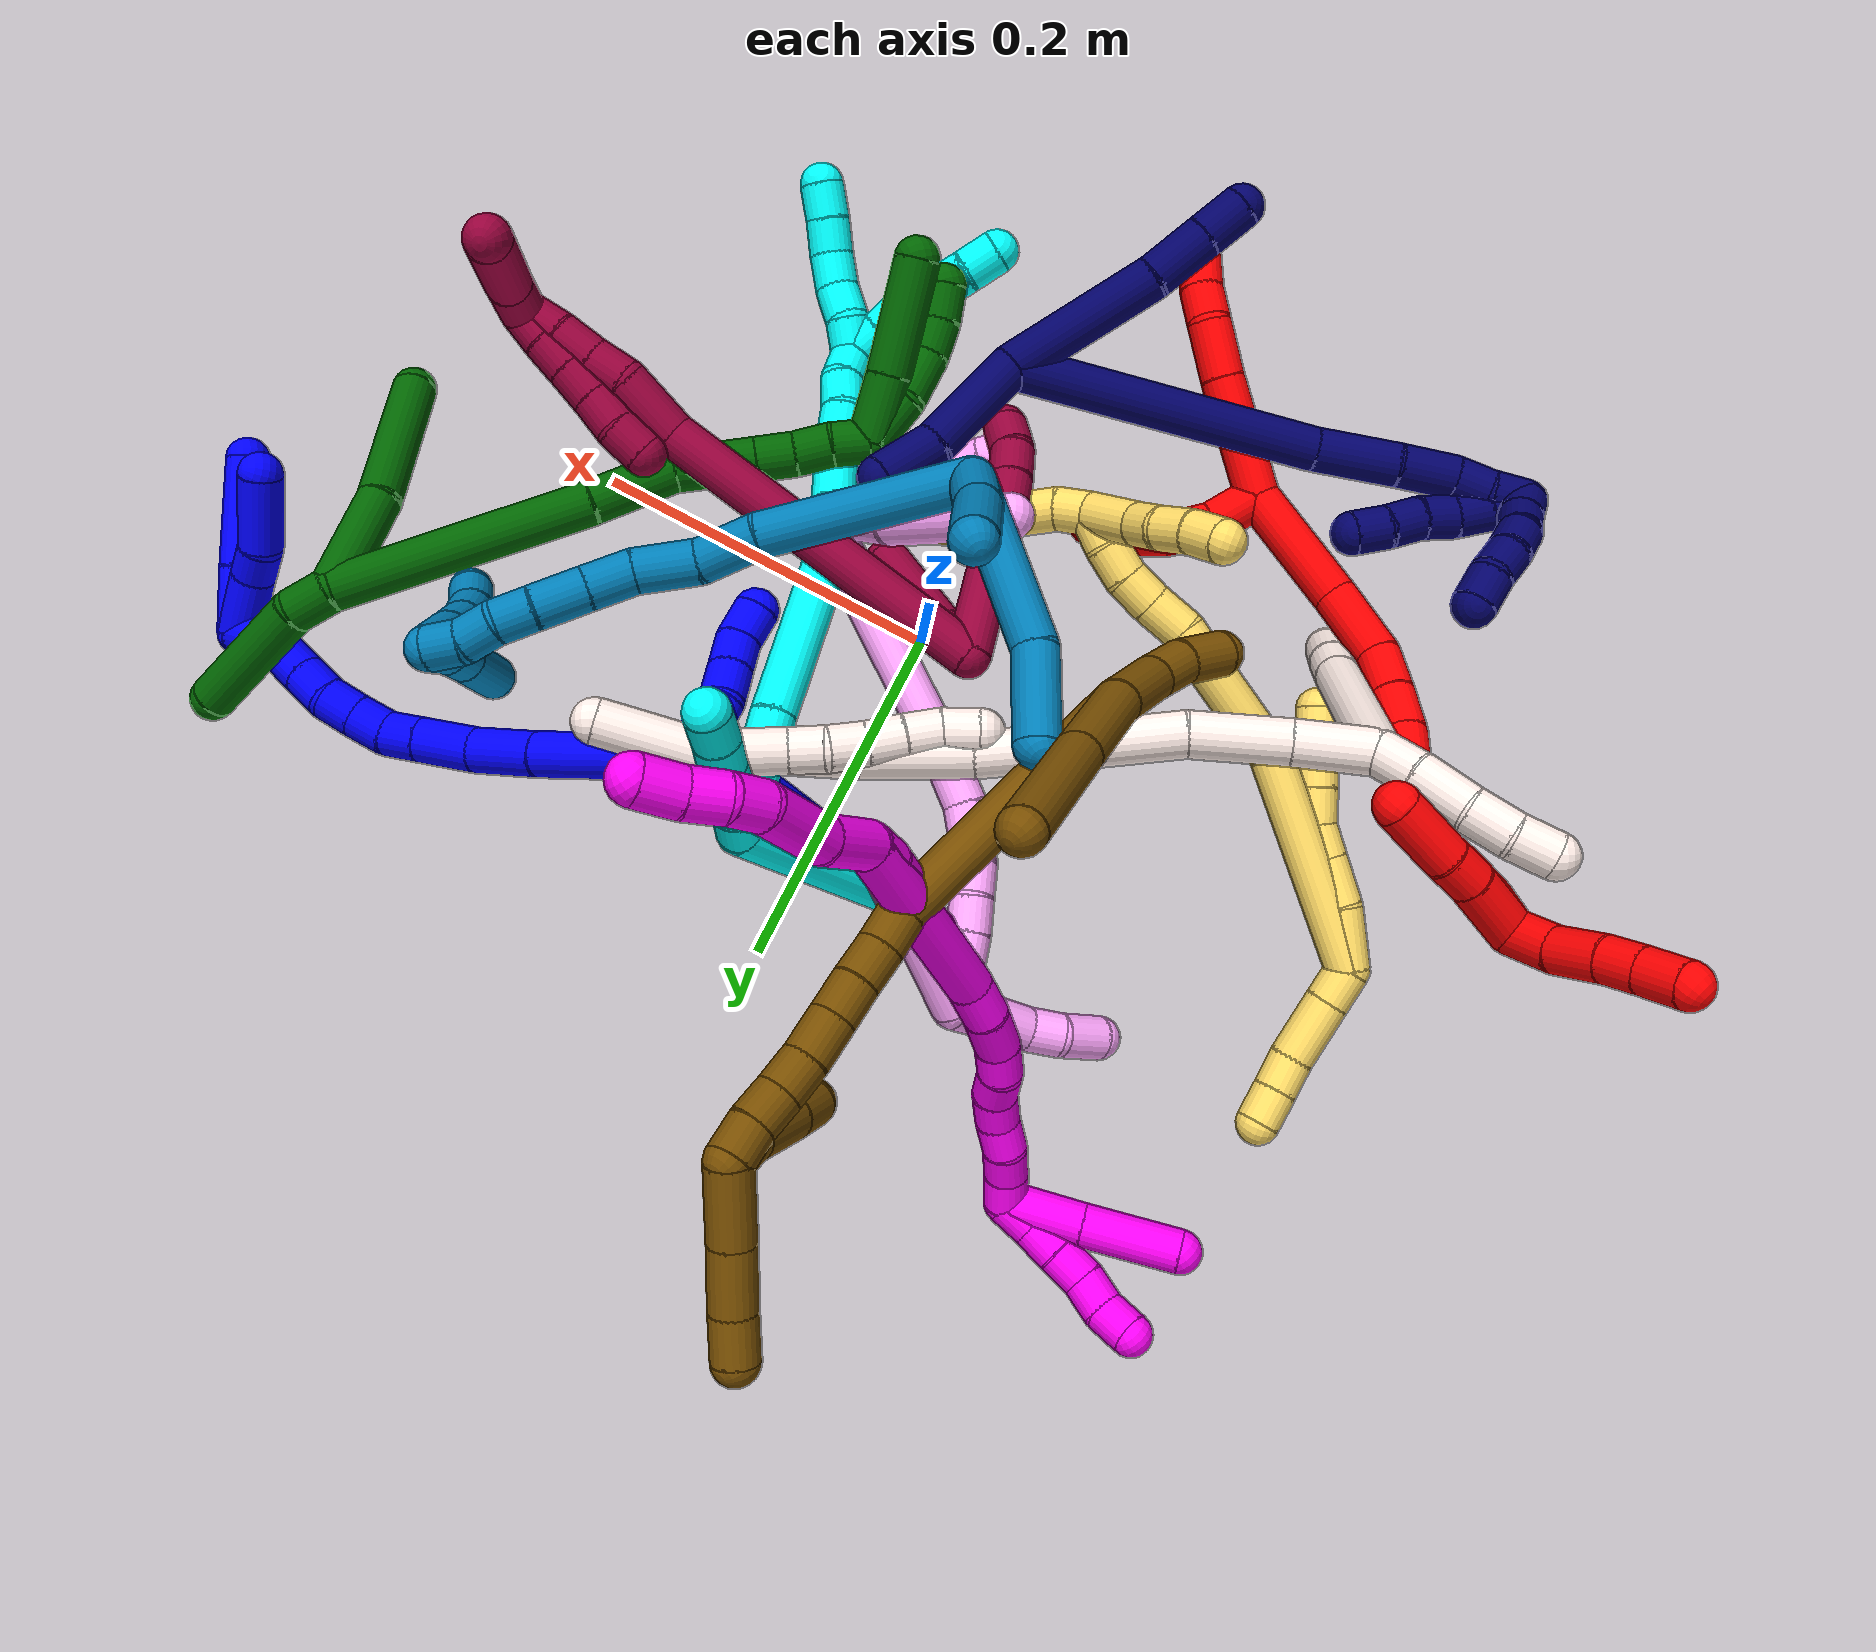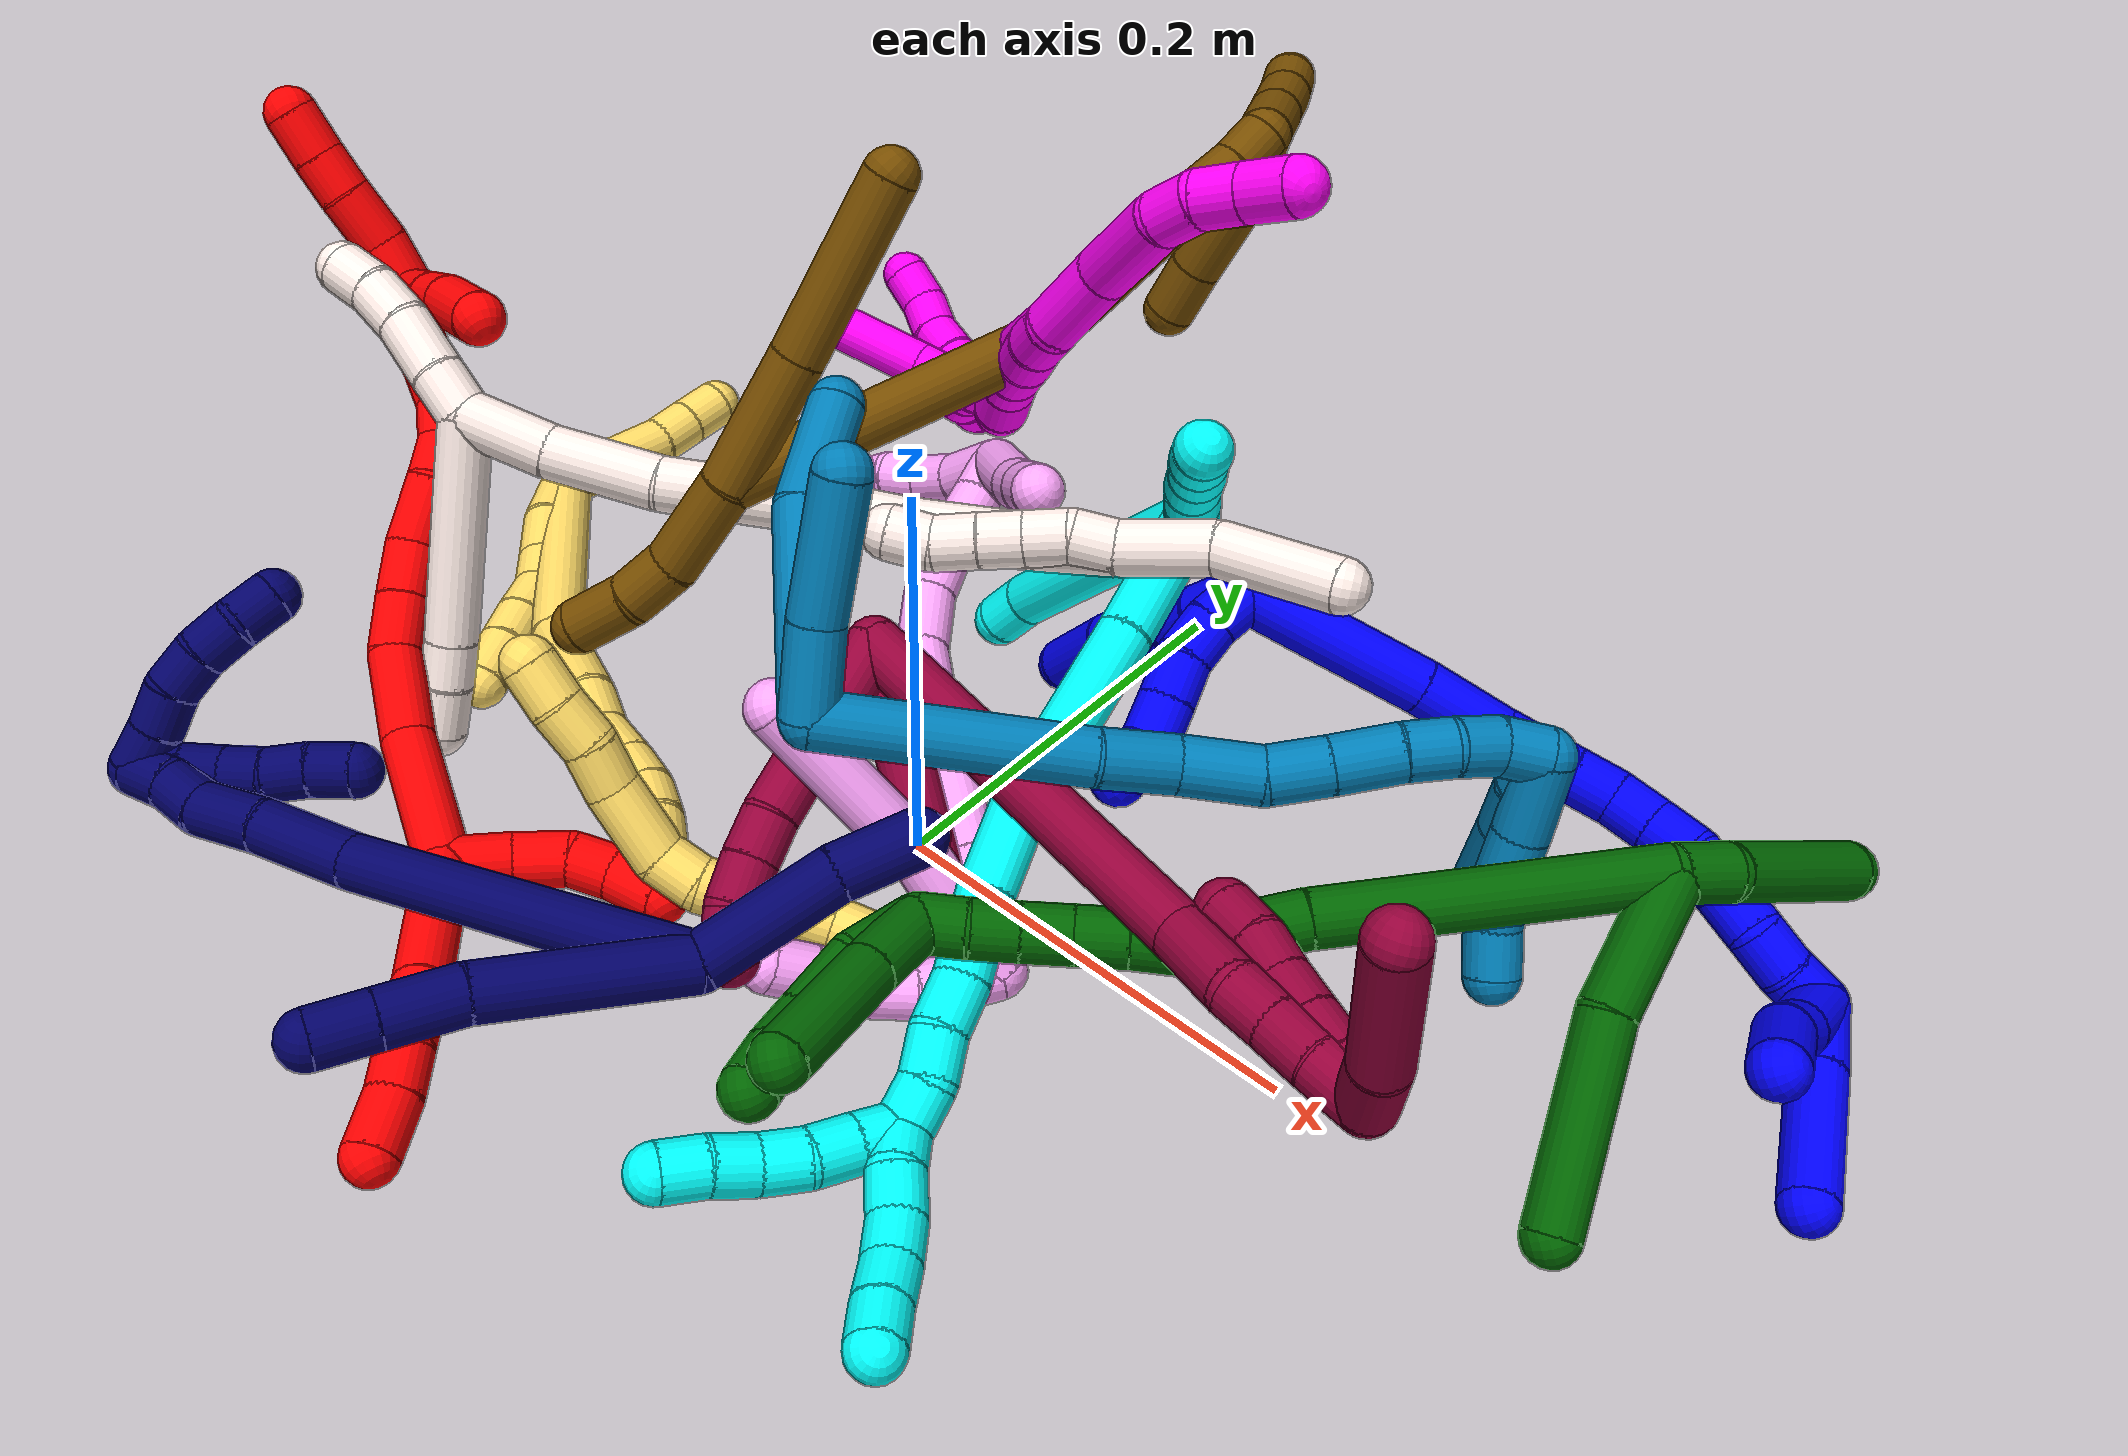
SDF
<sdf version="1.7">
 <world name="default">
  <plugin name="TubeGeneratorPlugin" filename="libtube_generator_plugin.so"/>
  <model name="photoneo_s_sensor">
   <static>1</static>
   <pose>0 0 2 1.57079 1.57079 3.14159</pose>
   <link name="link">
    <inertial><mass>0.1</mass></inertial>
    <sensor name="sensor" type="depth">
     <update_rate>30</update_rate>
     <camera>
      <horizontal_fov>1.22</horizontal_fov>
      <image><width>1920</width><height>1200</height><format>B8G8R8</format></image>
      <clip><near>0.1</near><far>4</far></clip>
      <depth_camera><output>points</output></depth_camera>
     </camera>
     <plugin name="camera_plugin" filename="libgazebo_ros_depth_camera.so">
      <baseline>0.2</baseline>
      <alwaysOn>1</alwaysOn>
      <updateRate>0.0</updateRate>
      <cameraName>camera_ir</cameraName>
      <imageTopicName>/camera/color/image_raw</imageTopicName>
      <cameraInfoTopicName>/camera/color/camera_info</cameraInfoTopicName>
      <depthImageTopicName>/camera/depth/image_raw</depthImageTopicName>
      <depthImageCameraInfoTopicName>/camera/depth/camera_info</depthImageCameraInfoTopicName>
      <pointCloudTopicName>/camera/depth/points</pointCloudTopicName>
      <frameName>fr_optical</frameName>
      <pointCloudCutoff>0.1</pointCloudCutoff>
      <pointCloudCutoffMax>2.0</pointCloudCutoffMax>
      <distortionK1>0</distortionK1>
      <distortionK2>0</distortionK2>
      <distortionK3>0</distortionK3>
      <distortionT1>0</distortionT1>
      <distortionT2>0</distortionT2>
      <CxPrime>0</CxPrime>
      <Cx>0</Cx>
      <Cy>0</Cy>
      <focalLength>0</focalLength>
      <hackBaseline>0</hackBaseline>
     </plugin>
    </sensor>
   </link>
  </model>
  <gravity>0 0 -9.8</gravity>
  <magnetic_field>6e-06 2.3e-05 -4.2e-05</magnetic_field>
  <atmosphere type="adiabatic"/>
  <physics name="default_physics" default="0" type="ode">
   <max_step_size>0.003</max_step_size>
   <real_time_factor>1</real_time_factor>
   <real_time_update_rate>1000</real_time_update_rate>
   <max_contacts>10000</max_contacts>
   <ode>
    <solver>
     <type>quick</type>
     <iters>100</iters>
     <sor>1.3</sor>
     <use_dynamic_moi_rescaling>0</use_dynamic_moi_rescaling>
    </solver>
    <constraints>
     <contact_max_correcting_vel>0</contact_max_correcting_vel>
     <contact_surface_layer>0.001</contact_surface_layer>
     <cfm>0</cfm>
     <erp>0.2</erp>
    </constraints>
   </ode>
  </physics>
  <scene><ambient>0.4 0.4 0.4 1</ambient><background>0.7 0.7 0.7 1</background><shadows>0</shadows></scene>
  <audio><device>default</device></audio>
  <spherical_coordinates>
   <surface_model>EARTH_WGS84</surface_model>
   <latitude_deg>0</latitude_deg>
   <longitude_deg>0</longitude_deg>
   <elevation>0</elevation>
   <heading_deg>0</heading_deg>
  </spherical_coordinates>
  <model name="bin">
   <static>1</static>
   <link name="bottom">
    <collision name="collision-bottom">
     <pose>0 0 -0.01 0 -0 0</pose>
     <geometry><box><size>0.8 0.6 0.02</size></box></geometry>
     <surface>
      <friction><ode><mu>100</mu><mu2>100</mu2></ode></friction>
      <contact><collide_bitmask>65535</collide_bitmask></contact>
     </surface>
    </collision>
   </link>
   <link name="west_wall">
    <collision name="collision-west_wall">
     <pose>-0.41 0 0.1 0 -0 0</pose>
     <geometry><box><size>0.02 0.6 0.2</size></box></geometry>
     <surface>
      <friction><ode><mu>100</mu><mu2>100</mu2></ode></friction>
      <contact><collide_bitmask>65535</collide_bitmask></contact>
     </surface>
    </collision>
   </link>
   <link name="east_wall">
    <collision name="collision-east_wall">
     <pose>0.41 0 0.1 0 -0 0</pose>
     <geometry><box><size>0.02 0.6 0.2</size></box></geometry>
     <surface>
      <friction><ode><mu>100</mu><mu2>100</mu2></ode></friction>
      <contact><collide_bitmask>65535</collide_bitmask></contact>
     </surface>
    </collision>
   </link>
   <link name="south_wall">
    <collision name="collision-south_wall">
     <pose>0 -0.31 0.1 0 -0 0</pose>
     <geometry><box><size>0.8 0.02 0.2</size></box></geometry>
     <surface>
      <friction><ode><mu>100</mu><mu2>100</mu2></ode></friction>
      <contact><collide_bitmask>65535</collide_bitmask></contact>
     </surface>
    </collision>
   </link>
   <link name="north_wall">
    <collision name="collision-north_wall">
     <pose>0 0.31 0.1 0 -0 0</pose>
     <geometry><box><size>0.8 0.02 0.2</size></box></geometry>
     <surface>
      <friction><ode><mu>100</mu><mu2>100</mu2></ode></friction>
      <contact><collide_bitmask>65535</collide_bitmask></contact>
     </surface>
    </collision>
   </link>
  </model>
  <model name="1">
   <static>0</static>
   <link name="1">
    <collision name="collision-cylinder-e_1_2_8">
     <pose>0.000418 0.001269 -0.014081 -3.05172 0.029547 -0.634919</pose>
     <geometry><cylinder><radius>0.0125</radius><length>0.028289</length></cylinder></geometry>
     <surface>
      <friction><ode><mu>1.16</mu><mu2>1.16</mu2><slip1>0</slip1><slip2>0</slip2></ode></friction>
      <contact><ode><kp>1e+06</kp><kd>1</kd><max_vel>0</max_vel><min_depth>0.001</min_depth></ode></contact>
     </surface>
    </collision>
    <visual name="visual-cylinder-e_1_2_8">
     <pose>0.000418 0.001269 -0.014081 -3.05172 0.029547 -0.634919</pose>
     <geometry><cylinder><radius>0.0125</radius><length>0.028289</length></cylinder></geometry>
     <material><ambient>0 0 1 1</ambient></material>
    </visual>
    <collision name="collision-cylinder-e_2_8_9">
     <pose>0.001131 0.004916 -0.038998 -2.92556 0.026648 -0.244531</pose>
     <geometry><cylinder><radius>0.0125</radius><length>0.022195</length></cylinder></geometry>
     <surface>
      <friction><ode><mu>1.16</mu><mu2>1.16</mu2><slip1>0</slip1><slip2>0</slip2></ode></friction>
      <contact><ode><kp>1e+06</kp><kd>1</kd><max_vel>0</max_vel><min_depth>0.001</min_depth></ode></contact>
     </surface>
    </collision>
    <visual name="visual-cylinder-e_2_8_9">
     <pose>0.001131 0.004916 -0.038998 -2.92556 0.026648 -0.244531</pose>
     <geometry><cylinder><radius>0.0125</radius><length>0.022195</length></cylinder></geometry>
     <material><ambient>0 0 1 1</ambient></material>
    </visual>
    <collision name="collision-cylinder-e_3_9_10">
     <pose>-6.1e-05 0.016591 -0.074307 -2.77855 -0.05678 0.307005</pose>
     <geometry><cylinder><radius>0.0125</radius><length>0.052444</length></cylinder></geometry>
     <surface>
      <friction><ode><mu>1.16</mu><mu2>1.16</mu2><slip1>0</slip1><slip2>0</slip2></ode></friction>
      <contact><ode><kp>1e+06</kp><kd>1</kd><max_vel>0</max_vel><min_depth>0.001</min_depth></ode></contact>
     </surface>
    </collision>
    <visual name="visual-cylinder-e_3_9_10">
     <pose>-6.1e-05 0.016591 -0.074307 -2.77855 -0.05678 0.307005</pose>
     <geometry><cylinder><radius>0.0125</radius><length>0.052444</length></cylinder></geometry>
     <material><ambient>0 0 1 1</ambient></material>
    </visual>
    <collision name="collision-cylinder-e_4_10_6">
     <pose>0.000226 0.033937 -0.120826 -2.79152 0.075484 -0.420722</pose>
     <geometry><cylinder><radius>0.0125</radius><length>0.047072</length></cylinder></geometry>
     <surface>
      <friction><ode><mu>1.16</mu><mu2>1.16</mu2><slip1>0</slip1><slip2>0</slip2></ode></friction>
      <contact><ode><kp>1e+06</kp><kd>1</kd><max_vel>0</max_vel><min_depth>0.001</min_depth></ode></contact>
     </surface>
    </collision>
    <visual name="visual-cylinder-e_4_10_6">
     <pose>0.000226 0.033937 -0.120826 -2.79152 0.075484 -0.420722</pose>
     <geometry><cylinder><radius>0.0125</radius><length>0.047072</length></cylinder></geometry>
     <material><ambient>0 0 1 1</ambient></material>
    </visual>
    <collision name="collision-cylinder-e_1_2_11">
     <pose>0.003786 -0.006665 -0.006422 2.33767 0.38829 0.86644</pose>
     <geometry><cylinder><radius>0.0125</radius><length>0.02</length></cylinder></geometry>
     <surface>
      <friction><ode><mu>1.16</mu><mu2>1.16</mu2><slip1>0</slip1><slip2>0</slip2></ode></friction>
      <contact><ode><kp>1e+06</kp><kd>1</kd><max_vel>0</max_vel><min_depth>0.001</min_depth></ode></contact>
     </surface>
    </collision>
    <visual name="visual-cylinder-e_1_2_11">
     <pose>0.003786 -0.006665 -0.006422 2.33767 0.38829 0.86644</pose>
     <geometry><cylinder><radius>0.0125</radius><length>0.02</length></cylinder></geometry>
     <material><ambient>0 0 1 1</ambient></material>
    </visual>
    <collision name="collision-cylinder-e_2_11_12">
     <pose>0.013006 -0.020477 -0.017249 2.12307 0.574415 0.973115</pose>
     <geometry><cylinder><radius>0.0125</radius><length>0.02</length></cylinder></geometry>
     <surface>
      <friction><ode><mu>1.16</mu><mu2>1.16</mu2><slip1>0</slip1><slip2>0</slip2></ode></friction>
      <contact><ode><kp>1e+06</kp><kd>1</kd><max_vel>0</max_vel><min_depth>0.001</min_depth></ode></contact>
     </surface>
    </collision>
    <visual name="visual-cylinder-e_2_11_12">
     <pose>0.013006 -0.020477 -0.017249 2.12307 0.574415 0.973115</pose>
     <geometry><cylinder><radius>0.0125</radius><length>0.02</length></cylinder></geometry>
     <material><ambient>0 0 1 1</ambient></material>
    </visual>
    <collision name="collision-cylinder-e_3_12_13">
     <pose>0.026015 -0.033037 -0.025301 2.16374 0.859592 1.42237</pose>
     <geometry><cylinder><radius>0.0125</radius><length>0.02</length></cylinder></geometry>
     <surface>
      <friction><ode><mu>1.16</mu><mu2>1.16</mu2><slip1>0</slip1><slip2>0</slip2></ode></friction>
      <contact><ode><kp>1e+06</kp><kd>1</kd><max_vel>0</max_vel><min_depth>0.001</min_depth></ode></contact>
     </surface>
    </collision>
    <visual name="visual-cylinder-e_3_12_13">
     <pose>0.026015 -0.033037 -0.025301 2.16374 0.859592 1.42237</pose>
     <geometry><cylinder><radius>0.0125</radius><length>0.02</length></cylinder></geometry>
     <material><ambient>0 0 1 1</ambient></material>
    </visual>
    <collision name="collision-cylinder-e_4_13_14">
     <pose>0.040972 -0.044261 -0.032376 2.10368 0.830321 1.3145</pose>
     <geometry><cylinder><radius>0.0125</radius><length>0.02</length></cylinder></geometry>
     <surface>
      <friction><ode><mu>1.16</mu><mu2>1.16</mu2><slip1>0</slip1><slip2>0</slip2></ode></friction>
      <contact><ode><kp>1e+06</kp><kd>1</kd><max_vel>0</max_vel><min_depth>0.001</min_depth></ode></contact>
     </surface>
    </collision>
    <visual name="visual-cylinder-e_4_13_14">
     <pose>0.040972 -0.044261 -0.032376 2.10368 0.830321 1.3145</pose>
     <geometry><cylinder><radius>0.0125</radius><length>0.02</length></cylinder></geometry>
     <material><ambient>0 0 1 1</ambient></material>
    </visual>
    <collision name="collision-cylinder-e_5_14_5">
     <pose>0.053002 -0.057858 -0.04002 2.06718 0.483422 0.784849</pose>
     <geometry><cylinder><radius>0.0125</radius><length>0.02</length></cylinder></geometry>
     <surface>
      <friction><ode><mu>1.16</mu><mu2>1.16</mu2><slip1>0</slip1><slip2>0</slip2></ode></friction>
      <contact><ode><kp>1e+06</kp><kd>1</kd><max_vel>0</max_vel><min_depth>0.001</min_depth></ode></contact>
     </surface>
    </collision>
    <visual name="visual-cylinder-e_5_14_5">
     <pose>0.053002 -0.057858 -0.04002 2.06718 0.483422 0.784849</pose>
     <geometry><cylinder><radius>0.0125</radius><length>0.02</length></cylinder></geometry>
     <material><ambient>0 0 1 1</ambient></material>
    </visual>
    <collision name="collision-cylinder-e_1_2_15">
     <pose>0.029939 0.02298 0.019354 -0.870836 0.783643 -0.379792</pose>
     <geometry><cylinder><radius>0.0125</radius><length>0.084829</length></cylinder></geometry>
     <surface>
      <friction><ode><mu>1.16</mu><mu2>1.16</mu2><slip1>0</slip1><slip2>0</slip2></ode></friction>
      <contact><ode><kp>1e+06</kp><kd>1</kd><max_vel>0</max_vel><min_depth>0.001</min_depth></ode></contact>
     </surface>
    </collision>
    <visual name="visual-cylinder-e_1_2_15">
     <pose>0.029939 0.02298 0.019354 -0.870836 0.783643 -0.379792</pose>
     <geometry><cylinder><radius>0.0125</radius><length>0.084829</length></cylinder></geometry>
     <material><ambient>0 0 1 1</ambient></material>
    </visual>
    <collision name="collision-cylinder-e_2_15_16">
     <pose>0.074719 0.056178 0.047211 -0.876756 0.840363 -0.412942</pose>
     <geometry><cylinder><radius>0.0125</radius><length>0.039848</length></cylinder></geometry>
     <surface>
      <friction><ode><mu>1.16</mu><mu2>1.16</mu2><slip1>0</slip1><slip2>0</slip2></ode></friction>
      <contact><ode><kp>1e+06</kp><kd>1</kd><max_vel>0</max_vel><min_depth>0.001</min_depth></ode></contact>
     </surface>
    </collision>
    <visual name="visual-cylinder-e_2_15_16">
     <pose>0.074719 0.056178 0.047211 -0.876756 0.840363 -0.412942</pose>
     <geometry><cylinder><radius>0.0125</radius><length>0.039848</length></cylinder></geometry>
     <material><ambient>0 0 1 1</ambient></material>
    </visual>
    <collision name="collision-cylinder-e_3_16_17">
     <pose>0.101976 0.07311 0.065208 -0.615548 0.818113 -0.273879</pose>
     <geometry><cylinder><radius>0.0125</radius><length>0.034022</length></cylinder></geometry>
     <surface>
      <friction><ode><mu>1.16</mu><mu2>1.16</mu2><slip1>0</slip1><slip2>0</slip2></ode></friction>
      <contact><ode><kp>1e+06</kp><kd>1</kd><max_vel>0</max_vel><min_depth>0.001</min_depth></ode></contact>
     </surface>
    </collision>
    <visual name="visual-cylinder-e_3_16_17">
     <pose>0.101976 0.07311 0.065208 -0.615548 0.818113 -0.273879</pose>
     <geometry><cylinder><radius>0.0125</radius><length>0.034022</length></cylinder></geometry>
     <material><ambient>0 0 1 1</ambient></material>
    </visual>
    <collision name="collision-cylinder-e_4_17_18">
     <pose>0.12192 0.083918 0.080522 -0.612964 0.813671 -0.271031</pose>
     <geometry><cylinder><radius>0.0125</radius><length>0.020717</length></cylinder></geometry>
     <surface>
      <friction><ode><mu>1.16</mu><mu2>1.16</mu2><slip1>0</slip1><slip2>0</slip2></ode></friction>
      <contact><ode><kp>1e+06</kp><kd>1</kd><max_vel>0</max_vel><min_depth>0.001</min_depth></ode></contact>
     </surface>
    </collision>
    <visual name="visual-cylinder-e_4_17_18">
     <pose>0.12192 0.083918 0.080522 -0.612964 0.813671 -0.271031</pose>
     <geometry><cylinder><radius>0.0125</radius><length>0.020717</length></cylinder></geometry>
     <material><ambient>0 0 1 1</ambient></material>
    </visual>
    <collision name="collision-cylinder-e_5_18_19">
     <pose>0.137233 0.088679 0.09281 -0.102967 0.87487 -0.048186</pose>
     <geometry><cylinder><radius>0.0125</radius><length>0.020287</length></cylinder></geometry>
     <surface>
      <friction><ode><mu>1.16</mu><mu2>1.16</mu2><slip1>0</slip1><slip2>0</slip2></ode></friction>
      <contact><ode><kp>1e+06</kp><kd>1</kd><max_vel>0</max_vel><min_depth>0.001</min_depth></ode></contact>
     </surface>
    </collision>
    <visual name="visual-cylinder-e_5_18_19">
     <pose>0.137233 0.088679 0.09281 -0.102967 0.87487 -0.048186</pose>
     <geometry><cylinder><radius>0.0125</radius><length>0.020287</length></cylinder></geometry>
     <material><ambient>0 0 1 1</ambient></material>
    </visual>
    <collision name="collision-cylinder-e_6_19_20">
     <pose>0.152646 0.089481 0.105794 -0.020501 0.863811 -0.00945</pose>
     <geometry><cylinder><radius>0.0125</radius><length>0.020067</length></cylinder></geometry>
     <surface>
      <friction><ode><mu>1.16</mu><mu2>1.16</mu2><slip1>0</slip1><slip2>0</slip2></ode></friction>
      <contact><ode><kp>1e+06</kp><kd>1</kd><max_vel>0</max_vel><min_depth>0.001</min_depth></ode></contact>
     </surface>
    </collision>
    <visual name="visual-cylinder-e_6_19_20">
     <pose>0.152646 0.089481 0.105794 -0.020501 0.863811 -0.00945</pose>
     <geometry><cylinder><radius>0.0125</radius><length>0.020067</length></cylinder></geometry>
     <material><ambient>0 0 1 1</ambient></material>
    </visual>
    <collision name="collision-cylinder-e_7_20_21">
     <pose>0.169244 0.088732 0.116646 0.200864 1.11241 0.12513</pose>
     <geometry><cylinder><radius>0.0125</radius><length>0.020003</length></cylinder></geometry>
     <surface>
      <friction><ode><mu>1.16</mu><mu2>1.16</mu2><slip1>0</slip1><slip2>0</slip2></ode></friction>
      <contact><ode><kp>1e+06</kp><kd>1</kd><max_vel>0</max_vel><min_depth>0.001</min_depth></ode></contact>
     </surface>
    </collision>
    <visual name="visual-cylinder-e_7_20_21">
     <pose>0.169244 0.088732 0.116646 0.200864 1.11241 0.12513</pose>
     <geometry><cylinder><radius>0.0125</radius><length>0.020003</length></cylinder></geometry>
     <material><ambient>0 0 1 1</ambient></material>
    </visual>
    <collision name="collision-cylinder-e_8_21_22">
     <pose>0.187233 0.086915 0.125317 0.212204 1.11399 0.132459</pose>
     <geometry><cylinder><radius>0.0125</radius><length>0.0201</length></cylinder></geometry>
     <surface>
      <friction><ode><mu>1.16</mu><mu2>1.16</mu2><slip1>0</slip1><slip2>0</slip2></ode></friction>
      <contact><ode><kp>1e+06</kp><kd>1</kd><max_vel>0</max_vel><min_depth>0.001</min_depth></ode></contact>
     </surface>
    </collision>
    <visual name="visual-cylinder-e_8_21_22">
     <pose>0.187233 0.086915 0.125317 0.212204 1.11399 0.132459</pose>
     <geometry><cylinder><radius>0.0125</radius><length>0.0201</length></cylinder></geometry>
     <material><ambient>0 0 1 1</ambient></material>
    </visual>
    <collision name="collision-cylinder-e_9_22_23">
     <pose>0.205672 0.087961 0.132412 -0.62186 1.22462 -0.443975</pose>
     <geometry><cylinder><radius>0.0125</radius><length>0.020028</length></cylinder></geometry>
     <surface>
      <friction><ode><mu>1.16</mu><mu2>1.16</mu2><slip1>0</slip1><slip2>0</slip2></ode></friction>
      <contact><ode><kp>1e+06</kp><kd>1</kd><max_vel>0</max_vel><min_depth>0.001</min_depth></ode></contact>
     </surface>
    </collision>
    <visual name="visual-cylinder-e_9_22_23">
     <pose>0.205672 0.087961 0.132412 -0.62186 1.22462 -0.443975</pose>
     <geometry><cylinder><radius>0.0125</radius><length>0.020028</length></cylinder></geometry>
     <material><ambient>0 0 1 1</ambient></material>
    </visual>
    <collision name="collision-cylinder-e_10_23_1">
     <pose>0.223878 0.093857 0.13808 -0.932348 1.06397 -0.575851</pose>
     <geometry><cylinder><radius>0.0125</radius><length>0.0201</length></cylinder></geometry>
     <surface>
      <friction><ode><mu>1.16</mu><mu2>1.16</mu2><slip1>0</slip1><slip2>0</slip2></ode></friction>
      <contact><ode><kp>1e+06</kp><kd>1</kd><max_vel>0</max_vel><min_depth>0.001</min_depth></ode></contact>
     </surface>
    </collision>
    <visual name="visual-cylinder-e_10_23_1">
     <pose>0.223878 0.093857 0.13808 -0.932348 1.06397 -0.575851</pose>
     <geometry><cylinder><radius>0.0125</radius><length>0.0201</length></cylinder></geometry>
     <material><ambient>0 0 1 1</ambient></material>
    </visual>
    <collision name="collision-cylinder-e_1_1_24">
     <pose>0.24356 0.08309 0.142983 1.43577 0.633921 0.557996</pose>
     <geometry><cylinder><radius>0.0125</radius><length>0.036788</length></cylinder></geometry>
     <surface>
      <friction><ode><mu>1.16</mu><mu2>1.16</mu2><slip1>0</slip1><slip2>0</slip2></ode></friction>
      <contact><ode><kp>1e+06</kp><kd>1</kd><max_vel>0</max_vel><min_depth>0.001</min_depth></ode></contact>
     </surface>
    </collision>
    <visual name="visual-cylinder-e_1_1_24">
     <pose>0.24356 0.08309 0.142983 1.43577 0.633921 0.557996</pose>
     <geometry><cylinder><radius>0.0125</radius><length>0.036788</length></cylinder></geometry>
     <material><ambient>0 0 1 1</ambient></material>
    </visual>
    <collision name="collision-cylinder-e_2_24_4">
     <pose>0.273163 0.043051 0.147455 1.4734 0.633431 0.577927</pose>
     <geometry><cylinder><radius>0.0125</radius><length>0.063212</length></cylinder></geometry>
     <surface>
      <friction><ode><mu>1.16</mu><mu2>1.16</mu2><slip1>0</slip1><slip2>0</slip2></ode></friction>
      <contact><ode><kp>1e+06</kp><kd>1</kd><max_vel>0</max_vel><min_depth>0.001</min_depth></ode></contact>
     </surface>
    </collision>
    <visual name="visual-cylinder-e_2_24_4">
     <pose>0.273163 0.043051 0.147455 1.4734 0.633431 0.577927</pose>
     <geometry><cylinder><radius>0.0125</radius><length>0.063212</length></cylinder></geometry>
     <material><ambient>0 0 1 1</ambient></material>
    </visual>
    <collision name="collision-cylinder-e_1_1_25">
     <pose>0.233351 0.079652 0.143555 1.43009 0.037482 0.032548</pose>
     <geometry><cylinder><radius>0.0125</radius><length>0.036632</length></cylinder></geometry>
     <surface>
      <friction><ode><mu>1.16</mu><mu2>1.16</mu2><slip1>0</slip1><slip2>0</slip2></ode></friction>
      <contact><ode><kp>1e+06</kp><kd>1</kd><max_vel>0</max_vel><min_depth>0.001</min_depth></ode></contact>
     </surface>
    </collision>
    <visual name="visual-cylinder-e_1_1_25">
     <pose>0.233351 0.079652 0.143555 1.43009 0.037482 0.032548</pose>
     <geometry><cylinder><radius>0.0125</radius><length>0.036632</length></cylinder></geometry>
     <material><ambient>0 0 1 1</ambient></material>
    </visual>
    <collision name="collision-cylinder-e_2_25_26">
     <pose>0.232174 0.051777 0.148126 1.36808 -0.185013 -0.150998</pose>
     <geometry><cylinder><radius>0.0125</radius><length>0.02026</length></cylinder></geometry>
     <surface>
      <friction><ode><mu>1.16</mu><mu2>1.16</mu2><slip1>0</slip1><slip2>0</slip2></ode></friction>
      <contact><ode><kp>1e+06</kp><kd>1</kd><max_vel>0</max_vel><min_depth>0.001</min_depth></ode></contact>
     </surface>
    </collision>
    <visual name="visual-cylinder-e_2_25_26">
     <pose>0.232174 0.051777 0.148126 1.36808 -0.185013 -0.150998</pose>
     <geometry><cylinder><radius>0.0125</radius><length>0.02026</length></cylinder></geometry>
     <material><ambient>0 0 1 1</ambient></material>
    </visual>
    <collision name="collision-cylinder-e_3_26_3">
     <pose>0.232413 0.021761 0.157172 1.23636 0.097689 0.069501</pose>
     <geometry><cylinder><radius>0.0125</radius><length>0.043108</length></cylinder></geometry>
     <surface>
      <friction><ode><mu>1.16</mu><mu2>1.16</mu2><slip1>0</slip1><slip2>0</slip2></ode></friction>
      <contact><ode><kp>1e+06</kp><kd>1</kd><max_vel>0</max_vel><min_depth>0.001</min_depth></ode></contact>
     </surface>
    </collision>
    <visual name="visual-cylinder-e_3_26_3">
     <pose>0.232413 0.021761 0.157172 1.23636 0.097689 0.069501</pose>
     <geometry><cylinder><radius>0.0125</radius><length>0.043108</length></cylinder></geometry>
     <material><ambient>0 0 1 1</ambient></material>
    </visual>
    <collision name="collision-sphere-3">
     <pose>0.234515 0.001498 0.164213 0 -0 0</pose>
     <geometry><sphere><radius>0.0125</radius></sphere></geometry>
     <surface>
      <friction><ode><mu>1.16</mu><mu2>1.16</mu2><slip1>0</slip1><slip2>0</slip2></ode></friction>
      <contact><ode><kp>1e+06</kp><kd>1</kd><max_vel>0</max_vel><min_depth>0.001</min_depth></ode></contact>
     </surface>
    </collision>
    <visual name="visual-sphere-3">
     <pose>0.234515 0.001498 0.164213 0 -0 0</pose>
     <geometry><sphere><radius>0.0125</radius></sphere></geometry>
     <material><ambient>0 0 1 1</ambient></material>
    </visual>
    <collision name="collision-sphere-26">
     <pose>0.230311 0.042024 0.150131 0 -0 0</pose>
     <geometry><sphere><radius>0.0125</radius></sphere></geometry>
     <surface>
      <friction><ode><mu>1.16</mu><mu2>1.16</mu2><slip1>0</slip1><slip2>0</slip2></ode></friction>
      <contact><ode><kp>1e+06</kp><kd>1</kd><max_vel>0</max_vel><min_depth>0.001</min_depth></ode></contact>
     </surface>
    </collision>
    <visual name="visual-sphere-26">
     <pose>0.230311 0.042024 0.150131 0 -0 0</pose>
     <geometry><sphere><radius>0.0125</radius></sphere></geometry>
     <material><ambient>0 0 1 1</ambient></material>
    </visual>
    <collision name="collision-sphere-25">
     <pose>0.234038 0.06153 0.146121 0 -0 0</pose>
     <geometry><sphere><radius>0.0125</radius></sphere></geometry>
     <surface>
      <friction><ode><mu>1.16</mu><mu2>1.16</mu2><slip1>0</slip1><slip2>0</slip2></ode></friction>
      <contact><ode><kp>1e+06</kp><kd>1</kd><max_vel>0</max_vel><min_depth>0.001</min_depth></ode></contact>
     </surface>
    </collision>
    <visual name="visual-sphere-25">
     <pose>0.234038 0.06153 0.146121 0 -0 0</pose>
     <geometry><sphere><radius>0.0125</radius></sphere></geometry>
     <material><ambient>0 0 1 1</ambient></material>
    </visual>
    <collision name="collision-sphere-4">
     <pose>0.291871 0.017697 0.149933 0 -0 0</pose>
     <geometry><sphere><radius>0.0125</radius></sphere></geometry>
     <surface>
      <friction><ode><mu>1.16</mu><mu2>1.16</mu2><slip1>0</slip1><slip2>0</slip2></ode></friction>
      <contact><ode><kp>1e+06</kp><kd>1</kd><max_vel>0</max_vel><min_depth>0.001</min_depth></ode></contact>
     </surface>
    </collision>
    <visual name="visual-sphere-4">
     <pose>0.291871 0.017697 0.149933 0 -0 0</pose>
     <geometry><sphere><radius>0.0125</radius></sphere></geometry>
     <material><ambient>0 0 1 1</ambient></material>
    </visual>
    <collision name="collision-sphere-24">
     <pose>0.254454 0.068404 0.144978 0 -0 0</pose>
     <geometry><sphere><radius>0.0125</radius></sphere></geometry>
     <surface>
      <friction><ode><mu>1.16</mu><mu2>1.16</mu2><slip1>0</slip1><slip2>0</slip2></ode></friction>
      <contact><ode><kp>1e+06</kp><kd>1</kd><max_vel>0</max_vel><min_depth>0.001</min_depth></ode></contact>
     </surface>
    </collision>
    <visual name="visual-sphere-24">
     <pose>0.254454 0.068404 0.144978 0 -0 0</pose>
     <geometry><sphere><radius>0.0125</radius></sphere></geometry>
     <material><ambient>0 0 1 1</ambient></material>
    </visual>
    <collision name="collision-sphere-1">
     <pose>0.232665 0.097775 0.140988 0 -0 0</pose>
     <geometry><sphere><radius>0.0125</radius></sphere></geometry>
     <surface>
      <friction><ode><mu>1.16</mu><mu2>1.16</mu2><slip1>0</slip1><slip2>0</slip2></ode></friction>
      <contact><ode><kp>1e+06</kp><kd>1</kd><max_vel>0</max_vel><min_depth>0.001</min_depth></ode></contact>
     </surface>
    </collision>
    <visual name="visual-sphere-1">
     <pose>0.232665 0.097775 0.140988 0 -0 0</pose>
     <geometry><sphere><radius>0.0125</radius></sphere></geometry>
     <material><ambient>0 0 1 1</ambient></material>
    </visual>
    <collision name="collision-sphere-23">
     <pose>0.215092 0.08994 0.135173 0 -0 0</pose>
     <geometry><sphere><radius>0.0125</radius></sphere></geometry>
     <surface>
      <friction><ode><mu>1.16</mu><mu2>1.16</mu2><slip1>0</slip1><slip2>0</slip2></ode></friction>
      <contact><ode><kp>1e+06</kp><kd>1</kd><max_vel>0</max_vel><min_depth>0.001</min_depth></ode></contact>
     </surface>
    </collision>
    <visual name="visual-sphere-23">
     <pose>0.215092 0.08994 0.135173 0 -0 0</pose>
     <geometry><sphere><radius>0.0125</radius></sphere></geometry>
     <material><ambient>0 0 1 1</ambient></material>
    </visual>
    <collision name="collision-sphere-22">
     <pose>0.196252 0.085981 0.12965 0 -0 0</pose>
     <geometry><sphere><radius>0.0125</radius></sphere></geometry>
     <surface>
      <friction><ode><mu>1.16</mu><mu2>1.16</mu2><slip1>0</slip1><slip2>0</slip2></ode></friction>
      <contact><ode><kp>1e+06</kp><kd>1</kd><max_vel>0</max_vel><min_depth>0.001</min_depth></ode></contact>
     </surface>
    </collision>
    <visual name="visual-sphere-22">
     <pose>0.196252 0.085981 0.12965 0 -0 0</pose>
     <geometry><sphere><radius>0.0125</radius></sphere></geometry>
     <material><ambient>0 0 1 1</ambient></material>
    </visual>
    <collision name="collision-sphere-21">
     <pose>0.178213 0.087849 0.120983 0 -0 0</pose>
     <geometry><sphere><radius>0.0125</radius></sphere></geometry>
     <surface>
      <friction><ode><mu>1.16</mu><mu2>1.16</mu2><slip1>0</slip1><slip2>0</slip2></ode></friction>
      <contact><ode><kp>1e+06</kp><kd>1</kd><max_vel>0</max_vel><min_depth>0.001</min_depth></ode></contact>
     </surface>
    </collision>
    <visual name="visual-sphere-21">
     <pose>0.178213 0.087849 0.120983 0 -0 0</pose>
     <geometry><sphere><radius>0.0125</radius></sphere></geometry>
     <material><ambient>0 0 1 1</ambient></material>
    </visual>
    <collision name="collision-sphere-11">
     <pose>0.007572 -0.01333 -0.012845 0 -0 0</pose>
     <geometry><sphere><radius>0.0125</radius></sphere></geometry>
     <surface>
      <friction><ode><mu>1.16</mu><mu2>1.16</mu2><slip1>0</slip1><slip2>0</slip2></ode></friction>
      <contact><ode><kp>1e+06</kp><kd>1</kd><max_vel>0</max_vel><min_depth>0.001</min_depth></ode></contact>
     </surface>
    </collision>
    <visual name="visual-sphere-11">
     <pose>0.007572 -0.01333 -0.012845 0 -0 0</pose>
     <geometry><sphere><radius>0.0125</radius></sphere></geometry>
     <material><ambient>0 0 1 1</ambient></material>
    </visual>
    <collision name="collision-sphere-6">
     <pose>0.002001 0.041986 -0.142872 0 -0 0</pose>
     <geometry><sphere><radius>0.0125</radius></sphere></geometry>
     <surface>
      <friction><ode><mu>1.16</mu><mu2>1.16</mu2><slip1>0</slip1><slip2>0</slip2></ode></friction>
      <contact><ode><kp>1e+06</kp><kd>1</kd><max_vel>0</max_vel><min_depth>0.001</min_depth></ode></contact>
     </surface>
    </collision>
    <visual name="visual-sphere-6">
     <pose>0.002001 0.041986 -0.142872 0 -0 0</pose>
     <geometry><sphere><radius>0.0125</radius></sphere></geometry>
     <material><ambient>0 0 1 1</ambient></material>
    </visual>
    <collision name="collision-sphere-10">
     <pose>-0.001549 0.025888 -0.09878 0 -0 0</pose>
     <geometry><sphere><radius>0.0125</radius></sphere></geometry>
     <surface>
      <friction><ode><mu>1.16</mu><mu2>1.16</mu2><slip1>0</slip1><slip2>0</slip2></ode></friction>
      <contact><ode><kp>1e+06</kp><kd>1</kd><max_vel>0</max_vel><min_depth>0.001</min_depth></ode></contact>
     </surface>
    </collision>
    <visual name="visual-sphere-10">
     <pose>-0.001549 0.025888 -0.09878 0 -0 0</pose>
     <geometry><sphere><radius>0.0125</radius></sphere></geometry>
     <material><ambient>0 0 1 1</ambient></material>
    </visual>
    <collision name="collision-sphere-9">
     <pose>0.001427 0.007294 -0.049833 0 -0 0</pose>
     <geometry><sphere><radius>0.0125</radius></sphere></geometry>
     <surface>
      <friction><ode><mu>1.16</mu><mu2>1.16</mu2><slip1>0</slip1><slip2>0</slip2></ode></friction>
      <contact><ode><kp>1e+06</kp><kd>1</kd><max_vel>0</max_vel><min_depth>0.001</min_depth></ode></contact>
     </surface>
    </collision>
    <visual name="visual-sphere-9">
     <pose>0.001427 0.007294 -0.049833 0 -0 0</pose>
     <geometry><sphere><radius>0.0125</radius></sphere></geometry>
     <material><ambient>0 0 1 1</ambient></material>
    </visual>
    <collision name="collision-sphere-2">
     <geometry><sphere><radius>0.0125</radius></sphere></geometry>
     <surface>
      <friction><ode><mu>1.16</mu><mu2>1.16</mu2><slip1>0</slip1><slip2>0</slip2></ode></friction>
      <contact><ode><kp>1e+06</kp><kd>1</kd><max_vel>0</max_vel><min_depth>0.001</min_depth></ode></contact>
     </surface>
    </collision>
    <visual name="visual-sphere-2">
     <geometry><sphere><radius>0.0125</radius></sphere></geometry>
     <material><ambient>0 0 1 1</ambient></material>
    </visual>
    <collision name="collision-sphere-19">
     <pose>0.145018 0.089347 0.099278 0 -0 0</pose>
     <geometry><sphere><radius>0.0125</radius></sphere></geometry>
     <surface>
      <friction><ode><mu>1.16</mu><mu2>1.16</mu2><slip1>0</slip1><slip2>0</slip2></ode></friction>
      <contact><ode><kp>1e+06</kp><kd>1</kd><max_vel>0</max_vel><min_depth>0.001</min_depth></ode></contact>
     </surface>
    </collision>
    <visual name="visual-sphere-19">
     <pose>0.145018 0.089347 0.099278 0 -0 0</pose>
     <geometry><sphere><radius>0.0125</radius></sphere></geometry>
     <material><ambient>0 0 1 1</ambient></material>
    </visual>
    <collision name="collision-sphere-8">
     <pose>0.000836 0.002538 -0.028162 0 -0 0</pose>
     <geometry><sphere><radius>0.0125</radius></sphere></geometry>
     <surface>
      <friction><ode><mu>1.16</mu><mu2>1.16</mu2><slip1>0</slip1><slip2>0</slip2></ode></friction>
      <contact><ode><kp>1e+06</kp><kd>1</kd><max_vel>0</max_vel><min_depth>0.001</min_depth></ode></contact>
     </surface>
    </collision>
    <visual name="visual-sphere-8">
     <pose>0.000836 0.002538 -0.028162 0 -0 0</pose>
     <geometry><sphere><radius>0.0125</radius></sphere></geometry>
     <material><ambient>0 0 1 1</ambient></material>
    </visual>
    <collision name="collision-sphere-12">
     <pose>0.018439 -0.027624 -0.021653 0 -0 0</pose>
     <geometry><sphere><radius>0.0125</radius></sphere></geometry>
     <surface>
      <friction><ode><mu>1.16</mu><mu2>1.16</mu2><slip1>0</slip1><slip2>0</slip2></ode></friction>
      <contact><ode><kp>1e+06</kp><kd>1</kd><max_vel>0</max_vel><min_depth>0.001</min_depth></ode></contact>
     </surface>
    </collision>
    <visual name="visual-sphere-12">
     <pose>0.018439 -0.027624 -0.021653 0 -0 0</pose>
     <geometry><sphere><radius>0.0125</radius></sphere></geometry>
     <material><ambient>0 0 1 1</ambient></material>
    </visual>
    <collision name="collision-sphere-13">
     <pose>0.033591 -0.03845 -0.028948 0 -0 0</pose>
     <geometry><sphere><radius>0.0125</radius></sphere></geometry>
     <surface>
      <friction><ode><mu>1.16</mu><mu2>1.16</mu2><slip1>0</slip1><slip2>0</slip2></ode></friction>
      <contact><ode><kp>1e+06</kp><kd>1</kd><max_vel>0</max_vel><min_depth>0.001</min_depth></ode></contact>
     </surface>
    </collision>
    <visual name="visual-sphere-13">
     <pose>0.033591 -0.03845 -0.028948 0 -0 0</pose>
     <geometry><sphere><radius>0.0125</radius></sphere></geometry>
     <material><ambient>0 0 1 1</ambient></material>
    </visual>
    <collision name="collision-sphere-14">
     <pose>0.048353 -0.050072 -0.035803 0 -0 0</pose>
     <geometry><sphere><radius>0.0125</radius></sphere></geometry>
     <surface>
      <friction><ode><mu>1.16</mu><mu2>1.16</mu2><slip1>0</slip1><slip2>0</slip2></ode></friction>
      <contact><ode><kp>1e+06</kp><kd>1</kd><max_vel>0</max_vel><min_depth>0.001</min_depth></ode></contact>
     </surface>
    </collision>
    <visual name="visual-sphere-14">
     <pose>0.048353 -0.050072 -0.035803 0 -0 0</pose>
     <geometry><sphere><radius>0.0125</radius></sphere></geometry>
     <material><ambient>0 0 1 1</ambient></material>
    </visual>
    <collision name="collision-sphere-5">
     <pose>0.05765 -0.065643 -0.044236 0 -0 0</pose>
     <geometry><sphere><radius>0.0125</radius></sphere></geometry>
     <surface>
      <friction><ode><mu>1.16</mu><mu2>1.16</mu2><slip1>0</slip1><slip2>0</slip2></ode></friction>
      <contact><ode><kp>1e+06</kp><kd>1</kd><max_vel>0</max_vel><min_depth>0.001</min_depth></ode></contact>
     </surface>
    </collision>
    <visual name="visual-sphere-5">
     <pose>0.05765 -0.065643 -0.044236 0 -0 0</pose>
     <geometry><sphere><radius>0.0125</radius></sphere></geometry>
     <material><ambient>0 0 1 1</ambient></material>
    </visual>
    <collision name="collision-sphere-15">
     <pose>0.059878 0.04596 0.038708 0 -0 0</pose>
     <geometry><sphere><radius>0.0125</radius></sphere></geometry>
     <surface>
      <friction><ode><mu>1.16</mu><mu2>1.16</mu2><slip1>0</slip1><slip2>0</slip2></ode></friction>
      <contact><ode><kp>1e+06</kp><kd>1</kd><max_vel>0</max_vel><min_depth>0.001</min_depth></ode></contact>
     </surface>
    </collision>
    <visual name="visual-sphere-15">
     <pose>0.059878 0.04596 0.038708 0 -0 0</pose>
     <geometry><sphere><radius>0.0125</radius></sphere></geometry>
     <material><ambient>0 0 1 1</ambient></material>
    </visual>
    <collision name="collision-sphere-16">
     <pose>0.08956 0.066396 0.055714 0 -0 0</pose>
     <geometry><sphere><radius>0.0125</radius></sphere></geometry>
     <surface>
      <friction><ode><mu>1.16</mu><mu2>1.16</mu2><slip1>0</slip1><slip2>0</slip2></ode></friction>
      <contact><ode><kp>1e+06</kp><kd>1</kd><max_vel>0</max_vel><min_depth>0.001</min_depth></ode></contact>
     </surface>
    </collision>
    <visual name="visual-sphere-16">
     <pose>0.08956 0.066396 0.055714 0 -0 0</pose>
     <geometry><sphere><radius>0.0125</radius></sphere></geometry>
     <material><ambient>0 0 1 1</ambient></material>
    </visual>
    <collision name="collision-sphere-17">
     <pose>0.114391 0.079825 0.074703 0 -0 0</pose>
     <geometry><sphere><radius>0.0125</radius></sphere></geometry>
     <surface>
      <friction><ode><mu>1.16</mu><mu2>1.16</mu2><slip1>0</slip1><slip2>0</slip2></ode></friction>
      <contact><ode><kp>1e+06</kp><kd>1</kd><max_vel>0</max_vel><min_depth>0.001</min_depth></ode></contact>
     </surface>
    </collision>
    <visual name="visual-sphere-17">
     <pose>0.114391 0.079825 0.074703 0 -0 0</pose>
     <geometry><sphere><radius>0.0125</radius></sphere></geometry>
     <material><ambient>0 0 1 1</ambient></material>
    </visual>
    <collision name="collision-sphere-18">
     <pose>0.129449 0.088011 0.086342 0 -0 0</pose>
     <geometry><sphere><radius>0.0125</radius></sphere></geometry>
     <surface>
      <friction><ode><mu>1.16</mu><mu2>1.16</mu2><slip1>0</slip1><slip2>0</slip2></ode></friction>
      <contact><ode><kp>1e+06</kp><kd>1</kd><max_vel>0</max_vel><min_depth>0.001</min_depth></ode></contact>
     </surface>
    </collision>
    <visual name="visual-sphere-18">
     <pose>0.129449 0.088011 0.086342 0 -0 0</pose>
     <geometry><sphere><radius>0.0125</radius></sphere></geometry>
     <material><ambient>0 0 1 1</ambient></material>
    </visual>
    <collision name="collision-sphere-20">
     <pose>0.160275 0.089615 0.11231 0 -0 0</pose>
     <geometry><sphere><radius>0.0125</radius></sphere></geometry>
     <surface>
      <friction><ode><mu>1.16</mu><mu2>1.16</mu2><slip1>0</slip1><slip2>0</slip2></ode></friction>
      <contact><ode><kp>1e+06</kp><kd>1</kd><max_vel>0</max_vel><min_depth>0.001</min_depth></ode></contact>
     </surface>
    </collision>
    <visual name="visual-sphere-20">
     <pose>0.160275 0.089615 0.11231 0 -0 0</pose>
     <geometry><sphere><radius>0.0125</radius></sphere></geometry>
     <material><ambient>0 0 1 1</ambient></material>
    </visual>
    <inertial>
     <pose>0.113874 0.038971 0.050714 0 -0 0</pose>
     <mass>0.75</mass>
     <inertia>
      <ixx>0.000139</ixx>
      <ixy>0</ixy>
      <ixz>0</ixz>
      <iyy>4.5e-05</iyy>
      <iyz>0</iyz>
      <izz>-8.1e-05</izz>
     </inertia>
    </inertial>
   </link>
   <pose>0.080018 0.121377 0.119488 -0.534543 0.739334 -0.410362</pose>
  </model>
  <model name="2">
   <static>0</static>
   <link name="2">
    <collision name="collision-cylinder-e_1_2_8">
     <pose>0.014497 -0.015915 -0.027332 2.61431 0.429787 1.35994</pose>
     <geometry><cylinder><radius>0.0125</radius><length>0.069583</length></cylinder></geometry>
     <surface>
      <friction><ode><mu>1.16</mu><mu2>1.16</mu2><slip1>0</slip1><slip2>0</slip2></ode></friction>
      <contact><ode><kp>1e+06</kp><kd>1</kd><max_vel>0</max_vel><min_depth>0.001</min_depth></ode></contact>
     </surface>
    </collision>
    <visual name="visual-cylinder-e_1_2_8">
     <pose>0.014497 -0.015915 -0.027332 2.61431 0.429787 1.35994</pose>
     <geometry><cylinder><radius>0.0125</radius><length>0.069583</length></cylinder></geometry>
     <material><ambient>1 0 0 1</ambient></material>
    </visual>
    <collision name="collision-cylinder-e_2_8_9">
     <pose>0.035383 -0.040305 -0.067466 2.55676 0.394344 1.17172</pose>
     <geometry><cylinder><radius>0.0125</radius><length>0.033261</length></cylinder></geometry>
     <surface>
      <friction><ode><mu>1.16</mu><mu2>1.16</mu2><slip1>0</slip1><slip2>0</slip2></ode></friction>
      <contact><ode><kp>1e+06</kp><kd>1</kd><max_vel>0</max_vel><min_depth>0.001</min_depth></ode></contact>
     </surface>
    </collision>
    <visual name="visual-cylinder-e_2_8_9">
     <pose>0.035383 -0.040305 -0.067466 2.55676 0.394344 1.17172</pose>
     <geometry><cylinder><radius>0.0125</radius><length>0.033261</length></cylinder></geometry>
     <material><ambient>1 0 0 1</ambient></material>
    </visual>
    <collision name="collision-cylinder-e_3_9_10">
     <pose>0.042758 -0.054548 -0.088704 2.542 0.096163 0.308855</pose>
     <geometry><cylinder><radius>0.0125</radius><length>0.020532</length></cylinder></geometry>
     <surface>
      <friction><ode><mu>1.16</mu><mu2>1.16</mu2><slip1>0</slip1><slip2>0</slip2></ode></friction>
      <contact><ode><kp>1e+06</kp><kd>1</kd><max_vel>0</max_vel><min_depth>0.001</min_depth></ode></contact>
     </surface>
    </collision>
    <visual name="visual-cylinder-e_3_9_10">
     <pose>0.042758 -0.054548 -0.088704 2.542 0.096163 0.308855</pose>
     <geometry><cylinder><radius>0.0125</radius><length>0.020532</length></cylinder></geometry>
     <material><ambient>1 0 0 1</ambient></material>
    </visual>
    <collision name="collision-cylinder-e_4_10_6">
     <pose>0.045876 -0.069119 -0.106894 2.40728 0.160836 0.413124</pose>
     <geometry><cylinder><radius>0.0125</radius><length>0.026624</length></cylinder></geometry>
     <surface>
      <friction><ode><mu>1.16</mu><mu2>1.16</mu2><slip1>0</slip1><slip2>0</slip2></ode></friction>
      <contact><ode><kp>1e+06</kp><kd>1</kd><max_vel>0</max_vel><min_depth>0.001</min_depth></ode></contact>
     </surface>
    </collision>
    <visual name="visual-cylinder-e_4_10_6">
     <pose>0.045876 -0.069119 -0.106894 2.40728 0.160836 0.413124</pose>
     <geometry><cylinder><radius>0.0125</radius><length>0.026624</length></cylinder></geometry>
     <material><ambient>1 0 0 1</ambient></material>
    </visual>
    <collision name="collision-cylinder-e_1_2_11">
     <pose>-0.001597 0.013997 -0.004643 -1.89113 -0.107897 0.149342</pose>
     <geometry><cylinder><radius>0.0125</radius><length>0.029666</length></cylinder></geometry>
     <surface>
      <friction><ode><mu>1.16</mu><mu2>1.16</mu2><slip1>0</slip1><slip2>0</slip2></ode></friction>
      <contact><ode><kp>1e+06</kp><kd>1</kd><max_vel>0</max_vel><min_depth>0.001</min_depth></ode></contact>
     </surface>
    </collision>
    <visual name="visual-cylinder-e_1_2_11">
     <pose>-0.001597 0.013997 -0.004643 -1.89113 -0.107897 0.149342</pose>
     <geometry><cylinder><radius>0.0125</radius><length>0.029666</length></cylinder></geometry>
     <material><ambient>1 0 0 1</ambient></material>
    </visual>
    <collision name="collision-cylinder-e_2_11_12">
     <pose>-0.000716 0.039244 -0.015261 -2.05894 0.192209 -0.317974</pose>
     <geometry><cylinder><radius>0.0125</radius><length>0.025954</length></cylinder></geometry>
     <surface>
      <friction><ode><mu>1.16</mu><mu2>1.16</mu2><slip1>0</slip1><slip2>0</slip2></ode></friction>
      <contact><ode><kp>1e+06</kp><kd>1</kd><max_vel>0</max_vel><min_depth>0.001</min_depth></ode></contact>
     </surface>
    </collision>
    <visual name="visual-cylinder-e_2_11_12">
     <pose>-0.000716 0.039244 -0.015261 -2.05894 0.192209 -0.317974</pose>
     <geometry><cylinder><radius>0.0125</radius><length>0.025954</length></cylinder></geometry>
     <material><ambient>1 0 0 1</ambient></material>
    </visual>
    <collision name="collision-cylinder-e_3_12_13">
     <pose>0.002756 0.057377 -0.028494 -2.38278 0.09892 -0.247028</pose>
     <geometry><cylinder><radius>0.0125</radius><length>0.020106</length></cylinder></geometry>
     <surface>
      <friction><ode><mu>1.16</mu><mu2>1.16</mu2><slip1>0</slip1><slip2>0</slip2></ode></friction>
      <contact><ode><kp>1e+06</kp><kd>1</kd><max_vel>0</max_vel><min_depth>0.001</min_depth></ode></contact>
     </surface>
    </collision>
    <visual name="visual-cylinder-e_3_12_13">
     <pose>0.002756 0.057377 -0.028494 -2.38278 0.09892 -0.247028</pose>
     <geometry><cylinder><radius>0.0125</radius><length>0.020106</length></cylinder></geometry>
     <material><ambient>1 0 0 1</ambient></material>
    </visual>
    <collision name="collision-cylinder-e_4_13_5">
     <pose>0.006967 0.070346 -0.045749 -2.59472 0.268398 -0.897294</pose>
     <geometry><cylinder><radius>0.0125</radius><length>0.024274</length></cylinder></geometry>
     <surface>
      <friction><ode><mu>1.16</mu><mu2>1.16</mu2><slip1>0</slip1><slip2>0</slip2></ode></friction>
      <contact><ode><kp>1e+06</kp><kd>1</kd><max_vel>0</max_vel><min_depth>0.001</min_depth></ode></contact>
     </surface>
    </collision>
    <visual name="visual-cylinder-e_4_13_5">
     <pose>0.006967 0.070346 -0.045749 -2.59472 0.268398 -0.897294</pose>
     <geometry><cylinder><radius>0.0125</radius><length>0.024274</length></cylinder></geometry>
     <material><ambient>1 0 0 1</ambient></material>
    </visual>
    <collision name="collision-cylinder-e_1_2_14">
     <pose>-0.008981 0.005476 0.033934 -0.159986 -0.255564 0.020599</pose>
     <geometry><cylinder><radius>0.0125</radius><length>0.071053</length></cylinder></geometry>
     <surface>
      <friction><ode><mu>1.16</mu><mu2>1.16</mu2><slip1>0</slip1><slip2>0</slip2></ode></friction>
      <contact><ode><kp>1e+06</kp><kd>1</kd><max_vel>0</max_vel><min_depth>0.001</min_depth></ode></contact>
     </surface>
    </collision>
    <visual name="visual-cylinder-e_1_2_14">
     <pose>-0.008981 0.005476 0.033934 -0.159986 -0.255564 0.020599</pose>
     <geometry><cylinder><radius>0.0125</radius><length>0.071053</length></cylinder></geometry>
     <material><ambient>1 0 0 1</ambient></material>
    </visual>
    <collision name="collision-cylinder-e_2_14_15">
     <pose>-0.01761 0.016489 0.089112 -0.255011 0.016003 -0.002052</pose>
     <geometry><cylinder><radius>0.0125</radius><length>0.043914</length></cylinder></geometry>
     <surface>
      <friction><ode><mu>1.16</mu><mu2>1.16</mu2><slip1>0</slip1><slip2>0</slip2></ode></friction>
      <contact><ode><kp>1e+06</kp><kd>1</kd><max_vel>0</max_vel><min_depth>0.001</min_depth></ode></contact>
     </surface>
    </collision>
    <visual name="visual-cylinder-e_2_14_15">
     <pose>-0.01761 0.016489 0.089112 -0.255011 0.016003 -0.002052</pose>
     <geometry><cylinder><radius>0.0125</radius><length>0.043914</length></cylinder></geometry>
     <material><ambient>1 0 0 1</ambient></material>
    </visual>
    <collision name="collision-cylinder-e_3_15_16">
     <pose>-0.015244 0.028576 0.121431 -0.533949 0.155313 -0.042558</pose>
     <geometry><cylinder><radius>0.0125</radius><length>0.026046</length></cylinder></geometry>
     <surface>
      <friction><ode><mu>1.16</mu><mu2>1.16</mu2><slip1>0</slip1><slip2>0</slip2></ode></friction>
      <contact><ode><kp>1e+06</kp><kd>1</kd><max_vel>0</max_vel><min_depth>0.001</min_depth></ode></contact>
     </surface>
    </collision>
    <visual name="visual-cylinder-e_3_15_16">
     <pose>-0.015244 0.028576 0.121431 -0.533949 0.155313 -0.042558</pose>
     <geometry><cylinder><radius>0.0125</radius><length>0.026046</length></cylinder></geometry>
     <material><ambient>1 0 0 1</ambient></material>
    </visual>
    <collision name="collision-cylinder-e_4_16_17">
     <pose>-0.011548 0.042052 0.143382 -0.567201 0.129696 -0.037849</pose>
     <geometry><cylinder><radius>0.0125</radius><length>0.026008</length></cylinder></geometry>
     <surface>
      <friction><ode><mu>1.16</mu><mu2>1.16</mu2><slip1>0</slip1><slip2>0</slip2></ode></friction>
      <contact><ode><kp>1e+06</kp><kd>1</kd><max_vel>0</max_vel><min_depth>0.001</min_depth></ode></contact>
     </surface>
    </collision>
    <visual name="visual-cylinder-e_4_16_17">
     <pose>-0.011548 0.042052 0.143382 -0.567201 0.129696 -0.037849</pose>
     <geometry><cylinder><radius>0.0125</radius><length>0.026008</length></cylinder></geometry>
     <material><ambient>1 0 0 1</ambient></material>
    </visual>
    <collision name="collision-cylinder-e_5_17_18">
     <pose>-0.004188 0.059286 0.165445 -0.744424 0.357301 -0.140764</pose>
     <geometry><cylinder><radius>0.0125</radius><length>0.032472</length></cylinder></geometry>
     <surface>
      <friction><ode><mu>1.16</mu><mu2>1.16</mu2><slip1>0</slip1><slip2>0</slip2></ode></friction>
      <contact><ode><kp>1e+06</kp><kd>1</kd><max_vel>0</max_vel><min_depth>0.001</min_depth></ode></contact>
     </surface>
    </collision>
    <visual name="visual-cylinder-e_5_17_18">
     <pose>-0.004188 0.059286 0.165445 -0.744424 0.357301 -0.140764</pose>
     <geometry><cylinder><radius>0.0125</radius><length>0.032472</length></cylinder></geometry>
     <material><ambient>1 0 0 1</ambient></material>
    </visual>
    <collision name="collision-cylinder-e_6_18_19">
     <pose>0.002876 0.075724 0.18455 -0.658958 0.137456 -0.047068</pose>
     <geometry><cylinder><radius>0.0125</radius><length>0.020219</length></cylinder></geometry>
     <surface>
      <friction><ode><mu>1.16</mu><mu2>1.16</mu2><slip1>0</slip1><slip2>0</slip2></ode></friction>
      <contact><ode><kp>1e+06</kp><kd>1</kd><max_vel>0</max_vel><min_depth>0.001</min_depth></ode></contact>
     </surface>
    </collision>
    <visual name="visual-cylinder-e_6_18_19">
     <pose>0.002876 0.075724 0.18455 -0.658958 0.137456 -0.047068</pose>
     <geometry><cylinder><radius>0.0125</radius><length>0.020219</length></cylinder></geometry>
     <material><ambient>1 0 0 1</ambient></material>
    </visual>
    <collision name="collision-cylinder-e_7_19_20">
     <pose>0.004851 0.085356 0.2019 -0.355368 0.058548 -0.010517</pose>
     <geometry><cylinder><radius>0.0125</radius><length>0.020157</length></cylinder></geometry>
     <surface>
      <friction><ode><mu>1.16</mu><mu2>1.16</mu2><slip1>0</slip1><slip2>0</slip2></ode></friction>
      <contact><ode><kp>1e+06</kp><kd>1</kd><max_vel>0</max_vel><min_depth>0.001</min_depth></ode></contact>
     </surface>
    </collision>
    <visual name="visual-cylinder-e_7_19_20">
     <pose>0.004851 0.085356 0.2019 -0.355368 0.058548 -0.010517</pose>
     <geometry><cylinder><radius>0.0125</radius><length>0.020157</length></cylinder></geometry>
     <material><ambient>1 0 0 1</ambient></material>
    </visual>
    <collision name="collision-cylinder-e_8_20_21">
     <pose>0.006803 0.089526 0.221249 -0.06741 0.136159 -0.004598</pose>
     <geometry><cylinder><radius>0.0125</radius><length>0.020063</length></cylinder></geometry>
     <surface>
      <friction><ode><mu>1.16</mu><mu2>1.16</mu2><slip1>0</slip1><slip2>0</slip2></ode></friction>
      <contact><ode><kp>1e+06</kp><kd>1</kd><max_vel>0</max_vel><min_depth>0.001</min_depth></ode></contact>
     </surface>
    </collision>
    <visual name="visual-cylinder-e_8_20_21">
     <pose>0.006803 0.089526 0.221249 -0.06741 0.136159 -0.004598</pose>
     <geometry><cylinder><radius>0.0125</radius><length>0.020063</length></cylinder></geometry>
     <material><ambient>1 0 0 1</ambient></material>
    </visual>
    <collision name="collision-cylinder-e_9_21_22">
     <pose>0.008258 0.09142 0.241114 -0.12245 0.009302 -0.00057</pose>
     <geometry><cylinder><radius>0.0125</radius><length>0.020049</length></cylinder></geometry>
     <surface>
      <friction><ode><mu>1.16</mu><mu2>1.16</mu2><slip1>0</slip1><slip2>0</slip2></ode></friction>
      <contact><ode><kp>1e+06</kp><kd>1</kd><max_vel>0</max_vel><min_depth>0.001</min_depth></ode></contact>
     </surface>
    </collision>
    <visual name="visual-cylinder-e_9_21_22">
     <pose>0.008258 0.09142 0.241114 -0.12245 0.009302 -0.00057</pose>
     <geometry><cylinder><radius>0.0125</radius><length>0.020049</length></cylinder></geometry>
     <material><ambient>1 0 0 1</ambient></material>
    </visual>
    <collision name="collision-cylinder-e_10_22_1">
     <pose>0.008787 0.095344 0.260691 -0.273335 0.043618 -0.005999</pose>
     <geometry><cylinder><radius>0.0125</radius><length>0.020017</length></cylinder></geometry>
     <surface>
      <friction><ode><mu>1.16</mu><mu2>1.16</mu2><slip1>0</slip1><slip2>0</slip2></ode></friction>
      <contact><ode><kp>1e+06</kp><kd>1</kd><max_vel>0</max_vel><min_depth>0.001</min_depth></ode></contact>
     </surface>
    </collision>
    <visual name="visual-cylinder-e_10_22_1">
     <pose>0.008787 0.095344 0.260691 -0.273335 0.043618 -0.005999</pose>
     <geometry><cylinder><radius>0.0125</radius><length>0.020017</length></cylinder></geometry>
     <material><ambient>1 0 0 1</ambient></material>
    </visual>
    <collision name="collision-cylinder-e_1_1_23">
     <pose>0.015803 0.095916 0.282197 0.177211 0.499165 0.045281</pose>
     <geometry><cylinder><radius>0.0125</radius><length>0.027488</length></cylinder></geometry>
     <surface>
      <friction><ode><mu>1.16</mu><mu2>1.16</mu2><slip1>0</slip1><slip2>0</slip2></ode></friction>
      <contact><ode><kp>1e+06</kp><kd>1</kd><max_vel>0</max_vel><min_depth>0.001</min_depth></ode></contact>
     </surface>
    </collision>
    <visual name="visual-cylinder-e_1_1_23">
     <pose>0.015803 0.095916 0.282197 0.177211 0.499165 0.045281</pose>
     <geometry><cylinder><radius>0.0125</radius><length>0.027488</length></cylinder></geometry>
     <material><ambient>1 0 0 1</ambient></material>
    </visual>
    <collision name="collision-cylinder-e_2_23_24">
     <pose>0.030043 0.089471 0.305081 0.373842 0.575003 0.111732</pose>
     <geometry><cylinder><radius>0.0125</radius><length>0.028175</length></cylinder></geometry>
     <surface>
      <friction><ode><mu>1.16</mu><mu2>1.16</mu2><slip1>0</slip1><slip2>0</slip2></ode></friction>
      <contact><ode><kp>1e+06</kp><kd>1</kd><max_vel>0</max_vel><min_depth>0.001</min_depth></ode></contact>
     </surface>
    </collision>
    <visual name="visual-cylinder-e_2_23_24">
     <pose>0.030043 0.089471 0.305081 0.373842 0.575003 0.111732</pose>
     <geometry><cylinder><radius>0.0125</radius><length>0.028175</length></cylinder></geometry>
     <material><ambient>1 0 0 1</ambient></material>
    </visual>
    <collision name="collision-cylinder-e_3_24_25">
     <pose>0.04274 0.082586 0.324871 0.28438 0.502971 0.073528</pose>
     <geometry><cylinder><radius>0.0125</radius><length>0.020892</length></cylinder></geometry>
     <surface>
      <friction><ode><mu>1.16</mu><mu2>1.16</mu2><slip1>0</slip1><slip2>0</slip2></ode></friction>
      <contact><ode><kp>1e+06</kp><kd>1</kd><max_vel>0</max_vel><min_depth>0.001</min_depth></ode></contact>
     </surface>
    </collision>
    <visual name="visual-cylinder-e_3_24_25">
     <pose>0.04274 0.082586 0.324871 0.28438 0.502971 0.073528</pose>
     <geometry><cylinder><radius>0.0125</radius><length>0.020892</length></cylinder></geometry>
     <material><ambient>1 0 0 1</ambient></material>
    </visual>
    <collision name="collision-cylinder-e_4_25_4">
     <pose>0.053591 0.077548 0.343529 0.245144 0.519184 0.065411</pose>
     <geometry><cylinder><radius>0.0125</radius><length>0.023445</length></cylinder></geometry>
     <surface>
      <friction><ode><mu>1.16</mu><mu2>1.16</mu2><slip1>0</slip1><slip2>0</slip2></ode></friction>
      <contact><ode><kp>1e+06</kp><kd>1</kd><max_vel>0</max_vel><min_depth>0.001</min_depth></ode></contact>
     </surface>
    </collision>
    <visual name="visual-cylinder-e_4_25_4">
     <pose>0.053591 0.077548 0.343529 0.245144 0.519184 0.065411</pose>
     <geometry><cylinder><radius>0.0125</radius><length>0.023445</length></cylinder></geometry>
     <material><ambient>1 0 0 1</ambient></material>
    </visual>
    <collision name="collision-cylinder-e_1_1_26">
     <pose>0.025122 0.098855 0.257376 -3.07892 0.886564 -3.00975</pose>
     <geometry><cylinder><radius>0.0125</radius><length>0.041034</length></cylinder></geometry>
     <surface>
      <friction><ode><mu>1.16</mu><mu2>1.16</mu2><slip1>0</slip1><slip2>0</slip2></ode></friction>
      <contact><ode><kp>1e+06</kp><kd>1</kd><max_vel>0</max_vel><min_depth>0.001</min_depth></ode></contact>
     </surface>
    </collision>
    <visual name="visual-cylinder-e_1_1_26">
     <pose>0.025122 0.098855 0.257376 -3.07892 0.886564 -3.00975</pose>
     <geometry><cylinder><radius>0.0125</radius><length>0.041034</length></cylinder></geometry>
     <material><ambient>1 0 0 1</ambient></material>
    </visual>
    <collision name="collision-cylinder-e_2_26_27">
     <pose>0.048505 0.101041 0.23757 -2.94404 0.818832 -2.69256</pose>
     <geometry><cylinder><radius>0.0125</radius><length>0.020495</length></cylinder></geometry>
     <surface>
      <friction><ode><mu>1.16</mu><mu2>1.16</mu2><slip1>0</slip1><slip2>0</slip2></ode></friction>
      <contact><ode><kp>1e+06</kp><kd>1</kd><max_vel>0</max_vel><min_depth>0.001</min_depth></ode></contact>
     </surface>
    </collision>
    <visual name="visual-cylinder-e_2_26_27">
     <pose>0.048505 0.101041 0.23757 -2.94404 0.818832 -2.69256</pose>
     <geometry><cylinder><radius>0.0125</radius><length>0.020495</length></cylinder></geometry>
     <material><ambient>1 0 0 1</ambient></material>
    </visual>
    <collision name="collision-cylinder-e_3_27_3">
     <pose>0.068787 0.103624 0.216397 -3.05729 0.727932 -2.92105</pose>
     <geometry><cylinder><radius>0.0125</radius><length>0.038471</length></cylinder></geometry>
     <surface>
      <friction><ode><mu>1.16</mu><mu2>1.16</mu2><slip1>0</slip1><slip2>0</slip2></ode></friction>
      <contact><ode><kp>1e+06</kp><kd>1</kd><max_vel>0</max_vel><min_depth>0.001</min_depth></ode></contact>
     </surface>
    </collision>
    <visual name="visual-cylinder-e_3_27_3">
     <pose>0.068787 0.103624 0.216397 -3.05729 0.727932 -2.92105</pose>
     <geometry><cylinder><radius>0.0125</radius><length>0.038471</length></cylinder></geometry>
     <material><ambient>1 0 0 1</ambient></material>
    </visual>
    <collision name="collision-sphere-3">
     <pose>0.081585 0.104834 0.202088 0 -0 0</pose>
     <geometry><sphere><radius>0.0125</radius></sphere></geometry>
     <surface>
      <friction><ode><mu>1.16</mu><mu2>1.16</mu2><slip1>0</slip1><slip2>0</slip2></ode></friction>
      <contact><ode><kp>1e+06</kp><kd>1</kd><max_vel>0</max_vel><min_depth>0.001</min_depth></ode></contact>
     </surface>
    </collision>
    <visual name="visual-sphere-3">
     <pose>0.081585 0.104834 0.202088 0 -0 0</pose>
     <geometry><sphere><radius>0.0125</radius></sphere></geometry>
     <material><ambient>1 0 0 1</ambient></material>
    </visual>
    <collision name="collision-sphere-27">
     <pose>0.05599 0.102415 0.230706 0 -0 0</pose>
     <geometry><sphere><radius>0.0125</radius></sphere></geometry>
     <surface>
      <friction><ode><mu>1.16</mu><mu2>1.16</mu2><slip1>0</slip1><slip2>0</slip2></ode></friction>
      <contact><ode><kp>1e+06</kp><kd>1</kd><max_vel>0</max_vel><min_depth>0.001</min_depth></ode></contact>
     </surface>
    </collision>
    <visual name="visual-sphere-27">
     <pose>0.05599 0.102415 0.230706 0 -0 0</pose>
     <geometry><sphere><radius>0.0125</radius></sphere></geometry>
     <material><ambient>1 0 0 1</ambient></material>
    </visual>
    <collision name="collision-sphere-26">
     <pose>0.041021 0.099667 0.244434 0 -0 0</pose>
     <geometry><sphere><radius>0.0125</radius></sphere></geometry>
     <surface>
      <friction><ode><mu>1.16</mu><mu2>1.16</mu2><slip1>0</slip1><slip2>0</slip2></ode></friction>
      <contact><ode><kp>1e+06</kp><kd>1</kd><max_vel>0</max_vel><min_depth>0.001</min_depth></ode></contact>
     </surface>
    </collision>
    <visual name="visual-sphere-26">
     <pose>0.041021 0.099667 0.244434 0 -0 0</pose>
     <geometry><sphere><radius>0.0125</radius></sphere></geometry>
     <material><ambient>1 0 0 1</ambient></material>
    </visual>
    <collision name="collision-sphere-4">
     <pose>0.059408 0.075078 0.353403 0 -0 0</pose>
     <geometry><sphere><radius>0.0125</radius></sphere></geometry>
     <surface>
      <friction><ode><mu>1.16</mu><mu2>1.16</mu2><slip1>0</slip1><slip2>0</slip2></ode></friction>
      <contact><ode><kp>1e+06</kp><kd>1</kd><max_vel>0</max_vel><min_depth>0.001</min_depth></ode></contact>
     </surface>
    </collision>
    <visual name="visual-sphere-4">
     <pose>0.059408 0.075078 0.353403 0 -0 0</pose>
     <geometry><sphere><radius>0.0125</radius></sphere></geometry>
     <material><ambient>1 0 0 1</ambient></material>
    </visual>
    <collision name="collision-sphere-25">
     <pose>0.047775 0.080018 0.333655 0 -0 0</pose>
     <geometry><sphere><radius>0.0125</radius></sphere></geometry>
     <surface>
      <friction><ode><mu>1.16</mu><mu2>1.16</mu2><slip1>0</slip1><slip2>0</slip2></ode></friction>
      <contact><ode><kp>1e+06</kp><kd>1</kd><max_vel>0</max_vel><min_depth>0.001</min_depth></ode></contact>
     </surface>
    </collision>
    <visual name="visual-sphere-25">
     <pose>0.047775 0.080018 0.333655 0 -0 0</pose>
     <geometry><sphere><radius>0.0125</radius></sphere></geometry>
     <material><ambient>1 0 0 1</ambient></material>
    </visual>
    <collision name="collision-sphere-24">
     <pose>0.037704 0.085154 0.316086 0 -0 0</pose>
     <geometry><sphere><radius>0.0125</radius></sphere></geometry>
     <surface>
      <friction><ode><mu>1.16</mu><mu2>1.16</mu2><slip1>0</slip1><slip2>0</slip2></ode></friction>
      <contact><ode><kp>1e+06</kp><kd>1</kd><max_vel>0</max_vel><min_depth>0.001</min_depth></ode></contact>
     </surface>
    </collision>
    <visual name="visual-sphere-24">
     <pose>0.037704 0.085154 0.316086 0 -0 0</pose>
     <geometry><sphere><radius>0.0125</radius></sphere></geometry>
     <material><ambient>1 0 0 1</ambient></material>
    </visual>
    <collision name="collision-sphere-23">
     <pose>0.022382 0.093789 0.294075 0 -0 0</pose>
     <geometry><sphere><radius>0.0125</radius></sphere></geometry>
     <surface>
      <friction><ode><mu>1.16</mu><mu2>1.16</mu2><slip1>0</slip1><slip2>0</slip2></ode></friction>
      <contact><ode><kp>1e+06</kp><kd>1</kd><max_vel>0</max_vel><min_depth>0.001</min_depth></ode></contact>
     </surface>
    </collision>
    <visual name="visual-sphere-23">
     <pose>0.022382 0.093789 0.294075 0 -0 0</pose>
     <geometry><sphere><radius>0.0125</radius></sphere></geometry>
     <material><ambient>1 0 0 1</ambient></material>
    </visual>
    <collision name="collision-sphere-1">
     <pose>0.009224 0.098043 0.270319 0 -0 0</pose>
     <geometry><sphere><radius>0.0125</radius></sphere></geometry>
     <surface>
      <friction><ode><mu>1.16</mu><mu2>1.16</mu2><slip1>0</slip1><slip2>0</slip2></ode></friction>
      <contact><ode><kp>1e+06</kp><kd>1</kd><max_vel>0</max_vel><min_depth>0.001</min_depth></ode></contact>
     </surface>
    </collision>
    <visual name="visual-sphere-1">
     <pose>0.009224 0.098043 0.270319 0 -0 0</pose>
     <geometry><sphere><radius>0.0125</radius></sphere></geometry>
     <material><ambient>1 0 0 1</ambient></material>
    </visual>
    <collision name="collision-sphere-22">
     <pose>0.008351 0.092645 0.251063 0 -0 0</pose>
     <geometry><sphere><radius>0.0125</radius></sphere></geometry>
     <surface>
      <friction><ode><mu>1.16</mu><mu2>1.16</mu2><slip1>0</slip1><slip2>0</slip2></ode></friction>
      <contact><ode><kp>1e+06</kp><kd>1</kd><max_vel>0</max_vel><min_depth>0.001</min_depth></ode></contact>
     </surface>
    </collision>
    <visual name="visual-sphere-22">
     <pose>0.008351 0.092645 0.251063 0 -0 0</pose>
     <geometry><sphere><radius>0.0125</radius></sphere></geometry>
     <material><ambient>1 0 0 1</ambient></material>
    </visual>
    <collision name="collision-sphere-21">
     <pose>0.008164 0.090196 0.231165 0 -0 0</pose>
     <geometry><sphere><radius>0.0125</radius></sphere></geometry>
     <surface>
      <friction><ode><mu>1.16</mu><mu2>1.16</mu2><slip1>0</slip1><slip2>0</slip2></ode></friction>
      <contact><ode><kp>1e+06</kp><kd>1</kd><max_vel>0</max_vel><min_depth>0.001</min_depth></ode></contact>
     </surface>
    </collision>
    <visual name="visual-sphere-21">
     <pose>0.008164 0.090196 0.231165 0 -0 0</pose>
     <geometry><sphere><radius>0.0125</radius></sphere></geometry>
     <material><ambient>1 0 0 1</ambient></material>
    </visual>
    <collision name="collision-sphere-11">
     <pose>-0.003195 0.027993 -0.009287 0 -0 0</pose>
     <geometry><sphere><radius>0.0125</radius></sphere></geometry>
     <surface>
      <friction><ode><mu>1.16</mu><mu2>1.16</mu2><slip1>0</slip1><slip2>0</slip2></ode></friction>
      <contact><ode><kp>1e+06</kp><kd>1</kd><max_vel>0</max_vel><min_depth>0.001</min_depth></ode></contact>
     </surface>
    </collision>
    <visual name="visual-sphere-11">
     <pose>-0.003195 0.027993 -0.009287 0 -0 0</pose>
     <geometry><sphere><radius>0.0125</radius></sphere></geometry>
     <material><ambient>1 0 0 1</ambient></material>
    </visual>
    <collision name="collision-sphere-6">
     <pose>0.048008 -0.077924 -0.116648 0 -0 0</pose>
     <geometry><sphere><radius>0.0125</radius></sphere></geometry>
     <surface>
      <friction><ode><mu>1.16</mu><mu2>1.16</mu2><slip1>0</slip1><slip2>0</slip2></ode></friction>
      <contact><ode><kp>1e+06</kp><kd>1</kd><max_vel>0</max_vel><min_depth>0.001</min_depth></ode></contact>
     </surface>
    </collision>
    <visual name="visual-sphere-6">
     <pose>0.048008 -0.077924 -0.116648 0 -0 0</pose>
     <geometry><sphere><radius>0.0125</radius></sphere></geometry>
     <material><ambient>1 0 0 1</ambient></material>
    </visual>
    <collision name="collision-sphere-10">
     <pose>0.043744 -0.060314 -0.09714 0 -0 0</pose>
     <geometry><sphere><radius>0.0125</radius></sphere></geometry>
     <surface>
      <friction><ode><mu>1.16</mu><mu2>1.16</mu2><slip1>0</slip1><slip2>0</slip2></ode></friction>
      <contact><ode><kp>1e+06</kp><kd>1</kd><max_vel>0</max_vel><min_depth>0.001</min_depth></ode></contact>
     </surface>
    </collision>
    <visual name="visual-sphere-10">
     <pose>0.043744 -0.060314 -0.09714 0 -0 0</pose>
     <geometry><sphere><radius>0.0125</radius></sphere></geometry>
     <material><ambient>1 0 0 1</ambient></material>
    </visual>
    <collision name="collision-sphere-9">
     <pose>0.041773 -0.048782 -0.080268 0 -0 0</pose>
     <geometry><sphere><radius>0.0125</radius></sphere></geometry>
     <surface>
      <friction><ode><mu>1.16</mu><mu2>1.16</mu2><slip1>0</slip1><slip2>0</slip2></ode></friction>
      <contact><ode><kp>1e+06</kp><kd>1</kd><max_vel>0</max_vel><min_depth>0.001</min_depth></ode></contact>
     </surface>
    </collision>
    <visual name="visual-sphere-9">
     <pose>0.041773 -0.048782 -0.080268 0 -0 0</pose>
     <geometry><sphere><radius>0.0125</radius></sphere></geometry>
     <material><ambient>1 0 0 1</ambient></material>
    </visual>
    <collision name="collision-sphere-2">
     <geometry><sphere><radius>0.0125</radius></sphere></geometry>
     <surface>
      <friction><ode><mu>1.16</mu><mu2>1.16</mu2><slip1>0</slip1><slip2>0</slip2></ode></friction>
      <contact><ode><kp>1e+06</kp><kd>1</kd><max_vel>0</max_vel><min_depth>0.001</min_depth></ode></contact>
     </surface>
    </collision>
    <visual name="visual-sphere-2">
     <geometry><sphere><radius>0.0125</radius></sphere></geometry>
     <material><ambient>1 0 0 1</ambient></material>
    </visual>
    <collision name="collision-sphere-19">
     <pose>0.004261 0.081855 0.192467 0 -0 0</pose>
     <geometry><sphere><radius>0.0125</radius></sphere></geometry>
     <surface>
      <friction><ode><mu>1.16</mu><mu2>1.16</mu2><slip1>0</slip1><slip2>0</slip2></ode></friction>
      <contact><ode><kp>1e+06</kp><kd>1</kd><max_vel>0</max_vel><min_depth>0.001</min_depth></ode></contact>
     </surface>
    </collision>
    <visual name="visual-sphere-19">
     <pose>0.004261 0.081855 0.192467 0 -0 0</pose>
     <geometry><sphere><radius>0.0125</radius></sphere></geometry>
     <material><ambient>1 0 0 1</ambient></material>
    </visual>
    <collision name="collision-sphere-8">
     <pose>0.028994 -0.031829 -0.054664 0 -0 0</pose>
     <geometry><sphere><radius>0.0125</radius></sphere></geometry>
     <surface>
      <friction><ode><mu>1.16</mu><mu2>1.16</mu2><slip1>0</slip1><slip2>0</slip2></ode></friction>
      <contact><ode><kp>1e+06</kp><kd>1</kd><max_vel>0</max_vel><min_depth>0.001</min_depth></ode></contact>
     </surface>
    </collision>
    <visual name="visual-sphere-8">
     <pose>0.028994 -0.031829 -0.054664 0 -0 0</pose>
     <geometry><sphere><radius>0.0125</radius></sphere></geometry>
     <material><ambient>1 0 0 1</ambient></material>
    </visual>
    <collision name="collision-sphere-12">
     <pose>0.001763 0.050494 -0.021235 0 -0 0</pose>
     <geometry><sphere><radius>0.0125</radius></sphere></geometry>
     <surface>
      <friction><ode><mu>1.16</mu><mu2>1.16</mu2><slip1>0</slip1><slip2>0</slip2></ode></friction>
      <contact><ode><kp>1e+06</kp><kd>1</kd><max_vel>0</max_vel><min_depth>0.001</min_depth></ode></contact>
     </surface>
    </collision>
    <visual name="visual-sphere-12">
     <pose>0.001763 0.050494 -0.021235 0 -0 0</pose>
     <geometry><sphere><radius>0.0125</radius></sphere></geometry>
     <material><ambient>1 0 0 1</ambient></material>
    </visual>
    <collision name="collision-sphere-13">
     <pose>0.003749 0.064261 -0.035754 0 -0 0</pose>
     <geometry><sphere><radius>0.0125</radius></sphere></geometry>
     <surface>
      <friction><ode><mu>1.16</mu><mu2>1.16</mu2><slip1>0</slip1><slip2>0</slip2></ode></friction>
      <contact><ode><kp>1e+06</kp><kd>1</kd><max_vel>0</max_vel><min_depth>0.001</min_depth></ode></contact>
     </surface>
    </collision>
    <visual name="visual-sphere-13">
     <pose>0.003749 0.064261 -0.035754 0 -0 0</pose>
     <geometry><sphere><radius>0.0125</radius></sphere></geometry>
     <material><ambient>1 0 0 1</ambient></material>
    </visual>
    <collision name="collision-sphere-5">
     <pose>0.010186 0.076431 -0.055745 0 -0 0</pose>
     <geometry><sphere><radius>0.0125</radius></sphere></geometry>
     <surface>
      <friction><ode><mu>1.16</mu><mu2>1.16</mu2><slip1>0</slip1><slip2>0</slip2></ode></friction>
      <contact><ode><kp>1e+06</kp><kd>1</kd><max_vel>0</max_vel><min_depth>0.001</min_depth></ode></contact>
     </surface>
    </collision>
    <visual name="visual-sphere-5">
     <pose>0.010186 0.076431 -0.055745 0 -0 0</pose>
     <geometry><sphere><radius>0.0125</radius></sphere></geometry>
     <material><ambient>1 0 0 1</ambient></material>
    </visual>
    <collision name="collision-sphere-14">
     <pose>-0.017962 0.010951 0.067868 0 -0 0</pose>
     <geometry><sphere><radius>0.0125</radius></sphere></geometry>
     <surface>
      <friction><ode><mu>1.16</mu><mu2>1.16</mu2><slip1>0</slip1><slip2>0</slip2></ode></friction>
      <contact><ode><kp>1e+06</kp><kd>1</kd><max_vel>0</max_vel><min_depth>0.001</min_depth></ode></contact>
     </surface>
    </collision>
    <visual name="visual-sphere-14">
     <pose>-0.017962 0.010951 0.067868 0 -0 0</pose>
     <geometry><sphere><radius>0.0125</radius></sphere></geometry>
     <material><ambient>1 0 0 1</ambient></material>
    </visual>
    <collision name="collision-sphere-15">
     <pose>-0.017259 0.022028 0.110356 0 -0 0</pose>
     <geometry><sphere><radius>0.0125</radius></sphere></geometry>
     <surface>
      <friction><ode><mu>1.16</mu><mu2>1.16</mu2><slip1>0</slip1><slip2>0</slip2></ode></friction>
      <contact><ode><kp>1e+06</kp><kd>1</kd><max_vel>0</max_vel><min_depth>0.001</min_depth></ode></contact>
     </surface>
    </collision>
    <visual name="visual-sphere-15">
     <pose>-0.017259 0.022028 0.110356 0 -0 0</pose>
     <geometry><sphere><radius>0.0125</radius></sphere></geometry>
     <material><ambient>1 0 0 1</ambient></material>
    </visual>
    <collision name="collision-sphere-16">
     <pose>-0.01323 0.035124 0.132506 0 -0 0</pose>
     <geometry><sphere><radius>0.0125</radius></sphere></geometry>
     <surface>
      <friction><ode><mu>1.16</mu><mu2>1.16</mu2><slip1>0</slip1><slip2>0</slip2></ode></friction>
      <contact><ode><kp>1e+06</kp><kd>1</kd><max_vel>0</max_vel><min_depth>0.001</min_depth></ode></contact>
     </surface>
    </collision>
    <visual name="visual-sphere-16">
     <pose>-0.01323 0.035124 0.132506 0 -0 0</pose>
     <geometry><sphere><radius>0.0125</radius></sphere></geometry>
     <material><ambient>1 0 0 1</ambient></material>
    </visual>
    <collision name="collision-sphere-17">
     <pose>-0.009866 0.04898 0.154258 0 -0 0</pose>
     <geometry><sphere><radius>0.0125</radius></sphere></geometry>
     <surface>
      <friction><ode><mu>1.16</mu><mu2>1.16</mu2><slip1>0</slip1><slip2>0</slip2></ode></friction>
      <contact><ode><kp>1e+06</kp><kd>1</kd><max_vel>0</max_vel><min_depth>0.001</min_depth></ode></contact>
     </surface>
    </collision>
    <visual name="visual-sphere-17">
     <pose>-0.009866 0.04898 0.154258 0 -0 0</pose>
     <geometry><sphere><radius>0.0125</radius></sphere></geometry>
     <material><ambient>1 0 0 1</ambient></material>
    </visual>
    <collision name="collision-sphere-18">
     <pose>0.001491 0.069592 0.176632 0 -0 0</pose>
     <geometry><sphere><radius>0.0125</radius></sphere></geometry>
     <surface>
      <friction><ode><mu>1.16</mu><mu2>1.16</mu2><slip1>0</slip1><slip2>0</slip2></ode></friction>
      <contact><ode><kp>1e+06</kp><kd>1</kd><max_vel>0</max_vel><min_depth>0.001</min_depth></ode></contact>
     </surface>
    </collision>
    <visual name="visual-sphere-18">
     <pose>0.001491 0.069592 0.176632 0 -0 0</pose>
     <geometry><sphere><radius>0.0125</radius></sphere></geometry>
     <material><ambient>1 0 0 1</ambient></material>
    </visual>
    <collision name="collision-sphere-20">
     <pose>0.005441 0.088857 0.211333 0 -0 0</pose>
     <geometry><sphere><radius>0.0125</radius></sphere></geometry>
     <surface>
      <friction><ode><mu>1.16</mu><mu2>1.16</mu2><slip1>0</slip1><slip2>0</slip2></ode></friction>
      <contact><ode><kp>1e+06</kp><kd>1</kd><max_vel>0</max_vel><min_depth>0.001</min_depth></ode></contact>
     </surface>
    </collision>
    <visual name="visual-sphere-20">
     <pose>0.005441 0.088857 0.211333 0 -0 0</pose>
     <geometry><sphere><radius>0.0125</radius></sphere></geometry>
     <material><ambient>1 0 0 1</ambient></material>
    </visual>
    <inertial>
     <pose>0.014579 0.041823 0.113067 0 -0 0</pose>
     <mass>0.75</mass>
     <inertia>
      <ixx>0.000117</ixx>
      <ixy>0</ixy>
      <ixz>0</ixz>
      <iyy>0.000107</iyy>
      <iyz>0</iyz>
      <izz>-1.9e-05</izz>
     </inertia>
    </inertial>
   </link>
   <pose>-0.130433 -0.160191 0.020155 0.138936 -1.16069 -0.446202</pose>
  </model>
  <model name="3">
   <static>0</static>
   <link name="3">
    <collision name="collision-cylinder-e_1_2_8">
     <pose>-0.021853 -0.010614 -0.059802 2.96594 -0.345378 -2.20662</pose>
     <geometry><cylinder><radius>0.0125</radius><length>0.129096</length></cylinder></geometry>
     <surface>
      <friction><ode><mu>1.16</mu><mu2>1.16</mu2><slip1>0</slip1><slip2>0</slip2></ode></friction>
      <contact><ode><kp>1e+06</kp><kd>1</kd><max_vel>0</max_vel><min_depth>0.001</min_depth></ode></contact>
     </surface>
    </collision>
    <visual name="visual-cylinder-e_1_2_8">
     <pose>-0.021853 -0.010614 -0.059802 2.96594 -0.345378 -2.20662</pose>
     <geometry><cylinder><radius>0.0125</radius><length>0.129096</length></cylinder></geometry>
     <material><ambient>0.003922 1 0.996078 1</ambient></material>
    </visual>
    <collision name="collision-cylinder-e_2_8_6">
     <pose>-0.046592 -0.025586 -0.128654 2.69274 -0.279757 -1.10537</pose>
     <geometry><cylinder><radius>0.0125</radius><length>0.020904</length></cylinder></geometry>
     <surface>
      <friction><ode><mu>1.16</mu><mu2>1.16</mu2><slip1>0</slip1><slip2>0</slip2></ode></friction>
      <contact><ode><kp>1e+06</kp><kd>1</kd><max_vel>0</max_vel><min_depth>0.001</min_depth></ode></contact>
     </surface>
    </collision>
    <visual name="visual-cylinder-e_2_8_6">
     <pose>-0.046592 -0.025586 -0.128654 2.69274 -0.279757 -1.10537</pose>
     <geometry><cylinder><radius>0.0125</radius><length>0.020904</length></cylinder></geometry>
     <material><ambient>0.003922 1 0.996078 1</ambient></material>
    </visual>
    <collision name="collision-cylinder-e_1_2_9">
     <pose>-0.001524 -0.002342 0.009602 0.239233 -0.152979 -0.018422</pose>
     <geometry><cylinder><radius>0.0125</radius><length>0.02</length></cylinder></geometry>
     <surface>
      <friction><ode><mu>1.16</mu><mu2>1.16</mu2><slip1>0</slip1><slip2>0</slip2></ode></friction>
      <contact><ode><kp>1e+06</kp><kd>1</kd><max_vel>0</max_vel><min_depth>0.001</min_depth></ode></contact>
     </surface>
    </collision>
    <visual name="visual-cylinder-e_1_2_9">
     <pose>-0.001524 -0.002342 0.009602 0.239233 -0.152979 -0.018422</pose>
     <geometry><cylinder><radius>0.0125</radius><length>0.02</length></cylinder></geometry>
     <material><ambient>0.003922 1 0.996078 1</ambient></material>
    </visual>
    <collision name="collision-cylinder-e_2_9_10">
     <pose>-0.004556 -0.007074 0.028796 0.244218 -0.151434 -0.018619</pose>
     <geometry><cylinder><radius>0.0125</radius><length>0.02</length></cylinder></geometry>
     <surface>
      <friction><ode><mu>1.16</mu><mu2>1.16</mu2><slip1>0</slip1><slip2>0</slip2></ode></friction>
      <contact><ode><kp>1e+06</kp><kd>1</kd><max_vel>0</max_vel><min_depth>0.001</min_depth></ode></contact>
     </surface>
    </collision>
    <visual name="visual-cylinder-e_2_9_10">
     <pose>-0.004556 -0.007074 0.028796 0.244218 -0.151434 -0.018619</pose>
     <geometry><cylinder><radius>0.0125</radius><length>0.02</length></cylinder></geometry>
     <material><ambient>0.003922 1 0.996078 1</ambient></material>
    </visual>
    <collision name="collision-cylinder-e_3_10_11">
     <pose>-0.0066 -0.011802 0.048096 0.236243 -0.053588 -0.006361</pose>
     <geometry><cylinder><radius>0.0125</radius><length>0.02</length></cylinder></geometry>
     <surface>
      <friction><ode><mu>1.16</mu><mu2>1.16</mu2><slip1>0</slip1><slip2>0</slip2></ode></friction>
      <contact><ode><kp>1e+06</kp><kd>1</kd><max_vel>0</max_vel><min_depth>0.001</min_depth></ode></contact>
     </surface>
    </collision>
    <visual name="visual-cylinder-e_3_10_11">
     <pose>-0.0066 -0.011802 0.048096 0.236243 -0.053588 -0.006361</pose>
     <geometry><cylinder><radius>0.0125</radius><length>0.02</length></cylinder></geometry>
     <material><ambient>0.003922 1 0.996078 1</ambient></material>
    </visual>
    <collision name="collision-cylinder-e_4_11_12">
     <pose>-0.008038 -0.017057 0.067327 0.297358 -0.090321 -0.013538</pose>
     <geometry><cylinder><radius>0.0125</radius><length>0.02</length></cylinder></geometry>
     <surface>
      <friction><ode><mu>1.16</mu><mu2>1.16</mu2><slip1>0</slip1><slip2>0</slip2></ode></friction>
      <contact><ode><kp>1e+06</kp><kd>1</kd><max_vel>0</max_vel><min_depth>0.001</min_depth></ode></contact>
     </surface>
    </collision>
    <visual name="visual-cylinder-e_4_11_12">
     <pose>-0.008038 -0.017057 0.067327 0.297358 -0.090321 -0.013538</pose>
     <geometry><cylinder><radius>0.0125</radius><length>0.02</length></cylinder></geometry>
     <material><ambient>0.003922 1 0.996078 1</ambient></material>
    </visual>
    <collision name="collision-cylinder-e_5_12_5">
     <pose>-0.00912 -0.022876 0.086417 0.294394 -0.018016 -0.002671</pose>
     <geometry><cylinder><radius>0.0125</radius><length>0.02</length></cylinder></geometry>
     <surface>
      <friction><ode><mu>1.16</mu><mu2>1.16</mu2><slip1>0</slip1><slip2>0</slip2></ode></friction>
      <contact><ode><kp>1e+06</kp><kd>1</kd><max_vel>0</max_vel><min_depth>0.001</min_depth></ode></contact>
     </surface>
    </collision>
    <visual name="visual-cylinder-e_5_12_5">
     <pose>-0.00912 -0.022876 0.086417 0.294394 -0.018016 -0.002671</pose>
     <geometry><cylinder><radius>0.0125</radius><length>0.02</length></cylinder></geometry>
     <material><ambient>0.003922 1 0.996078 1</ambient></material>
    </visual>
    <collision name="collision-cylinder-e_1_2_13">
     <pose>0.003412 -0.032789 0.000284 1.56213 0.103689 0.102796</pose>
     <geometry><cylinder><radius>0.0125</radius><length>0.065935</length></cylinder></geometry>
     <surface>
      <friction><ode><mu>1.16</mu><mu2>1.16</mu2><slip1>0</slip1><slip2>0</slip2></ode></friction>
      <contact><ode><kp>1e+06</kp><kd>1</kd><max_vel>0</max_vel><min_depth>0.001</min_depth></ode></contact>
     </surface>
    </collision>
    <visual name="visual-cylinder-e_1_2_13">
     <pose>0.003412 -0.032789 0.000284 1.56213 0.103689 0.102796</pose>
     <geometry><cylinder><radius>0.0125</radius><length>0.065935</length></cylinder></geometry>
     <material><ambient>0.003922 1 0.996078 1</ambient></material>
    </visual>
    <collision name="collision-cylinder-e_2_13_14">
     <pose>0.010236 -0.109936 -0.001485 1.61706 0.076671 0.080299</pose>
     <geometry><cylinder><radius>0.0125</radius><length>0.089072</length></cylinder></geometry>
     <surface>
      <friction><ode><mu>1.16</mu><mu2>1.16</mu2><slip1>0</slip1><slip2>0</slip2></ode></friction>
      <contact><ode><kp>1e+06</kp><kd>1</kd><max_vel>0</max_vel><min_depth>0.001</min_depth></ode></contact>
     </surface>
    </collision>
    <visual name="visual-cylinder-e_2_13_14">
     <pose>0.010236 -0.109936 -0.001485 1.61706 0.076671 0.080299</pose>
     <geometry><cylinder><radius>0.0125</radius><length>0.089072</length></cylinder></geometry>
     <material><ambient>0.003922 1 0.996078 1</ambient></material>
    </visual>
    <collision name="collision-cylinder-e_3_14_15">
     <pose>0.018624 -0.174515 -0.004335 1.61017 0.241146 0.250733</pose>
     <geometry><cylinder><radius>0.0125</radius><length>0.041679</length></cylinder></geometry>
     <surface>
      <friction><ode><mu>1.16</mu><mu2>1.16</mu2><slip1>0</slip1><slip2>0</slip2></ode></friction>
      <contact><ode><kp>1e+06</kp><kd>1</kd><max_vel>0</max_vel><min_depth>0.001</min_depth></ode></contact>
     </surface>
    </collision>
    <visual name="visual-cylinder-e_3_14_15">
     <pose>0.018624 -0.174515 -0.004335 1.61017 0.241146 0.250733</pose>
     <geometry><cylinder><radius>0.0125</radius><length>0.041679</length></cylinder></geometry>
     <material><ambient>0.003922 1 0.996078 1</ambient></material>
    </visual>
    <collision name="collision-cylinder-e_4_15_16">
     <pose>0.030042 -0.212381 -0.006333 1.63876 0.349265 0.373299</pose>
     <geometry><cylinder><radius>0.0125</radius><length>0.037645</length></cylinder></geometry>
     <surface>
      <friction><ode><mu>1.16</mu><mu2>1.16</mu2><slip1>0</slip1><slip2>0</slip2></ode></friction>
      <contact><ode><kp>1e+06</kp><kd>1</kd><max_vel>0</max_vel><min_depth>0.001</min_depth></ode></contact>
     </surface>
    </collision>
    <visual name="visual-cylinder-e_4_15_16">
     <pose>0.030042 -0.212381 -0.006333 1.63876 0.349265 0.373299</pose>
     <geometry><cylinder><radius>0.0125</radius><length>0.037645</length></cylinder></geometry>
     <material><ambient>0.003922 1 0.996078 1</ambient></material>
    </visual>
    <collision name="collision-cylinder-e_5_16_17">
     <pose>0.038712 -0.241723 -0.00665 1.49534 0.187761 0.174174</pose>
     <geometry><cylinder><radius>0.0125</radius><length>0.023878</length></cylinder></geometry>
     <surface>
      <friction><ode><mu>1.16</mu><mu2>1.16</mu2><slip1>0</slip1><slip2>0</slip2></ode></friction>
      <contact><ode><kp>1e+06</kp><kd>1</kd><max_vel>0</max_vel><min_depth>0.001</min_depth></ode></contact>
     </surface>
    </collision>
    <visual name="visual-cylinder-e_5_16_17">
     <pose>0.038712 -0.241723 -0.00665 1.49534 0.187761 0.174174</pose>
     <geometry><cylinder><radius>0.0125</radius><length>0.023878</length></cylinder></geometry>
     <material><ambient>0.003922 1 0.996078 1</ambient></material>
    </visual>
    <collision name="collision-cylinder-e_6_17_18">
     <pose>0.04493 -0.262707 -0.006152 1.61232 0.40539 0.422088</pose>
     <geometry><cylinder><radius>0.0125</radius><length>0.020233</length></cylinder></geometry>
     <surface>
      <friction><ode><mu>1.16</mu><mu2>1.16</mu2><slip1>0</slip1><slip2>0</slip2></ode></friction>
      <contact><ode><kp>1e+06</kp><kd>1</kd><max_vel>0</max_vel><min_depth>0.001</min_depth></ode></contact>
     </surface>
    </collision>
    <visual name="visual-cylinder-e_6_17_18">
     <pose>0.04493 -0.262707 -0.006152 1.61232 0.40539 0.422088</pose>
     <geometry><cylinder><radius>0.0125</radius><length>0.020233</length></cylinder></geometry>
     <material><ambient>0.003922 1 0.996078 1</ambient></material>
    </visual>
    <collision name="collision-cylinder-e_7_18_1">
     <pose>0.050415 -0.282346 -0.009147 1.81778 0.139219 0.178491</pose>
     <geometry><cylinder><radius>0.0125</radius><length>0.021557</length></cylinder></geometry>
     <surface>
      <friction><ode><mu>1.16</mu><mu2>1.16</mu2><slip1>0</slip1><slip2>0</slip2></ode></friction>
      <contact><ode><kp>1e+06</kp><kd>1</kd><max_vel>0</max_vel><min_depth>0.001</min_depth></ode></contact>
     </surface>
    </collision>
    <visual name="visual-cylinder-e_7_18_1">
     <pose>0.050415 -0.282346 -0.009147 1.81778 0.139219 0.178491</pose>
     <geometry><cylinder><radius>0.0125</radius><length>0.021557</length></cylinder></geometry>
     <material><ambient>0.003922 1 0.996078 1</ambient></material>
    </visual>
    <collision name="collision-cylinder-e_1_1_19">
     <pose>0.045878 -0.300573 -0.010506 1.41329 -0.647615 -0.558095</pose>
     <geometry><cylinder><radius>0.0125</radius><length>0.02</length></cylinder></geometry>
     <surface>
      <friction><ode><mu>1.16</mu><mu2>1.16</mu2><slip1>0</slip1><slip2>0</slip2></ode></friction>
      <contact><ode><kp>1e+06</kp><kd>1</kd><max_vel>0</max_vel><min_depth>0.001</min_depth></ode></contact>
     </surface>
    </collision>
    <visual name="visual-cylinder-e_1_1_19">
     <pose>0.045878 -0.300573 -0.010506 1.41329 -0.647615 -0.558095</pose>
     <geometry><cylinder><radius>0.0125</radius><length>0.02</length></cylinder></geometry>
     <material><ambient>0.003922 1 0.996078 1</ambient></material>
    </visual>
    <collision name="collision-cylinder-e_2_19_20">
     <pose>0.034148 -0.316476 -0.007489 1.35426 -0.606151 -0.492582</pose>
     <geometry><cylinder><radius>0.0125</radius><length>0.02</length></cylinder></geometry>
     <surface>
      <friction><ode><mu>1.16</mu><mu2>1.16</mu2><slip1>0</slip1><slip2>0</slip2></ode></friction>
      <contact><ode><kp>1e+06</kp><kd>1</kd><max_vel>0</max_vel><min_depth>0.001</min_depth></ode></contact>
     </surface>
    </collision>
    <visual name="visual-cylinder-e_2_19_20">
     <pose>0.034148 -0.316476 -0.007489 1.35426 -0.606151 -0.492582</pose>
     <geometry><cylinder><radius>0.0125</radius><length>0.02</length></cylinder></geometry>
     <material><ambient>0.003922 1 0.996078 1</ambient></material>
    </visual>
    <collision name="collision-cylinder-e_3_20_21">
     <pose>0.02128 -0.331469 -0.005533 1.54349 -0.79962 -0.780221</pose>
     <geometry><cylinder><radius>0.0125</radius><length>0.02</length></cylinder></geometry>
     <surface>
      <friction><ode><mu>1.16</mu><mu2>1.16</mu2><slip1>0</slip1><slip2>0</slip2></ode></friction>
      <contact><ode><kp>1e+06</kp><kd>1</kd><max_vel>0</max_vel><min_depth>0.001</min_depth></ode></contact>
     </surface>
    </collision>
    <visual name="visual-cylinder-e_3_20_21">
     <pose>0.02128 -0.331469 -0.005533 1.54349 -0.79962 -0.780221</pose>
     <geometry><cylinder><radius>0.0125</radius><length>0.02</length></cylinder></geometry>
     <material><ambient>0.003922 1 0.996078 1</ambient></material>
    </visual>
    <collision name="collision-cylinder-e_4_21_22">
     <pose>0.006538 -0.344693 -0.003464 1.27897 -0.858939 -0.656588</pose>
     <geometry><cylinder><radius>0.0125</radius><length>0.02</length></cylinder></geometry>
     <surface>
      <friction><ode><mu>1.16</mu><mu2>1.16</mu2><slip1>0</slip1><slip2>0</slip2></ode></friction>
      <contact><ode><kp>1e+06</kp><kd>1</kd><max_vel>0</max_vel><min_depth>0.001</min_depth></ode></contact>
     </surface>
    </collision>
    <visual name="visual-cylinder-e_4_21_22">
     <pose>0.006538 -0.344693 -0.003464 1.27897 -0.858939 -0.656588</pose>
     <geometry><cylinder><radius>0.0125</radius><length>0.02</length></cylinder></geometry>
     <material><ambient>0.003922 1 0.996078 1</ambient></material>
    </visual>
    <collision name="collision-cylinder-e_5_22_4">
     <pose>-0.008022 -0.358049 -0.000722 1.44992 -0.773835 -0.69281</pose>
     <geometry><cylinder><radius>0.0125</radius><length>0.02</length></cylinder></geometry>
     <surface>
      <friction><ode><mu>1.16</mu><mu2>1.16</mu2><slip1>0</slip1><slip2>0</slip2></ode></friction>
      <contact><ode><kp>1e+06</kp><kd>1</kd><max_vel>0</max_vel><min_depth>0.001</min_depth></ode></contact>
     </surface>
    </collision>
    <visual name="visual-cylinder-e_5_22_4">
     <pose>-0.008022 -0.358049 -0.000722 1.44992 -0.773835 -0.69281</pose>
     <geometry><cylinder><radius>0.0125</radius><length>0.02</length></cylinder></geometry>
     <material><ambient>0.003922 1 0.996078 1</ambient></material>
    </visual>
    <collision name="collision-cylinder-e_1_1_23">
     <pose>0.055315 -0.300913 -0.007185 1.06306 0.347327 0.205569</pose>
     <geometry><cylinder><radius>0.0125</radius><length>0.02</length></cylinder></geometry>
     <surface>
      <friction><ode><mu>1.16</mu><mu2>1.16</mu2><slip1>0</slip1><slip2>0</slip2></ode></friction>
      <contact><ode><kp>1e+06</kp><kd>1</kd><max_vel>0</max_vel><min_depth>0.001</min_depth></ode></contact>
     </surface>
    </collision>
    <visual name="visual-cylinder-e_1_1_23">
     <pose>0.055315 -0.300913 -0.007185 1.06306 0.347327 0.205569</pose>
     <geometry><cylinder><radius>0.0125</radius><length>0.02</length></cylinder></geometry>
     <material><ambient>0.003922 1 0.996078 1</ambient></material>
    </visual>
    <collision name="collision-cylinder-e_2_23_24">
     <pose>0.064252 -0.317109 -0.000225 1.27992 0.586354 0.442135</pose>
     <geometry><cylinder><radius>0.0125</radius><length>0.02</length></cylinder></geometry>
     <surface>
      <friction><ode><mu>1.16</mu><mu2>1.16</mu2><slip1>0</slip1><slip2>0</slip2></ode></friction>
      <contact><ode><kp>1e+06</kp><kd>1</kd><max_vel>0</max_vel><min_depth>0.001</min_depth></ode></contact>
     </surface>
    </collision>
    <visual name="visual-cylinder-e_2_23_24">
     <pose>0.064252 -0.317109 -0.000225 1.27992 0.586354 0.442135</pose>
     <geometry><cylinder><radius>0.0125</radius><length>0.02</length></cylinder></geometry>
     <material><ambient>0.003922 1 0.996078 1</ambient></material>
    </visual>
    <collision name="collision-cylinder-e_3_24_25">
     <pose>0.073483 -0.333451 0.006214 1.11977 0.378739 0.239122</pose>
     <geometry><cylinder><radius>0.0125</radius><length>0.02</length></cylinder></geometry>
     <surface>
      <friction><ode><mu>1.16</mu><mu2>1.16</mu2><slip1>0</slip1><slip2>0</slip2></ode></friction>
      <contact><ode><kp>1e+06</kp><kd>1</kd><max_vel>0</max_vel><min_depth>0.001</min_depth></ode></contact>
     </surface>
    </collision>
    <visual name="visual-cylinder-e_3_24_25">
     <pose>0.073483 -0.333451 0.006214 1.11977 0.378739 0.239122</pose>
     <geometry><cylinder><radius>0.0125</radius><length>0.02</length></cylinder></geometry>
     <material><ambient>0.003922 1 0.996078 1</ambient></material>
    </visual>
    <collision name="collision-cylinder-e_4_25_26">
     <pose>0.079766 -0.349888 0.015567 0.989746 0.261521 0.141706</pose>
     <geometry><cylinder><radius>0.0125</radius><length>0.02</length></cylinder></geometry>
     <surface>
      <friction><ode><mu>1.16</mu><mu2>1.16</mu2><slip1>0</slip1><slip2>0</slip2></ode></friction>
      <contact><ode><kp>1e+06</kp><kd>1</kd><max_vel>0</max_vel><min_depth>0.001</min_depth></ode></contact>
     </surface>
    </collision>
    <visual name="visual-cylinder-e_4_25_26">
     <pose>0.079766 -0.349888 0.015567 0.989746 0.261521 0.141706</pose>
     <geometry><cylinder><radius>0.0125</radius><length>0.02</length></cylinder></geometry>
     <material><ambient>0.003922 1 0.996078 1</ambient></material>
    </visual>
    <collision name="collision-cylinder-e_5_26_3">
     <pose>0.085538 -0.365862 0.026107 0.985242 0.324321 0.175175</pose>
     <geometry><cylinder><radius>0.0125</radius><length>0.02</length></cylinder></geometry>
     <surface>
      <friction><ode><mu>1.16</mu><mu2>1.16</mu2><slip1>0</slip1><slip2>0</slip2></ode></friction>
      <contact><ode><kp>1e+06</kp><kd>1</kd><max_vel>0</max_vel><min_depth>0.001</min_depth></ode></contact>
     </surface>
    </collision>
    <visual name="visual-cylinder-e_5_26_3">
     <pose>0.085538 -0.365862 0.026107 0.985242 0.324321 0.175175</pose>
     <geometry><cylinder><radius>0.0125</radius><length>0.02</length></cylinder></geometry>
     <material><ambient>0.003922 1 0.996078 1</ambient></material>
    </visual>
    <collision name="collision-sphere-3">
     <pose>0.088725 -0.373762 0.031346 0 -0 0</pose>
     <geometry><sphere><radius>0.0125</radius></sphere></geometry>
     <surface>
      <friction><ode><mu>1.16</mu><mu2>1.16</mu2><slip1>0</slip1><slip2>0</slip2></ode></friction>
      <contact><ode><kp>1e+06</kp><kd>1</kd><max_vel>0</max_vel><min_depth>0.001</min_depth></ode></contact>
     </surface>
    </collision>
    <visual name="visual-sphere-3">
     <pose>0.088725 -0.373762 0.031346 0 -0 0</pose>
     <geometry><sphere><radius>0.0125</radius></sphere></geometry>
     <material><ambient>0.003922 1 0.996078 1</ambient></material>
    </visual>
    <collision name="collision-sphere-26">
     <pose>0.082351 -0.357962 0.020869 0 -0 0</pose>
     <geometry><sphere><radius>0.0125</radius></sphere></geometry>
     <surface>
      <friction><ode><mu>1.16</mu><mu2>1.16</mu2><slip1>0</slip1><slip2>0</slip2></ode></friction>
      <contact><ode><kp>1e+06</kp><kd>1</kd><max_vel>0</max_vel><min_depth>0.001</min_depth></ode></contact>
     </surface>
    </collision>
    <visual name="visual-sphere-26">
     <pose>0.082351 -0.357962 0.020869 0 -0 0</pose>
     <geometry><sphere><radius>0.0125</radius></sphere></geometry>
     <material><ambient>0.003922 1 0.996078 1</ambient></material>
    </visual>
    <collision name="collision-sphere-25">
     <pose>0.07718 -0.341813 0.010264 0 -0 0</pose>
     <geometry><sphere><radius>0.0125</radius></sphere></geometry>
     <surface>
      <friction><ode><mu>1.16</mu><mu2>1.16</mu2><slip1>0</slip1><slip2>0</slip2></ode></friction>
      <contact><ode><kp>1e+06</kp><kd>1</kd><max_vel>0</max_vel><min_depth>0.001</min_depth></ode></contact>
     </surface>
    </collision>
    <visual name="visual-sphere-25">
     <pose>0.07718 -0.341813 0.010264 0 -0 0</pose>
     <geometry><sphere><radius>0.0125</radius></sphere></geometry>
     <material><ambient>0.003922 1 0.996078 1</ambient></material>
    </visual>
    <collision name="collision-sphere-24">
     <pose>0.069785 -0.325089 0.002164 0 -0 0</pose>
     <geometry><sphere><radius>0.0125</radius></sphere></geometry>
     <surface>
      <friction><ode><mu>1.16</mu><mu2>1.16</mu2><slip1>0</slip1><slip2>0</slip2></ode></friction>
      <contact><ode><kp>1e+06</kp><kd>1</kd><max_vel>0</max_vel><min_depth>0.001</min_depth></ode></contact>
     </surface>
    </collision>
    <visual name="visual-sphere-24">
     <pose>0.069785 -0.325089 0.002164 0 -0 0</pose>
     <geometry><sphere><radius>0.0125</radius></sphere></geometry>
     <material><ambient>0.003922 1 0.996078 1</ambient></material>
    </visual>
    <collision name="collision-sphere-23">
     <pose>0.058719 -0.309129 -0.002614 0 -0 0</pose>
     <geometry><sphere><radius>0.0125</radius></sphere></geometry>
     <surface>
      <friction><ode><mu>1.16</mu><mu2>1.16</mu2><slip1>0</slip1><slip2>0</slip2></ode></friction>
      <contact><ode><kp>1e+06</kp><kd>1</kd><max_vel>0</max_vel><min_depth>0.001</min_depth></ode></contact>
     </surface>
    </collision>
    <visual name="visual-sphere-23">
     <pose>0.058719 -0.309129 -0.002614 0 -0 0</pose>
     <geometry><sphere><radius>0.0125</radius></sphere></geometry>
     <material><ambient>0.003922 1 0.996078 1</ambient></material>
    </visual>
    <collision name="collision-sphere-4">
     <pose>-0.015011 -0.365149 0.000141 0 -0 0</pose>
     <geometry><sphere><radius>0.0125</radius></sphere></geometry>
     <surface>
      <friction><ode><mu>1.16</mu><mu2>1.16</mu2><slip1>0</slip1><slip2>0</slip2></ode></friction>
      <contact><ode><kp>1e+06</kp><kd>1</kd><max_vel>0</max_vel><min_depth>0.001</min_depth></ode></contact>
     </surface>
    </collision>
    <visual name="visual-sphere-4">
     <pose>-0.015011 -0.365149 0.000141 0 -0 0</pose>
     <geometry><sphere><radius>0.0125</radius></sphere></geometry>
     <material><ambient>0.003922 1 0.996078 1</ambient></material>
    </visual>
    <collision name="collision-sphere-22">
     <pose>-0.001034 -0.350949 -0.001584 0 -0 0</pose>
     <geometry><sphere><radius>0.0125</radius></sphere></geometry>
     <surface>
      <friction><ode><mu>1.16</mu><mu2>1.16</mu2><slip1>0</slip1><slip2>0</slip2></ode></friction>
      <contact><ode><kp>1e+06</kp><kd>1</kd><max_vel>0</max_vel><min_depth>0.001</min_depth></ode></contact>
     </surface>
    </collision>
    <visual name="visual-sphere-22">
     <pose>-0.001034 -0.350949 -0.001584 0 -0 0</pose>
     <geometry><sphere><radius>0.0125</radius></sphere></geometry>
     <material><ambient>0.003922 1 0.996078 1</ambient></material>
    </visual>
    <collision name="collision-sphere-21">
     <pose>0.014109 -0.338437 -0.005343 0 -0 0</pose>
     <geometry><sphere><radius>0.0125</radius></sphere></geometry>
     <surface>
      <friction><ode><mu>1.16</mu><mu2>1.16</mu2><slip1>0</slip1><slip2>0</slip2></ode></friction>
      <contact><ode><kp>1e+06</kp><kd>1</kd><max_vel>0</max_vel><min_depth>0.001</min_depth></ode></contact>
     </surface>
    </collision>
    <visual name="visual-sphere-21">
     <pose>0.014109 -0.338437 -0.005343 0 -0 0</pose>
     <geometry><sphere><radius>0.0125</radius></sphere></geometry>
     <material><ambient>0.003922 1 0.996078 1</ambient></material>
    </visual>
    <collision name="collision-sphere-20">
     <pose>0.028451 -0.324502 -0.005724 0 -0 0</pose>
     <geometry><sphere><radius>0.0125</radius></sphere></geometry>
     <surface>
      <friction><ode><mu>1.16</mu><mu2>1.16</mu2><slip1>0</slip1><slip2>0</slip2></ode></friction>
      <contact><ode><kp>1e+06</kp><kd>1</kd><max_vel>0</max_vel><min_depth>0.001</min_depth></ode></contact>
     </surface>
    </collision>
    <visual name="visual-sphere-20">
     <pose>0.028451 -0.324502 -0.005724 0 -0 0</pose>
     <geometry><sphere><radius>0.0125</radius></sphere></geometry>
     <material><ambient>0.003922 1 0.996078 1</ambient></material>
    </visual>
    <collision name="collision-sphere-11">
     <pose>-0.007136 -0.014139 0.057804 0 -0 0</pose>
     <geometry><sphere><radius>0.0125</radius></sphere></geometry>
     <surface>
      <friction><ode><mu>1.16</mu><mu2>1.16</mu2><slip1>0</slip1><slip2>0</slip2></ode></friction>
      <contact><ode><kp>1e+06</kp><kd>1</kd><max_vel>0</max_vel><min_depth>0.001</min_depth></ode></contact>
     </surface>
    </collision>
    <visual name="visual-sphere-11">
     <pose>-0.007136 -0.014139 0.057804 0 -0 0</pose>
     <geometry><sphere><radius>0.0125</radius></sphere></geometry>
     <material><ambient>0.003922 1 0.996078 1</ambient></material>
    </visual>
    <collision name="collision-sphere-10">
     <pose>-0.006065 -0.009464 0.038388 0 -0 0</pose>
     <geometry><sphere><radius>0.0125</radius></sphere></geometry>
     <surface>
      <friction><ode><mu>1.16</mu><mu2>1.16</mu2><slip1>0</slip1><slip2>0</slip2></ode></friction>
      <contact><ode><kp>1e+06</kp><kd>1</kd><max_vel>0</max_vel><min_depth>0.001</min_depth></ode></contact>
     </surface>
    </collision>
    <visual name="visual-sphere-10">
     <pose>-0.006065 -0.009464 0.038388 0 -0 0</pose>
     <geometry><sphere><radius>0.0125</radius></sphere></geometry>
     <material><ambient>0.003922 1 0.996078 1</ambient></material>
    </visual>
    <collision name="collision-sphere-6">
     <pose>-0.049478 -0.029945 -0.137705 0 -0 0</pose>
     <geometry><sphere><radius>0.0125</radius></sphere></geometry>
     <surface>
      <friction><ode><mu>1.16</mu><mu2>1.16</mu2><slip1>0</slip1><slip2>0</slip2></ode></friction>
      <contact><ode><kp>1e+06</kp><kd>1</kd><max_vel>0</max_vel><min_depth>0.001</min_depth></ode></contact>
     </surface>
    </collision>
    <visual name="visual-sphere-6">
     <pose>-0.049478 -0.029945 -0.137705 0 -0 0</pose>
     <geometry><sphere><radius>0.0125</radius></sphere></geometry>
     <material><ambient>0.003922 1 0.996078 1</ambient></material>
    </visual>
    <collision name="collision-sphere-9">
     <pose>-0.003048 -0.004684 0.019203 0 -0 0</pose>
     <geometry><sphere><radius>0.0125</radius></sphere></geometry>
     <surface>
      <friction><ode><mu>1.16</mu><mu2>1.16</mu2><slip1>0</slip1><slip2>0</slip2></ode></friction>
      <contact><ode><kp>1e+06</kp><kd>1</kd><max_vel>0</max_vel><min_depth>0.001</min_depth></ode></contact>
     </surface>
    </collision>
    <visual name="visual-sphere-9">
     <pose>-0.003048 -0.004684 0.019203 0 -0 0</pose>
     <geometry><sphere><radius>0.0125</radius></sphere></geometry>
     <material><ambient>0.003922 1 0.996078 1</ambient></material>
    </visual>
    <collision name="collision-sphere-2">
     <geometry><sphere><radius>0.0125</radius></sphere></geometry>
     <surface>
      <friction><ode><mu>1.16</mu><mu2>1.16</mu2><slip1>0</slip1><slip2>0</slip2></ode></friction>
      <contact><ode><kp>1e+06</kp><kd>1</kd><max_vel>0</max_vel><min_depth>0.001</min_depth></ode></contact>
     </surface>
    </collision>
    <visual name="visual-sphere-2">
     <geometry><sphere><radius>0.0125</radius></sphere></geometry>
     <material><ambient>0.003922 1 0.996078 1</ambient></material>
    </visual>
    <collision name="collision-sphere-19">
     <pose>0.039845 -0.308449 -0.009255 0 -0 0</pose>
     <geometry><sphere><radius>0.0125</radius></sphere></geometry>
     <surface>
      <friction><ode><mu>1.16</mu><mu2>1.16</mu2><slip1>0</slip1><slip2>0</slip2></ode></friction>
      <contact><ode><kp>1e+06</kp><kd>1</kd><max_vel>0</max_vel><min_depth>0.001</min_depth></ode></contact>
     </surface>
    </collision>
    <visual name="visual-sphere-19">
     <pose>0.039845 -0.308449 -0.009255 0 -0 0</pose>
     <geometry><sphere><radius>0.0125</radius></sphere></geometry>
     <material><ambient>0.003922 1 0.996078 1</ambient></material>
    </visual>
    <collision name="collision-sphere-8">
     <pose>-0.043706 -0.021227 -0.119603 0 -0 0</pose>
     <geometry><sphere><radius>0.0125</radius></sphere></geometry>
     <surface>
      <friction><ode><mu>1.16</mu><mu2>1.16</mu2><slip1>0</slip1><slip2>0</slip2></ode></friction>
      <contact><ode><kp>1e+06</kp><kd>1</kd><max_vel>0</max_vel><min_depth>0.001</min_depth></ode></contact>
     </surface>
    </collision>
    <visual name="visual-sphere-8">
     <pose>-0.043706 -0.021227 -0.119603 0 -0 0</pose>
     <geometry><sphere><radius>0.0125</radius></sphere></geometry>
     <material><ambient>0.003922 1 0.996078 1</ambient></material>
    </visual>
    <collision name="collision-sphere-12">
     <pose>-0.00894 -0.019975 0.076849 0 -0 0</pose>
     <geometry><sphere><radius>0.0125</radius></sphere></geometry>
     <surface>
      <friction><ode><mu>1.16</mu><mu2>1.16</mu2><slip1>0</slip1><slip2>0</slip2></ode></friction>
      <contact><ode><kp>1e+06</kp><kd>1</kd><max_vel>0</max_vel><min_depth>0.001</min_depth></ode></contact>
     </surface>
    </collision>
    <visual name="visual-sphere-12">
     <pose>-0.00894 -0.019975 0.076849 0 -0 0</pose>
     <geometry><sphere><radius>0.0125</radius></sphere></geometry>
     <material><ambient>0.003922 1 0.996078 1</ambient></material>
    </visual>
    <collision name="collision-sphere-5">
     <pose>-0.0093 -0.025777 0.095985 0 -0 0</pose>
     <geometry><sphere><radius>0.0125</radius></sphere></geometry>
     <surface>
      <friction><ode><mu>1.16</mu><mu2>1.16</mu2><slip1>0</slip1><slip2>0</slip2></ode></friction>
      <contact><ode><kp>1e+06</kp><kd>1</kd><max_vel>0</max_vel><min_depth>0.001</min_depth></ode></contact>
     </surface>
    </collision>
    <visual name="visual-sphere-5">
     <pose>-0.0093 -0.025777 0.095985 0 -0 0</pose>
     <geometry><sphere><radius>0.0125</radius></sphere></geometry>
     <material><ambient>0.003922 1 0.996078 1</ambient></material>
    </visual>
    <collision name="collision-sphere-13">
     <pose>0.006825 -0.065579 0.000568 0 -0 0</pose>
     <geometry><sphere><radius>0.0125</radius></sphere></geometry>
     <surface>
      <friction><ode><mu>1.16</mu><mu2>1.16</mu2><slip1>0</slip1><slip2>0</slip2></ode></friction>
      <contact><ode><kp>1e+06</kp><kd>1</kd><max_vel>0</max_vel><min_depth>0.001</min_depth></ode></contact>
     </surface>
    </collision>
    <visual name="visual-sphere-13">
     <pose>0.006825 -0.065579 0.000568 0 -0 0</pose>
     <geometry><sphere><radius>0.0125</radius></sphere></geometry>
     <material><ambient>0.003922 1 0.996078 1</ambient></material>
    </visual>
    <collision name="collision-sphere-14">
     <pose>0.013647 -0.154294 -0.003539 0 -0 0</pose>
     <geometry><sphere><radius>0.0125</radius></sphere></geometry>
     <surface>
      <friction><ode><mu>1.16</mu><mu2>1.16</mu2><slip1>0</slip1><slip2>0</slip2></ode></friction>
      <contact><ode><kp>1e+06</kp><kd>1</kd><max_vel>0</max_vel><min_depth>0.001</min_depth></ode></contact>
     </surface>
    </collision>
    <visual name="visual-sphere-14">
     <pose>0.013647 -0.154294 -0.003539 0 -0 0</pose>
     <geometry><sphere><radius>0.0125</radius></sphere></geometry>
     <material><ambient>0.003922 1 0.996078 1</ambient></material>
    </visual>
    <collision name="collision-sphere-15">
     <pose>0.023601 -0.194736 -0.005132 0 -0 0</pose>
     <geometry><sphere><radius>0.0125</radius></sphere></geometry>
     <surface>
      <friction><ode><mu>1.16</mu><mu2>1.16</mu2><slip1>0</slip1><slip2>0</slip2></ode></friction>
      <contact><ode><kp>1e+06</kp><kd>1</kd><max_vel>0</max_vel><min_depth>0.001</min_depth></ode></contact>
     </surface>
    </collision>
    <visual name="visual-sphere-15">
     <pose>0.023601 -0.194736 -0.005132 0 -0 0</pose>
     <geometry><sphere><radius>0.0125</radius></sphere></geometry>
     <material><ambient>0.003922 1 0.996078 1</ambient></material>
    </visual>
    <collision name="collision-sphere-16">
     <pose>0.036483 -0.230027 -0.007534 0 -0 0</pose>
     <geometry><sphere><radius>0.0125</radius></sphere></geometry>
     <surface>
      <friction><ode><mu>1.16</mu><mu2>1.16</mu2><slip1>0</slip1><slip2>0</slip2></ode></friction>
      <contact><ode><kp>1e+06</kp><kd>1</kd><max_vel>0</max_vel><min_depth>0.001</min_depth></ode></contact>
     </surface>
    </collision>
    <visual name="visual-sphere-16">
     <pose>0.036483 -0.230027 -0.007534 0 -0 0</pose>
     <geometry><sphere><radius>0.0125</radius></sphere></geometry>
     <material><ambient>0.003922 1 0.996078 1</ambient></material>
    </visual>
    <collision name="collision-sphere-17">
     <pose>0.04094 -0.253419 -0.005766 0 -0 0</pose>
     <geometry><sphere><radius>0.0125</radius></sphere></geometry>
     <surface>
      <friction><ode><mu>1.16</mu><mu2>1.16</mu2><slip1>0</slip1><slip2>0</slip2></ode></friction>
      <contact><ode><kp>1e+06</kp><kd>1</kd><max_vel>0</max_vel><min_depth>0.001</min_depth></ode></contact>
     </surface>
    </collision>
    <visual name="visual-sphere-17">
     <pose>0.04094 -0.253419 -0.005766 0 -0 0</pose>
     <geometry><sphere><radius>0.0125</radius></sphere></geometry>
     <material><ambient>0.003922 1 0.996078 1</ambient></material>
    </visual>
    <collision name="collision-sphere-18">
     <pose>0.04892 -0.271995 -0.006538 0 -0 0</pose>
     <geometry><sphere><radius>0.0125</radius></sphere></geometry>
     <surface>
      <friction><ode><mu>1.16</mu><mu2>1.16</mu2><slip1>0</slip1><slip2>0</slip2></ode></friction>
      <contact><ode><kp>1e+06</kp><kd>1</kd><max_vel>0</max_vel><min_depth>0.001</min_depth></ode></contact>
     </surface>
    </collision>
    <visual name="visual-sphere-18">
     <pose>0.04892 -0.271995 -0.006538 0 -0 0</pose>
     <geometry><sphere><radius>0.0125</radius></sphere></geometry>
     <material><ambient>0.003922 1 0.996078 1</ambient></material>
    </visual>
    <collision name="collision-sphere-1">
     <pose>0.051911 -0.292696 -0.011757 0 -0 0</pose>
     <geometry><sphere><radius>0.0125</radius></sphere></geometry>
     <surface>
      <friction><ode><mu>1.16</mu><mu2>1.16</mu2><slip1>0</slip1><slip2>0</slip2></ode></friction>
      <contact><ode><kp>1e+06</kp><kd>1</kd><max_vel>0</max_vel><min_depth>0.001</min_depth></ode></contact>
     </surface>
    </collision>
    <visual name="visual-sphere-1">
     <pose>0.051911 -0.292696 -0.011757 0 -0 0</pose>
     <geometry><sphere><radius>0.0125</radius></sphere></geometry>
     <material><ambient>0.003922 1 0.996078 1</ambient></material>
    </visual>
    <inertial>
     <pose>0.014314 -0.151859 -0.008484 0 -0 0</pose>
     <mass>0.75</mass>
     <inertia>
      <ixx>-0.000112</ixx>
      <ixy>0</ixy>
      <ixz>0</ixz>
      <iyy>-4e-05</iyy>
      <iyz>0</iyz>
      <izz>0.000204</izz>
     </inertia>
    </inertial>
   </link>
   <pose>0.034176 0.140756 0.123913 0.288705 0.394059 0.237338</pose>
  </model>
  <model name="4">
   <static>0</static>
   <link name="4">
    <collision name="collision-cylinder-e_1_2_8">
     <pose>-0.030431 0.002926 0.002023 -0.96581 -1.45442 0.873124</pose>
     <geometry><cylinder><radius>0.0125</radius><length>0.061276</length></cylinder></geometry>
     <surface>
      <friction><ode><mu>1.16</mu><mu2>1.16</mu2><slip1>0</slip1><slip2>0</slip2></ode></friction>
      <contact><ode><kp>1e+06</kp><kd>1</kd><max_vel>0</max_vel><min_depth>0.001</min_depth></ode></contact>
     </surface>
    </collision>
    <visual name="visual-cylinder-e_1_2_8">
     <pose>-0.030431 0.002926 0.002023 -0.96581 -1.45442 0.873124</pose>
     <geometry><cylinder><radius>0.0125</radius><length>0.061276</length></cylinder></geometry>
     <material><ambient>1 0.65098 0.996078 1</ambient></material>
    </visual>
    <collision name="collision-cylinder-e_2_8_6">
     <pose>-0.105145 0.003219 0.004202 1.51184 -1.5113 -1.45256</pose>
     <geometry><cylinder><radius>0.0125</radius><length>0.088724</length></cylinder></geometry>
     <surface>
      <friction><ode><mu>1.16</mu><mu2>1.16</mu2><slip1>0</slip1><slip2>0</slip2></ode></friction>
      <contact><ode><kp>1e+06</kp><kd>1</kd><max_vel>0</max_vel><min_depth>0.001</min_depth></ode></contact>
     </surface>
    </collision>
    <visual name="visual-cylinder-e_2_8_6">
     <pose>-0.105145 0.003219 0.004202 1.51184 -1.5113 -1.45256</pose>
     <geometry><cylinder><radius>0.0125</radius><length>0.088724</length></cylinder></geometry>
     <material><ambient>1 0.65098 0.996078 1</ambient></material>
    </visual>
    <collision name="collision-cylinder-e_1_2_9">
     <pose>-0.007997 -0.011916 -0.009075 2.22168 -0.490427 -0.935523</pose>
     <geometry><cylinder><radius>0.0125</radius><length>0.033959</length></cylinder></geometry>
     <surface>
      <friction><ode><mu>1.16</mu><mu2>1.16</mu2><slip1>0</slip1><slip2>0</slip2></ode></friction>
      <contact><ode><kp>1e+06</kp><kd>1</kd><max_vel>0</max_vel><min_depth>0.001</min_depth></ode></contact>
     </surface>
    </collision>
    <visual name="visual-cylinder-e_1_2_9">
     <pose>-0.007997 -0.011916 -0.009075 2.22168 -0.490427 -0.935523</pose>
     <geometry><cylinder><radius>0.0125</radius><length>0.033959</length></cylinder></geometry>
     <material><ambient>1 0.65098 0.996078 1</ambient></material>
    </visual>
    <collision name="collision-cylinder-e_2_9_10">
     <pose>-0.0237 -0.029314 -0.025626 2.50883 -0.693419 -1.66923</pose>
     <geometry><cylinder><radius>0.0125</radius><length>0.02411</length></cylinder></geometry>
     <surface>
      <friction><ode><mu>1.16</mu><mu2>1.16</mu2><slip1>0</slip1><slip2>0</slip2></ode></friction>
      <contact><ode><kp>1e+06</kp><kd>1</kd><max_vel>0</max_vel><min_depth>0.001</min_depth></ode></contact>
     </surface>
    </collision>
    <visual name="visual-cylinder-e_2_9_10">
     <pose>-0.0237 -0.029314 -0.025626 2.50883 -0.693419 -1.66923</pose>
     <geometry><cylinder><radius>0.0125</radius><length>0.02411</length></cylinder></geometry>
     <material><ambient>1 0.65098 0.996078 1</ambient></material>
    </visual>
    <collision name="collision-cylinder-e_3_10_11">
     <pose>-0.040454 -0.038343 -0.038072 2.5219 -0.977296 -2.05753</pose>
     <geometry><cylinder><radius>0.0125</radius><length>0.021831</length></cylinder></geometry>
     <surface>
      <friction><ode><mu>1.16</mu><mu2>1.16</mu2><slip1>0</slip1><slip2>0</slip2></ode></friction>
      <contact><ode><kp>1e+06</kp><kd>1</kd><max_vel>0</max_vel><min_depth>0.001</min_depth></ode></contact>
     </surface>
    </collision>
    <visual name="visual-cylinder-e_3_10_11">
     <pose>-0.040454 -0.038343 -0.038072 2.5219 -0.977296 -2.05753</pose>
     <geometry><cylinder><radius>0.0125</radius><length>0.021831</length></cylinder></geometry>
     <material><ambient>1 0.65098 0.996078 1</ambient></material>
    </visual>
    <collision name="collision-cylinder-e_4_11_5">
     <pose>-0.057885 -0.047046 -0.045074 1.94615 -0.986498 -1.33675</pose>
     <geometry><cylinder><radius>0.0125</radius><length>0.0201</length></cylinder></geometry>
     <surface>
      <friction><ode><mu>1.16</mu><mu2>1.16</mu2><slip1>0</slip1><slip2>0</slip2></ode></friction>
      <contact><ode><kp>1e+06</kp><kd>1</kd><max_vel>0</max_vel><min_depth>0.001</min_depth></ode></contact>
     </surface>
    </collision>
    <visual name="visual-cylinder-e_4_11_5">
     <pose>-0.057885 -0.047046 -0.045074 1.94615 -0.986498 -1.33675</pose>
     <geometry><cylinder><radius>0.0125</radius><length>0.0201</length></cylinder></geometry>
     <material><ambient>1 0.65098 0.996078 1</ambient></material>
    </visual>
    <collision name="collision-cylinder-e_1_2_12">
     <pose>-0.013792 0.022454 -0.013097 -2.09881 -0.487793 0.817637</pose>
     <geometry><cylinder><radius>0.0125</radius><length>0.058853</length></cylinder></geometry>
     <surface>
      <friction><ode><mu>1.16</mu><mu2>1.16</mu2><slip1>0</slip1><slip2>0</slip2></ode></friction>
      <contact><ode><kp>1e+06</kp><kd>1</kd><max_vel>0</max_vel><min_depth>0.001</min_depth></ode></contact>
     </surface>
    </collision>
    <visual name="visual-cylinder-e_1_2_12">
     <pose>-0.013792 0.022454 -0.013097 -2.09881 -0.487793 0.817637</pose>
     <geometry><cylinder><radius>0.0125</radius><length>0.058853</length></cylinder></geometry>
     <material><ambient>1 0.65098 0.996078 1</ambient></material>
    </visual>
    <collision name="collision-cylinder-e_2_12_13">
     <pose>-0.049412 0.079624 -0.048219 -2.13618 -0.488094 0.850513</pose>
     <geometry><cylinder><radius>0.0125</radius><length>0.093097</length></cylinder></geometry>
     <surface>
      <friction><ode><mu>1.16</mu><mu2>1.16</mu2><slip1>0</slip1><slip2>0</slip2></ode></friction>
      <contact><ode><kp>1e+06</kp><kd>1</kd><max_vel>0</max_vel><min_depth>0.001</min_depth></ode></contact>
     </surface>
    </collision>
    <visual name="visual-cylinder-e_2_12_13">
     <pose>-0.049412 0.079624 -0.048219 -2.13618 -0.488094 0.850513</pose>
     <geometry><cylinder><radius>0.0125</radius><length>0.093097</length></cylinder></geometry>
     <material><ambient>1 0.65098 0.996078 1</ambient></material>
    </visual>
    <collision name="collision-cylinder-e_3_13_14">
     <pose>-0.078499 0.127157 -0.076903 -2.04987 -0.465659 0.744377</pose>
     <geometry><cylinder><radius>0.0125</radius><length>0.032332</length></cylinder></geometry>
     <surface>
      <friction><ode><mu>1.16</mu><mu2>1.16</mu2><slip1>0</slip1><slip2>0</slip2></ode></friction>
      <contact><ode><kp>1e+06</kp><kd>1</kd><max_vel>0</max_vel><min_depth>0.001</min_depth></ode></contact>
     </surface>
    </collision>
    <visual name="visual-cylinder-e_3_13_14">
     <pose>-0.078499 0.127157 -0.076903 -2.04987 -0.465659 0.744377</pose>
     <geometry><cylinder><radius>0.0125</radius><length>0.032332</length></cylinder></geometry>
     <material><ambient>1 0.65098 0.996078 1</ambient></material>
    </visual>
    <collision name="collision-cylinder-e_4_14_15">
     <pose>-0.09199 0.155315 -0.087058 -1.79492 -0.377175 0.469688</pose>
     <geometry><cylinder><radius>0.0125</radius><length>0.033844</length></cylinder></geometry>
     <surface>
      <friction><ode><mu>1.16</mu><mu2>1.16</mu2><slip1>0</slip1><slip2>0</slip2></ode></friction>
      <contact><ode><kp>1e+06</kp><kd>1</kd><max_vel>0</max_vel><min_depth>0.001</min_depth></ode></contact>
     </surface>
    </collision>
    <visual name="visual-cylinder-e_4_14_15">
     <pose>-0.09199 0.155315 -0.087058 -1.79492 -0.377175 0.469688</pose>
     <geometry><cylinder><radius>0.0125</radius><length>0.033844</length></cylinder></geometry>
     <material><ambient>1 0.65098 0.996078 1</ambient></material>
    </visual>
    <collision name="collision-cylinder-e_5_15_16">
     <pose>-0.101318 0.180206 -0.089397 -1.45018 -0.311304 0.276327</pose>
     <geometry><cylinder><radius>0.0125</radius><length>0.020214</length></cylinder></geometry>
     <surface>
      <friction><ode><mu>1.16</mu><mu2>1.16</mu2><slip1>0</slip1><slip2>0</slip2></ode></friction>
      <contact><ode><kp>1e+06</kp><kd>1</kd><max_vel>0</max_vel><min_depth>0.001</min_depth></ode></contact>
     </surface>
    </collision>
    <visual name="visual-cylinder-e_5_15_16">
     <pose>-0.101318 0.180206 -0.089397 -1.45018 -0.311304 0.276327</pose>
     <geometry><cylinder><radius>0.0125</radius><length>0.020214</length></cylinder></geometry>
     <material><ambient>1 0.65098 0.996078 1</ambient></material>
    </visual>
    <collision name="collision-cylinder-e_6_16_17">
     <pose>-0.106401 0.199799 -0.088652 -1.61188 -0.195175 0.203309</pose>
     <geometry><cylinder><radius>0.0125</radius><length>0.02049</length></cylinder></geometry>
     <surface>
      <friction><ode><mu>1.16</mu><mu2>1.16</mu2><slip1>0</slip1><slip2>0</slip2></ode></friction>
      <contact><ode><kp>1e+06</kp><kd>1</kd><max_vel>0</max_vel><min_depth>0.001</min_depth></ode></contact>
     </surface>
    </collision>
    <visual name="visual-cylinder-e_6_16_17">
     <pose>-0.106401 0.199799 -0.088652 -1.61188 -0.195175 0.203309</pose>
     <geometry><cylinder><radius>0.0125</radius><length>0.02049</length></cylinder></geometry>
     <material><ambient>1 0.65098 0.996078 1</ambient></material>
    </visual>
    <collision name="collision-cylinder-e_7_17_18">
     <pose>-0.109931 0.219819 -0.088353 -1.49954 -0.153017 0.14252</pose>
     <geometry><cylinder><radius>0.0125</radius><length>0.020243</length></cylinder></geometry>
     <surface>
      <friction><ode><mu>1.16</mu><mu2>1.16</mu2><slip1>0</slip1><slip2>0</slip2></ode></friction>
      <contact><ode><kp>1e+06</kp><kd>1</kd><max_vel>0</max_vel><min_depth>0.001</min_depth></ode></contact>
     </surface>
    </collision>
    <visual name="visual-cylinder-e_7_17_18">
     <pose>-0.109931 0.219819 -0.088353 -1.49954 -0.153017 0.14252</pose>
     <geometry><cylinder><radius>0.0125</radius><length>0.020243</length></cylinder></geometry>
     <material><ambient>1 0.65098 0.996078 1</ambient></material>
    </visual>
    <collision name="collision-cylinder-e_8_18_1">
     <pose>-0.113638 0.239872 -0.085826 -1.39259 -0.208403 0.174409</pose>
     <geometry><cylinder><radius>0.0125</radius><length>0.020927</length></cylinder></geometry>
     <surface>
      <friction><ode><mu>1.16</mu><mu2>1.16</mu2><slip1>0</slip1><slip2>0</slip2></ode></friction>
      <contact><ode><kp>1e+06</kp><kd>1</kd><max_vel>0</max_vel><min_depth>0.001</min_depth></ode></contact>
     </surface>
    </collision>
    <visual name="visual-cylinder-e_8_18_1">
     <pose>-0.113638 0.239872 -0.085826 -1.39259 -0.208403 0.174409</pose>
     <geometry><cylinder><radius>0.0125</radius><length>0.020927</length></cylinder></geometry>
     <material><ambient>1 0.65098 0.996078 1</ambient></material>
    </visual>
    <collision name="collision-cylinder-e_1_1_19">
     <pose>-0.116992 0.249839 -0.099203 3.13453 -0.078137 -2.96138</pose>
     <geometry><cylinder><radius>0.0125</radius><length>0.030477</length></cylinder></geometry>
     <surface>
      <friction><ode><mu>1.16</mu><mu2>1.16</mu2><slip1>0</slip1><slip2>0</slip2></ode></friction>
      <contact><ode><kp>1e+06</kp><kd>1</kd><max_vel>0</max_vel><min_depth>0.001</min_depth></ode></contact>
     </surface>
    </collision>
    <visual name="visual-cylinder-e_1_1_19">
     <pose>-0.116992 0.249839 -0.099203 3.13453 -0.078137 -2.96138</pose>
     <geometry><cylinder><radius>0.0125</radius><length>0.030477</length></cylinder></geometry>
     <material><ambient>1 0.65098 0.996078 1</ambient></material>
    </visual>
    <collision name="collision-cylinder-e_2_19_20">
     <pose>-0.121313 0.250221 -0.125206 -3.09638 -0.281627 2.82522</pose>
     <geometry><cylinder><radius>0.0125</radius><length>0.022532</length></cylinder></geometry>
     <surface>
      <friction><ode><mu>1.16</mu><mu2>1.16</mu2><slip1>0</slip1><slip2>0</slip2></ode></friction>
      <contact><ode><kp>1e+06</kp><kd>1</kd><max_vel>0</max_vel><min_depth>0.001</min_depth></ode></contact>
     </surface>
    </collision>
    <visual name="visual-cylinder-e_2_19_20">
     <pose>-0.121313 0.250221 -0.125206 -3.09638 -0.281627 2.82522</pose>
     <geometry><cylinder><radius>0.0125</radius><length>0.022532</length></cylinder></geometry>
     <material><ambient>1 0.65098 0.996078 1</ambient></material>
    </visual>
    <collision name="collision-cylinder-e_3_20_21">
     <pose>-0.12969 0.249928 -0.144628 3.05099 -0.545391 -2.82021</pose>
     <geometry><cylinder><radius>0.0125</radius><length>0.020227</length></cylinder></geometry>
     <surface>
      <friction><ode><mu>1.16</mu><mu2>1.16</mu2><slip1>0</slip1><slip2>0</slip2></ode></friction>
      <contact><ode><kp>1e+06</kp><kd>1</kd><max_vel>0</max_vel><min_depth>0.001</min_depth></ode></contact>
     </surface>
    </collision>
    <visual name="visual-cylinder-e_3_20_21">
     <pose>-0.12969 0.249928 -0.144628 3.05099 -0.545391 -2.82021</pose>
     <geometry><cylinder><radius>0.0125</radius><length>0.020227</length></cylinder></geometry>
     <material><ambient>1 0.65098 0.996078 1</ambient></material>
    </visual>
    <collision name="collision-cylinder-e_4_21_4">
     <pose>-0.137974 0.246929 -0.166081 2.9707 -0.228932 -1.86096</pose>
     <geometry><cylinder><radius>0.0125</radius><length>0.026764</length></cylinder></geometry>
     <surface>
      <friction><ode><mu>1.16</mu><mu2>1.16</mu2><slip1>0</slip1><slip2>0</slip2></ode></friction>
      <contact><ode><kp>1e+06</kp><kd>1</kd><max_vel>0</max_vel><min_depth>0.001</min_depth></ode></contact>
     </surface>
    </collision>
    <visual name="visual-cylinder-e_4_21_4">
     <pose>-0.137974 0.246929 -0.166081 2.9707 -0.228932 -1.86096</pose>
     <geometry><cylinder><radius>0.0125</radius><length>0.026764</length></cylinder></geometry>
     <material><ambient>1 0.65098 0.996078 1</ambient></material>
    </visual>
    <collision name="collision-cylinder-e_1_1_22">
     <pose>-0.114732 0.233535 -0.064002 0.686933 0.041378 0.0148</pose>
     <geometry><cylinder><radius>0.0125</radius><length>0.0518</length></cylinder></geometry>
     <surface>
      <friction><ode><mu>1.16</mu><mu2>1.16</mu2><slip1>0</slip1><slip2>0</slip2></ode></friction>
      <contact><ode><kp>1e+06</kp><kd>1</kd><max_vel>0</max_vel><min_depth>0.001</min_depth></ode></contact>
     </surface>
    </collision>
    <visual name="visual-cylinder-e_1_1_22">
     <pose>-0.114732 0.233535 -0.064002 0.686933 0.041378 0.0148</pose>
     <geometry><cylinder><radius>0.0125</radius><length>0.0518</length></cylinder></geometry>
     <material><ambient>1 0.65098 0.996078 1</ambient></material>
    </visual>
    <collision name="collision-cylinder-e_2_22_23">
     <pose>-0.114142 0.210924 -0.03475 0.590893 -0.043298 -0.01318</pose>
     <geometry><cylinder><radius>0.0125</radius><length>0.022282</length></cylinder></geometry>
     <surface>
      <friction><ode><mu>1.16</mu><mu2>1.16</mu2><slip1>0</slip1><slip2>0</slip2></ode></friction>
      <contact><ode><kp>1e+06</kp><kd>1</kd><max_vel>0</max_vel><min_depth>0.001</min_depth></ode></contact>
     </surface>
    </collision>
    <visual name="visual-cylinder-e_2_22_23">
     <pose>-0.114142 0.210924 -0.03475 0.590893 -0.043298 -0.01318</pose>
     <geometry><cylinder><radius>0.0125</radius><length>0.022282</length></cylinder></geometry>
     <material><ambient>1 0.65098 0.996078 1</ambient></material>
    </visual>
    <collision name="collision-cylinder-e_3_23_3">
     <pose>-0.115613 0.197335 -0.014906 0.60861 -0.076382 -0.023999</pose>
     <geometry><cylinder><radius>0.0125</radius><length>0.025918</length></cylinder></geometry>
     <surface>
      <friction><ode><mu>1.16</mu><mu2>1.16</mu2><slip1>0</slip1><slip2>0</slip2></ode></friction>
      <contact><ode><kp>1e+06</kp><kd>1</kd><max_vel>0</max_vel><min_depth>0.001</min_depth></ode></contact>
     </surface>
    </collision>
    <visual name="visual-cylinder-e_3_23_3">
     <pose>-0.115613 0.197335 -0.014906 0.60861 -0.076382 -0.023999</pose>
     <geometry><cylinder><radius>0.0125</radius><length>0.025918</length></cylinder></geometry>
     <material><ambient>1 0.65098 0.996078 1</ambient></material>
    </visual>
    <collision name="collision-sphere-3">
     <pose>-0.116602 0.189948 -0.004305 0 -0 0</pose>
     <geometry><sphere><radius>0.0125</radius></sphere></geometry>
     <surface>
      <friction><ode><mu>1.16</mu><mu2>1.16</mu2><slip1>0</slip1><slip2>0</slip2></ode></friction>
      <contact><ode><kp>1e+06</kp><kd>1</kd><max_vel>0</max_vel><min_depth>0.001</min_depth></ode></contact>
     </surface>
    </collision>
    <visual name="visual-sphere-3">
     <pose>-0.116602 0.189948 -0.004305 0 -0 0</pose>
     <geometry><sphere><radius>0.0125</radius></sphere></geometry>
     <material><ambient>1 0.65098 0.996078 1</ambient></material>
    </visual>
    <collision name="collision-sphere-23">
     <pose>-0.114625 0.204723 -0.025507 0 -0 0</pose>
     <geometry><sphere><radius>0.0125</radius></sphere></geometry>
     <surface>
      <friction><ode><mu>1.16</mu><mu2>1.16</mu2><slip1>0</slip1><slip2>0</slip2></ode></friction>
      <contact><ode><kp>1e+06</kp><kd>1</kd><max_vel>0</max_vel><min_depth>0.001</min_depth></ode></contact>
     </surface>
    </collision>
    <visual name="visual-sphere-23">
     <pose>-0.114625 0.204723 -0.025507 0 -0 0</pose>
     <geometry><sphere><radius>0.0125</radius></sphere></geometry>
     <material><ambient>1 0.65098 0.996078 1</ambient></material>
    </visual>
    <collision name="collision-sphere-22">
     <pose>-0.11366 0.217124 -0.043994 0 -0 0</pose>
     <geometry><sphere><radius>0.0125</radius></sphere></geometry>
     <surface>
      <friction><ode><mu>1.16</mu><mu2>1.16</mu2><slip1>0</slip1><slip2>0</slip2></ode></friction>
      <contact><ode><kp>1e+06</kp><kd>1</kd><max_vel>0</max_vel><min_depth>0.001</min_depth></ode></contact>
     </surface>
    </collision>
    <visual name="visual-sphere-22">
     <pose>-0.11366 0.217124 -0.043994 0 -0 0</pose>
     <geometry><sphere><radius>0.0125</radius></sphere></geometry>
     <material><ambient>1 0.65098 0.996078 1</ambient></material>
    </visual>
    <collision name="collision-sphere-4">
     <pose>-0.14101 0.244713 -0.178924 0 -0 0</pose>
     <geometry><sphere><radius>0.0125</radius></sphere></geometry>
     <surface>
      <friction><ode><mu>1.16</mu><mu2>1.16</mu2><slip1>0</slip1><slip2>0</slip2></ode></friction>
      <contact><ode><kp>1e+06</kp><kd>1</kd><max_vel>0</max_vel><min_depth>0.001</min_depth></ode></contact>
     </surface>
    </collision>
    <visual name="visual-sphere-4">
     <pose>-0.14101 0.244713 -0.178924 0 -0 0</pose>
     <geometry><sphere><radius>0.0125</radius></sphere></geometry>
     <material><ambient>1 0.65098 0.996078 1</ambient></material>
    </visual>
    <collision name="collision-sphere-21">
     <pose>-0.134937 0.249146 -0.153238 0 -0 0</pose>
     <geometry><sphere><radius>0.0125</radius></sphere></geometry>
     <surface>
      <friction><ode><mu>1.16</mu><mu2>1.16</mu2><slip1>0</slip1><slip2>0</slip2></ode></friction>
      <contact><ode><kp>1e+06</kp><kd>1</kd><max_vel>0</max_vel><min_depth>0.001</min_depth></ode></contact>
     </surface>
    </collision>
    <visual name="visual-sphere-21">
     <pose>-0.134937 0.249146 -0.153238 0 -0 0</pose>
     <geometry><sphere><radius>0.0125</radius></sphere></geometry>
     <material><ambient>1 0.65098 0.996078 1</ambient></material>
    </visual>
    <collision name="collision-sphere-20">
     <pose>-0.124444 0.25071 -0.136017 0 -0 0</pose>
     <geometry><sphere><radius>0.0125</radius></sphere></geometry>
     <surface>
      <friction><ode><mu>1.16</mu><mu2>1.16</mu2><slip1>0</slip1><slip2>0</slip2></ode></friction>
      <contact><ode><kp>1e+06</kp><kd>1</kd><max_vel>0</max_vel><min_depth>0.001</min_depth></ode></contact>
     </surface>
    </collision>
    <visual name="visual-sphere-20">
     <pose>-0.124444 0.25071 -0.136017 0 -0 0</pose>
     <geometry><sphere><radius>0.0125</radius></sphere></geometry>
     <material><ambient>1 0.65098 0.996078 1</ambient></material>
    </visual>
    <collision name="collision-sphere-11">
     <pose>-0.049503 -0.041888 -0.043042 0 -0 0</pose>
     <geometry><sphere><radius>0.0125</radius></sphere></geometry>
     <surface>
      <friction><ode><mu>1.16</mu><mu2>1.16</mu2><slip1>0</slip1><slip2>0</slip2></ode></friction>
      <contact><ode><kp>1e+06</kp><kd>1</kd><max_vel>0</max_vel><min_depth>0.001</min_depth></ode></contact>
     </surface>
    </collision>
    <visual name="visual-sphere-11">
     <pose>-0.049503 -0.041888 -0.043042 0 -0 0</pose>
     <geometry><sphere><radius>0.0125</radius></sphere></geometry>
     <material><ambient>1 0.65098 0.996078 1</ambient></material>
    </visual>
    <collision name="collision-sphere-10">
     <pose>-0.031405 -0.034797 -0.033103 0 -0 0</pose>
     <geometry><sphere><radius>0.0125</radius></sphere></geometry>
     <surface>
      <friction><ode><mu>1.16</mu><mu2>1.16</mu2><slip1>0</slip1><slip2>0</slip2></ode></friction>
      <contact><ode><kp>1e+06</kp><kd>1</kd><max_vel>0</max_vel><min_depth>0.001</min_depth></ode></contact>
     </surface>
    </collision>
    <visual name="visual-sphere-10">
     <pose>-0.031405 -0.034797 -0.033103 0 -0 0</pose>
     <geometry><sphere><radius>0.0125</radius></sphere></geometry>
     <material><ambient>1 0.65098 0.996078 1</ambient></material>
    </visual>
    <collision name="collision-sphere-6">
     <pose>-0.149429 0.000586 0.004357 0 -0 0</pose>
     <geometry><sphere><radius>0.0125</radius></sphere></geometry>
     <surface>
      <friction><ode><mu>1.16</mu><mu2>1.16</mu2><slip1>0</slip1><slip2>0</slip2></ode></friction>
      <contact><ode><kp>1e+06</kp><kd>1</kd><max_vel>0</max_vel><min_depth>0.001</min_depth></ode></contact>
     </surface>
    </collision>
    <visual name="visual-sphere-6">
     <pose>-0.149429 0.000586 0.004357 0 -0 0</pose>
     <geometry><sphere><radius>0.0125</radius></sphere></geometry>
     <material><ambient>1 0.65098 0.996078 1</ambient></material>
    </visual>
    <collision name="collision-sphere-9">
     <pose>-0.015995 -0.023832 -0.01815 0 -0 0</pose>
     <geometry><sphere><radius>0.0125</radius></sphere></geometry>
     <surface>
      <friction><ode><mu>1.16</mu><mu2>1.16</mu2><slip1>0</slip1><slip2>0</slip2></ode></friction>
      <contact><ode><kp>1e+06</kp><kd>1</kd><max_vel>0</max_vel><min_depth>0.001</min_depth></ode></contact>
     </surface>
    </collision>
    <visual name="visual-sphere-9">
     <pose>-0.015995 -0.023832 -0.01815 0 -0 0</pose>
     <geometry><sphere><radius>0.0125</radius></sphere></geometry>
     <material><ambient>1 0.65098 0.996078 1</ambient></material>
    </visual>
    <collision name="collision-sphere-2">
     <geometry><sphere><radius>0.0125</radius></sphere></geometry>
     <surface>
      <friction><ode><mu>1.16</mu><mu2>1.16</mu2><slip1>0</slip1><slip2>0</slip2></ode></friction>
      <contact><ode><kp>1e+06</kp><kd>1</kd><max_vel>0</max_vel><min_depth>0.001</min_depth></ode></contact>
     </surface>
    </collision>
    <visual name="visual-sphere-2">
     <geometry><sphere><radius>0.0125</radius></sphere></geometry>
     <material><ambient>1 0.65098 0.996078 1</ambient></material>
    </visual>
    <collision name="collision-sphere-19">
     <pose>-0.118182 0.249732 -0.114394 0 -0 0</pose>
     <geometry><sphere><radius>0.0125</radius></sphere></geometry>
     <surface>
      <friction><ode><mu>1.16</mu><mu2>1.16</mu2><slip1>0</slip1><slip2>0</slip2></ode></friction>
      <contact><ode><kp>1e+06</kp><kd>1</kd><max_vel>0</max_vel><min_depth>0.001</min_depth></ode></contact>
     </surface>
    </collision>
    <visual name="visual-sphere-19">
     <pose>-0.118182 0.249732 -0.114394 0 -0 0</pose>
     <geometry><sphere><radius>0.0125</radius></sphere></geometry>
     <material><ambient>1 0.65098 0.996078 1</ambient></material>
    </visual>
    <collision name="collision-sphere-8">
     <pose>-0.060861 0.005852 0.004046 0 -0 0</pose>
     <geometry><sphere><radius>0.0125</radius></sphere></geometry>
     <surface>
      <friction><ode><mu>1.16</mu><mu2>1.16</mu2><slip1>0</slip1><slip2>0</slip2></ode></friction>
      <contact><ode><kp>1e+06</kp><kd>1</kd><max_vel>0</max_vel><min_depth>0.001</min_depth></ode></contact>
     </surface>
    </collision>
    <visual name="visual-sphere-8">
     <pose>-0.060861 0.005852 0.004046 0 -0 0</pose>
     <geometry><sphere><radius>0.0125</radius></sphere></geometry>
     <material><ambient>1 0.65098 0.996078 1</ambient></material>
    </visual>
    <collision name="collision-sphere-5">
     <pose>-0.066268 -0.052204 -0.047106 0 -0 0</pose>
     <geometry><sphere><radius>0.0125</radius></sphere></geometry>
     <surface>
      <friction><ode><mu>1.16</mu><mu2>1.16</mu2><slip1>0</slip1><slip2>0</slip2></ode></friction>
      <contact><ode><kp>1e+06</kp><kd>1</kd><max_vel>0</max_vel><min_depth>0.001</min_depth></ode></contact>
     </surface>
    </collision>
    <visual name="visual-sphere-5">
     <pose>-0.066268 -0.052204 -0.047106 0 -0 0</pose>
     <geometry><sphere><radius>0.0125</radius></sphere></geometry>
     <material><ambient>1 0.65098 0.996078 1</ambient></material>
    </visual>
    <collision name="collision-sphere-12">
     <pose>-0.027583 0.044909 -0.026193 0 -0 0</pose>
     <geometry><sphere><radius>0.0125</radius></sphere></geometry>
     <surface>
      <friction><ode><mu>1.16</mu><mu2>1.16</mu2><slip1>0</slip1><slip2>0</slip2></ode></friction>
      <contact><ode><kp>1e+06</kp><kd>1</kd><max_vel>0</max_vel><min_depth>0.001</min_depth></ode></contact>
     </surface>
    </collision>
    <visual name="visual-sphere-12">
     <pose>-0.027583 0.044909 -0.026193 0 -0 0</pose>
     <geometry><sphere><radius>0.0125</radius></sphere></geometry>
     <material><ambient>1 0.65098 0.996078 1</ambient></material>
    </visual>
    <collision name="collision-sphere-13">
     <pose>-0.07124 0.114339 -0.070245 0 -0 0</pose>
     <geometry><sphere><radius>0.0125</radius></sphere></geometry>
     <surface>
      <friction><ode><mu>1.16</mu><mu2>1.16</mu2><slip1>0</slip1><slip2>0</slip2></ode></friction>
      <contact><ode><kp>1e+06</kp><kd>1</kd><max_vel>0</max_vel><min_depth>0.001</min_depth></ode></contact>
     </surface>
    </collision>
    <visual name="visual-sphere-13">
     <pose>-0.07124 0.114339 -0.070245 0 -0 0</pose>
     <geometry><sphere><radius>0.0125</radius></sphere></geometry>
     <material><ambient>1 0.65098 0.996078 1</ambient></material>
    </visual>
    <collision name="collision-sphere-14">
     <pose>-0.085758 0.139976 -0.083561 0 -0 0</pose>
     <geometry><sphere><radius>0.0125</radius></sphere></geometry>
     <surface>
      <friction><ode><mu>1.16</mu><mu2>1.16</mu2><slip1>0</slip1><slip2>0</slip2></ode></friction>
      <contact><ode><kp>1e+06</kp><kd>1</kd><max_vel>0</max_vel><min_depth>0.001</min_depth></ode></contact>
     </surface>
    </collision>
    <visual name="visual-sphere-14">
     <pose>-0.085758 0.139976 -0.083561 0 -0 0</pose>
     <geometry><sphere><radius>0.0125</radius></sphere></geometry>
     <material><ambient>1 0.65098 0.996078 1</ambient></material>
    </visual>
    <collision name="collision-sphere-15">
     <pose>-0.098222 0.170654 -0.090555 0 -0 0</pose>
     <geometry><sphere><radius>0.0125</radius></sphere></geometry>
     <surface>
      <friction><ode><mu>1.16</mu><mu2>1.16</mu2><slip1>0</slip1><slip2>0</slip2></ode></friction>
      <contact><ode><kp>1e+06</kp><kd>1</kd><max_vel>0</max_vel><min_depth>0.001</min_depth></ode></contact>
     </surface>
    </collision>
    <visual name="visual-sphere-15">
     <pose>-0.098222 0.170654 -0.090555 0 -0 0</pose>
     <geometry><sphere><radius>0.0125</radius></sphere></geometry>
     <material><ambient>1 0.65098 0.996078 1</ambient></material>
    </visual>
    <collision name="collision-sphere-16">
     <pose>-0.104414 0.189757 -0.088239 0 -0 0</pose>
     <geometry><sphere><radius>0.0125</radius></sphere></geometry>
     <surface>
      <friction><ode><mu>1.16</mu><mu2>1.16</mu2><slip1>0</slip1><slip2>0</slip2></ode></friction>
      <contact><ode><kp>1e+06</kp><kd>1</kd><max_vel>0</max_vel><min_depth>0.001</min_depth></ode></contact>
     </surface>
    </collision>
    <visual name="visual-sphere-16">
     <pose>-0.104414 0.189757 -0.088239 0 -0 0</pose>
     <geometry><sphere><radius>0.0125</radius></sphere></geometry>
     <material><ambient>1 0.65098 0.996078 1</ambient></material>
    </visual>
    <collision name="collision-sphere-17">
     <pose>-0.108388 0.209841 -0.089065 0 -0 0</pose>
     <geometry><sphere><radius>0.0125</radius></sphere></geometry>
     <surface>
      <friction><ode><mu>1.16</mu><mu2>1.16</mu2><slip1>0</slip1><slip2>0</slip2></ode></friction>
      <contact><ode><kp>1e+06</kp><kd>1</kd><max_vel>0</max_vel><min_depth>0.001</min_depth></ode></contact>
     </surface>
    </collision>
    <visual name="visual-sphere-17">
     <pose>-0.108388 0.209841 -0.089065 0 -0 0</pose>
     <geometry><sphere><radius>0.0125</radius></sphere></geometry>
     <material><ambient>1 0.65098 0.996078 1</ambient></material>
    </visual>
    <collision name="collision-sphere-18">
     <pose>-0.111473 0.229797 -0.08764 0 -0 0</pose>
     <geometry><sphere><radius>0.0125</radius></sphere></geometry>
     <surface>
      <friction><ode><mu>1.16</mu><mu2>1.16</mu2><slip1>0</slip1><slip2>0</slip2></ode></friction>
      <contact><ode><kp>1e+06</kp><kd>1</kd><max_vel>0</max_vel><min_depth>0.001</min_depth></ode></contact>
     </surface>
    </collision>
    <visual name="visual-sphere-18">
     <pose>-0.111473 0.229797 -0.08764 0 -0 0</pose>
     <geometry><sphere><radius>0.0125</radius></sphere></geometry>
     <material><ambient>1 0.65098 0.996078 1</ambient></material>
    </visual>
    <collision name="collision-sphere-1">
     <pose>-0.115803 0.249946 -0.084011 0 -0 0</pose>
     <geometry><sphere><radius>0.0125</radius></sphere></geometry>
     <surface>
      <friction><ode><mu>1.16</mu><mu2>1.16</mu2><slip1>0</slip1><slip2>0</slip2></ode></friction>
      <contact><ode><kp>1e+06</kp><kd>1</kd><max_vel>0</max_vel><min_depth>0.001</min_depth></ode></contact>
     </surface>
    </collision>
    <visual name="visual-sphere-1">
     <pose>-0.115803 0.249946 -0.084011 0 -0 0</pose>
     <geometry><sphere><radius>0.0125</radius></sphere></geometry>
     <material><ambient>1 0.65098 0.996078 1</ambient></material>
    </visual>
    <inertial>
     <pose>-0.077434 0.106276 -0.050344 0 -0 0</pose>
     <mass>0.75</mass>
     <inertia>
      <ixx>0.000106</ixx>
      <ixy>0</ixy>
      <ixz>0</ixz>
      <iyy>0.000167</iyy>
      <iyz>0</iyz>
      <izz>6.5e-05</izz>
     </inertia>
    </inertial>
   </link>
   <pose>0.082433 -0.038019 0.01412 0.116817 0.805178 0.303994</pose>
  </model>
  <model name="5">
   <static>0</static>
   <link name="5">
    <collision name="collision-cylinder-e_1_2_8">
     <pose>0.001551 -0.01566 0.008511 1.07294 0.086777 0.051622</pose>
     <geometry><cylinder><radius>0.0125</radius><length>0.035782</length></cylinder></geometry>
     <surface>
      <friction><ode><mu>1.16</mu><mu2>1.16</mu2><slip1>0</slip1><slip2>0</slip2></ode></friction>
      <contact><ode><kp>1e+06</kp><kd>1</kd><max_vel>0</max_vel><min_depth>0.001</min_depth></ode></contact>
     </surface>
    </collision>
    <visual name="visual-cylinder-e_1_2_8">
     <pose>0.001551 -0.01566 0.008511 1.07294 0.086777 0.051622</pose>
     <geometry><cylinder><radius>0.0125</radius><length>0.035782</length></cylinder></geometry>
     <material><ambient>1 0.858824 0.4 1</ambient></material>
    </visual>
    <collision name="collision-cylinder-e_2_8_9">
     <pose>0.005466 -0.04194 0.025754 0.882737 0.17038 0.080648</pose>
     <geometry><cylinder><radius>0.0125</radius><length>0.0279</length></cylinder></geometry>
     <surface>
      <friction><ode><mu>1.16</mu><mu2>1.16</mu2><slip1>0</slip1><slip2>0</slip2></ode></friction>
      <contact><ode><kp>1e+06</kp><kd>1</kd><max_vel>0</max_vel><min_depth>0.001</min_depth></ode></contact>
     </surface>
    </collision>
    <visual name="visual-cylinder-e_2_8_9">
     <pose>0.005466 -0.04194 0.025754 0.882737 0.17038 0.080648</pose>
     <geometry><cylinder><radius>0.0125</radius><length>0.0279</length></cylinder></geometry>
     <material><ambient>1 0.858824 0.4 1</ambient></material>
    </visual>
    <collision name="collision-cylinder-e_3_9_10">
     <pose>0.009507 -0.060253 0.040708 0.890532 0.167742 0.080197</pose>
     <geometry><cylinder><radius>0.0125</radius><length>0.020071</length></cylinder></geometry>
     <surface>
      <friction><ode><mu>1.16</mu><mu2>1.16</mu2><slip1>0</slip1><slip2>0</slip2></ode></friction>
      <contact><ode><kp>1e+06</kp><kd>1</kd><max_vel>0</max_vel><min_depth>0.001</min_depth></ode></contact>
     </surface>
    </collision>
    <visual name="visual-cylinder-e_3_9_10">
     <pose>0.009507 -0.060253 0.040708 0.890532 0.167742 0.080197</pose>
     <geometry><cylinder><radius>0.0125</radius><length>0.020071</length></cylinder></geometry>
     <material><ambient>1 0.858824 0.4 1</ambient></material>
    </visual>
    <collision name="collision-cylinder-e_4_10_11">
     <pose>0.012935 -0.077882 0.050467 1.22898 0.164651 0.116314</pose>
     <geometry><cylinder><radius>0.0125</radius><length>0.021385</length></cylinder></geometry>
     <surface>
      <friction><ode><mu>1.16</mu><mu2>1.16</mu2><slip1>0</slip1><slip2>0</slip2></ode></friction>
      <contact><ode><kp>1e+06</kp><kd>1</kd><max_vel>0</max_vel><min_depth>0.001</min_depth></ode></contact>
     </surface>
    </collision>
    <visual name="visual-cylinder-e_4_10_11">
     <pose>0.012935 -0.077882 0.050467 1.22898 0.164651 0.116314</pose>
     <geometry><cylinder><radius>0.0125</radius><length>0.021385</length></cylinder></geometry>
     <material><ambient>1 0.858824 0.4 1</ambient></material>
    </visual>
    <collision name="collision-cylinder-e_5_11_12">
     <pose>0.016751 -0.097029 0.057669 1.19189 0.205191 0.139425</pose>
     <geometry><cylinder><radius>0.0125</radius><length>0.020248</length></cylinder></geometry>
     <surface>
      <friction><ode><mu>1.16</mu><mu2>1.16</mu2><slip1>0</slip1><slip2>0</slip2></ode></friction>
      <contact><ode><kp>1e+06</kp><kd>1</kd><max_vel>0</max_vel><min_depth>0.001</min_depth></ode></contact>
     </surface>
    </collision>
    <visual name="visual-cylinder-e_5_11_12">
     <pose>0.016751 -0.097029 0.057669 1.19189 0.205191 0.139425</pose>
     <geometry><cylinder><radius>0.0125</radius><length>0.020248</length></cylinder></geometry>
     <material><ambient>1 0.858824 0.4 1</ambient></material>
    </visual>
    <collision name="collision-cylinder-e_6_12_6">
     <pose>0.022096 -0.117462 0.065168 1.24179 0.269938 0.193649</pose>
     <geometry><cylinder><radius>0.0125</radius><length>0.024614</length></cylinder></geometry>
     <surface>
      <friction><ode><mu>1.16</mu><mu2>1.16</mu2><slip1>0</slip1><slip2>0</slip2></ode></friction>
      <contact><ode><kp>1e+06</kp><kd>1</kd><max_vel>0</max_vel><min_depth>0.001</min_depth></ode></contact>
     </surface>
    </collision>
    <visual name="visual-cylinder-e_6_12_6">
     <pose>0.022096 -0.117462 0.065168 1.24179 0.269938 0.193649</pose>
     <geometry><cylinder><radius>0.0125</radius><length>0.024614</length></cylinder></geometry>
     <material><ambient>1 0.858824 0.4 1</ambient></material>
    </visual>
    <collision name="collision-cylinder-e_1_2_13">
     <pose>-0.001372 0.01039 0.001944 -1.3858 -0.129067 0.107201</pose>
     <geometry><cylinder><radius>0.0125</radius><length>0.021319</length></cylinder></geometry>
     <surface>
      <friction><ode><mu>1.16</mu><mu2>1.16</mu2><slip1>0</slip1><slip2>0</slip2></ode></friction>
      <contact><ode><kp>1e+06</kp><kd>1</kd><max_vel>0</max_vel><min_depth>0.001</min_depth></ode></contact>
     </surface>
    </collision>
    <visual name="visual-cylinder-e_1_2_13">
     <pose>-0.001372 0.01039 0.001944 -1.3858 -0.129067 0.107201</pose>
     <geometry><cylinder><radius>0.0125</radius><length>0.021319</length></cylinder></geometry>
     <material><ambient>1 0.858824 0.4 1</ambient></material>
    </visual>
    <collision name="collision-cylinder-e_2_13_14">
     <pose>-0.00533 0.039154 0.00725 -1.38984 -0.137583 0.114751</pose>
     <geometry><cylinder><radius>0.0125</radius><length>0.037713</length></cylinder></geometry>
     <surface>
      <friction><ode><mu>1.16</mu><mu2>1.16</mu2><slip1>0</slip1><slip2>0</slip2></ode></friction>
      <contact><ode><kp>1e+06</kp><kd>1</kd><max_vel>0</max_vel><min_depth>0.001</min_depth></ode></contact>
     </surface>
    </collision>
    <visual name="visual-cylinder-e_2_13_14">
     <pose>-0.00533 0.039154 0.00725 -1.38984 -0.137583 0.114751</pose>
     <geometry><cylinder><radius>0.0125</radius><length>0.037713</length></cylinder></geometry>
     <material><ambient>1 0.858824 0.4 1</ambient></material>
    </visual>
    <collision name="collision-cylinder-e_3_14_15">
     <pose>-0.010622 0.06726 0.011639 -1.46564 -0.269725 0.243036</pose>
     <geometry><cylinder><radius>0.0125</radius><length>0.020309</length></cylinder></geometry>
     <surface>
      <friction><ode><mu>1.16</mu><mu2>1.16</mu2><slip1>0</slip1><slip2>0</slip2></ode></friction>
      <contact><ode><kp>1e+06</kp><kd>1</kd><max_vel>0</max_vel><min_depth>0.001</min_depth></ode></contact>
     </surface>
    </collision>
    <visual name="visual-cylinder-e_3_14_15">
     <pose>-0.010622 0.06726 0.011639 -1.46564 -0.269725 0.243036</pose>
     <geometry><cylinder><radius>0.0125</radius><length>0.020309</length></cylinder></geometry>
     <material><ambient>1 0.858824 0.4 1</ambient></material>
    </visual>
    <collision name="collision-cylinder-e_4_15_5">
     <pose>-0.016174 0.086845 0.013914 -1.44484 -0.279186 0.246418</pose>
     <geometry><cylinder><radius>0.0125</radius><length>0.02066</length></cylinder></geometry>
     <surface>
      <friction><ode><mu>1.16</mu><mu2>1.16</mu2><slip1>0</slip1><slip2>0</slip2></ode></friction>
      <contact><ode><kp>1e+06</kp><kd>1</kd><max_vel>0</max_vel><min_depth>0.001</min_depth></ode></contact>
     </surface>
    </collision>
    <visual name="visual-cylinder-e_4_15_5">
     <pose>-0.016174 0.086845 0.013914 -1.44484 -0.279186 0.246418</pose>
     <geometry><cylinder><radius>0.0125</radius><length>0.02066</length></cylinder></geometry>
     <material><ambient>1 0.858824 0.4 1</ambient></material>
    </visual>
    <collision name="collision-cylinder-e_1_2_16">
     <pose>0.002436 -0.048455 0.04269 0.848557 0.037707 0.017035</pose>
     <geometry><cylinder><radius>0.0125</radius><length>0.129248</length></cylinder></geometry>
     <surface>
      <friction><ode><mu>1.16</mu><mu2>1.16</mu2><slip1>0</slip1><slip2>0</slip2></ode></friction>
      <contact><ode><kp>1e+06</kp><kd>1</kd><max_vel>0</max_vel><min_depth>0.001</min_depth></ode></contact>
     </surface>
    </collision>
    <visual name="visual-cylinder-e_1_2_16">
     <pose>0.002436 -0.048455 0.04269 0.848557 0.037707 0.017035</pose>
     <geometry><cylinder><radius>0.0125</radius><length>0.129248</length></cylinder></geometry>
     <material><ambient>1 0.858824 0.4 1</ambient></material>
    </visual>
    <collision name="collision-cylinder-e_2_16_17">
     <pose>-0.000358 -0.113462 0.110432 0.583891 -0.172484 -0.051954</pose>
     <geometry><cylinder><radius>0.0125</radius><length>0.060955</length></cylinder></geometry>
     <surface>
      <friction><ode><mu>1.16</mu><mu2>1.16</mu2><slip1>0</slip1><slip2>0</slip2></ode></friction>
      <contact><ode><kp>1e+06</kp><kd>1</kd><max_vel>0</max_vel><min_depth>0.001</min_depth></ode></contact>
     </surface>
    </collision>
    <visual name="visual-cylinder-e_2_16_17">
     <pose>-0.000358 -0.113462 0.110432 0.583891 -0.172484 -0.051954</pose>
     <geometry><cylinder><radius>0.0125</radius><length>0.060955</length></cylinder></geometry>
     <material><ambient>1 0.858824 0.4 1</ambient></material>
    </visual>
    <collision name="collision-cylinder-e_3_17_18">
     <pose>-0.005194 -0.137048 0.145846 0.596355 0.031571 0.009704</pose>
     <geometry><cylinder><radius>0.0125</radius><length>0.025063</length></cylinder></geometry>
     <surface>
      <friction><ode><mu>1.16</mu><mu2>1.16</mu2><slip1>0</slip1><slip2>0</slip2></ode></friction>
      <contact><ode><kp>1e+06</kp><kd>1</kd><max_vel>0</max_vel><min_depth>0.001</min_depth></ode></contact>
     </surface>
    </collision>
    <visual name="visual-cylinder-e_3_17_18">
     <pose>-0.005194 -0.137048 0.145846 0.596355 0.031571 0.009704</pose>
     <geometry><cylinder><radius>0.0125</radius><length>0.025063</length></cylinder></geometry>
     <material><ambient>1 0.858824 0.4 1</ambient></material>
    </visual>
    <collision name="collision-cylinder-e_4_18_19">
     <pose>-0.005038 -0.147993 0.167508 0.333147 -0.020085 -0.003377</pose>
     <geometry><cylinder><radius>0.0125</radius><length>0.023919</length></cylinder></geometry>
     <surface>
      <friction><ode><mu>1.16</mu><mu2>1.16</mu2><slip1>0</slip1><slip2>0</slip2></ode></friction>
      <contact><ode><kp>1e+06</kp><kd>1</kd><max_vel>0</max_vel><min_depth>0.001</min_depth></ode></contact>
     </surface>
    </collision>
    <visual name="visual-cylinder-e_4_18_19">
     <pose>-0.005038 -0.147993 0.167508 0.333147 -0.020085 -0.003377</pose>
     <geometry><cylinder><radius>0.0125</radius><length>0.023919</length></cylinder></geometry>
     <material><ambient>1 0.858824 0.4 1</ambient></material>
    </visual>
    <collision name="collision-cylinder-e_5_19_20">
     <pose>-0.005801 -0.156026 0.187966 0.423015 -0.051989 -0.011165</pose>
     <geometry><cylinder><radius>0.0125</radius><length>0.020113</length></cylinder></geometry>
     <surface>
      <friction><ode><mu>1.16</mu><mu2>1.16</mu2><slip1>0</slip1><slip2>0</slip2></ode></friction>
      <contact><ode><kp>1e+06</kp><kd>1</kd><max_vel>0</max_vel><min_depth>0.001</min_depth></ode></contact>
     </surface>
    </collision>
    <visual name="visual-cylinder-e_5_19_20">
     <pose>-0.005801 -0.156026 0.187966 0.423015 -0.051989 -0.011165</pose>
     <geometry><cylinder><radius>0.0125</radius><length>0.020113</length></cylinder></geometry>
     <material><ambient>1 0.858824 0.4 1</ambient></material>
    </visual>
    <collision name="collision-cylinder-e_6_20_21">
     <pose>-0.006405 -0.166248 0.205306 0.640501 -0.007989 -0.00265</pose>
     <geometry><cylinder><radius>0.0125</radius><length>0.020412</length></cylinder></geometry>
     <surface>
      <friction><ode><mu>1.16</mu><mu2>1.16</mu2><slip1>0</slip1><slip2>0</slip2></ode></friction>
      <contact><ode><kp>1e+06</kp><kd>1</kd><max_vel>0</max_vel><min_depth>0.001</min_depth></ode></contact>
     </surface>
    </collision>
    <visual name="visual-cylinder-e_6_20_21">
     <pose>-0.006405 -0.166248 0.205306 0.640501 -0.007989 -0.00265</pose>
     <geometry><cylinder><radius>0.0125</radius><length>0.020412</length></cylinder></geometry>
     <material><ambient>1 0.858824 0.4 1</ambient></material>
    </visual>
    <collision name="collision-cylinder-e_7_21_1">
     <pose>-0.005114 -0.179194 0.220847 0.749504 0.135718 0.053453</pose>
     <geometry><cylinder><radius>0.0125</radius><length>0.02029</length></cylinder></geometry>
     <surface>
      <friction><ode><mu>1.16</mu><mu2>1.16</mu2><slip1>0</slip1><slip2>0</slip2></ode></friction>
      <contact><ode><kp>1e+06</kp><kd>1</kd><max_vel>0</max_vel><min_depth>0.001</min_depth></ode></contact>
     </surface>
    </collision>
    <visual name="visual-cylinder-e_7_21_1">
     <pose>-0.005114 -0.179194 0.220847 0.749504 0.135718 0.053453</pose>
     <geometry><cylinder><radius>0.0125</radius><length>0.02029</length></cylinder></geometry>
     <material><ambient>1 0.858824 0.4 1</ambient></material>
    </visual>
    <collision name="collision-cylinder-e_1_1_22">
     <pose>-0.015697 -0.188167 0.214732 2.98519 -0.71967 -2.73088</pose>
     <geometry><cylinder><radius>0.0125</radius><length>0.036275</length></cylinder></geometry>
     <surface>
      <friction><ode><mu>1.16</mu><mu2>1.16</mu2><slip1>0</slip1><slip2>0</slip2></ode></friction>
      <contact><ode><kp>1e+06</kp><kd>1</kd><max_vel>0</max_vel><min_depth>0.001</min_depth></ode></contact>
     </surface>
    </collision>
    <visual name="visual-cylinder-e_1_1_22">
     <pose>-0.015697 -0.188167 0.214732 2.98519 -0.71967 -2.73088</pose>
     <geometry><cylinder><radius>0.0125</radius><length>0.036275</length></cylinder></geometry>
     <material><ambient>1 0.858824 0.4 1</ambient></material>
    </visual>
    <collision name="collision-cylinder-e_2_22_23">
     <pose>-0.036273 -0.191639 0.194871 2.93382 -0.922674 -2.72812</pose>
     <geometry><cylinder><radius>0.0125</radius><length>0.021629</length></cylinder></geometry>
     <surface>
      <friction><ode><mu>1.16</mu><mu2>1.16</mu2><slip1>0</slip1><slip2>0</slip2></ode></friction>
      <contact><ode><kp>1e+06</kp><kd>1</kd><max_vel>0</max_vel><min_depth>0.001</min_depth></ode></contact>
     </surface>
    </collision>
    <visual name="visual-cylinder-e_2_22_23">
     <pose>-0.036273 -0.191639 0.194871 2.93382 -0.922674 -2.72812</pose>
     <geometry><cylinder><radius>0.0125</radius><length>0.021629</length></cylinder></geometry>
     <material><ambient>1 0.858824 0.4 1</ambient></material>
    </visual>
    <collision name="collision-cylinder-e_3_23_24">
     <pose>-0.051436 -0.195156 0.180555 2.87438 -0.672212 -2.40705</pose>
     <geometry><cylinder><radius>0.0125</radius><length>0.021009</length></cylinder></geometry>
     <surface>
      <friction><ode><mu>1.16</mu><mu2>1.16</mu2><slip1>0</slip1><slip2>0</slip2></ode></friction>
      <contact><ode><kp>1e+06</kp><kd>1</kd><max_vel>0</max_vel><min_depth>0.001</min_depth></ode></contact>
     </surface>
    </collision>
    <visual name="visual-cylinder-e_3_23_24">
     <pose>-0.051436 -0.195156 0.180555 2.87438 -0.672212 -2.40705</pose>
     <geometry><cylinder><radius>0.0125</radius><length>0.021009</length></cylinder></geometry>
     <material><ambient>1 0.858824 0.4 1</ambient></material>
    </visual>
    <collision name="collision-cylinder-e_4_24_4">
     <pose>-0.064479 -0.197978 0.164353 3.06293 -0.66444 -2.91446</pose>
     <geometry><cylinder><radius>0.0125</radius><length>0.021087</length></cylinder></geometry>
     <surface>
      <friction><ode><mu>1.16</mu><mu2>1.16</mu2><slip1>0</slip1><slip2>0</slip2></ode></friction>
      <contact><ode><kp>1e+06</kp><kd>1</kd><max_vel>0</max_vel><min_depth>0.001</min_depth></ode></contact>
     </surface>
    </collision>
    <visual name="visual-cylinder-e_4_24_4">
     <pose>-0.064479 -0.197978 0.164353 3.06293 -0.66444 -2.91446</pose>
     <geometry><cylinder><radius>0.0125</radius><length>0.021087</length></cylinder></geometry>
     <material><ambient>1 0.858824 0.4 1</ambient></material>
    </visual>
    <collision name="collision-cylinder-e_1_1_25">
     <pose>-0.001078 -0.183902 0.237603 -0.223971 0.269625 -0.030504</pose>
     <geometry><cylinder><radius>0.0125</radius><length>0.02</length></cylinder></geometry>
     <surface>
      <friction><ode><mu>1.16</mu><mu2>1.16</mu2><slip1>0</slip1><slip2>0</slip2></ode></friction>
      <contact><ode><kp>1e+06</kp><kd>1</kd><max_vel>0</max_vel><min_depth>0.001</min_depth></ode></contact>
     </surface>
    </collision>
    <visual name="visual-cylinder-e_1_1_25">
     <pose>-0.001078 -0.183902 0.237603 -0.223971 0.269625 -0.030504</pose>
     <geometry><cylinder><radius>0.0125</radius><length>0.02</length></cylinder></geometry>
     <material><ambient>1 0.858824 0.4 1</ambient></material>
    </visual>
    <collision name="collision-cylinder-e_2_25_26">
     <pose>0.002727 -0.176952 0.255695 -0.505283 0.114339 -0.029548</pose>
     <geometry><cylinder><radius>0.0125</radius><length>0.02</length></cylinder></geometry>
     <surface>
      <friction><ode><mu>1.16</mu><mu2>1.16</mu2><slip1>0</slip1><slip2>0</slip2></ode></friction>
      <contact><ode><kp>1e+06</kp><kd>1</kd><max_vel>0</max_vel><min_depth>0.001</min_depth></ode></contact>
     </surface>
    </collision>
    <visual name="visual-cylinder-e_2_25_26">
     <pose>0.002727 -0.176952 0.255695 -0.505283 0.114339 -0.029548</pose>
     <geometry><cylinder><radius>0.0125</radius><length>0.02</length></cylinder></geometry>
     <material><ambient>1 0.858824 0.4 1</ambient></material>
    </visual>
    <collision name="collision-cylinder-e_3_26_27">
     <pose>0.004867 -0.167167 0.273004 -0.523765 0.100099 -0.026851</pose>
     <geometry><cylinder><radius>0.0125</radius><length>0.02</length></cylinder></geometry>
     <surface>
      <friction><ode><mu>1.16</mu><mu2>1.16</mu2><slip1>0</slip1><slip2>0</slip2></ode></friction>
      <contact><ode><kp>1e+06</kp><kd>1</kd><max_vel>0</max_vel><min_depth>0.001</min_depth></ode></contact>
     </surface>
    </collision>
    <visual name="visual-cylinder-e_3_26_27">
     <pose>0.004867 -0.167167 0.273004 -0.523765 0.100099 -0.026851</pose>
     <geometry><cylinder><radius>0.0125</radius><length>0.02</length></cylinder></geometry>
     <material><ambient>1 0.858824 0.4 1</ambient></material>
    </visual>
    <collision name="collision-cylinder-e_4_27_28">
     <pose>0.00706 -0.157294 0.290257 -0.51566 0.119649 -0.031586</pose>
     <geometry><cylinder><radius>0.0125</radius><length>0.02</length></cylinder></geometry>
     <surface>
      <friction><ode><mu>1.16</mu><mu2>1.16</mu2><slip1>0</slip1><slip2>0</slip2></ode></friction>
      <contact><ode><kp>1e+06</kp><kd>1</kd><max_vel>0</max_vel><min_depth>0.001</min_depth></ode></contact>
     </surface>
    </collision>
    <visual name="visual-cylinder-e_4_27_28">
     <pose>0.00706 -0.157294 0.290257 -0.51566 0.119649 -0.031586</pose>
     <geometry><cylinder><radius>0.0125</radius><length>0.02</length></cylinder></geometry>
     <material><ambient>1 0.858824 0.4 1</ambient></material>
    </visual>
    <collision name="collision-cylinder-e_5_28_3">
     <pose>0.008198 -0.149998 0.308602 -0.242452 -0.005603 0.000683</pose>
     <geometry><cylinder><radius>0.0125</radius><length>0.02</length></cylinder></geometry>
     <surface>
      <friction><ode><mu>1.16</mu><mu2>1.16</mu2><slip1>0</slip1><slip2>0</slip2></ode></friction>
      <contact><ode><kp>1e+06</kp><kd>1</kd><max_vel>0</max_vel><min_depth>0.001</min_depth></ode></contact>
     </surface>
    </collision>
    <visual name="visual-cylinder-e_5_28_3">
     <pose>0.008198 -0.149998 0.308602 -0.242452 -0.005603 0.000683</pose>
     <geometry><cylinder><radius>0.0125</radius><length>0.02</length></cylinder></geometry>
     <material><ambient>1 0.858824 0.4 1</ambient></material>
    </visual>
    <collision name="collision-sphere-3">
     <pose>0.008142 -0.147597 0.31831 0 -0 0</pose>
     <geometry><sphere><radius>0.0125</radius></sphere></geometry>
     <surface>
      <friction><ode><mu>1.16</mu><mu2>1.16</mu2><slip1>0</slip1><slip2>0</slip2></ode></friction>
      <contact><ode><kp>1e+06</kp><kd>1</kd><max_vel>0</max_vel><min_depth>0.001</min_depth></ode></contact>
     </surface>
    </collision>
    <visual name="visual-sphere-3">
     <pose>0.008142 -0.147597 0.31831 0 -0 0</pose>
     <geometry><sphere><radius>0.0125</radius></sphere></geometry>
     <material><ambient>1 0.858824 0.4 1</ambient></material>
    </visual>
    <collision name="collision-sphere-28">
     <pose>0.008254 -0.152399 0.298895 0 -0 0</pose>
     <geometry><sphere><radius>0.0125</radius></sphere></geometry>
     <surface>
      <friction><ode><mu>1.16</mu><mu2>1.16</mu2><slip1>0</slip1><slip2>0</slip2></ode></friction>
      <contact><ode><kp>1e+06</kp><kd>1</kd><max_vel>0</max_vel><min_depth>0.001</min_depth></ode></contact>
     </surface>
    </collision>
    <visual name="visual-sphere-28">
     <pose>0.008254 -0.152399 0.298895 0 -0 0</pose>
     <geometry><sphere><radius>0.0125</radius></sphere></geometry>
     <material><ambient>1 0.858824 0.4 1</ambient></material>
    </visual>
    <collision name="collision-sphere-27">
     <pose>0.005866 -0.16219 0.28162 0 -0 0</pose>
     <geometry><sphere><radius>0.0125</radius></sphere></geometry>
     <surface>
      <friction><ode><mu>1.16</mu><mu2>1.16</mu2><slip1>0</slip1><slip2>0</slip2></ode></friction>
      <contact><ode><kp>1e+06</kp><kd>1</kd><max_vel>0</max_vel><min_depth>0.001</min_depth></ode></contact>
     </surface>
    </collision>
    <visual name="visual-sphere-27">
     <pose>0.005866 -0.16219 0.28162 0 -0 0</pose>
     <geometry><sphere><radius>0.0125</radius></sphere></geometry>
     <material><ambient>1 0.858824 0.4 1</ambient></material>
    </visual>
    <collision name="collision-sphere-26">
     <pose>0.003868 -0.172143 0.264388 0 -0 0</pose>
     <geometry><sphere><radius>0.0125</radius></sphere></geometry>
     <surface>
      <friction><ode><mu>1.16</mu><mu2>1.16</mu2><slip1>0</slip1><slip2>0</slip2></ode></friction>
      <contact><ode><kp>1e+06</kp><kd>1</kd><max_vel>0</max_vel><min_depth>0.001</min_depth></ode></contact>
     </surface>
    </collision>
    <visual name="visual-sphere-26">
     <pose>0.003868 -0.172143 0.264388 0 -0 0</pose>
     <geometry><sphere><radius>0.0125</radius></sphere></geometry>
     <material><ambient>1 0.858824 0.4 1</ambient></material>
    </visual>
    <collision name="collision-sphere-25">
     <pose>0.001586 -0.181761 0.247001 0 -0 0</pose>
     <geometry><sphere><radius>0.0125</radius></sphere></geometry>
     <surface>
      <friction><ode><mu>1.16</mu><mu2>1.16</mu2><slip1>0</slip1><slip2>0</slip2></ode></friction>
      <contact><ode><kp>1e+06</kp><kd>1</kd><max_vel>0</max_vel><min_depth>0.001</min_depth></ode></contact>
     </surface>
    </collision>
    <visual name="visual-sphere-25">
     <pose>0.001586 -0.181761 0.247001 0 -0 0</pose>
     <geometry><sphere><radius>0.0125</radius></sphere></geometry>
     <material><ambient>1 0.858824 0.4 1</ambient></material>
    </visual>
    <collision name="collision-sphere-4">
     <pose>-0.07098 -0.19863 0.156078 0 -0 0</pose>
     <geometry><sphere><radius>0.0125</radius></sphere></geometry>
     <surface>
      <friction><ode><mu>1.16</mu><mu2>1.16</mu2><slip1>0</slip1><slip2>0</slip2></ode></friction>
      <contact><ode><kp>1e+06</kp><kd>1</kd><max_vel>0</max_vel><min_depth>0.001</min_depth></ode></contact>
     </surface>
    </collision>
    <visual name="visual-sphere-4">
     <pose>-0.07098 -0.19863 0.156078 0 -0 0</pose>
     <geometry><sphere><radius>0.0125</radius></sphere></geometry>
     <material><ambient>1 0.858824 0.4 1</ambient></material>
    </visual>
    <collision name="collision-sphere-24">
     <pose>-0.057977 -0.197326 0.172627 0 -0 0</pose>
     <geometry><sphere><radius>0.0125</radius></sphere></geometry>
     <surface>
      <friction><ode><mu>1.16</mu><mu2>1.16</mu2><slip1>0</slip1><slip2>0</slip2></ode></friction>
      <contact><ode><kp>1e+06</kp><kd>1</kd><max_vel>0</max_vel><min_depth>0.001</min_depth></ode></contact>
     </surface>
    </collision>
    <visual name="visual-sphere-24">
     <pose>-0.057977 -0.197326 0.172627 0 -0 0</pose>
     <geometry><sphere><radius>0.0125</radius></sphere></geometry>
     <material><ambient>1 0.858824 0.4 1</ambient></material>
    </visual>
    <collision name="collision-sphere-23">
     <pose>-0.044894 -0.192985 0.188483 0 -0 0</pose>
     <geometry><sphere><radius>0.0125</radius></sphere></geometry>
     <surface>
      <friction><ode><mu>1.16</mu><mu2>1.16</mu2><slip1>0</slip1><slip2>0</slip2></ode></friction>
      <contact><ode><kp>1e+06</kp><kd>1</kd><max_vel>0</max_vel><min_depth>0.001</min_depth></ode></contact>
     </surface>
    </collision>
    <visual name="visual-sphere-23">
     <pose>-0.044894 -0.192985 0.188483 0 -0 0</pose>
     <geometry><sphere><radius>0.0125</radius></sphere></geometry>
     <material><ambient>1 0.858824 0.4 1</ambient></material>
    </visual>
    <collision name="collision-sphere-22">
     <pose>-0.027652 -0.190292 0.201259 0 -0 0</pose>
     <geometry><sphere><radius>0.0125</radius></sphere></geometry>
     <surface>
      <friction><ode><mu>1.16</mu><mu2>1.16</mu2><slip1>0</slip1><slip2>0</slip2></ode></friction>
      <contact><ode><kp>1e+06</kp><kd>1</kd><max_vel>0</max_vel><min_depth>0.001</min_depth></ode></contact>
     </surface>
    </collision>
    <visual name="visual-sphere-22">
     <pose>-0.027652 -0.190292 0.201259 0 -0 0</pose>
     <geometry><sphere><radius>0.0125</radius></sphere></geometry>
     <material><ambient>1 0.858824 0.4 1</ambient></material>
    </visual>
    <collision name="collision-sphere-1">
     <pose>-0.003742 -0.186043 0.228205 0 -0 0</pose>
     <geometry><sphere><radius>0.0125</radius></sphere></geometry>
     <surface>
      <friction><ode><mu>1.16</mu><mu2>1.16</mu2><slip1>0</slip1><slip2>0</slip2></ode></friction>
      <contact><ode><kp>1e+06</kp><kd>1</kd><max_vel>0</max_vel><min_depth>0.001</min_depth></ode></contact>
     </surface>
    </collision>
    <visual name="visual-sphere-1">
     <pose>-0.003742 -0.186043 0.228205 0 -0 0</pose>
     <geometry><sphere><radius>0.0125</radius></sphere></geometry>
     <material><ambient>1 0.858824 0.4 1</ambient></material>
    </visual>
    <collision name="collision-sphere-21">
     <pose>-0.006487 -0.172346 0.213489 0 -0 0</pose>
     <geometry><sphere><radius>0.0125</radius></sphere></geometry>
     <surface>
      <friction><ode><mu>1.16</mu><mu2>1.16</mu2><slip1>0</slip1><slip2>0</slip2></ode></friction>
      <contact><ode><kp>1e+06</kp><kd>1</kd><max_vel>0</max_vel><min_depth>0.001</min_depth></ode></contact>
     </surface>
    </collision>
    <visual name="visual-sphere-21">
     <pose>-0.006487 -0.172346 0.213489 0 -0 0</pose>
     <geometry><sphere><radius>0.0125</radius></sphere></geometry>
     <material><ambient>1 0.858824 0.4 1</ambient></material>
    </visual>
    <collision name="collision-sphere-12">
     <pose>0.018814 -0.106237 0.061336 0 -0 0</pose>
     <geometry><sphere><radius>0.0125</radius></sphere></geometry>
     <surface>
      <friction><ode><mu>1.16</mu><mu2>1.16</mu2><slip1>0</slip1><slip2>0</slip2></ode></friction>
      <contact><ode><kp>1e+06</kp><kd>1</kd><max_vel>0</max_vel><min_depth>0.001</min_depth></ode></contact>
     </surface>
    </collision>
    <visual name="visual-sphere-12">
     <pose>0.018814 -0.106237 0.061336 0 -0 0</pose>
     <geometry><sphere><radius>0.0125</radius></sphere></geometry>
     <material><ambient>1 0.858824 0.4 1</ambient></material>
    </visual>
    <collision name="collision-sphere-11">
     <pose>0.014688 -0.08782 0.054003 0 -0 0</pose>
     <geometry><sphere><radius>0.0125</radius></sphere></geometry>
     <surface>
      <friction><ode><mu>1.16</mu><mu2>1.16</mu2><slip1>0</slip1><slip2>0</slip2></ode></friction>
      <contact><ode><kp>1e+06</kp><kd>1</kd><max_vel>0</max_vel><min_depth>0.001</min_depth></ode></contact>
     </surface>
    </collision>
    <visual name="visual-sphere-11">
     <pose>0.014688 -0.08782 0.054003 0 -0 0</pose>
     <geometry><sphere><radius>0.0125</radius></sphere></geometry>
     <material><ambient>1 0.858824 0.4 1</ambient></material>
    </visual>
    <collision name="collision-sphere-10">
     <pose>0.011183 -0.067945 0.046932 0 -0 0</pose>
     <geometry><sphere><radius>0.0125</radius></sphere></geometry>
     <surface>
      <friction><ode><mu>1.16</mu><mu2>1.16</mu2><slip1>0</slip1><slip2>0</slip2></ode></friction>
      <contact><ode><kp>1e+06</kp><kd>1</kd><max_vel>0</max_vel><min_depth>0.001</min_depth></ode></contact>
     </surface>
    </collision>
    <visual name="visual-sphere-10">
     <pose>0.011183 -0.067945 0.046932 0 -0 0</pose>
     <geometry><sphere><radius>0.0125</radius></sphere></geometry>
     <material><ambient>1 0.858824 0.4 1</ambient></material>
    </visual>
    <collision name="collision-sphere-9">
     <pose>0.007832 -0.05256 0.034484 0 -0 0</pose>
     <geometry><sphere><radius>0.0125</radius></sphere></geometry>
     <surface>
      <friction><ode><mu>1.16</mu><mu2>1.16</mu2><slip1>0</slip1><slip2>0</slip2></ode></friction>
      <contact><ode><kp>1e+06</kp><kd>1</kd><max_vel>0</max_vel><min_depth>0.001</min_depth></ode></contact>
     </surface>
    </collision>
    <visual name="visual-sphere-9">
     <pose>0.007832 -0.05256 0.034484 0 -0 0</pose>
     <geometry><sphere><radius>0.0125</radius></sphere></geometry>
     <material><ambient>1 0.858824 0.4 1</ambient></material>
    </visual>
    <collision name="collision-sphere-2">
     <geometry><sphere><radius>0.0125</radius></sphere></geometry>
     <surface>
      <friction><ode><mu>1.16</mu><mu2>1.16</mu2><slip1>0</slip1><slip2>0</slip2></ode></friction>
      <contact><ode><kp>1e+06</kp><kd>1</kd><max_vel>0</max_vel><min_depth>0.001</min_depth></ode></contact>
     </surface>
    </collision>
    <visual name="visual-sphere-2">
     <geometry><sphere><radius>0.0125</radius></sphere></geometry>
     <material><ambient>1 0.858824 0.4 1</ambient></material>
    </visual>
    <collision name="collision-sphere-19">
     <pose>-0.005279 -0.151903 0.178808 0 -0 0</pose>
     <geometry><sphere><radius>0.0125</radius></sphere></geometry>
     <surface>
      <friction><ode><mu>1.16</mu><mu2>1.16</mu2><slip1>0</slip1><slip2>0</slip2></ode></friction>
      <contact><ode><kp>1e+06</kp><kd>1</kd><max_vel>0</max_vel><min_depth>0.001</min_depth></ode></contact>
     </surface>
    </collision>
    <visual name="visual-sphere-19">
     <pose>-0.005279 -0.151903 0.178808 0 -0 0</pose>
     <geometry><sphere><radius>0.0125</radius></sphere></geometry>
     <material><ambient>1 0.858824 0.4 1</ambient></material>
    </visual>
    <collision name="collision-sphere-8">
     <pose>0.003101 -0.03132 0.017023 0 -0 0</pose>
     <geometry><sphere><radius>0.0125</radius></sphere></geometry>
     <surface>
      <friction><ode><mu>1.16</mu><mu2>1.16</mu2><slip1>0</slip1><slip2>0</slip2></ode></friction>
      <contact><ode><kp>1e+06</kp><kd>1</kd><max_vel>0</max_vel><min_depth>0.001</min_depth></ode></contact>
     </surface>
    </collision>
    <visual name="visual-sphere-8">
     <pose>0.003101 -0.03132 0.017023 0 -0 0</pose>
     <geometry><sphere><radius>0.0125</radius></sphere></geometry>
     <material><ambient>1 0.858824 0.4 1</ambient></material>
    </visual>
    <collision name="collision-sphere-6">
     <pose>0.025377 -0.128687 0.069 0 -0 0</pose>
     <geometry><sphere><radius>0.0125</radius></sphere></geometry>
     <surface>
      <friction><ode><mu>1.16</mu><mu2>1.16</mu2><slip1>0</slip1><slip2>0</slip2></ode></friction>
      <contact><ode><kp>1e+06</kp><kd>1</kd><max_vel>0</max_vel><min_depth>0.001</min_depth></ode></contact>
     </surface>
    </collision>
    <visual name="visual-sphere-6">
     <pose>0.025377 -0.128687 0.069 0 -0 0</pose>
     <geometry><sphere><radius>0.0125</radius></sphere></geometry>
     <material><ambient>1 0.858824 0.4 1</ambient></material>
    </visual>
    <collision name="collision-sphere-13">
     <pose>-0.002744 0.020781 0.003889 0 -0 0</pose>
     <geometry><sphere><radius>0.0125</radius></sphere></geometry>
     <surface>
      <friction><ode><mu>1.16</mu><mu2>1.16</mu2><slip1>0</slip1><slip2>0</slip2></ode></friction>
      <contact><ode><kp>1e+06</kp><kd>1</kd><max_vel>0</max_vel><min_depth>0.001</min_depth></ode></contact>
     </surface>
    </collision>
    <visual name="visual-sphere-13">
     <pose>-0.002744 0.020781 0.003889 0 -0 0</pose>
     <geometry><sphere><radius>0.0125</radius></sphere></geometry>
     <material><ambient>1 0.858824 0.4 1</ambient></material>
    </visual>
    <collision name="collision-sphere-14">
     <pose>-0.007916 0.057527 0.010612 0 -0 0</pose>
     <geometry><sphere><radius>0.0125</radius></sphere></geometry>
     <surface>
      <friction><ode><mu>1.16</mu><mu2>1.16</mu2><slip1>0</slip1><slip2>0</slip2></ode></friction>
      <contact><ode><kp>1e+06</kp><kd>1</kd><max_vel>0</max_vel><min_depth>0.001</min_depth></ode></contact>
     </surface>
    </collision>
    <visual name="visual-sphere-14">
     <pose>-0.007916 0.057527 0.010612 0 -0 0</pose>
     <geometry><sphere><radius>0.0125</radius></sphere></geometry>
     <material><ambient>1 0.858824 0.4 1</ambient></material>
    </visual>
    <collision name="collision-sphere-15">
     <pose>-0.013328 0.076994 0.012666 0 -0 0</pose>
     <geometry><sphere><radius>0.0125</radius></sphere></geometry>
     <surface>
      <friction><ode><mu>1.16</mu><mu2>1.16</mu2><slip1>0</slip1><slip2>0</slip2></ode></friction>
      <contact><ode><kp>1e+06</kp><kd>1</kd><max_vel>0</max_vel><min_depth>0.001</min_depth></ode></contact>
     </surface>
    </collision>
    <visual name="visual-sphere-15">
     <pose>-0.013328 0.076994 0.012666 0 -0 0</pose>
     <geometry><sphere><radius>0.0125</radius></sphere></geometry>
     <material><ambient>1 0.858824 0.4 1</ambient></material>
    </visual>
    <collision name="collision-sphere-5">
     <pose>-0.019021 0.096696 0.015161 0 -0 0</pose>
     <geometry><sphere><radius>0.0125</radius></sphere></geometry>
     <surface>
      <friction><ode><mu>1.16</mu><mu2>1.16</mu2><slip1>0</slip1><slip2>0</slip2></ode></friction>
      <contact><ode><kp>1e+06</kp><kd>1</kd><max_vel>0</max_vel><min_depth>0.001</min_depth></ode></contact>
     </surface>
    </collision>
    <visual name="visual-sphere-5">
     <pose>-0.019021 0.096696 0.015161 0 -0 0</pose>
     <geometry><sphere><radius>0.0125</radius></sphere></geometry>
     <material><ambient>1 0.858824 0.4 1</ambient></material>
    </visual>
    <collision name="collision-sphere-16">
     <pose>0.004872 -0.096909 0.085381 0 -0 0</pose>
     <geometry><sphere><radius>0.0125</radius></sphere></geometry>
     <surface>
      <friction><ode><mu>1.16</mu><mu2>1.16</mu2><slip1>0</slip1><slip2>0</slip2></ode></friction>
      <contact><ode><kp>1e+06</kp><kd>1</kd><max_vel>0</max_vel><min_depth>0.001</min_depth></ode></contact>
     </surface>
    </collision>
    <visual name="visual-sphere-16">
     <pose>0.004872 -0.096909 0.085381 0 -0 0</pose>
     <geometry><sphere><radius>0.0125</radius></sphere></geometry>
     <material><ambient>1 0.858824 0.4 1</ambient></material>
    </visual>
    <collision name="collision-sphere-17">
     <pose>-0.005589 -0.130014 0.135483 0 -0 0</pose>
     <geometry><sphere><radius>0.0125</radius></sphere></geometry>
     <surface>
      <friction><ode><mu>1.16</mu><mu2>1.16</mu2><slip1>0</slip1><slip2>0</slip2></ode></friction>
      <contact><ode><kp>1e+06</kp><kd>1</kd><max_vel>0</max_vel><min_depth>0.001</min_depth></ode></contact>
     </surface>
    </collision>
    <visual name="visual-sphere-17">
     <pose>-0.005589 -0.130014 0.135483 0 -0 0</pose>
     <geometry><sphere><radius>0.0125</radius></sphere></geometry>
     <material><ambient>1 0.858824 0.4 1</ambient></material>
    </visual>
    <collision name="collision-sphere-18">
     <pose>-0.004798 -0.144083 0.156209 0 -0 0</pose>
     <geometry><sphere><radius>0.0125</radius></sphere></geometry>
     <surface>
      <friction><ode><mu>1.16</mu><mu2>1.16</mu2><slip1>0</slip1><slip2>0</slip2></ode></friction>
      <contact><ode><kp>1e+06</kp><kd>1</kd><max_vel>0</max_vel><min_depth>0.001</min_depth></ode></contact>
     </surface>
    </collision>
    <visual name="visual-sphere-18">
     <pose>-0.004798 -0.144083 0.156209 0 -0 0</pose>
     <geometry><sphere><radius>0.0125</radius></sphere></geometry>
     <material><ambient>1 0.858824 0.4 1</ambient></material>
    </visual>
    <collision name="collision-sphere-20">
     <pose>-0.006324 -0.160149 0.197123 0 -0 0</pose>
     <geometry><sphere><radius>0.0125</radius></sphere></geometry>
     <surface>
      <friction><ode><mu>1.16</mu><mu2>1.16</mu2><slip1>0</slip1><slip2>0</slip2></ode></friction>
      <contact><ode><kp>1e+06</kp><kd>1</kd><max_vel>0</max_vel><min_depth>0.001</min_depth></ode></contact>
     </surface>
    </collision>
    <visual name="visual-sphere-20">
     <pose>-0.006324 -0.160149 0.197123 0 -0 0</pose>
     <geometry><sphere><radius>0.0125</radius></sphere></geometry>
     <material><ambient>1 0.858824 0.4 1</ambient></material>
    </visual>
    <inertial>
     <pose>-0.003852 -0.094501 0.113946 0 -0 0</pose>
     <mass>0.75</mass>
     <inertia>
      <ixx>0.000237</ixx>
      <ixy>0</ixy>
      <ixz>0</ixz>
      <iyy>0.00016</iyy>
      <iyz>0</iyz>
      <izz>0.000184</izz>
     </inertia>
    </inertial>
   </link>
   <pose>-0.298747 0.053137 0.016112 -1.94753 1.3541 -1.83971</pose>
  </model>
  <model name="6">
   <static>0</static>
   <link name="6">
    <collision name="collision-cylinder-e_1_2_8">
     <pose>0.014513 -0.019784 -0.019324 2.34443 0.483277 1.05898</pose>
     <geometry><cylinder><radius>0.0125</radius><length>0.062465</length></cylinder></geometry>
     <surface>
      <friction><ode><mu>1.16</mu><mu2>1.16</mu2><slip1>0</slip1><slip2>0</slip2></ode></friction>
      <contact><ode><kp>1e+06</kp><kd>1</kd><max_vel>0</max_vel><min_depth>0.001</min_depth></ode></contact>
     </surface>
    </collision>
    <visual name="visual-cylinder-e_1_2_8">
     <pose>0.014513 -0.019784 -0.019324 2.34443 0.483277 1.05898</pose>
     <geometry><cylinder><radius>0.0125</radius><length>0.062465</length></cylinder></geometry>
     <material><ambient>0 0.392157 0.003922 1</ambient></material>
    </visual>
    <collision name="collision-cylinder-e_2_8_6">
     <pose>0.056335 -0.066818 -0.059318 2.21973 0.673793 1.22852</pose>
     <geometry><cylinder><radius>0.0125</radius><length>0.087535</length></cylinder></geometry>
     <surface>
      <friction><ode><mu>1.16</mu><mu2>1.16</mu2><slip1>0</slip1><slip2>0</slip2></ode></friction>
      <contact><ode><kp>1e+06</kp><kd>1</kd><max_vel>0</max_vel><min_depth>0.001</min_depth></ode></contact>
     </surface>
    </collision>
    <visual name="visual-cylinder-e_2_8_6">
     <pose>0.056335 -0.066818 -0.059318 2.21973 0.673793 1.22852</pose>
     <geometry><cylinder><radius>0.0125</radius><length>0.087535</length></cylinder></geometry>
     <material><ambient>0 0.392157 0.003922 1</ambient></material>
    </visual>
    <collision name="collision-cylinder-e_1_2_9">
     <pose>0.005476 0.004295 0.010332 -0.39395 0.455102 -0.092356</pose>
     <geometry><cylinder><radius>0.0125</radius><length>0.024915</length></cylinder></geometry>
     <surface>
      <friction><ode><mu>1.16</mu><mu2>1.16</mu2><slip1>0</slip1><slip2>0</slip2></ode></friction>
      <contact><ode><kp>1e+06</kp><kd>1</kd><max_vel>0</max_vel><min_depth>0.001</min_depth></ode></contact>
     </surface>
    </collision>
    <visual name="visual-cylinder-e_1_2_9">
     <pose>0.005476 0.004295 0.010332 -0.39395 0.455102 -0.092356</pose>
     <geometry><cylinder><radius>0.0125</radius><length>0.024915</length></cylinder></geometry>
     <material><ambient>0 0.392157 0.003922 1</ambient></material>
    </visual>
    <collision name="collision-cylinder-e_2_9_5">
     <pose>0.031217 0.029593 0.04428 -0.726923 0.570189 -0.222034</pose>
     <geometry><cylinder><radius>0.0125</radius><length>0.075085</length></cylinder></geometry>
     <surface>
      <friction><ode><mu>1.16</mu><mu2>1.16</mu2><slip1>0</slip1><slip2>0</slip2></ode></friction>
      <contact><ode><kp>1e+06</kp><kd>1</kd><max_vel>0</max_vel><min_depth>0.001</min_depth></ode></contact>
     </surface>
    </collision>
    <visual name="visual-cylinder-e_2_9_5">
     <pose>0.031217 0.029593 0.04428 -0.726923 0.570189 -0.222034</pose>
     <geometry><cylinder><radius>0.0125</radius><length>0.075085</length></cylinder></geometry>
     <material><ambient>0 0.392157 0.003922 1</ambient></material>
    </visual>
    <collision name="collision-cylinder-e_1_2_10">
     <pose>-0.016219 -0.010701 -0.069655 2.98916 -0.226205 -1.95779</pose>
     <geometry><cylinder><radius>0.0125</radius><length>0.144629</length></cylinder></geometry>
     <surface>
      <friction><ode><mu>1.16</mu><mu2>1.16</mu2><slip1>0</slip1><slip2>0</slip2></ode></friction>
      <contact><ode><kp>1e+06</kp><kd>1</kd><max_vel>0</max_vel><min_depth>0.001</min_depth></ode></contact>
     </surface>
    </collision>
    <visual name="visual-cylinder-e_1_2_10">
     <pose>-0.016219 -0.010701 -0.069655 2.98916 -0.226205 -1.95779</pose>
     <geometry><cylinder><radius>0.0125</radius><length>0.144629</length></cylinder></geometry>
     <material><ambient>0 0.392157 0.003922 1</ambient></material>
    </visual>
    <collision name="collision-cylinder-e_2_10_11">
     <pose>-0.035897 -0.026121 -0.162706 2.94253 -0.143955 -1.25073</pose>
     <geometry><cylinder><radius>0.0125</radius><length>0.048231</length></cylinder></geometry>
     <surface>
      <friction><ode><mu>1.16</mu><mu2>1.16</mu2><slip1>0</slip1><slip2>0</slip2></ode></friction>
      <contact><ode><kp>1e+06</kp><kd>1</kd><max_vel>0</max_vel><min_depth>0.001</min_depth></ode></contact>
     </surface>
    </collision>
    <visual name="visual-cylinder-e_2_10_11">
     <pose>-0.035897 -0.026121 -0.162706 2.94253 -0.143955 -1.25073</pose>
     <geometry><cylinder><radius>0.0125</radius><length>0.048231</length></cylinder></geometry>
     <material><ambient>0 0.392157 0.003922 1</ambient></material>
    </visual>
    <collision name="collision-cylinder-e_3_11_12">
     <pose>-0.043696 -0.030402 -0.196602 -3.0998 -0.391501 2.93158</pose>
     <geometry><cylinder><radius>0.0125</radius><length>0.022743</length></cylinder></geometry>
     <surface>
      <friction><ode><mu>1.16</mu><mu2>1.16</mu2><slip1>0</slip1><slip2>0</slip2></ode></friction>
      <contact><ode><kp>1e+06</kp><kd>1</kd><max_vel>0</max_vel><min_depth>0.001</min_depth></ode></contact>
     </surface>
    </collision>
    <visual name="visual-cylinder-e_3_11_12">
     <pose>-0.043696 -0.030402 -0.196602 -3.0998 -0.391501 2.93158</pose>
     <geometry><cylinder><radius>0.0125</radius><length>0.022743</length></cylinder></geometry>
     <material><ambient>0 0.392157 0.003922 1</ambient></material>
    </visual>
    <collision name="collision-cylinder-e_4_12_13">
     <pose>-0.051538 -0.029649 -0.217418 -3.11117 -0.327284 2.95785</pose>
     <geometry><cylinder><radius>0.0125</radius><length>0.021794</length></cylinder></geometry>
     <surface>
      <friction><ode><mu>1.16</mu><mu2>1.16</mu2><slip1>0</slip1><slip2>0</slip2></ode></friction>
      <contact><ode><kp>1e+06</kp><kd>1</kd><max_vel>0</max_vel><min_depth>0.001</min_depth></ode></contact>
     </surface>
    </collision>
    <visual name="visual-cylinder-e_4_12_13">
     <pose>-0.051538 -0.029649 -0.217418 -3.11117 -0.327284 2.95785</pose>
     <geometry><cylinder><radius>0.0125</radius><length>0.021794</length></cylinder></geometry>
     <material><ambient>0 0.392157 0.003922 1</ambient></material>
    </visual>
    <collision name="collision-cylinder-e_5_13_14">
     <pose>-0.058544 -0.029034 -0.238055 -3.11249 -0.327002 2.96565</pose>
     <geometry><cylinder><radius>0.0125</radius><length>0.021809</length></cylinder></geometry>
     <surface>
      <friction><ode><mu>1.16</mu><mu2>1.16</mu2><slip1>0</slip1><slip2>0</slip2></ode></friction>
      <contact><ode><kp>1e+06</kp><kd>1</kd><max_vel>0</max_vel><min_depth>0.001</min_depth></ode></contact>
     </surface>
    </collision>
    <visual name="visual-cylinder-e_5_13_14">
     <pose>-0.058544 -0.029034 -0.238055 -3.11249 -0.327002 2.96565</pose>
     <geometry><cylinder><radius>0.0125</radius><length>0.021809</length></cylinder></geometry>
     <material><ambient>0 0.392157 0.003922 1</ambient></material>
    </visual>
    <collision name="collision-cylinder-e_6_14_15">
     <pose>-0.066259 -0.029661 -0.257701 3.04252 -0.422502 -2.68722</pose>
     <geometry><cylinder><radius>0.0125</radius><length>0.020548</length></cylinder></geometry>
     <surface>
      <friction><ode><mu>1.16</mu><mu2>1.16</mu2><slip1>0</slip1><slip2>0</slip2></ode></friction>
      <contact><ode><kp>1e+06</kp><kd>1</kd><max_vel>0</max_vel><min_depth>0.001</min_depth></ode></contact>
     </surface>
    </collision>
    <visual name="visual-cylinder-e_6_14_15">
     <pose>-0.066259 -0.029661 -0.257701 3.04252 -0.422502 -2.68722</pose>
     <geometry><cylinder><radius>0.0125</radius><length>0.020548</length></cylinder></geometry>
     <material><ambient>0 0.392157 0.003922 1</ambient></material>
    </visual>
    <collision name="collision-cylinder-e_7_15_1">
     <pose>-0.074059 -0.029899 -0.276467 -3.0688 -0.362232 2.74904</pose>
     <geometry><cylinder><radius>0.0125</radius><length>0.020245</length></cylinder></geometry>
     <surface>
      <friction><ode><mu>1.16</mu><mu2>1.16</mu2><slip1>0</slip1><slip2>0</slip2></ode></friction>
      <contact><ode><kp>1e+06</kp><kd>1</kd><max_vel>0</max_vel><min_depth>0.001</min_depth></ode></contact>
     </surface>
    </collision>
    <visual name="visual-cylinder-e_7_15_1">
     <pose>-0.074059 -0.029899 -0.276467 -3.0688 -0.362232 2.74904</pose>
     <geometry><cylinder><radius>0.0125</radius><length>0.020245</length></cylinder></geometry>
     <material><ambient>0 0.392157 0.003922 1</ambient></material>
    </visual>
    <collision name="collision-cylinder-e_1_1_16">
     <pose>-0.07988 -0.045757 -0.293571 2.00454 -0.121901 -0.19046</pose>
     <geometry><cylinder><radius>0.0125</radius><length>0.036742</length></cylinder></geometry>
     <surface>
      <friction><ode><mu>1.16</mu><mu2>1.16</mu2><slip1>0</slip1><slip2>0</slip2></ode></friction>
      <contact><ode><kp>1e+06</kp><kd>1</kd><max_vel>0</max_vel><min_depth>0.001</min_depth></ode></contact>
     </surface>
    </collision>
    <visual name="visual-cylinder-e_1_1_16">
     <pose>-0.07988 -0.045757 -0.293571 2.00454 -0.121901 -0.19046</pose>
     <geometry><cylinder><radius>0.0125</radius><length>0.036742</length></cylinder></geometry>
     <material><ambient>0 0.392157 0.003922 1</ambient></material>
    </visual>
    <collision name="collision-cylinder-e_2_16_4">
     <pose>-0.085965 -0.09142 -0.312972 1.95401 -0.12207 -0.18056</pose>
     <geometry><cylinder><radius>0.0125</radius><length>0.063258</length></cylinder></geometry>
     <surface>
      <friction><ode><mu>1.16</mu><mu2>1.16</mu2><slip1>0</slip1><slip2>0</slip2></ode></friction>
      <contact><ode><kp>1e+06</kp><kd>1</kd><max_vel>0</max_vel><min_depth>0.001</min_depth></ode></contact>
     </surface>
    </collision>
    <visual name="visual-cylinder-e_2_16_4">
     <pose>-0.085965 -0.09142 -0.312972 1.95401 -0.12207 -0.18056</pose>
     <geometry><cylinder><radius>0.0125</radius><length>0.063258</length></cylinder></geometry>
     <material><ambient>0 0.392157 0.003922 1</ambient></material>
    </visual>
    <collision name="collision-cylinder-e_1_1_17">
     <pose>-0.078436 -0.038624 -0.29747 2.45837 -0.052954 -0.148694</pose>
     <geometry><cylinder><radius>0.0125</radius><length>0.029862</length></cylinder></geometry>
     <surface>
      <friction><ode><mu>1.16</mu><mu2>1.16</mu2><slip1>0</slip1><slip2>0</slip2></ode></friction>
      <contact><ode><kp>1e+06</kp><kd>1</kd><max_vel>0</max_vel><min_depth>0.001</min_depth></ode></contact>
     </surface>
    </collision>
    <visual name="visual-cylinder-e_1_1_17">
     <pose>-0.078436 -0.038624 -0.29747 2.45837 -0.052954 -0.148694</pose>
     <geometry><cylinder><radius>0.0125</radius><length>0.029862</length></cylinder></geometry>
     <material><ambient>0 0.392157 0.003922 1</ambient></material>
    </visual>
    <collision name="collision-cylinder-e_2_17_18">
     <pose>-0.075622 -0.058085 -0.319307 2.36724 0.245747 0.58817</pose>
     <geometry><cylinder><radius>0.0125</radius><length>0.029632</length></cylinder></geometry>
     <surface>
      <friction><ode><mu>1.16</mu><mu2>1.16</mu2><slip1>0</slip1><slip2>0</slip2></ode></friction>
      <contact><ode><kp>1e+06</kp><kd>1</kd><max_vel>0</max_vel><min_depth>0.001</min_depth></ode></contact>
     </surface>
    </collision>
    <visual name="visual-cylinder-e_2_17_18">
     <pose>-0.075622 -0.058085 -0.319307 2.36724 0.245747 0.58817</pose>
     <geometry><cylinder><radius>0.0125</radius><length>0.029632</length></cylinder></geometry>
     <material><ambient>0 0.392157 0.003922 1</ambient></material>
    </visual>
    <collision name="collision-cylinder-e_3_18_19">
     <pose>-0.071287 -0.076789 -0.334978 2.12839 0.071496 0.128721</pose>
     <geometry><cylinder><radius>0.0125</radius><length>0.020452</length></cylinder></geometry>
     <surface>
      <friction><ode><mu>1.16</mu><mu2>1.16</mu2><slip1>0</slip1><slip2>0</slip2></ode></friction>
      <contact><ode><kp>1e+06</kp><kd>1</kd><max_vel>0</max_vel><min_depth>0.001</min_depth></ode></contact>
     </surface>
    </collision>
    <visual name="visual-cylinder-e_3_18_19">
     <pose>-0.071287 -0.076789 -0.334978 2.12839 0.071496 0.128721</pose>
     <geometry><cylinder><radius>0.0125</radius><length>0.020452</length></cylinder></geometry>
     <material><ambient>0 0.392157 0.003922 1</ambient></material>
    </visual>
    <collision name="collision-cylinder-e_4_19_3">
     <pose>-0.069998 -0.094707 -0.344173 1.95989 0.055751 0.083087</pose>
     <geometry><cylinder><radius>0.0125</radius><length>0.020054</length></cylinder></geometry>
     <surface>
      <friction><ode><mu>1.16</mu><mu2>1.16</mu2><slip1>0</slip1><slip2>0</slip2></ode></friction>
      <contact><ode><kp>1e+06</kp><kd>1</kd><max_vel>0</max_vel><min_depth>0.001</min_depth></ode></contact>
     </surface>
    </collision>
    <visual name="visual-cylinder-e_4_19_3">
     <pose>-0.069998 -0.094707 -0.344173 1.95989 0.055751 0.083087</pose>
     <geometry><cylinder><radius>0.0125</radius><length>0.020054</length></cylinder></geometry>
     <material><ambient>0 0.392157 0.003922 1</ambient></material>
    </visual>
    <collision name="collision-sphere-3">
     <pose>-0.069439 -0.10397 -0.347971 0 -0 0</pose>
     <geometry><sphere><radius>0.0125</radius></sphere></geometry>
     <surface>
      <friction><ode><mu>1.16</mu><mu2>1.16</mu2><slip1>0</slip1><slip2>0</slip2></ode></friction>
      <contact><ode><kp>1e+06</kp><kd>1</kd><max_vel>0</max_vel><min_depth>0.001</min_depth></ode></contact>
     </surface>
    </collision>
    <visual name="visual-sphere-3">
     <pose>-0.069439 -0.10397 -0.347971 0 -0 0</pose>
     <geometry><sphere><radius>0.0125</radius></sphere></geometry>
     <material><ambient>0 0.392157 0.003922 1</ambient></material>
    </visual>
    <collision name="collision-sphere-19">
     <pose>-0.070557 -0.085444 -0.340375 0 -0 0</pose>
     <geometry><sphere><radius>0.0125</radius></sphere></geometry>
     <surface>
      <friction><ode><mu>1.16</mu><mu2>1.16</mu2><slip1>0</slip1><slip2>0</slip2></ode></friction>
      <contact><ode><kp>1e+06</kp><kd>1</kd><max_vel>0</max_vel><min_depth>0.001</min_depth></ode></contact>
     </surface>
    </collision>
    <visual name="visual-sphere-19">
     <pose>-0.070557 -0.085444 -0.340375 0 -0 0</pose>
     <geometry><sphere><radius>0.0125</radius></sphere></geometry>
     <material><ambient>0 0.392157 0.003922 1</ambient></material>
    </visual>
    <collision name="collision-sphere-10">
     <pose>-0.032438 -0.021402 -0.139311 0 -0 0</pose>
     <geometry><sphere><radius>0.0125</radius></sphere></geometry>
     <surface>
      <friction><ode><mu>1.16</mu><mu2>1.16</mu2><slip1>0</slip1><slip2>0</slip2></ode></friction>
      <contact><ode><kp>1e+06</kp><kd>1</kd><max_vel>0</max_vel><min_depth>0.001</min_depth></ode></contact>
     </surface>
    </collision>
    <visual name="visual-sphere-10">
     <pose>-0.032438 -0.021402 -0.139311 0 -0 0</pose>
     <geometry><sphere><radius>0.0125</radius></sphere></geometry>
     <material><ambient>0 0.392157 0.003922 1</ambient></material>
    </visual>
    <collision name="collision-sphere-5">
     <pose>0.051482 0.050595 0.067894 0 -0 0</pose>
     <geometry><sphere><radius>0.0125</radius></sphere></geometry>
     <surface>
      <friction><ode><mu>1.16</mu><mu2>1.16</mu2><slip1>0</slip1><slip2>0</slip2></ode></friction>
      <contact><ode><kp>1e+06</kp><kd>1</kd><max_vel>0</max_vel><min_depth>0.001</min_depth></ode></contact>
     </surface>
    </collision>
    <visual name="visual-sphere-5">
     <pose>0.051482 0.050595 0.067894 0 -0 0</pose>
     <geometry><sphere><radius>0.0125</radius></sphere></geometry>
     <material><ambient>0 0.392157 0.003922 1</ambient></material>
    </visual>
    <collision name="collision-sphere-6">
     <pose>0.083644 -0.094069 -0.079988 0 -0 0</pose>
     <geometry><sphere><radius>0.0125</radius></sphere></geometry>
     <surface>
      <friction><ode><mu>1.16</mu><mu2>1.16</mu2><slip1>0</slip1><slip2>0</slip2></ode></friction>
      <contact><ode><kp>1e+06</kp><kd>1</kd><max_vel>0</max_vel><min_depth>0.001</min_depth></ode></contact>
     </surface>
    </collision>
    <visual name="visual-sphere-6">
     <pose>0.083644 -0.094069 -0.079988 0 -0 0</pose>
     <geometry><sphere><radius>0.0125</radius></sphere></geometry>
     <material><ambient>0 0.392157 0.003922 1</ambient></material>
    </visual>
    <collision name="collision-sphere-9">
     <pose>0.010952 0.00859 0.020665 0 -0 0</pose>
     <geometry><sphere><radius>0.0125</radius></sphere></geometry>
     <surface>
      <friction><ode><mu>1.16</mu><mu2>1.16</mu2><slip1>0</slip1><slip2>0</slip2></ode></friction>
      <contact><ode><kp>1e+06</kp><kd>1</kd><max_vel>0</max_vel><min_depth>0.001</min_depth></ode></contact>
     </surface>
    </collision>
    <visual name="visual-sphere-9">
     <pose>0.010952 0.00859 0.020665 0 -0 0</pose>
     <geometry><sphere><radius>0.0125</radius></sphere></geometry>
     <material><ambient>0 0.392157 0.003922 1</ambient></material>
    </visual>
    <collision name="collision-sphere-2">
     <geometry><sphere><radius>0.0125</radius></sphere></geometry>
     <surface>
      <friction><ode><mu>1.16</mu><mu2>1.16</mu2><slip1>0</slip1><slip2>0</slip2></ode></friction>
      <contact><ode><kp>1e+06</kp><kd>1</kd><max_vel>0</max_vel><min_depth>0.001</min_depth></ode></contact>
     </surface>
    </collision>
    <visual name="visual-sphere-2">
     <geometry><sphere><radius>0.0125</radius></sphere></geometry>
     <material><ambient>0 0.392157 0.003922 1</ambient></material>
    </visual>
    <collision name="collision-sphere-8">
     <pose>0.029026 -0.039568 -0.038648 0 -0 0</pose>
     <geometry><sphere><radius>0.0125</radius></sphere></geometry>
     <surface>
      <friction><ode><mu>1.16</mu><mu2>1.16</mu2><slip1>0</slip1><slip2>0</slip2></ode></friction>
      <contact><ode><kp>1e+06</kp><kd>1</kd><max_vel>0</max_vel><min_depth>0.001</min_depth></ode></contact>
     </surface>
    </collision>
    <visual name="visual-sphere-8">
     <pose>0.029026 -0.039568 -0.038648 0 -0 0</pose>
     <geometry><sphere><radius>0.0125</radius></sphere></geometry>
     <material><ambient>0 0.392157 0.003922 1</ambient></material>
    </visual>
    <collision name="collision-sphere-11">
     <pose>-0.039357 -0.030841 -0.186101 0 -0 0</pose>
     <geometry><sphere><radius>0.0125</radius></sphere></geometry>
     <surface>
      <friction><ode><mu>1.16</mu><mu2>1.16</mu2><slip1>0</slip1><slip2>0</slip2></ode></friction>
      <contact><ode><kp>1e+06</kp><kd>1</kd><max_vel>0</max_vel><min_depth>0.001</min_depth></ode></contact>
     </surface>
    </collision>
    <visual name="visual-sphere-11">
     <pose>-0.039357 -0.030841 -0.186101 0 -0 0</pose>
     <geometry><sphere><radius>0.0125</radius></sphere></geometry>
     <material><ambient>0 0.392157 0.003922 1</ambient></material>
    </visual>
    <collision name="collision-sphere-12">
     <pose>-0.048035 -0.029963 -0.207104 0 -0 0</pose>
     <geometry><sphere><radius>0.0125</radius></sphere></geometry>
     <surface>
      <friction><ode><mu>1.16</mu><mu2>1.16</mu2><slip1>0</slip1><slip2>0</slip2></ode></friction>
      <contact><ode><kp>1e+06</kp><kd>1</kd><max_vel>0</max_vel><min_depth>0.001</min_depth></ode></contact>
     </surface>
    </collision>
    <visual name="visual-sphere-12">
     <pose>-0.048035 -0.029963 -0.207104 0 -0 0</pose>
     <geometry><sphere><radius>0.0125</radius></sphere></geometry>
     <material><ambient>0 0.392157 0.003922 1</ambient></material>
    </visual>
    <collision name="collision-sphere-13">
     <pose>-0.055041 -0.029335 -0.227732 0 -0 0</pose>
     <geometry><sphere><radius>0.0125</radius></sphere></geometry>
     <surface>
      <friction><ode><mu>1.16</mu><mu2>1.16</mu2><slip1>0</slip1><slip2>0</slip2></ode></friction>
      <contact><ode><kp>1e+06</kp><kd>1</kd><max_vel>0</max_vel><min_depth>0.001</min_depth></ode></contact>
     </surface>
    </collision>
    <visual name="visual-sphere-13">
     <pose>-0.055041 -0.029335 -0.227732 0 -0 0</pose>
     <geometry><sphere><radius>0.0125</radius></sphere></geometry>
     <material><ambient>0 0.392157 0.003922 1</ambient></material>
    </visual>
    <collision name="collision-sphere-14">
     <pose>-0.062046 -0.028734 -0.248377 0 -0 0</pose>
     <geometry><sphere><radius>0.0125</radius></sphere></geometry>
     <surface>
      <friction><ode><mu>1.16</mu><mu2>1.16</mu2><slip1>0</slip1><slip2>0</slip2></ode></friction>
      <contact><ode><kp>1e+06</kp><kd>1</kd><max_vel>0</max_vel><min_depth>0.001</min_depth></ode></contact>
     </surface>
    </collision>
    <visual name="visual-sphere-14">
     <pose>-0.062046 -0.028734 -0.248377 0 -0 0</pose>
     <geometry><sphere><radius>0.0125</radius></sphere></geometry>
     <material><ambient>0 0.392157 0.003922 1</ambient></material>
    </visual>
    <collision name="collision-sphere-15">
     <pose>-0.070472 -0.030588 -0.267026 0 -0 0</pose>
     <geometry><sphere><radius>0.0125</radius></sphere></geometry>
     <surface>
      <friction><ode><mu>1.16</mu><mu2>1.16</mu2><slip1>0</slip1><slip2>0</slip2></ode></friction>
      <contact><ode><kp>1e+06</kp><kd>1</kd><max_vel>0</max_vel><min_depth>0.001</min_depth></ode></contact>
     </surface>
    </collision>
    <visual name="visual-sphere-15">
     <pose>-0.070472 -0.030588 -0.267026 0 -0 0</pose>
     <geometry><sphere><radius>0.0125</radius></sphere></geometry>
     <material><ambient>0 0.392157 0.003922 1</ambient></material>
    </visual>
    <collision name="collision-sphere-1">
     <pose>-0.077646 -0.029211 -0.285907 0 -0 0</pose>
     <geometry><sphere><radius>0.0125</radius></sphere></geometry>
     <surface>
      <friction><ode><mu>1.16</mu><mu2>1.16</mu2><slip1>0</slip1><slip2>0</slip2></ode></friction>
      <contact><ode><kp>1e+06</kp><kd>1</kd><max_vel>0</max_vel><min_depth>0.001</min_depth></ode></contact>
     </surface>
    </collision>
    <visual name="visual-sphere-1">
     <pose>-0.077646 -0.029211 -0.285907 0 -0 0</pose>
     <geometry><sphere><radius>0.0125</radius></sphere></geometry>
     <material><ambient>0 0.392157 0.003922 1</ambient></material>
    </visual>
    <collision name="collision-sphere-18">
     <pose>-0.072018 -0.068134 -0.32958 0 -0 0</pose>
     <geometry><sphere><radius>0.0125</radius></sphere></geometry>
     <surface>
      <friction><ode><mu>1.16</mu><mu2>1.16</mu2><slip1>0</slip1><slip2>0</slip2></ode></friction>
      <contact><ode><kp>1e+06</kp><kd>1</kd><max_vel>0</max_vel><min_depth>0.001</min_depth></ode></contact>
     </surface>
    </collision>
    <visual name="visual-sphere-18">
     <pose>-0.072018 -0.068134 -0.32958 0 -0 0</pose>
     <geometry><sphere><radius>0.0125</radius></sphere></geometry>
     <material><ambient>0 0.392157 0.003922 1</ambient></material>
    </visual>
    <collision name="collision-sphere-16">
     <pose>-0.082114 -0.062303 -0.301234 0 -0 0</pose>
     <geometry><sphere><radius>0.0125</radius></sphere></geometry>
     <surface>
      <friction><ode><mu>1.16</mu><mu2>1.16</mu2><slip1>0</slip1><slip2>0</slip2></ode></friction>
      <contact><ode><kp>1e+06</kp><kd>1</kd><max_vel>0</max_vel><min_depth>0.001</min_depth></ode></contact>
     </surface>
    </collision>
    <visual name="visual-sphere-16">
     <pose>-0.082114 -0.062303 -0.301234 0 -0 0</pose>
     <geometry><sphere><radius>0.0125</radius></sphere></geometry>
     <material><ambient>0 0.392157 0.003922 1</ambient></material>
    </visual>
    <collision name="collision-sphere-4">
     <pose>-0.089817 -0.120536 -0.32471 0 -0 0</pose>
     <geometry><sphere><radius>0.0125</radius></sphere></geometry>
     <surface>
      <friction><ode><mu>1.16</mu><mu2>1.16</mu2><slip1>0</slip1><slip2>0</slip2></ode></friction>
      <contact><ode><kp>1e+06</kp><kd>1</kd><max_vel>0</max_vel><min_depth>0.001</min_depth></ode></contact>
     </surface>
    </collision>
    <visual name="visual-sphere-4">
     <pose>-0.089817 -0.120536 -0.32471 0 -0 0</pose>
     <geometry><sphere><radius>0.0125</radius></sphere></geometry>
     <material><ambient>0 0.392157 0.003922 1</ambient></material>
    </visual>
    <collision name="collision-sphere-17">
     <pose>-0.079227 -0.048036 -0.309034 0 -0 0</pose>
     <geometry><sphere><radius>0.0125</radius></sphere></geometry>
     <surface>
      <friction><ode><mu>1.16</mu><mu2>1.16</mu2><slip1>0</slip1><slip2>0</slip2></ode></friction>
      <contact><ode><kp>1e+06</kp><kd>1</kd><max_vel>0</max_vel><min_depth>0.001</min_depth></ode></contact>
     </surface>
    </collision>
    <visual name="visual-sphere-17">
     <pose>-0.079227 -0.048036 -0.309034 0 -0 0</pose>
     <geometry><sphere><radius>0.0125</radius></sphere></geometry>
     <material><ambient>0 0.392157 0.003922 1</ambient></material>
    </visual>
    <inertial>
     <pose>-0.023775 -0.032743 -0.144953 0 -0 0</pose>
     <mass>0.75</mass>
     <inertia><ixx>-0.00019</ixx><ixy>0</ixy><ixz>0</ixz><iyy>-7e-05</iyy><iyz>0</iyz><izz>6.8e-05</izz></inertia>
    </inertial>
   </link>
   <pose>0.287939 0.128995 0.09138 -0.641931 1.12747 0.053811</pose>
  </model>
  <model name="7">
   <static>0</static>
   <link name="7">
    <collision name="collision-cylinder-e_1_2_8">
     <pose>-0.015182 -0.04192 7.1e-05 1.56909 -0.347479 -0.3469</pose>
     <geometry><cylinder><radius>0.0125</radius><length>0.08917</length></cylinder></geometry>
     <surface>
      <friction><ode><mu>1.16</mu><mu2>1.16</mu2><slip1>0</slip1><slip2>0</slip2></ode></friction>
      <contact><ode><kp>1e+06</kp><kd>1</kd><max_vel>0</max_vel><min_depth>0.001</min_depth></ode></contact>
     </surface>
    </collision>
    <visual name="visual-cylinder-e_1_2_8">
     <pose>-0.015182 -0.04192 7.1e-05 1.56909 -0.347479 -0.3469</pose>
     <geometry><cylinder><radius>0.0125</radius><length>0.08917</length></cylinder></geometry>
     <material><ambient>0.003922 0 0.403922 1</ambient></material>
    </visual>
    <collision name="collision-cylinder-e_2_8_9">
     <pose>-0.034183 -0.100628 -0.001366 1.66041 -0.222776 -0.243495</pose>
     <geometry><cylinder><radius>0.0125</radius><length>0.034565</length></cylinder></geometry>
     <surface>
      <friction><ode><mu>1.16</mu><mu2>1.16</mu2><slip1>0</slip1><slip2>0</slip2></ode></friction>
      <contact><ode><kp>1e+06</kp><kd>1</kd><max_vel>0</max_vel><min_depth>0.001</min_depth></ode></contact>
     </surface>
    </collision>
    <visual name="visual-cylinder-e_2_8_9">
     <pose>-0.034183 -0.100628 -0.001366 1.66041 -0.222776 -0.243495</pose>
     <geometry><cylinder><radius>0.0125</radius><length>0.034565</length></cylinder></geometry>
     <material><ambient>0.003922 0 0.403922 1</ambient></material>
    </visual>
    <collision name="collision-cylinder-e_3_9_6">
     <pose>-0.040886 -0.130171 -0.004084 1.66534 -0.221406 -0.243187</pose>
     <geometry><cylinder><radius>0.0125</radius><length>0.026265</length></cylinder></geometry>
     <surface>
      <friction><ode><mu>1.16</mu><mu2>1.16</mu2><slip1>0</slip1><slip2>0</slip2></ode></friction>
      <contact><ode><kp>1e+06</kp><kd>1</kd><max_vel>0</max_vel><min_depth>0.001</min_depth></ode></contact>
     </surface>
    </collision>
    <visual name="visual-cylinder-e_3_9_6">
     <pose>-0.040886 -0.130171 -0.004084 1.66534 -0.221406 -0.243187</pose>
     <geometry><cylinder><radius>0.0125</radius><length>0.026265</length></cylinder></geometry>
     <material><ambient>0.003922 0 0.403922 1</ambient></material>
    </visual>
    <collision name="collision-cylinder-e_1_2_10">
     <pose>0.002641 0.029581 0.011891 -1.18857 0.082659 -0.055877</pose>
     <geometry><cylinder><radius>0.0125</radius><length>0.063981</length></cylinder></geometry>
     <surface>
      <friction><ode><mu>1.16</mu><mu2>1.16</mu2><slip1>0</slip1><slip2>0</slip2></ode></friction>
      <contact><ode><kp>1e+06</kp><kd>1</kd><max_vel>0</max_vel><min_depth>0.001</min_depth></ode></contact>
     </surface>
    </collision>
    <visual name="visual-cylinder-e_1_2_10">
     <pose>0.002641 0.029581 0.011891 -1.18857 0.082659 -0.055877</pose>
     <geometry><cylinder><radius>0.0125</radius><length>0.063981</length></cylinder></geometry>
     <material><ambient>0.003922 0 0.403922 1</ambient></material>
    </visual>
    <collision name="collision-cylinder-e_2_10_5">
     <pose>0.010724 0.074946 0.030535 -1.16657 0.306951 -0.203449</pose>
     <geometry><cylinder><radius>0.0125</radius><length>0.036019</length></cylinder></geometry>
     <surface>
      <friction><ode><mu>1.16</mu><mu2>1.16</mu2><slip1>0</slip1><slip2>0</slip2></ode></friction>
      <contact><ode><kp>1e+06</kp><kd>1</kd><max_vel>0</max_vel><min_depth>0.001</min_depth></ode></contact>
     </surface>
    </collision>
    <visual name="visual-cylinder-e_2_10_5">
     <pose>0.010724 0.074946 0.030535 -1.16657 0.306951 -0.203449</pose>
     <geometry><cylinder><radius>0.0125</radius><length>0.036019</length></cylinder></geometry>
     <material><ambient>0.003922 0 0.403922 1</ambient></material>
    </visual>
    <collision name="collision-cylinder-e_1_2_11">
     <pose>-0.079271 -0.035393 -0.018681 2.05645 -1.10327 -1.5912</pose>
     <geometry><cylinder><radius>0.0125</radius><length>0.1776</length></cylinder></geometry>
     <surface>
      <friction><ode><mu>1.16</mu><mu2>1.16</mu2><slip1>0</slip1><slip2>0</slip2></ode></friction>
      <contact><ode><kp>1e+06</kp><kd>1</kd><max_vel>0</max_vel><min_depth>0.001</min_depth></ode></contact>
     </surface>
    </collision>
    <visual name="visual-cylinder-e_1_2_11">
     <pose>-0.079271 -0.035393 -0.018681 2.05645 -1.10327 -1.5912</pose>
     <geometry><cylinder><radius>0.0125</radius><length>0.1776</length></cylinder></geometry>
     <material><ambient>0.003922 0 0.403922 1</ambient></material>
    </visual>
    <collision name="collision-cylinder-e_2_11_12">
     <pose>-0.179463 -0.081732 -0.038278 1.6543 -1.08734 -1.16274</pose>
     <geometry><cylinder><radius>0.0125</radius><length>0.047261</length></cylinder></geometry>
     <surface>
      <friction><ode><mu>1.16</mu><mu2>1.16</mu2><slip1>0</slip1><slip2>0</slip2></ode></friction>
      <contact><ode><kp>1e+06</kp><kd>1</kd><max_vel>0</max_vel><min_depth>0.001</min_depth></ode></contact>
     </surface>
    </collision>
    <visual name="visual-cylinder-e_2_11_12">
     <pose>-0.179463 -0.081732 -0.038278 1.6543 -1.08734 -1.16274</pose>
     <geometry><cylinder><radius>0.0125</radius><length>0.047261</length></cylinder></geometry>
     <material><ambient>0.003922 0 0.403922 1</ambient></material>
    </visual>
    <collision name="collision-cylinder-e_3_12_13">
     <pose>-0.215279 -0.100196 -0.041974 1.92487 -1.07705 -1.41799</pose>
     <geometry><cylinder><radius>0.0125</radius><length>0.033826</length></cylinder></geometry>
     <surface>
      <friction><ode><mu>1.16</mu><mu2>1.16</mu2><slip1>0</slip1><slip2>0</slip2></ode></friction>
      <contact><ode><kp>1e+06</kp><kd>1</kd><max_vel>0</max_vel><min_depth>0.001</min_depth></ode></contact>
     </surface>
    </collision>
    <visual name="visual-cylinder-e_3_12_13">
     <pose>-0.215279 -0.100196 -0.041974 1.92487 -1.07705 -1.41799</pose>
     <geometry><cylinder><radius>0.0125</radius><length>0.033826</length></cylinder></geometry>
     <material><ambient>0.003922 0 0.403922 1</ambient></material>
    </visual>
    <collision name="collision-cylinder-e_4_13_14">
     <pose>-0.240054 -0.110438 -0.043658 1.18863 -1.28208 -0.93412</pose>
     <geometry><cylinder><radius>0.0125</radius><length>0.020619</length></cylinder></geometry>
     <surface>
      <friction><ode><mu>1.16</mu><mu2>1.16</mu2><slip1>0</slip1><slip2>0</slip2></ode></friction>
      <contact><ode><kp>1e+06</kp><kd>1</kd><max_vel>0</max_vel><min_depth>0.001</min_depth></ode></contact>
     </surface>
    </collision>
    <visual name="visual-cylinder-e_4_13_14">
     <pose>-0.240054 -0.110438 -0.043658 1.18863 -1.28208 -0.93412</pose>
     <geometry><cylinder><radius>0.0125</radius><length>0.020619</length></cylinder></geometry>
     <material><ambient>0.003922 0 0.403922 1</ambient></material>
    </visual>
    <collision name="collision-cylinder-e_5_14_1">
     <pose>-0.259407 -0.117251 -0.043374 1.76635 -1.15612 -1.34251</pose>
     <geometry><cylinder><radius>0.0125</radius><length>0.020694</length></cylinder></geometry>
     <surface>
      <friction><ode><mu>1.16</mu><mu2>1.16</mu2><slip1>0</slip1><slip2>0</slip2></ode></friction>
      <contact><ode><kp>1e+06</kp><kd>1</kd><max_vel>0</max_vel><min_depth>0.001</min_depth></ode></contact>
     </surface>
    </collision>
    <visual name="visual-cylinder-e_5_14_1">
     <pose>-0.259407 -0.117251 -0.043374 1.76635 -1.15612 -1.34251</pose>
     <geometry><cylinder><radius>0.0125</radius><length>0.020694</length></cylinder></geometry>
     <material><ambient>0.003922 0 0.403922 1</ambient></material>
    </visual>
    <collision name="collision-cylinder-e_1_1_15">
     <pose>-0.262613 -0.113568 -0.043592 -1.4948 0.67694 -0.630691</pose>
     <geometry><cylinder><radius>0.0125</radius><length>0.02</length></cylinder></geometry>
     <surface>
      <friction><ode><mu>1.16</mu><mu2>1.16</mu2><slip1>0</slip1><slip2>0</slip2></ode></friction>
      <contact><ode><kp>1e+06</kp><kd>1</kd><max_vel>0</max_vel><min_depth>0.001</min_depth></ode></contact>
     </surface>
    </collision>
    <visual name="visual-cylinder-e_1_1_15">
     <pose>-0.262613 -0.113568 -0.043592 -1.4948 0.67694 -0.630691</pose>
     <geometry><cylinder><radius>0.0125</radius><length>0.02</length></cylinder></geometry>
     <material><ambient>0.003922 0 0.403922 1</ambient></material>
    </visual>
    <collision name="collision-cylinder-e_2_15_16">
     <pose>-0.249959 -0.098133 -0.042325 -1.48292 0.693153 -0.638817</pose>
     <geometry><cylinder><radius>0.0125</radius><length>0.02</length></cylinder></geometry>
     <surface>
      <friction><ode><mu>1.16</mu><mu2>1.16</mu2><slip1>0</slip1><slip2>0</slip2></ode></friction>
      <contact><ode><kp>1e+06</kp><kd>1</kd><max_vel>0</max_vel><min_depth>0.001</min_depth></ode></contact>
     </surface>
    </collision>
    <visual name="visual-cylinder-e_2_15_16">
     <pose>-0.249959 -0.098133 -0.042325 -1.48292 0.693153 -0.638817</pose>
     <geometry><cylinder><radius>0.0125</radius><length>0.02</length></cylinder></geometry>
     <material><ambient>0.003922 0 0.403922 1</ambient></material>
    </visual>
    <collision name="collision-cylinder-e_3_16_17">
     <pose>-0.236189 -0.084091 -0.039452 -1.23905 0.830204 -0.609067</pose>
     <geometry><cylinder><radius>0.0125</radius><length>0.02</length></cylinder></geometry>
     <surface>
      <friction><ode><mu>1.16</mu><mu2>1.16</mu2><slip1>0</slip1><slip2>0</slip2></ode></friction>
      <contact><ode><kp>1e+06</kp><kd>1</kd><max_vel>0</max_vel><min_depth>0.001</min_depth></ode></contact>
     </surface>
    </collision>
    <visual name="visual-cylinder-e_3_16_17">
     <pose>-0.236189 -0.084091 -0.039452 -1.23905 0.830204 -0.609067</pose>
     <geometry><cylinder><radius>0.0125</radius><length>0.02</length></cylinder></geometry>
     <material><ambient>0.003922 0 0.403922 1</ambient></material>
    </visual>
    <collision name="collision-cylinder-e_4_17_18">
     <pose>-0.223065 -0.069908 -0.034778 -1.26352 0.611744 -0.454212</pose>
     <geometry><cylinder><radius>0.0125</radius><length>0.02</length></cylinder></geometry>
     <surface>
      <friction><ode><mu>1.16</mu><mu2>1.16</mu2><slip1>0</slip1><slip2>0</slip2></ode></friction>
      <contact><ode><kp>1e+06</kp><kd>1</kd><max_vel>0</max_vel><min_depth>0.001</min_depth></ode></contact>
     </surface>
    </collision>
    <visual name="visual-cylinder-e_4_17_18">
     <pose>-0.223065 -0.069908 -0.034778 -1.26352 0.611744 -0.454212</pose>
     <geometry><cylinder><radius>0.0125</radius><length>0.02</length></cylinder></geometry>
     <material><ambient>0.003922 0 0.403922 1</ambient></material>
    </visual>
    <collision name="collision-cylinder-e_5_18_4">
     <pose>-0.210773 -0.054672 -0.030943 -1.38988 0.714076 -0.603002</pose>
     <geometry><cylinder><radius>0.0125</radius><length>0.02</length></cylinder></geometry>
     <surface>
      <friction><ode><mu>1.16</mu><mu2>1.16</mu2><slip1>0</slip1><slip2>0</slip2></ode></friction>
      <contact><ode><kp>1e+06</kp><kd>1</kd><max_vel>0</max_vel><min_depth>0.001</min_depth></ode></contact>
     </surface>
    </collision>
    <visual name="visual-cylinder-e_5_18_4">
     <pose>-0.210773 -0.054672 -0.030943 -1.38988 0.714076 -0.603002</pose>
     <geometry><cylinder><radius>0.0125</radius><length>0.02</length></cylinder></geometry>
     <material><ambient>0.003922 0 0.403922 1</ambient></material>
    </visual>
    <collision name="collision-cylinder-e_1_1_19">
     <pose>-0.269407 -0.115863 -0.035834 -0.580605 -0.052992 0.015834</pose>
     <geometry><cylinder><radius>0.0125</radius><length>0.02</length></cylinder></geometry>
     <surface>
      <friction><ode><mu>1.16</mu><mu2>1.16</mu2><slip1>0</slip1><slip2>0</slip2></ode></friction>
      <contact><ode><kp>1e+06</kp><kd>1</kd><max_vel>0</max_vel><min_depth>0.001</min_depth></ode></contact>
     </surface>
    </collision>
    <visual name="visual-cylinder-e_1_1_19">
     <pose>-0.269407 -0.115863 -0.035834 -0.580605 -0.052992 0.015834</pose>
     <geometry><cylinder><radius>0.0125</radius><length>0.02</length></cylinder></geometry>
     <material><ambient>0.003922 0 0.403922 1</ambient></material>
    </visual>
    <collision name="collision-cylinder-e_2_19_20">
     <pose>-0.271041 -0.105632 -0.018756 -0.498627 -0.110673 0.028206</pose>
     <geometry><cylinder><radius>0.0125</radius><length>0.02</length></cylinder></geometry>
     <surface>
      <friction><ode><mu>1.16</mu><mu2>1.16</mu2><slip1>0</slip1><slip2>0</slip2></ode></friction>
      <contact><ode><kp>1e+06</kp><kd>1</kd><max_vel>0</max_vel><min_depth>0.001</min_depth></ode></contact>
     </surface>
    </collision>
    <visual name="visual-cylinder-e_2_19_20">
     <pose>-0.271041 -0.105632 -0.018756 -0.498627 -0.110673 0.028206</pose>
     <geometry><cylinder><radius>0.0125</radius><length>0.02</length></cylinder></geometry>
     <material><ambient>0.003922 0 0.403922 1</ambient></material>
    </visual>
    <collision name="collision-cylinder-e_3_20_21">
     <pose>-0.272088 -0.09391 -0.002856 -0.771065 0.005759 -0.002337</pose>
     <geometry><cylinder><radius>0.0125</radius><length>0.02</length></cylinder></geometry>
     <surface>
      <friction><ode><mu>1.16</mu><mu2>1.16</mu2><slip1>0</slip1><slip2>0</slip2></ode></friction>
      <contact><ode><kp>1e+06</kp><kd>1</kd><max_vel>0</max_vel><min_depth>0.001</min_depth></ode></contact>
     </surface>
    </collision>
    <visual name="visual-cylinder-e_3_20_21">
     <pose>-0.272088 -0.09391 -0.002856 -0.771065 0.005759 -0.002337</pose>
     <geometry><cylinder><radius>0.0125</radius><length>0.02</length></cylinder></geometry>
     <material><ambient>0.003922 0 0.403922 1</ambient></material>
    </visual>
    <collision name="collision-cylinder-e_4_21_22">
     <pose>-0.271296 -0.07871 0.009947 -0.970826 0.073478 -0.038773</pose>
     <geometry><cylinder><radius>0.0125</radius><length>0.02</length></cylinder></geometry>
     <surface>
      <friction><ode><mu>1.16</mu><mu2>1.16</mu2><slip1>0</slip1><slip2>0</slip2></ode></friction>
      <contact><ode><kp>1e+06</kp><kd>1</kd><max_vel>0</max_vel><min_depth>0.001</min_depth></ode></contact>
     </surface>
    </collision>
    <visual name="visual-cylinder-e_4_21_22">
     <pose>-0.271296 -0.07871 0.009947 -0.970826 0.073478 -0.038773</pose>
     <geometry><cylinder><radius>0.0125</radius><length>0.02</length></cylinder></geometry>
     <material><ambient>0.003922 0 0.403922 1</ambient></material>
    </visual>
    <collision name="collision-cylinder-e_5_22_3">
     <pose>-0.2715 -0.061212 0.019216 -1.19667 -0.093978 0.064089</pose>
     <geometry><cylinder><radius>0.0125</radius><length>0.02</length></cylinder></geometry>
     <surface>
      <friction><ode><mu>1.16</mu><mu2>1.16</mu2><slip1>0</slip1><slip2>0</slip2></ode></friction>
      <contact><ode><kp>1e+06</kp><kd>1</kd><max_vel>0</max_vel><min_depth>0.001</min_depth></ode></contact>
     </surface>
    </collision>
    <visual name="visual-cylinder-e_5_22_3">
     <pose>-0.2715 -0.061212 0.019216 -1.19667 -0.093978 0.064089</pose>
     <geometry><cylinder><radius>0.0125</radius><length>0.02</length></cylinder></geometry>
     <material><ambient>0.003922 0 0.403922 1</ambient></material>
    </visual>
    <collision name="collision-sphere-3">
     <pose>-0.272439 -0.051945 0.022855 0 -0 0</pose>
     <geometry><sphere><radius>0.0125</radius></sphere></geometry>
     <surface>
      <friction><ode><mu>1.16</mu><mu2>1.16</mu2><slip1>0</slip1><slip2>0</slip2></ode></friction>
      <contact><ode><kp>1e+06</kp><kd>1</kd><max_vel>0</max_vel><min_depth>0.001</min_depth></ode></contact>
     </surface>
    </collision>
    <visual name="visual-sphere-3">
     <pose>-0.272439 -0.051945 0.022855 0 -0 0</pose>
     <geometry><sphere><radius>0.0125</radius></sphere></geometry>
     <material><ambient>0.003922 0 0.403922 1</ambient></material>
    </visual>
    <collision name="collision-sphere-22">
     <pose>-0.270562 -0.070479 0.015578 0 -0 0</pose>
     <geometry><sphere><radius>0.0125</radius></sphere></geometry>
     <surface>
      <friction><ode><mu>1.16</mu><mu2>1.16</mu2><slip1>0</slip1><slip2>0</slip2></ode></friction>
      <contact><ode><kp>1e+06</kp><kd>1</kd><max_vel>0</max_vel><min_depth>0.001</min_depth></ode></contact>
     </surface>
    </collision>
    <visual name="visual-sphere-22">
     <pose>-0.270562 -0.070479 0.015578 0 -0 0</pose>
     <geometry><sphere><radius>0.0125</radius></sphere></geometry>
     <material><ambient>0.003922 0 0.403922 1</ambient></material>
    </visual>
    <collision name="collision-sphere-21">
     <pose>-0.27203 -0.086941 0.004316 0 -0 0</pose>
     <geometry><sphere><radius>0.0125</radius></sphere></geometry>
     <surface>
      <friction><ode><mu>1.16</mu><mu2>1.16</mu2><slip1>0</slip1><slip2>0</slip2></ode></friction>
      <contact><ode><kp>1e+06</kp><kd>1</kd><max_vel>0</max_vel><min_depth>0.001</min_depth></ode></contact>
     </surface>
    </collision>
    <visual name="visual-sphere-21">
     <pose>-0.27203 -0.086941 0.004316 0 -0 0</pose>
     <geometry><sphere><radius>0.0125</radius></sphere></geometry>
     <material><ambient>0.003922 0 0.403922 1</ambient></material>
    </visual>
    <collision name="collision-sphere-20">
     <pose>-0.272145 -0.100879 -0.010027 0 -0 0</pose>
     <geometry><sphere><radius>0.0125</radius></sphere></geometry>
     <surface>
      <friction><ode><mu>1.16</mu><mu2>1.16</mu2><slip1>0</slip1><slip2>0</slip2></ode></friction>
      <contact><ode><kp>1e+06</kp><kd>1</kd><max_vel>0</max_vel><min_depth>0.001</min_depth></ode></contact>
     </surface>
    </collision>
    <visual name="visual-sphere-20">
     <pose>-0.272145 -0.100879 -0.010027 0 -0 0</pose>
     <geometry><sphere><radius>0.0125</radius></sphere></geometry>
     <material><ambient>0.003922 0 0.403922 1</ambient></material>
    </visual>
    <collision name="collision-sphere-19">
     <pose>-0.269937 -0.110385 -0.027484 0 -0 0</pose>
     <geometry><sphere><radius>0.0125</radius></sphere></geometry>
     <surface>
      <friction><ode><mu>1.16</mu><mu2>1.16</mu2><slip1>0</slip1><slip2>0</slip2></ode></friction>
      <contact><ode><kp>1e+06</kp><kd>1</kd><max_vel>0</max_vel><min_depth>0.001</min_depth></ode></contact>
     </surface>
    </collision>
    <visual name="visual-sphere-19">
     <pose>-0.269937 -0.110385 -0.027484 0 -0 0</pose>
     <geometry><sphere><radius>0.0125</radius></sphere></geometry>
     <material><ambient>0.003922 0 0.403922 1</ambient></material>
    </visual>
    <collision name="collision-sphere-5">
     <pose>0.016166 0.09073 0.037287 0 -0 0</pose>
     <geometry><sphere><radius>0.0125</radius></sphere></geometry>
     <surface>
      <friction><ode><mu>1.16</mu><mu2>1.16</mu2><slip1>0</slip1><slip2>0</slip2></ode></friction>
      <contact><ode><kp>1e+06</kp><kd>1</kd><max_vel>0</max_vel><min_depth>0.001</min_depth></ode></contact>
     </surface>
    </collision>
    <visual name="visual-sphere-5">
     <pose>0.016166 0.09073 0.037287 0 -0 0</pose>
     <geometry><sphere><radius>0.0125</radius></sphere></geometry>
     <material><ambient>0.003922 0 0.403922 1</ambient></material>
    </visual>
    <collision name="collision-sphere-10">
     <pose>0.005283 0.059162 0.023782 0 -0 0</pose>
     <geometry><sphere><radius>0.0125</radius></sphere></geometry>
     <surface>
      <friction><ode><mu>1.16</mu><mu2>1.16</mu2><slip1>0</slip1><slip2>0</slip2></ode></friction>
      <contact><ode><kp>1e+06</kp><kd>1</kd><max_vel>0</max_vel><min_depth>0.001</min_depth></ode></contact>
     </surface>
    </collision>
    <visual name="visual-sphere-10">
     <pose>0.005283 0.059162 0.023782 0 -0 0</pose>
     <geometry><sphere><radius>0.0125</radius></sphere></geometry>
     <material><ambient>0.003922 0 0.403922 1</ambient></material>
    </visual>
    <collision name="collision-sphere-6">
     <pose>-0.043769 -0.142926 -0.005293 0 -0 0</pose>
     <geometry><sphere><radius>0.0125</radius></sphere></geometry>
     <surface>
      <friction><ode><mu>1.16</mu><mu2>1.16</mu2><slip1>0</slip1><slip2>0</slip2></ode></friction>
      <contact><ode><kp>1e+06</kp><kd>1</kd><max_vel>0</max_vel><min_depth>0.001</min_depth></ode></contact>
     </surface>
    </collision>
    <visual name="visual-sphere-6">
     <pose>-0.043769 -0.142926 -0.005293 0 -0 0</pose>
     <geometry><sphere><radius>0.0125</radius></sphere></geometry>
     <material><ambient>0.003922 0 0.403922 1</ambient></material>
    </visual>
    <collision name="collision-sphere-9">
     <pose>-0.038002 -0.117416 -0.002874 0 -0 0</pose>
     <geometry><sphere><radius>0.0125</radius></sphere></geometry>
     <surface>
      <friction><ode><mu>1.16</mu><mu2>1.16</mu2><slip1>0</slip1><slip2>0</slip2></ode></friction>
      <contact><ode><kp>1e+06</kp><kd>1</kd><max_vel>0</max_vel><min_depth>0.001</min_depth></ode></contact>
     </surface>
    </collision>
    <visual name="visual-sphere-9">
     <pose>-0.038002 -0.117416 -0.002874 0 -0 0</pose>
     <geometry><sphere><radius>0.0125</radius></sphere></geometry>
     <material><ambient>0.003922 0 0.403922 1</ambient></material>
    </visual>
    <collision name="collision-sphere-2">
     <geometry><sphere><radius>0.0125</radius></sphere></geometry>
     <surface>
      <friction><ode><mu>1.16</mu><mu2>1.16</mu2><slip1>0</slip1><slip2>0</slip2></ode></friction>
      <contact><ode><kp>1e+06</kp><kd>1</kd><max_vel>0</max_vel><min_depth>0.001</min_depth></ode></contact>
     </surface>
    </collision>
    <visual name="visual-sphere-2">
     <geometry><sphere><radius>0.0125</radius></sphere></geometry>
     <material><ambient>0.003922 0 0.403922 1</ambient></material>
    </visual>
    <collision name="collision-sphere-8">
     <pose>-0.030365 -0.083841 0.000143 0 -0 0</pose>
     <geometry><sphere><radius>0.0125</radius></sphere></geometry>
     <surface>
      <friction><ode><mu>1.16</mu><mu2>1.16</mu2><slip1>0</slip1><slip2>0</slip2></ode></friction>
      <contact><ode><kp>1e+06</kp><kd>1</kd><max_vel>0</max_vel><min_depth>0.001</min_depth></ode></contact>
     </surface>
    </collision>
    <visual name="visual-sphere-8">
     <pose>-0.030365 -0.083841 0.000143 0 -0 0</pose>
     <geometry><sphere><radius>0.0125</radius></sphere></geometry>
     <material><ambient>0.003922 0 0.403922 1</ambient></material>
    </visual>
    <collision name="collision-sphere-11">
     <pose>-0.158541 -0.070785 -0.037362 0 -0 0</pose>
     <geometry><sphere><radius>0.0125</radius></sphere></geometry>
     <surface>
      <friction><ode><mu>1.16</mu><mu2>1.16</mu2><slip1>0</slip1><slip2>0</slip2></ode></friction>
      <contact><ode><kp>1e+06</kp><kd>1</kd><max_vel>0</max_vel><min_depth>0.001</min_depth></ode></contact>
     </surface>
    </collision>
    <visual name="visual-sphere-11">
     <pose>-0.158541 -0.070785 -0.037362 0 -0 0</pose>
     <geometry><sphere><radius>0.0125</radius></sphere></geometry>
     <material><ambient>0.003922 0 0.403922 1</ambient></material>
    </visual>
    <collision name="collision-sphere-12">
     <pose>-0.200386 -0.092678 -0.039194 0 -0 0</pose>
     <geometry><sphere><radius>0.0125</radius></sphere></geometry>
     <surface>
      <friction><ode><mu>1.16</mu><mu2>1.16</mu2><slip1>0</slip1><slip2>0</slip2></ode></friction>
      <contact><ode><kp>1e+06</kp><kd>1</kd><max_vel>0</max_vel><min_depth>0.001</min_depth></ode></contact>
     </surface>
    </collision>
    <visual name="visual-sphere-12">
     <pose>-0.200386 -0.092678 -0.039194 0 -0 0</pose>
     <geometry><sphere><radius>0.0125</radius></sphere></geometry>
     <material><ambient>0.003922 0 0.403922 1</ambient></material>
    </visual>
    <collision name="collision-sphere-13">
     <pose>-0.230172 -0.107714 -0.044753 0 -0 0</pose>
     <geometry><sphere><radius>0.0125</radius></sphere></geometry>
     <surface>
      <friction><ode><mu>1.16</mu><mu2>1.16</mu2><slip1>0</slip1><slip2>0</slip2></ode></friction>
      <contact><ode><kp>1e+06</kp><kd>1</kd><max_vel>0</max_vel><min_depth>0.001</min_depth></ode></contact>
     </surface>
    </collision>
    <visual name="visual-sphere-13">
     <pose>-0.230172 -0.107714 -0.044753 0 -0 0</pose>
     <geometry><sphere><radius>0.0125</radius></sphere></geometry>
     <material><ambient>0.003922 0 0.403922 1</ambient></material>
    </visual>
    <collision name="collision-sphere-14">
     <pose>-0.249937 -0.113162 -0.042564 0 -0 0</pose>
     <geometry><sphere><radius>0.0125</radius></sphere></geometry>
     <surface>
      <friction><ode><mu>1.16</mu><mu2>1.16</mu2><slip1>0</slip1><slip2>0</slip2></ode></friction>
      <contact><ode><kp>1e+06</kp><kd>1</kd><max_vel>0</max_vel><min_depth>0.001</min_depth></ode></contact>
     </surface>
    </collision>
    <visual name="visual-sphere-14">
     <pose>-0.249937 -0.113162 -0.042564 0 -0 0</pose>
     <geometry><sphere><radius>0.0125</radius></sphere></geometry>
     <material><ambient>0.003922 0 0.403922 1</ambient></material>
    </visual>
    <collision name="collision-sphere-1">
     <pose>-0.268877 -0.12134 -0.044184 0 -0 0</pose>
     <geometry><sphere><radius>0.0125</radius></sphere></geometry>
     <surface>
      <friction><ode><mu>1.16</mu><mu2>1.16</mu2><slip1>0</slip1><slip2>0</slip2></ode></friction>
      <contact><ode><kp>1e+06</kp><kd>1</kd><max_vel>0</max_vel><min_depth>0.001</min_depth></ode></contact>
     </surface>
    </collision>
    <visual name="visual-sphere-1">
     <pose>-0.268877 -0.12134 -0.044184 0 -0 0</pose>
     <geometry><sphere><radius>0.0125</radius></sphere></geometry>
     <material><ambient>0.003922 0 0.403922 1</ambient></material>
    </visual>
    <collision name="collision-sphere-18">
     <pose>-0.217322 -0.062105 -0.032302 0 -0 0</pose>
     <geometry><sphere><radius>0.0125</radius></sphere></geometry>
     <surface>
      <friction><ode><mu>1.16</mu><mu2>1.16</mu2><slip1>0</slip1><slip2>0</slip2></ode></friction>
      <contact><ode><kp>1e+06</kp><kd>1</kd><max_vel>0</max_vel><min_depth>0.001</min_depth></ode></contact>
     </surface>
    </collision>
    <visual name="visual-sphere-18">
     <pose>-0.217322 -0.062105 -0.032302 0 -0 0</pose>
     <geometry><sphere><radius>0.0125</radius></sphere></geometry>
     <material><ambient>0.003922 0 0.403922 1</ambient></material>
    </visual>
    <collision name="collision-sphere-15">
     <pose>-0.256349 -0.105795 -0.043 0 -0 0</pose>
     <geometry><sphere><radius>0.0125</radius></sphere></geometry>
     <surface>
      <friction><ode><mu>1.16</mu><mu2>1.16</mu2><slip1>0</slip1><slip2>0</slip2></ode></friction>
      <contact><ode><kp>1e+06</kp><kd>1</kd><max_vel>0</max_vel><min_depth>0.001</min_depth></ode></contact>
     </surface>
    </collision>
    <visual name="visual-sphere-15">
     <pose>-0.256349 -0.105795 -0.043 0 -0 0</pose>
     <geometry><sphere><radius>0.0125</radius></sphere></geometry>
     <material><ambient>0.003922 0 0.403922 1</ambient></material>
    </visual>
    <collision name="collision-sphere-16">
     <pose>-0.24357 -0.09047 -0.04165 0 -0 0</pose>
     <geometry><sphere><radius>0.0125</radius></sphere></geometry>
     <surface>
      <friction><ode><mu>1.16</mu><mu2>1.16</mu2><slip1>0</slip1><slip2>0</slip2></ode></friction>
      <contact><ode><kp>1e+06</kp><kd>1</kd><max_vel>0</max_vel><min_depth>0.001</min_depth></ode></contact>
     </surface>
    </collision>
    <visual name="visual-sphere-16">
     <pose>-0.24357 -0.09047 -0.04165 0 -0 0</pose>
     <geometry><sphere><radius>0.0125</radius></sphere></geometry>
     <material><ambient>0.003922 0 0.403922 1</ambient></material>
    </visual>
    <collision name="collision-sphere-17">
     <pose>-0.228808 -0.077711 -0.037255 0 -0 0</pose>
     <geometry><sphere><radius>0.0125</radius></sphere></geometry>
     <surface>
      <friction><ode><mu>1.16</mu><mu2>1.16</mu2><slip1>0</slip1><slip2>0</slip2></ode></friction>
      <contact><ode><kp>1e+06</kp><kd>1</kd><max_vel>0</max_vel><min_depth>0.001</min_depth></ode></contact>
     </surface>
    </collision>
    <visual name="visual-sphere-17">
     <pose>-0.228808 -0.077711 -0.037255 0 -0 0</pose>
     <geometry><sphere><radius>0.0125</radius></sphere></geometry>
     <material><ambient>0.003922 0 0.403922 1</ambient></material>
    </visual>
    <collision name="collision-sphere-4">
     <pose>-0.204224 -0.047238 -0.029583 0 -0 0</pose>
     <geometry><sphere><radius>0.0125</radius></sphere></geometry>
     <surface>
      <friction><ode><mu>1.16</mu><mu2>1.16</mu2><slip1>0</slip1><slip2>0</slip2></ode></friction>
      <contact><ode><kp>1e+06</kp><kd>1</kd><max_vel>0</max_vel><min_depth>0.001</min_depth></ode></contact>
     </surface>
    </collision>
    <visual name="visual-sphere-4">
     <pose>-0.204224 -0.047238 -0.029583 0 -0 0</pose>
     <geometry><sphere><radius>0.0125</radius></sphere></geometry>
     <material><ambient>0.003922 0 0.403922 1</ambient></material>
    </visual>
    <inertial>
     <pose>-0.125297 -0.055731 -0.014692 0 -0 0</pose>
     <mass>0.75</mass>
     <inertia>
      <ixx>-0.000165</ixx>
      <ixy>0</ixy>
      <ixz>0</ixz>
      <iyy>0.00017</iyy>
      <iyz>0</iyz>
      <izz>0.000685</izz>
     </inertia>
    </inertial>
   </link>
   <pose>0.025121 -0.149811 0.070053 -0.147217 -0.02616 -0.18883</pose>
  </model>
  <model name="8">
   <static>0</static>
   <link name="8">
    <collision name="collision-cylinder-e_1_2_8">
     <pose>0.010499 -0.027687 -0.033167 2.446 0.238395 0.638137</pose>
     <geometry><cylinder><radius>0.0125</radius><length>0.088925</length></cylinder></geometry>
     <surface>
      <friction><ode><mu>1.16</mu><mu2>1.16</mu2><slip1>0</slip1><slip2>0</slip2></ode></friction>
      <contact><ode><kp>1e+06</kp><kd>1</kd><max_vel>0</max_vel><min_depth>0.001</min_depth></ode></contact>
     </surface>
    </collision>
    <visual name="visual-cylinder-e_1_2_8">
     <pose>0.010499 -0.027687 -0.033167 2.446 0.238395 0.638137</pose>
     <geometry><cylinder><radius>0.0125</radius><length>0.088925</length></cylinder></geometry>
     <material><ambient>0.584314 0 0.227451 1</ambient></material>
    </visual>
    <collision name="collision-cylinder-e_2_8_9">
     <pose>0.023499 -0.060251 -0.074873 2.62269 0.248978 0.881079</pose>
     <geometry><cylinder><radius>0.0125</radius><length>0.020291</length></cylinder></geometry>
     <surface>
      <friction><ode><mu>1.16</mu><mu2>1.16</mu2><slip1>0</slip1><slip2>0</slip2></ode></friction>
      <contact><ode><kp>1e+06</kp><kd>1</kd><max_vel>0</max_vel><min_depth>0.001</min_depth></ode></contact>
     </surface>
    </collision>
    <visual name="visual-cylinder-e_2_8_9">
     <pose>0.023499 -0.060251 -0.074873 2.62269 0.248978 0.881079</pose>
     <geometry><cylinder><radius>0.0125</radius><length>0.020291</length></cylinder></geometry>
     <material><ambient>0.584314 0 0.227451 1</ambient></material>
    </visual>
    <collision name="collision-cylinder-e_3_9_10">
     <pose>0.029199 -0.069596 -0.092058 2.66458 0.317692 1.16519</pose>
     <geometry><cylinder><radius>0.0125</radius><length>0.020491</length></cylinder></geometry>
     <surface>
      <friction><ode><mu>1.16</mu><mu2>1.16</mu2><slip1>0</slip1><slip2>0</slip2></ode></friction>
      <contact><ode><kp>1e+06</kp><kd>1</kd><max_vel>0</max_vel><min_depth>0.001</min_depth></ode></contact>
     </surface>
    </collision>
    <visual name="visual-cylinder-e_3_9_10">
     <pose>0.029199 -0.069596 -0.092058 2.66458 0.317692 1.16519</pose>
     <geometry><cylinder><radius>0.0125</radius><length>0.020491</length></cylinder></geometry>
     <material><ambient>0.584314 0 0.227451 1</ambient></material>
    </visual>
    <collision name="collision-cylinder-e_4_10_6">
     <pose>0.03703 -0.075899 -0.109544 2.93704 0.473895 2.33783</pose>
     <geometry><cylinder><radius>0.0125</radius><length>0.020293</length></cylinder></geometry>
     <surface>
      <friction><ode><mu>1.16</mu><mu2>1.16</mu2><slip1>0</slip1><slip2>0</slip2></ode></friction>
      <contact><ode><kp>1e+06</kp><kd>1</kd><max_vel>0</max_vel><min_depth>0.001</min_depth></ode></contact>
     </surface>
    </collision>
    <visual name="visual-cylinder-e_4_10_6">
     <pose>0.03703 -0.075899 -0.109544 2.93704 0.473895 2.33783</pose>
     <geometry><cylinder><radius>0.0125</radius><length>0.020293</length></cylinder></geometry>
     <material><ambient>0.584314 0 0.227451 1</ambient></material>
    </visual>
    <collision name="collision-cylinder-e_1_2_11">
     <pose>0.007537 0.00308 -0.012526 -2.90046 0.528761 -2.30001</pose>
     <geometry><cylinder><radius>0.0125</radius><length>0.029879</length></cylinder></geometry>
     <surface>
      <friction><ode><mu>1.16</mu><mu2>1.16</mu2><slip1>0</slip1><slip2>0</slip2></ode></friction>
      <contact><ode><kp>1e+06</kp><kd>1</kd><max_vel>0</max_vel><min_depth>0.001</min_depth></ode></contact>
     </surface>
    </collision>
    <visual name="visual-cylinder-e_1_2_11">
     <pose>0.007537 0.00308 -0.012526 -2.90046 0.528761 -2.30001</pose>
     <geometry><cylinder><radius>0.0125</radius><length>0.029879</length></cylinder></geometry>
     <material><ambient>0.584314 0 0.227451 1</ambient></material>
    </visual>
    <collision name="collision-cylinder-e_2_11_5">
     <pose>0.035495 0.009392 -0.053367 -3.02796 0.621788 -2.79119</pose>
     <geometry><cylinder><radius>0.0125</radius><length>0.070121</length></cylinder></geometry>
     <surface>
      <friction><ode><mu>1.16</mu><mu2>1.16</mu2><slip1>0</slip1><slip2>0</slip2></ode></friction>
      <contact><ode><kp>1e+06</kp><kd>1</kd><max_vel>0</max_vel><min_depth>0.001</min_depth></ode></contact>
     </surface>
    </collision>
    <visual name="visual-cylinder-e_2_11_5">
     <pose>0.035495 0.009392 -0.053367 -3.02796 0.621788 -2.79119</pose>
     <geometry><cylinder><radius>0.0125</radius><length>0.070121</length></cylinder></geometry>
     <material><ambient>0.584314 0 0.227451 1</ambient></material>
    </visual>
    <collision name="collision-cylinder-e_1_2_12">
     <pose>0.095578 0.00176 -0.020187 -3.05462 1.36188 -3.03429</pose>
     <geometry><cylinder><radius>0.0125</radius><length>0.195404</length></cylinder></geometry>
     <surface>
      <friction><ode><mu>1.16</mu><mu2>1.16</mu2><slip1>0</slip1><slip2>0</slip2></ode></friction>
      <contact><ode><kp>1e+06</kp><kd>1</kd><max_vel>0</max_vel><min_depth>0.001</min_depth></ode></contact>
     </surface>
    </collision>
    <visual name="visual-cylinder-e_1_2_12">
     <pose>0.095578 0.00176 -0.020187 -3.05462 1.36188 -3.03429</pose>
     <geometry><cylinder><radius>0.0125</radius><length>0.195404</length></cylinder></geometry>
     <material><ambient>0.584314 0 0.227451 1</ambient></material>
    </visual>
    <collision name="collision-cylinder-e_2_12_13">
     <pose>0.209439 -0.001018 -0.042027 1.92019 1.31254 1.6662</pose>
     <geometry><cylinder><radius>0.0125</radius><length>0.037822</length></cylinder></geometry>
     <surface>
      <friction><ode><mu>1.16</mu><mu2>1.16</mu2><slip1>0</slip1><slip2>0</slip2></ode></friction>
      <contact><ode><kp>1e+06</kp><kd>1</kd><max_vel>0</max_vel><min_depth>0.001</min_depth></ode></contact>
     </surface>
    </collision>
    <visual name="visual-cylinder-e_2_12_13">
     <pose>0.209439 -0.001018 -0.042027 1.92019 1.31254 1.6662</pose>
     <geometry><cylinder><radius>0.0125</radius><length>0.037822</length></cylinder></geometry>
     <material><ambient>0.584314 0 0.227451 1</ambient></material>
    </visual>
    <collision name="collision-cylinder-e_3_13_14">
     <pose>0.237961 -0.004744 -0.045629 -2.747 1.3675 -2.66048</pose>
     <geometry><cylinder><radius>0.0125</radius><length>0.020907</length></cylinder></geometry>
     <surface>
      <friction><ode><mu>1.16</mu><mu2>1.16</mu2><slip1>0</slip1><slip2>0</slip2></ode></friction>
      <contact><ode><kp>1e+06</kp><kd>1</kd><max_vel>0</max_vel><min_depth>0.001</min_depth></ode></contact>
     </surface>
    </collision>
    <visual name="visual-cylinder-e_3_13_14">
     <pose>0.237961 -0.004744 -0.045629 -2.747 1.3675 -2.66048</pose>
     <geometry><cylinder><radius>0.0125</radius><length>0.020907</length></cylinder></geometry>
     <material><ambient>0.584314 0 0.227451 1</ambient></material>
    </visual>
    <collision name="collision-cylinder-e_4_14_15">
     <pose>0.259208 -0.003995 -0.049486 3.10937 1.399 3.1033</pose>
     <geometry><cylinder><radius>0.0125</radius><length>0.022346</length></cylinder></geometry>
     <surface>
      <friction><ode><mu>1.16</mu><mu2>1.16</mu2><slip1>0</slip1><slip2>0</slip2></ode></friction>
      <contact><ode><kp>1e+06</kp><kd>1</kd><max_vel>0</max_vel><min_depth>0.001</min_depth></ode></contact>
     </surface>
    </collision>
    <visual name="visual-cylinder-e_4_14_15">
     <pose>0.259208 -0.003995 -0.049486 3.10937 1.399 3.1033</pose>
     <geometry><cylinder><radius>0.0125</radius><length>0.022346</length></cylinder></geometry>
     <material><ambient>0.584314 0 0.227451 1</ambient></material>
    </visual>
    <collision name="collision-cylinder-e_5_15_1">
     <pose>0.281685 -0.002885 -0.053722 -2.67525 1.34748 -2.56332</pose>
     <geometry><cylinder><radius>0.0125</radius><length>0.023521</length></cylinder></geometry>
     <surface>
      <friction><ode><mu>1.16</mu><mu2>1.16</mu2><slip1>0</slip1><slip2>0</slip2></ode></friction>
      <contact><ode><kp>1e+06</kp><kd>1</kd><max_vel>0</max_vel><min_depth>0.001</min_depth></ode></contact>
     </surface>
    </collision>
    <visual name="visual-cylinder-e_5_15_1">
     <pose>0.281685 -0.002885 -0.053722 -2.67525 1.34748 -2.56332</pose>
     <geometry><cylinder><radius>0.0125</radius><length>0.023521</length></cylinder></geometry>
     <material><ambient>0.584314 0 0.227451 1</ambient></material>
    </visual>
    <collision name="collision-cylinder-e_1_1_16">
     <pose>0.283943 0.000374 -0.052761 -0.56601 -1.17079 0.380888</pose>
     <geometry><cylinder><radius>0.0125</radius><length>0.02</length></cylinder></geometry>
     <surface>
      <friction><ode><mu>1.16</mu><mu2>1.16</mu2><slip1>0</slip1><slip2>0</slip2></ode></friction>
      <contact><ode><kp>1e+06</kp><kd>1</kd><max_vel>0</max_vel><min_depth>0.001</min_depth></ode></contact>
     </surface>
    </collision>
    <visual name="visual-cylinder-e_1_1_16">
     <pose>0.283943 0.000374 -0.052761 -0.56601 -1.17079 0.380888</pose>
     <geometry><cylinder><radius>0.0125</radius><length>0.02</length></cylinder></geometry>
     <material><ambient>0.584314 0 0.227451 1</ambient></material>
    </visual>
    <collision name="collision-cylinder-e_2_16_17">
     <pose>0.265296 0.004179 -0.046644 -0.544989 -1.23341 0.391161</pose>
     <geometry><cylinder><radius>0.0125</radius><length>0.02</length></cylinder></geometry>
     <surface>
      <friction><ode><mu>1.16</mu><mu2>1.16</mu2><slip1>0</slip1><slip2>0</slip2></ode></friction>
      <contact><ode><kp>1e+06</kp><kd>1</kd><max_vel>0</max_vel><min_depth>0.001</min_depth></ode></contact>
     </surface>
    </collision>
    <visual name="visual-cylinder-e_2_16_17">
     <pose>0.265296 0.004179 -0.046644 -0.544989 -1.23341 0.391161</pose>
     <geometry><cylinder><radius>0.0125</radius><length>0.02</length></cylinder></geometry>
     <material><ambient>0.584314 0 0.227451 1</ambient></material>
    </visual>
    <collision name="collision-cylinder-e_3_17_18">
     <pose>0.246443 0.007841 -0.041068 -0.616865 -1.22761 0.441647</pose>
     <geometry><cylinder><radius>0.0125</radius><length>0.02</length></cylinder></geometry>
     <surface>
      <friction><ode><mu>1.16</mu><mu2>1.16</mu2><slip1>0</slip1><slip2>0</slip2></ode></friction>
      <contact><ode><kp>1e+06</kp><kd>1</kd><max_vel>0</max_vel><min_depth>0.001</min_depth></ode></contact>
     </surface>
    </collision>
    <visual name="visual-cylinder-e_3_17_18">
     <pose>0.246443 0.007841 -0.041068 -0.616865 -1.22761 0.441647</pose>
     <geometry><cylinder><radius>0.0125</radius><length>0.02</length></cylinder></geometry>
     <material><ambient>0.584314 0 0.227451 1</ambient></material>
    </visual>
    <collision name="collision-cylinder-e_4_18_19">
     <pose>0.227839 0.011904 -0.034989 -0.565393 -1.16478 0.378042</pose>
     <geometry><cylinder><radius>0.0125</radius><length>0.02</length></cylinder></geometry>
     <surface>
      <friction><ode><mu>1.16</mu><mu2>1.16</mu2><slip1>0</slip1><slip2>0</slip2></ode></friction>
      <contact><ode><kp>1e+06</kp><kd>1</kd><max_vel>0</max_vel><min_depth>0.001</min_depth></ode></contact>
     </surface>
    </collision>
    <visual name="visual-cylinder-e_4_18_19">
     <pose>0.227839 0.011904 -0.034989 -0.565393 -1.16478 0.378042</pose>
     <geometry><cylinder><radius>0.0125</radius><length>0.02</length></cylinder></geometry>
     <material><ambient>0.584314 0 0.227451 1</ambient></material>
    </visual>
    <collision name="collision-cylinder-e_5_19_4">
     <pose>0.208878 0.01532 -0.029989 -0.663075 -1.35795 0.541924</pose>
     <geometry><cylinder><radius>0.0125</radius><length>0.02</length></cylinder></geometry>
     <surface>
      <friction><ode><mu>1.16</mu><mu2>1.16</mu2><slip1>0</slip1><slip2>0</slip2></ode></friction>
      <contact><ode><kp>1e+06</kp><kd>1</kd><max_vel>0</max_vel><min_depth>0.001</min_depth></ode></contact>
     </surface>
    </collision>
    <visual name="visual-cylinder-e_5_19_4">
     <pose>0.208878 0.01532 -0.029989 -0.663075 -1.35795 0.541924</pose>
     <geometry><cylinder><radius>0.0125</radius><length>0.02</length></cylinder></geometry>
     <material><ambient>0.584314 0 0.227451 1</ambient></material>
    </visual>
    <collision name="collision-cylinder-e_1_1_20">
     <pose>0.298295 -0.010936 -0.043544 0.635467 0.319566 0.105902</pose>
     <geometry><cylinder><radius>0.0125</radius><length>0.032731</length></cylinder></geometry>
     <surface>
      <friction><ode><mu>1.16</mu><mu2>1.16</mu2><slip1>0</slip1><slip2>0</slip2></ode></friction>
      <contact><ode><kp>1e+06</kp><kd>1</kd><max_vel>0</max_vel><min_depth>0.001</min_depth></ode></contact>
     </surface>
    </collision>
    <visual name="visual-cylinder-e_1_1_20">
     <pose>0.298295 -0.010936 -0.043544 0.635467 0.319566 0.105902</pose>
     <geometry><cylinder><radius>0.0125</radius><length>0.032731</length></cylinder></geometry>
     <material><ambient>0.584314 0 0.227451 1</ambient></material>
    </visual>
    <collision name="collision-cylinder-e_2_20_3">
     <pose>0.308646 -0.037576 -0.002742 0.551748 0.155534 0.044112</pose>
     <geometry><cylinder><radius>0.0125</radius><length>0.067269</length></cylinder></geometry>
     <surface>
      <friction><ode><mu>1.16</mu><mu2>1.16</mu2><slip1>0</slip1><slip2>0</slip2></ode></friction>
      <contact><ode><kp>1e+06</kp><kd>1</kd><max_vel>0</max_vel><min_depth>0.001</min_depth></ode></contact>
     </surface>
    </collision>
    <visual name="visual-cylinder-e_2_20_3">
     <pose>0.308646 -0.037576 -0.002742 0.551748 0.155534 0.044112</pose>
     <geometry><cylinder><radius>0.0125</radius><length>0.067269</length></cylinder></geometry>
     <material><ambient>0.584314 0 0.227451 1</ambient></material>
    </visual>
    <collision name="collision-sphere-3">
     <pose>0.313856 -0.054993 0.025555 0 -0 0</pose>
     <geometry><sphere><radius>0.0125</radius></sphere></geometry>
     <surface>
      <friction><ode><mu>1.16</mu><mu2>1.16</mu2><slip1>0</slip1><slip2>0</slip2></ode></friction>
      <contact><ode><kp>1e+06</kp><kd>1</kd><max_vel>0</max_vel><min_depth>0.001</min_depth></ode></contact>
     </surface>
    </collision>
    <visual name="visual-sphere-3">
     <pose>0.313856 -0.054993 0.025555 0 -0 0</pose>
     <geometry><sphere><radius>0.0125</radius></sphere></geometry>
     <material><ambient>0.584314 0 0.227451 1</ambient></material>
    </visual>
    <collision name="collision-sphere-20">
     <pose>0.303436 -0.020158 -0.03104 0 -0 0</pose>
     <geometry><sphere><radius>0.0125</radius></sphere></geometry>
     <surface>
      <friction><ode><mu>1.16</mu><mu2>1.16</mu2><slip1>0</slip1><slip2>0</slip2></ode></friction>
      <contact><ode><kp>1e+06</kp><kd>1</kd><max_vel>0</max_vel><min_depth>0.001</min_depth></ode></contact>
     </surface>
    </collision>
    <visual name="visual-sphere-20">
     <pose>0.303436 -0.020158 -0.03104 0 -0 0</pose>
     <geometry><sphere><radius>0.0125</radius></sphere></geometry>
     <material><ambient>0.584314 0 0.227451 1</ambient></material>
    </visual>
    <collision name="collision-sphere-4">
     <pose>0.199103 0.01662 -0.028324 0 -0 0</pose>
     <geometry><sphere><radius>0.0125</radius></sphere></geometry>
     <surface>
      <friction><ode><mu>1.16</mu><mu2>1.16</mu2><slip1>0</slip1><slip2>0</slip2></ode></friction>
      <contact><ode><kp>1e+06</kp><kd>1</kd><max_vel>0</max_vel><min_depth>0.001</min_depth></ode></contact>
     </surface>
    </collision>
    <visual name="visual-sphere-4">
     <pose>0.199103 0.01662 -0.028324 0 -0 0</pose>
     <geometry><sphere><radius>0.0125</radius></sphere></geometry>
     <material><ambient>0.584314 0 0.227451 1</ambient></material>
    </visual>
    <collision name="collision-sphere-11">
     <pose>0.015073 0.006161 -0.025052 0 -0 0</pose>
     <geometry><sphere><radius>0.0125</radius></sphere></geometry>
     <surface>
      <friction><ode><mu>1.16</mu><mu2>1.16</mu2><slip1>0</slip1><slip2>0</slip2></ode></friction>
      <contact><ode><kp>1e+06</kp><kd>1</kd><max_vel>0</max_vel><min_depth>0.001</min_depth></ode></contact>
     </surface>
    </collision>
    <visual name="visual-sphere-11">
     <pose>0.015073 0.006161 -0.025052 0 -0 0</pose>
     <geometry><sphere><radius>0.0125</radius></sphere></geometry>
     <material><ambient>0.584314 0 0.227451 1</ambient></material>
    </visual>
    <collision name="collision-sphere-6">
     <pose>0.041661 -0.077733 -0.118384 0 -0 0</pose>
     <geometry><sphere><radius>0.0125</radius></sphere></geometry>
     <surface>
      <friction><ode><mu>1.16</mu><mu2>1.16</mu2><slip1>0</slip1><slip2>0</slip2></ode></friction>
      <contact><ode><kp>1e+06</kp><kd>1</kd><max_vel>0</max_vel><min_depth>0.001</min_depth></ode></contact>
     </surface>
    </collision>
    <visual name="visual-sphere-6">
     <pose>0.041661 -0.077733 -0.118384 0 -0 0</pose>
     <geometry><sphere><radius>0.0125</radius></sphere></geometry>
     <material><ambient>0.584314 0 0.227451 1</ambient></material>
    </visual>
    <collision name="collision-sphere-10">
     <pose>0.0324 -0.074065 -0.100704 0 -0 0</pose>
     <geometry><sphere><radius>0.0125</radius></sphere></geometry>
     <surface>
      <friction><ode><mu>1.16</mu><mu2>1.16</mu2><slip1>0</slip1><slip2>0</slip2></ode></friction>
      <contact><ode><kp>1e+06</kp><kd>1</kd><max_vel>0</max_vel><min_depth>0.001</min_depth></ode></contact>
     </surface>
    </collision>
    <visual name="visual-sphere-10">
     <pose>0.0324 -0.074065 -0.100704 0 -0 0</pose>
     <geometry><sphere><radius>0.0125</radius></sphere></geometry>
     <material><ambient>0.584314 0 0.227451 1</ambient></material>
    </visual>
    <collision name="collision-sphere-9">
     <pose>0.025999 -0.065128 -0.083411 0 -0 0</pose>
     <geometry><sphere><radius>0.0125</radius></sphere></geometry>
     <surface>
      <friction><ode><mu>1.16</mu><mu2>1.16</mu2><slip1>0</slip1><slip2>0</slip2></ode></friction>
      <contact><ode><kp>1e+06</kp><kd>1</kd><max_vel>0</max_vel><min_depth>0.001</min_depth></ode></contact>
     </surface>
    </collision>
    <visual name="visual-sphere-9">
     <pose>0.025999 -0.065128 -0.083411 0 -0 0</pose>
     <geometry><sphere><radius>0.0125</radius></sphere></geometry>
     <material><ambient>0.584314 0 0.227451 1</ambient></material>
    </visual>
    <collision name="collision-sphere-2">
     <geometry><sphere><radius>0.0125</radius></sphere></geometry>
     <surface>
      <friction><ode><mu>1.16</mu><mu2>1.16</mu2><slip1>0</slip1><slip2>0</slip2></ode></friction>
      <contact><ode><kp>1e+06</kp><kd>1</kd><max_vel>0</max_vel><min_depth>0.001</min_depth></ode></contact>
     </surface>
    </collision>
    <visual name="visual-sphere-2">
     <geometry><sphere><radius>0.0125</radius></sphere></geometry>
     <material><ambient>0.584314 0 0.227451 1</ambient></material>
    </visual>
    <collision name="collision-sphere-19">
     <pose>0.218652 0.01402 -0.031654 0 -0 0</pose>
     <geometry><sphere><radius>0.0125</radius></sphere></geometry>
     <surface>
      <friction><ode><mu>1.16</mu><mu2>1.16</mu2><slip1>0</slip1><slip2>0</slip2></ode></friction>
      <contact><ode><kp>1e+06</kp><kd>1</kd><max_vel>0</max_vel><min_depth>0.001</min_depth></ode></contact>
     </surface>
    </collision>
    <visual name="visual-sphere-19">
     <pose>0.218652 0.01402 -0.031654 0 -0 0</pose>
     <geometry><sphere><radius>0.0125</radius></sphere></geometry>
     <material><ambient>0.584314 0 0.227451 1</ambient></material>
    </visual>
    <collision name="collision-sphere-8">
     <pose>0.020999 -0.055375 -0.066335 0 -0 0</pose>
     <geometry><sphere><radius>0.0125</radius></sphere></geometry>
     <surface>
      <friction><ode><mu>1.16</mu><mu2>1.16</mu2><slip1>0</slip1><slip2>0</slip2></ode></friction>
      <contact><ode><kp>1e+06</kp><kd>1</kd><max_vel>0</max_vel><min_depth>0.001</min_depth></ode></contact>
     </surface>
    </collision>
    <visual name="visual-sphere-8">
     <pose>0.020999 -0.055375 -0.066335 0 -0 0</pose>
     <geometry><sphere><radius>0.0125</radius></sphere></geometry>
     <material><ambient>0.584314 0 0.227451 1</ambient></material>
    </visual>
    <collision name="collision-sphere-5">
     <pose>0.055918 0.012624 -0.081682 0 -0 0</pose>
     <geometry><sphere><radius>0.0125</radius></sphere></geometry>
     <surface>
      <friction><ode><mu>1.16</mu><mu2>1.16</mu2><slip1>0</slip1><slip2>0</slip2></ode></friction>
      <contact><ode><kp>1e+06</kp><kd>1</kd><max_vel>0</max_vel><min_depth>0.001</min_depth></ode></contact>
     </surface>
    </collision>
    <visual name="visual-sphere-5">
     <pose>0.055918 0.012624 -0.081682 0 -0 0</pose>
     <geometry><sphere><radius>0.0125</radius></sphere></geometry>
     <material><ambient>0.584314 0 0.227451 1</ambient></material>
    </visual>
    <collision name="collision-sphere-12">
     <pose>0.191156 0.00352 -0.040374 0 -0 0</pose>
     <geometry><sphere><radius>0.0125</radius></sphere></geometry>
     <surface>
      <friction><ode><mu>1.16</mu><mu2>1.16</mu2><slip1>0</slip1><slip2>0</slip2></ode></friction>
      <contact><ode><kp>1e+06</kp><kd>1</kd><max_vel>0</max_vel><min_depth>0.001</min_depth></ode></contact>
     </surface>
    </collision>
    <visual name="visual-sphere-12">
     <pose>0.191156 0.00352 -0.040374 0 -0 0</pose>
     <geometry><sphere><radius>0.0125</radius></sphere></geometry>
     <material><ambient>0.584314 0 0.227451 1</ambient></material>
    </visual>
    <collision name="collision-sphere-13">
     <pose>0.227723 -0.005556 -0.04368 0 -0 0</pose>
     <geometry><sphere><radius>0.0125</radius></sphere></geometry>
     <surface>
      <friction><ode><mu>1.16</mu><mu2>1.16</mu2><slip1>0</slip1><slip2>0</slip2></ode></friction>
      <contact><ode><kp>1e+06</kp><kd>1</kd><max_vel>0</max_vel><min_depth>0.001</min_depth></ode></contact>
     </surface>
    </collision>
    <visual name="visual-sphere-13">
     <pose>0.227723 -0.005556 -0.04368 0 -0 0</pose>
     <geometry><sphere><radius>0.0125</radius></sphere></geometry>
     <material><ambient>0.584314 0 0.227451 1</ambient></material>
    </visual>
    <collision name="collision-sphere-14">
     <pose>0.248199 -0.003933 -0.047577 0 -0 0</pose>
     <geometry><sphere><radius>0.0125</radius></sphere></geometry>
     <surface>
      <friction><ode><mu>1.16</mu><mu2>1.16</mu2><slip1>0</slip1><slip2>0</slip2></ode></friction>
      <contact><ode><kp>1e+06</kp><kd>1</kd><max_vel>0</max_vel><min_depth>0.001</min_depth></ode></contact>
     </surface>
    </collision>
    <visual name="visual-sphere-14">
     <pose>0.248199 -0.003933 -0.047577 0 -0 0</pose>
     <geometry><sphere><radius>0.0125</radius></sphere></geometry>
     <material><ambient>0.584314 0 0.227451 1</ambient></material>
    </visual>
    <collision name="collision-sphere-15">
     <pose>0.270217 -0.004056 -0.051395 0 -0 0</pose>
     <geometry><sphere><radius>0.0125</radius></sphere></geometry>
     <surface>
      <friction><ode><mu>1.16</mu><mu2>1.16</mu2><slip1>0</slip1><slip2>0</slip2></ode></friction>
      <contact><ode><kp>1e+06</kp><kd>1</kd><max_vel>0</max_vel><min_depth>0.001</min_depth></ode></contact>
     </surface>
    </collision>
    <visual name="visual-sphere-15">
     <pose>0.270217 -0.004056 -0.051395 0 -0 0</pose>
     <geometry><sphere><radius>0.0125</radius></sphere></geometry>
     <material><ambient>0.584314 0 0.227451 1</ambient></material>
    </visual>
    <collision name="collision-sphere-1">
     <pose>0.293153 -0.001714 -0.056048 0 -0 0</pose>
     <geometry><sphere><radius>0.0125</radius></sphere></geometry>
     <surface>
      <friction><ode><mu>1.16</mu><mu2>1.16</mu2><slip1>0</slip1><slip2>0</slip2></ode></friction>
      <contact><ode><kp>1e+06</kp><kd>1</kd><max_vel>0</max_vel><min_depth>0.001</min_depth></ode></contact>
     </surface>
    </collision>
    <visual name="visual-sphere-1">
     <pose>0.293153 -0.001714 -0.056048 0 -0 0</pose>
     <geometry><sphere><radius>0.0125</radius></sphere></geometry>
     <material><ambient>0.584314 0 0.227451 1</ambient></material>
    </visual>
    <collision name="collision-sphere-18">
     <pose>0.237026 0.009788 -0.038323 0 -0 0</pose>
     <geometry><sphere><radius>0.0125</radius></sphere></geometry>
     <surface>
      <friction><ode><mu>1.16</mu><mu2>1.16</mu2><slip1>0</slip1><slip2>0</slip2></ode></friction>
      <contact><ode><kp>1e+06</kp><kd>1</kd><max_vel>0</max_vel><min_depth>0.001</min_depth></ode></contact>
     </surface>
    </collision>
    <visual name="visual-sphere-18">
     <pose>0.237026 0.009788 -0.038323 0 -0 0</pose>
     <geometry><sphere><radius>0.0125</radius></sphere></geometry>
     <material><ambient>0.584314 0 0.227451 1</ambient></material>
    </visual>
    <collision name="collision-sphere-16">
     <pose>0.274732 0.002463 -0.049474 0 -0 0</pose>
     <geometry><sphere><radius>0.0125</radius></sphere></geometry>
     <surface>
      <friction><ode><mu>1.16</mu><mu2>1.16</mu2><slip1>0</slip1><slip2>0</slip2></ode></friction>
      <contact><ode><kp>1e+06</kp><kd>1</kd><max_vel>0</max_vel><min_depth>0.001</min_depth></ode></contact>
     </surface>
    </collision>
    <visual name="visual-sphere-16">
     <pose>0.274732 0.002463 -0.049474 0 -0 0</pose>
     <geometry><sphere><radius>0.0125</radius></sphere></geometry>
     <material><ambient>0.584314 0 0.227451 1</ambient></material>
    </visual>
    <collision name="collision-sphere-17">
     <pose>0.25586 0.005895 -0.043813 0 -0 0</pose>
     <geometry><sphere><radius>0.0125</radius></sphere></geometry>
     <surface>
      <friction><ode><mu>1.16</mu><mu2>1.16</mu2><slip1>0</slip1><slip2>0</slip2></ode></friction>
      <contact><ode><kp>1e+06</kp><kd>1</kd><max_vel>0</max_vel><min_depth>0.001</min_depth></ode></contact>
     </surface>
    </collision>
    <visual name="visual-sphere-17">
     <pose>0.25586 0.005895 -0.043813 0 -0 0</pose>
     <geometry><sphere><radius>0.0125</radius></sphere></geometry>
     <material><ambient>0.584314 0 0.227451 1</ambient></material>
    </visual>
    <inertial>
     <pose>0.139518 -0.010593 -0.036361 0 -0 0</pose>
     <mass>0.75</mass>
     <inertia>
      <ixx>-3.1e-05</ixx>
      <ixy>0</ixy>
      <ixz>0</ixz>
      <iyy>0.000685</iyy>
      <iyz>0</iyz>
      <izz>-0.000631</izz>
     </inertia>
    </inertial>
   </link>
   <pose>-0.027212 0.003722 0.102872 -0.49188 -0.149122 -0.081899</pose>
  </model>
  <model name="9">
   <static>0</static>
   <link name="9">
    <collision name="collision-cylinder-e_1_2_8">
     <pose>-0.006737 0.018243 0.045144 -0.384054 -0.137497 0.026773</pose>
     <geometry><cylinder><radius>0.0125</radius><length>0.098309</length></cylinder></geometry>
     <surface>
      <friction><ode><mu>1.16</mu><mu2>1.16</mu2><slip1>0</slip1><slip2>0</slip2></ode></friction>
      <contact><ode><kp>1e+06</kp><kd>1</kd><max_vel>0</max_vel><min_depth>0.001</min_depth></ode></contact>
     </surface>
    </collision>
    <visual name="visual-cylinder-e_1_2_8">
     <pose>-0.006737 0.018243 0.045144 -0.384054 -0.137497 0.026773</pose>
     <geometry><cylinder><radius>0.0125</radius><length>0.098309</length></cylinder></geometry>
     <material><ambient>0 0.490196 0.709804 1</ambient></material>
    </visual>
    <collision name="collision-cylinder-e_2_8_6">
     <pose>-0.00919 0.048218 0.112915 -0.478293 0.166539 -0.040693</pose>
     <geometry><cylinder><radius>0.0125</radius><length>0.051691</length></cylinder></geometry>
     <surface>
      <friction><ode><mu>1.16</mu><mu2>1.16</mu2><slip1>0</slip1><slip2>0</slip2></ode></friction>
      <contact><ode><kp>1e+06</kp><kd>1</kd><max_vel>0</max_vel><min_depth>0.001</min_depth></ode></contact>
     </surface>
    </collision>
    <visual name="visual-cylinder-e_2_8_6">
     <pose>-0.00919 0.048218 0.112915 -0.478293 0.166539 -0.040693</pose>
     <geometry><cylinder><radius>0.0125</radius><length>0.051691</length></cylinder></geometry>
     <material><ambient>0 0.490196 0.709804 1</ambient></material>
    </visual>
    <collision name="collision-cylinder-e_1_2_9">
     <pose>0.006332 -0.004589 0.018229 0.246627 0.324887 0.04062</pose>
     <geometry><cylinder><radius>0.0125</radius><length>0.039671</length></cylinder></geometry>
     <surface>
      <friction><ode><mu>1.16</mu><mu2>1.16</mu2><slip1>0</slip1><slip2>0</slip2></ode></friction>
      <contact><ode><kp>1e+06</kp><kd>1</kd><max_vel>0</max_vel><min_depth>0.001</min_depth></ode></contact>
     </surface>
    </collision>
    <visual name="visual-cylinder-e_1_2_9">
     <pose>0.006332 -0.004589 0.018229 0.246627 0.324887 0.04062</pose>
     <geometry><cylinder><radius>0.0125</radius><length>0.039671</length></cylinder></geometry>
     <material><ambient>0 0.490196 0.709804 1</ambient></material>
    </visual>
    <collision name="collision-cylinder-e_2_9_5">
     <pose>0.025694 -0.01761 0.062323 0.315111 0.446709 0.072143</pose>
     <geometry><cylinder><radius>0.0125</radius><length>0.060329</length></cylinder></geometry>
     <surface>
      <friction><ode><mu>1.16</mu><mu2>1.16</mu2><slip1>0</slip1><slip2>0</slip2></ode></friction>
      <contact><ode><kp>1e+06</kp><kd>1</kd><max_vel>0</max_vel><min_depth>0.001</min_depth></ode></contact>
     </surface>
    </collision>
    <visual name="visual-cylinder-e_2_9_5">
     <pose>0.025694 -0.01761 0.062323 0.315111 0.446709 0.072143</pose>
     <geometry><cylinder><radius>0.0125</radius><length>0.060329</length></cylinder></geometry>
     <material><ambient>0 0.490196 0.709804 1</ambient></material>
    </visual>
    <collision name="collision-cylinder-e_1_2_10">
     <pose>0.047482 0.028926 -0.012937 -1.99135 0.982314 -1.37978</pose>
     <geometry><cylinder><radius>0.0125</radius><length>0.114169</length></cylinder></geometry>
     <surface>
      <friction><ode><mu>1.16</mu><mu2>1.16</mu2><slip1>0</slip1><slip2>0</slip2></ode></friction>
      <contact><ode><kp>1e+06</kp><kd>1</kd><max_vel>0</max_vel><min_depth>0.001</min_depth></ode></contact>
     </surface>
    </collision>
    <visual name="visual-cylinder-e_1_2_10">
     <pose>0.047482 0.028926 -0.012937 -1.99135 0.982314 -1.37978</pose>
     <geometry><cylinder><radius>0.0125</radius><length>0.114169</length></cylinder></geometry>
     <material><ambient>0 0.490196 0.709804 1</ambient></material>
    </visual>
    <collision name="collision-cylinder-e_2_10_11">
     <pose>0.10777 0.06873 -0.028646 -1.82036 0.851083 -1.05602</pose>
     <geometry><cylinder><radius>0.0125</radius><length>0.034057</length></cylinder></geometry>
     <surface>
      <friction><ode><mu>1.16</mu><mu2>1.16</mu2><slip1>0</slip1><slip2>0</slip2></ode></friction>
      <contact><ode><kp>1e+06</kp><kd>1</kd><max_vel>0</max_vel><min_depth>0.001</min_depth></ode></contact>
     </surface>
    </collision>
    <visual name="visual-cylinder-e_2_10_11">
     <pose>0.10777 0.06873 -0.028646 -1.82036 0.851083 -1.05602</pose>
     <geometry><cylinder><radius>0.0125</radius><length>0.034057</length></cylinder></geometry>
     <material><ambient>0 0.490196 0.709804 1</ambient></material>
    </visual>
    <collision name="collision-cylinder-e_3_11_12">
     <pose>0.136145 0.086433 -0.03551 -2.11074 1.09825 -1.64781</pose>
     <geometry><cylinder><radius>0.0125</radius><length>0.034971</length></cylinder></geometry>
     <surface>
      <friction><ode><mu>1.16</mu><mu2>1.16</mu2><slip1>0</slip1><slip2>0</slip2></ode></friction>
      <contact><ode><kp>1e+06</kp><kd>1</kd><max_vel>0</max_vel><min_depth>0.001</min_depth></ode></contact>
     </surface>
    </collision>
    <visual name="visual-cylinder-e_3_11_12">
     <pose>0.136145 0.086433 -0.03551 -2.11074 1.09825 -1.64781</pose>
     <geometry><cylinder><radius>0.0125</radius><length>0.034971</length></cylinder></geometry>
     <material><ambient>0 0.490196 0.709804 1</ambient></material>
    </visual>
    <collision name="collision-cylinder-e_4_12_13">
     <pose>0.163769 0.098811 -0.038942 -1.45256 1.13662 -1.03194</pose>
     <geometry><cylinder><radius>0.0125</radius><length>0.026577</length></cylinder></geometry>
     <surface>
      <friction><ode><mu>1.16</mu><mu2>1.16</mu2><slip1>0</slip1><slip2>0</slip2></ode></friction>
      <contact><ode><kp>1e+06</kp><kd>1</kd><max_vel>0</max_vel><min_depth>0.001</min_depth></ode></contact>
     </surface>
    </collision>
    <visual name="visual-cylinder-e_4_12_13">
     <pose>0.163769 0.098811 -0.038942 -1.45256 1.13662 -1.03194</pose>
     <geometry><cylinder><radius>0.0125</radius><length>0.026577</length></cylinder></geometry>
     <material><ambient>0 0.490196 0.709804 1</ambient></material>
    </visual>
    <collision name="collision-cylinder-e_5_13_14">
     <pose>0.189188 0.110307 -0.037161 -1.38426 1.14563 -0.981908</pose>
     <geometry><cylinder><radius>0.0125</radius><length>0.029338</length></cylinder></geometry>
     <surface>
      <friction><ode><mu>1.16</mu><mu2>1.16</mu2><slip1>0</slip1><slip2>0</slip2></ode></friction>
      <contact><ode><kp>1e+06</kp><kd>1</kd><max_vel>0</max_vel><min_depth>0.001</min_depth></ode></contact>
     </surface>
    </collision>
    <visual name="visual-cylinder-e_5_13_14">
     <pose>0.189188 0.110307 -0.037161 -1.38426 1.14563 -0.981908</pose>
     <geometry><cylinder><radius>0.0125</radius><length>0.029338</length></cylinder></geometry>
     <material><ambient>0 0.490196 0.709804 1</ambient></material>
    </visual>
    <collision name="collision-cylinder-e_6_14_15">
     <pose>0.211729 0.121135 -0.036042 -1.57147 1.08187 -1.08246</pose>
     <geometry><cylinder><radius>0.0125</radius><length>0.020792</length></cylinder></geometry>
     <surface>
      <friction><ode><mu>1.16</mu><mu2>1.16</mu2><slip1>0</slip1><slip2>0</slip2></ode></friction>
      <contact><ode><kp>1e+06</kp><kd>1</kd><max_vel>0</max_vel><min_depth>0.001</min_depth></ode></contact>
     </surface>
    </collision>
    <visual name="visual-cylinder-e_6_14_15">
     <pose>0.211729 0.121135 -0.036042 -1.57147 1.08187 -1.08246</pose>
     <geometry><cylinder><radius>0.0125</radius><length>0.020792</length></cylinder></geometry>
     <material><ambient>0 0.490196 0.709804 1</ambient></material>
    </visual>
    <collision name="collision-cylinder-e_7_15_16">
     <pose>0.228282 0.132758 -0.036532 -1.64292 0.8291 -0.883618</pose>
     <geometry><cylinder><radius>0.0125</radius><length>0.020007</length></cylinder></geometry>
     <surface>
      <friction><ode><mu>1.16</mu><mu2>1.16</mu2><slip1>0</slip1><slip2>0</slip2></ode></friction>
      <contact><ode><kp>1e+06</kp><kd>1</kd><max_vel>0</max_vel><min_depth>0.001</min_depth></ode></contact>
     </surface>
    </collision>
    <visual name="visual-cylinder-e_7_15_16">
     <pose>0.228282 0.132758 -0.036532 -1.64292 0.8291 -0.883618</pose>
     <geometry><cylinder><radius>0.0125</radius><length>0.020007</length></cylinder></geometry>
     <material><ambient>0 0.490196 0.709804 1</ambient></material>
    </visual>
    <collision name="collision-cylinder-e_8_16_1">
     <pose>0.243841 0.144466 -0.040061 -2.12023 0.952212 -1.48797</pose>
     <geometry><cylinder><radius>0.0125</radius><length>0.020089</length></cylinder></geometry>
     <surface>
      <friction><ode><mu>1.16</mu><mu2>1.16</mu2><slip1>0</slip1><slip2>0</slip2></ode></friction>
      <contact><ode><kp>1e+06</kp><kd>1</kd><max_vel>0</max_vel><min_depth>0.001</min_depth></ode></contact>
     </surface>
    </collision>
    <visual name="visual-cylinder-e_8_16_1">
     <pose>0.243841 0.144466 -0.040061 -2.12023 0.952212 -1.48797</pose>
     <geometry><cylinder><radius>0.0125</radius><length>0.020089</length></cylinder></geometry>
     <material><ambient>0 0.490196 0.709804 1</ambient></material>
    </visual>
    <collision name="collision-cylinder-e_1_1_17">
     <pose>0.243445 0.155691 -0.057581 -2.73359 -0.49817 1.77597</pose>
     <geometry><cylinder><radius>0.0125</radius><length>0.035911</length></cylinder></geometry>
     <surface>
      <friction><ode><mu>1.16</mu><mu2>1.16</mu2><slip1>0</slip1><slip2>0</slip2></ode></friction>
      <contact><ode><kp>1e+06</kp><kd>1</kd><max_vel>0</max_vel><min_depth>0.001</min_depth></ode></contact>
     </surface>
    </collision>
    <visual name="visual-cylinder-e_1_1_17">
     <pose>0.243445 0.155691 -0.057581 -2.73359 -0.49817 1.77597</pose>
     <geometry><cylinder><radius>0.0125</radius><length>0.035911</length></cylinder></geometry>
     <material><ambient>0 0.490196 0.709804 1</ambient></material>
    </visual>
    <collision name="collision-cylinder-e_2_17_18">
     <pose>0.229295 0.165293 -0.08096 -2.78229 -0.529936 1.96196</pose>
     <geometry><cylinder><radius>0.0125</radius><length>0.02204</length></cylinder></geometry>
     <surface>
      <friction><ode><mu>1.16</mu><mu2>1.16</mu2><slip1>0</slip1><slip2>0</slip2></ode></friction>
      <contact><ode><kp>1e+06</kp><kd>1</kd><max_vel>0</max_vel><min_depth>0.001</min_depth></ode></contact>
     </surface>
    </collision>
    <visual name="visual-cylinder-e_2_17_18">
     <pose>0.229295 0.165293 -0.08096 -2.78229 -0.529936 1.96196</pose>
     <geometry><cylinder><radius>0.0125</radius><length>0.02204</length></cylinder></geometry>
     <material><ambient>0 0.490196 0.709804 1</ambient></material>
    </visual>
    <collision name="collision-cylinder-e_3_18_19">
     <pose>0.219756 0.171256 -0.099142 -2.86652 -0.390487 1.92031</pose>
     <geometry><cylinder><radius>0.0125</radius><length>0.020856</length></cylinder></geometry>
     <surface>
      <friction><ode><mu>1.16</mu><mu2>1.16</mu2><slip1>0</slip1><slip2>0</slip2></ode></friction>
      <contact><ode><kp>1e+06</kp><kd>1</kd><max_vel>0</max_vel><min_depth>0.001</min_depth></ode></contact>
     </surface>
    </collision>
    <visual name="visual-cylinder-e_3_18_19">
     <pose>0.219756 0.171256 -0.099142 -2.86652 -0.390487 1.92031</pose>
     <geometry><cylinder><radius>0.0125</radius><length>0.020856</length></cylinder></geometry>
     <material><ambient>0 0.490196 0.709804 1</ambient></material>
    </visual>
    <collision name="collision-cylinder-e_4_19_4">
     <pose>0.213829 0.175318 -0.118736 -3.00257 -0.185788 1.85797</pose>
     <geometry><cylinder><radius>0.0125</radius><length>0.021194</length></cylinder></geometry>
     <surface>
      <friction><ode><mu>1.16</mu><mu2>1.16</mu2><slip1>0</slip1><slip2>0</slip2></ode></friction>
      <contact><ode><kp>1e+06</kp><kd>1</kd><max_vel>0</max_vel><min_depth>0.001</min_depth></ode></contact>
     </surface>
    </collision>
    <visual name="visual-cylinder-e_4_19_4">
     <pose>0.213829 0.175318 -0.118736 -3.00257 -0.185788 1.85797</pose>
     <geometry><cylinder><radius>0.0125</radius><length>0.021194</length></cylinder></geometry>
     <material><ambient>0 0.490196 0.709804 1</ambient></material>
    </visual>
    <collision name="collision-cylinder-e_1_1_20">
     <pose>0.245379 0.154869 -0.048715 -2.37215 -0.704798 1.47471</pose>
     <geometry><cylinder><radius>0.0125</radius><length>0.020514</length></cylinder></geometry>
     <surface>
      <friction><ode><mu>1.16</mu><mu2>1.16</mu2><slip1>0</slip1><slip2>0</slip2></ode></friction>
      <contact><ode><kp>1e+06</kp><kd>1</kd><max_vel>0</max_vel><min_depth>0.001</min_depth></ode></contact>
     </surface>
    </collision>
    <visual name="visual-cylinder-e_1_1_20">
     <pose>0.245379 0.154869 -0.048715 -2.37215 -0.704798 1.47471</pose>
     <geometry><cylinder><radius>0.0125</radius><length>0.020514</length></cylinder></geometry>
     <material><ambient>0 0.490196 0.709804 1</ambient></material>
    </visual>
    <collision name="collision-cylinder-e_2_20_21">
     <pose>0.23245 0.168843 -0.061575 -2.27462 -0.511322 1.02816</pose>
     <geometry><cylinder><radius>0.0125</radius><length>0.025685</length></cylinder></geometry>
     <surface>
      <friction><ode><mu>1.16</mu><mu2>1.16</mu2><slip1>0</slip1><slip2>0</slip2></ode></friction>
      <contact><ode><kp>1e+06</kp><kd>1</kd><max_vel>0</max_vel><min_depth>0.001</min_depth></ode></contact>
     </surface>
    </collision>
    <visual name="visual-cylinder-e_2_20_21">
     <pose>0.23245 0.168843 -0.061575 -2.27462 -0.511322 1.02816</pose>
     <geometry><cylinder><radius>0.0125</radius><length>0.025685</length></cylinder></geometry>
     <material><ambient>0 0.490196 0.709804 1</ambient></material>
    </visual>
    <collision name="collision-cylinder-e_3_21_3">
     <pose>0.212705 0.195835 -0.083032 -2.22699 -0.524058 0.998009</pose>
     <geometry><cylinder><radius>0.0125</radius><length>0.053801</length></cylinder></geometry>
     <surface>
      <friction><ode><mu>1.16</mu><mu2>1.16</mu2><slip1>0</slip1><slip2>0</slip2></ode></friction>
      <contact><ode><kp>1e+06</kp><kd>1</kd><max_vel>0</max_vel><min_depth>0.001</min_depth></ode></contact>
     </surface>
    </collision>
    <visual name="visual-cylinder-e_3_21_3">
     <pose>0.212705 0.195835 -0.083032 -2.22699 -0.524058 0.998009</pose>
     <geometry><cylinder><radius>0.0125</radius><length>0.053801</length></cylinder></geometry>
     <material><ambient>0 0.490196 0.709804 1</ambient></material>
    </visual>
    <collision name="collision-sphere-3">
     <pose>0.199244 0.214289 -0.097242 0 -0 0</pose>
     <geometry><sphere><radius>0.0125</radius></sphere></geometry>
     <surface>
      <friction><ode><mu>1.16</mu><mu2>1.16</mu2><slip1>0</slip1><slip2>0</slip2></ode></friction>
      <contact><ode><kp>1e+06</kp><kd>1</kd><max_vel>0</max_vel><min_depth>0.001</min_depth></ode></contact>
     </surface>
    </collision>
    <visual name="visual-sphere-3">
     <pose>0.199244 0.214289 -0.097242 0 -0 0</pose>
     <geometry><sphere><radius>0.0125</radius></sphere></geometry>
     <material><ambient>0 0.490196 0.709804 1</ambient></material>
    </visual>
    <collision name="collision-sphere-21">
     <pose>0.226166 0.177382 -0.068822 0 -0 0</pose>
     <geometry><sphere><radius>0.0125</radius></sphere></geometry>
     <surface>
      <friction><ode><mu>1.16</mu><mu2>1.16</mu2><slip1>0</slip1><slip2>0</slip2></ode></friction>
      <contact><ode><kp>1e+06</kp><kd>1</kd><max_vel>0</max_vel><min_depth>0.001</min_depth></ode></contact>
     </surface>
    </collision>
    <visual name="visual-sphere-21">
     <pose>0.226166 0.177382 -0.068822 0 -0 0</pose>
     <geometry><sphere><radius>0.0125</radius></sphere></geometry>
     <material><ambient>0 0.490196 0.709804 1</ambient></material>
    </visual>
    <collision name="collision-sphere-20">
     <pose>0.238734 0.160305 -0.054327 0 -0 0</pose>
     <geometry><sphere><radius>0.0125</radius></sphere></geometry>
     <surface>
      <friction><ode><mu>1.16</mu><mu2>1.16</mu2><slip1>0</slip1><slip2>0</slip2></ode></friction>
      <contact><ode><kp>1e+06</kp><kd>1</kd><max_vel>0</max_vel><min_depth>0.001</min_depth></ode></contact>
     </surface>
    </collision>
    <visual name="visual-sphere-20">
     <pose>0.238734 0.160305 -0.054327 0 -0 0</pose>
     <geometry><sphere><radius>0.0125</radius></sphere></geometry>
     <material><ambient>0 0.490196 0.709804 1</ambient></material>
    </visual>
    <collision name="collision-sphere-4">
     <pose>0.211872 0.176761 -0.12905 0 -0 0</pose>
     <geometry><sphere><radius>0.0125</radius></sphere></geometry>
     <surface>
      <friction><ode><mu>1.16</mu><mu2>1.16</mu2><slip1>0</slip1><slip2>0</slip2></ode></friction>
      <contact><ode><kp>1e+06</kp><kd>1</kd><max_vel>0</max_vel><min_depth>0.001</min_depth></ode></contact>
     </surface>
    </collision>
    <visual name="visual-sphere-4">
     <pose>0.211872 0.176761 -0.12905 0 -0 0</pose>
     <geometry><sphere><radius>0.0125</radius></sphere></geometry>
     <material><ambient>0 0.490196 0.709804 1</ambient></material>
    </visual>
    <collision name="collision-sphere-10">
     <pose>0.094964 0.057853 -0.025874 0 -0 0</pose>
     <geometry><sphere><radius>0.0125</radius></sphere></geometry>
     <surface>
      <friction><ode><mu>1.16</mu><mu2>1.16</mu2><slip1>0</slip1><slip2>0</slip2></ode></friction>
      <contact><ode><kp>1e+06</kp><kd>1</kd><max_vel>0</max_vel><min_depth>0.001</min_depth></ode></contact>
     </surface>
    </collision>
    <visual name="visual-sphere-10">
     <pose>0.094964 0.057853 -0.025874 0 -0 0</pose>
     <geometry><sphere><radius>0.0125</radius></sphere></geometry>
     <material><ambient>0 0.490196 0.709804 1</ambient></material>
    </visual>
    <collision name="collision-sphere-5">
     <pose>0.038725 -0.026041 0.088188 0 -0 0</pose>
     <geometry><sphere><radius>0.0125</radius></sphere></geometry>
     <surface>
      <friction><ode><mu>1.16</mu><mu2>1.16</mu2><slip1>0</slip1><slip2>0</slip2></ode></friction>
      <contact><ode><kp>1e+06</kp><kd>1</kd><max_vel>0</max_vel><min_depth>0.001</min_depth></ode></contact>
     </surface>
    </collision>
    <visual name="visual-sphere-5">
     <pose>0.038725 -0.026041 0.088188 0 -0 0</pose>
     <geometry><sphere><radius>0.0125</radius></sphere></geometry>
     <material><ambient>0 0.490196 0.709804 1</ambient></material>
    </visual>
    <collision name="collision-sphere-6">
     <pose>-0.004906 0.059949 0.135543 0 -0 0</pose>
     <geometry><sphere><radius>0.0125</radius></sphere></geometry>
     <surface>
      <friction><ode><mu>1.16</mu><mu2>1.16</mu2><slip1>0</slip1><slip2>0</slip2></ode></friction>
      <contact><ode><kp>1e+06</kp><kd>1</kd><max_vel>0</max_vel><min_depth>0.001</min_depth></ode></contact>
     </surface>
    </collision>
    <visual name="visual-sphere-6">
     <pose>-0.004906 0.059949 0.135543 0 -0 0</pose>
     <geometry><sphere><radius>0.0125</radius></sphere></geometry>
     <material><ambient>0 0.490196 0.709804 1</ambient></material>
    </visual>
    <collision name="collision-sphere-9">
     <pose>0.012663 -0.009178 0.036458 0 -0 0</pose>
     <geometry><sphere><radius>0.0125</radius></sphere></geometry>
     <surface>
      <friction><ode><mu>1.16</mu><mu2>1.16</mu2><slip1>0</slip1><slip2>0</slip2></ode></friction>
      <contact><ode><kp>1e+06</kp><kd>1</kd><max_vel>0</max_vel><min_depth>0.001</min_depth></ode></contact>
     </surface>
    </collision>
    <visual name="visual-sphere-9">
     <pose>0.012663 -0.009178 0.036458 0 -0 0</pose>
     <geometry><sphere><radius>0.0125</radius></sphere></geometry>
     <material><ambient>0 0.490196 0.709804 1</ambient></material>
    </visual>
    <collision name="collision-sphere-2">
     <geometry><sphere><radius>0.0125</radius></sphere></geometry>
     <surface>
      <friction><ode><mu>1.16</mu><mu2>1.16</mu2><slip1>0</slip1><slip2>0</slip2></ode></friction>
      <contact><ode><kp>1e+06</kp><kd>1</kd><max_vel>0</max_vel><min_depth>0.001</min_depth></ode></contact>
     </surface>
    </collision>
    <visual name="visual-sphere-2">
     <geometry><sphere><radius>0.0125</radius></sphere></geometry>
     <material><ambient>0 0.490196 0.709804 1</ambient></material>
    </visual>
    <collision name="collision-sphere-19">
     <pose>0.215787 0.173875 -0.108422 0 -0 0</pose>
     <geometry><sphere><radius>0.0125</radius></sphere></geometry>
     <surface>
      <friction><ode><mu>1.16</mu><mu2>1.16</mu2><slip1>0</slip1><slip2>0</slip2></ode></friction>
      <contact><ode><kp>1e+06</kp><kd>1</kd><max_vel>0</max_vel><min_depth>0.001</min_depth></ode></contact>
     </surface>
    </collision>
    <visual name="visual-sphere-19">
     <pose>0.215787 0.173875 -0.108422 0 -0 0</pose>
     <geometry><sphere><radius>0.0125</radius></sphere></geometry>
     <material><ambient>0 0.490196 0.709804 1</ambient></material>
    </visual>
    <collision name="collision-sphere-8">
     <pose>-0.013475 0.036487 0.090287 0 -0 0</pose>
     <geometry><sphere><radius>0.0125</radius></sphere></geometry>
     <surface>
      <friction><ode><mu>1.16</mu><mu2>1.16</mu2><slip1>0</slip1><slip2>0</slip2></ode></friction>
      <contact><ode><kp>1e+06</kp><kd>1</kd><max_vel>0</max_vel><min_depth>0.001</min_depth></ode></contact>
     </surface>
    </collision>
    <visual name="visual-sphere-8">
     <pose>-0.013475 0.036487 0.090287 0 -0 0</pose>
     <geometry><sphere><radius>0.0125</radius></sphere></geometry>
     <material><ambient>0 0.490196 0.709804 1</ambient></material>
    </visual>
    <collision name="collision-sphere-11">
     <pose>0.120575 0.079607 -0.031419 0 -0 0</pose>
     <geometry><sphere><radius>0.0125</radius></sphere></geometry>
     <surface>
      <friction><ode><mu>1.16</mu><mu2>1.16</mu2><slip1>0</slip1><slip2>0</slip2></ode></friction>
      <contact><ode><kp>1e+06</kp><kd>1</kd><max_vel>0</max_vel><min_depth>0.001</min_depth></ode></contact>
     </surface>
    </collision>
    <visual name="visual-sphere-11">
     <pose>0.120575 0.079607 -0.031419 0 -0 0</pose>
     <geometry><sphere><radius>0.0125</radius></sphere></geometry>
     <material><ambient>0 0.490196 0.709804 1</ambient></material>
    </visual>
    <collision name="collision-sphere-12">
     <pose>0.151714 0.09326 -0.039602 0 -0 0</pose>
     <geometry><sphere><radius>0.0125</radius></sphere></geometry>
     <surface>
      <friction><ode><mu>1.16</mu><mu2>1.16</mu2><slip1>0</slip1><slip2>0</slip2></ode></friction>
      <contact><ode><kp>1e+06</kp><kd>1</kd><max_vel>0</max_vel><min_depth>0.001</min_depth></ode></contact>
     </surface>
    </collision>
    <visual name="visual-sphere-12">
     <pose>0.151714 0.09326 -0.039602 0 -0 0</pose>
     <geometry><sphere><radius>0.0125</radius></sphere></geometry>
     <material><ambient>0 0.490196 0.709804 1</ambient></material>
    </visual>
    <collision name="collision-sphere-13">
     <pose>0.175825 0.104361 -0.038283 0 -0 0</pose>
     <geometry><sphere><radius>0.0125</radius></sphere></geometry>
     <surface>
      <friction><ode><mu>1.16</mu><mu2>1.16</mu2><slip1>0</slip1><slip2>0</slip2></ode></friction>
      <contact><ode><kp>1e+06</kp><kd>1</kd><max_vel>0</max_vel><min_depth>0.001</min_depth></ode></contact>
     </surface>
    </collision>
    <visual name="visual-sphere-13">
     <pose>0.175825 0.104361 -0.038283 0 -0 0</pose>
     <geometry><sphere><radius>0.0125</radius></sphere></geometry>
     <material><ambient>0 0.490196 0.709804 1</ambient></material>
    </visual>
    <collision name="collision-sphere-14">
     <pose>0.202551 0.116252 -0.036039 0 -0 0</pose>
     <geometry><sphere><radius>0.0125</radius></sphere></geometry>
     <surface>
      <friction><ode><mu>1.16</mu><mu2>1.16</mu2><slip1>0</slip1><slip2>0</slip2></ode></friction>
      <contact><ode><kp>1e+06</kp><kd>1</kd><max_vel>0</max_vel><min_depth>0.001</min_depth></ode></contact>
     </surface>
    </collision>
    <visual name="visual-sphere-14">
     <pose>0.202551 0.116252 -0.036039 0 -0 0</pose>
     <geometry><sphere><radius>0.0125</radius></sphere></geometry>
     <material><ambient>0 0.490196 0.709804 1</ambient></material>
    </visual>
    <collision name="collision-sphere-15">
     <pose>0.220906 0.126018 -0.036045 0 -0 0</pose>
     <geometry><sphere><radius>0.0125</radius></sphere></geometry>
     <surface>
      <friction><ode><mu>1.16</mu><mu2>1.16</mu2><slip1>0</slip1><slip2>0</slip2></ode></friction>
      <contact><ode><kp>1e+06</kp><kd>1</kd><max_vel>0</max_vel><min_depth>0.001</min_depth></ode></contact>
     </surface>
    </collision>
    <visual name="visual-sphere-15">
     <pose>0.220906 0.126018 -0.036045 0 -0 0</pose>
     <geometry><sphere><radius>0.0125</radius></sphere></geometry>
     <material><ambient>0 0.490196 0.709804 1</ambient></material>
    </visual>
    <collision name="collision-sphere-16">
     <pose>0.235658 0.139498 -0.037019 0 -0 0</pose>
     <geometry><sphere><radius>0.0125</radius></sphere></geometry>
     <surface>
      <friction><ode><mu>1.16</mu><mu2>1.16</mu2><slip1>0</slip1><slip2>0</slip2></ode></friction>
      <contact><ode><kp>1e+06</kp><kd>1</kd><max_vel>0</max_vel><min_depth>0.001</min_depth></ode></contact>
     </surface>
    </collision>
    <visual name="visual-sphere-16">
     <pose>0.235658 0.139498 -0.037019 0 -0 0</pose>
     <geometry><sphere><radius>0.0125</radius></sphere></geometry>
     <material><ambient>0 0.490196 0.709804 1</ambient></material>
    </visual>
    <collision name="collision-sphere-1">
     <pose>0.252025 0.149433 -0.043102 0 -0 0</pose>
     <geometry><sphere><radius>0.0125</radius></sphere></geometry>
     <surface>
      <friction><ode><mu>1.16</mu><mu2>1.16</mu2><slip1>0</slip1><slip2>0</slip2></ode></friction>
      <contact><ode><kp>1e+06</kp><kd>1</kd><max_vel>0</max_vel><min_depth>0.001</min_depth></ode></contact>
     </surface>
    </collision>
    <visual name="visual-sphere-1">
     <pose>0.252025 0.149433 -0.043102 0 -0 0</pose>
     <geometry><sphere><radius>0.0125</radius></sphere></geometry>
     <material><ambient>0 0.490196 0.709804 1</ambient></material>
    </visual>
    <collision name="collision-sphere-18">
     <pose>0.223725 0.168637 -0.089861 0 -0 0</pose>
     <geometry><sphere><radius>0.0125</radius></sphere></geometry>
     <surface>
      <friction><ode><mu>1.16</mu><mu2>1.16</mu2><slip1>0</slip1><slip2>0</slip2></ode></friction>
      <contact><ode><kp>1e+06</kp><kd>1</kd><max_vel>0</max_vel><min_depth>0.001</min_depth></ode></contact>
     </surface>
    </collision>
    <visual name="visual-sphere-18">
     <pose>0.223725 0.168637 -0.089861 0 -0 0</pose>
     <geometry><sphere><radius>0.0125</radius></sphere></geometry>
     <material><ambient>0 0.490196 0.709804 1</ambient></material>
    </visual>
    <collision name="collision-sphere-17">
     <pose>0.234866 0.16195 -0.072059 0 -0 0</pose>
     <geometry><sphere><radius>0.0125</radius></sphere></geometry>
     <surface>
      <friction><ode><mu>1.16</mu><mu2>1.16</mu2><slip1>0</slip1><slip2>0</slip2></ode></friction>
      <contact><ode><kp>1e+06</kp><kd>1</kd><max_vel>0</max_vel><min_depth>0.001</min_depth></ode></contact>
     </surface>
    </collision>
    <visual name="visual-sphere-17">
     <pose>0.234866 0.16195 -0.072059 0 -0 0</pose>
     <geometry><sphere><radius>0.0125</radius></sphere></geometry>
     <material><ambient>0 0.490196 0.709804 1</ambient></material>
    </visual>
    <inertial>
     <pose>0.111528 0.08029 -0.011775 0 -0 0</pose>
     <mass>0.75</mass>
     <inertia>
      <ixx>0.000105</ixx>
      <ixy>0</ixy>
      <ixz>0</ixz>
      <iyy>0.000188</iyy>
      <iyz>0</iyz>
      <izz>-0.000229</izz>
     </inertia>
    </inertial>
   </link>
   <pose>0.012453 -0.072848 0.139024 -0.779857 -0.393717 0.511161</pose>
  </model>
  <model name="10">
   <static>0</static>
   <link name="10">
    <collision name="collision-cylinder-e_1_2_8">
     <pose>-0.007656 -0.013312 0.011618 0.853222 -0.408871 -0.18792</pose>
     <geometry><cylinder><radius>0.0125</radius><length>0.038512</length></cylinder></geometry>
     <surface>
      <friction><ode><mu>1.16</mu><mu2>1.16</mu2><slip1>0</slip1><slip2>0</slip2></ode></friction>
      <contact><ode><kp>1e+06</kp><kd>1</kd><max_vel>0</max_vel><min_depth>0.001</min_depth></ode></contact>
     </surface>
    </collision>
    <visual name="visual-cylinder-e_1_2_8">
     <pose>-0.007656 -0.013312 0.011618 0.853222 -0.408871 -0.18792</pose>
     <geometry><cylinder><radius>0.0125</radius><length>0.038512</length></cylinder></geometry>
     <material><ambient>1 0 0.964706 1</ambient></material>
    </visual>
    <collision name="collision-cylinder-e_2_8_9">
     <pose>-0.020607 -0.04155 0.041467 0.686089 -0.221093 -0.079249</pose>
     <geometry><cylinder><radius>0.0125</radius><length>0.048299</length></cylinder></geometry>
     <surface>
      <friction><ode><mu>1.16</mu><mu2>1.16</mu2><slip1>0</slip1><slip2>0</slip2></ode></friction>
      <contact><ode><kp>1e+06</kp><kd>1</kd><max_vel>0</max_vel><min_depth>0.001</min_depth></ode></contact>
     </surface>
    </collision>
    <visual name="visual-cylinder-e_2_8_9">
     <pose>-0.020607 -0.04155 0.041467 0.686089 -0.221093 -0.079249</pose>
     <geometry><cylinder><radius>0.0125</radius><length>0.048299</length></cylinder></geometry>
     <material><ambient>1 0 0.964706 1</ambient></material>
    </visual>
    <collision name="collision-cylinder-e_3_9_10">
     <pose>-0.030943 -0.061287 0.067201 0.570057 -0.514619 -0.1539</pose>
     <geometry><cylinder><radius>0.0125</radius><length>0.020477</length></cylinder></geometry>
     <surface>
      <friction><ode><mu>1.16</mu><mu2>1.16</mu2><slip1>0</slip1><slip2>0</slip2></ode></friction>
      <contact><ode><kp>1e+06</kp><kd>1</kd><max_vel>0</max_vel><min_depth>0.001</min_depth></ode></contact>
     </surface>
    </collision>
    <visual name="visual-cylinder-e_3_9_10">
     <pose>-0.030943 -0.061287 0.067201 0.570057 -0.514619 -0.1539</pose>
     <geometry><cylinder><radius>0.0125</radius><length>0.020477</length></cylinder></geometry>
     <material><ambient>1 0 0.964706 1</ambient></material>
    </visual>
    <collision name="collision-cylinder-e_4_10_11">
     <pose>-0.042735 -0.067901 0.081891 0.245935 -0.738966 -0.095653</pose>
     <geometry><cylinder><radius>0.0125</radius><length>0.020052</length></cylinder></geometry>
     <surface>
      <friction><ode><mu>1.16</mu><mu2>1.16</mu2><slip1>0</slip1><slip2>0</slip2></ode></friction>
      <contact><ode><kp>1e+06</kp><kd>1</kd><max_vel>0</max_vel><min_depth>0.001</min_depth></ode></contact>
     </surface>
    </collision>
    <visual name="visual-cylinder-e_4_10_11">
     <pose>-0.042735 -0.067901 0.081891 0.245935 -0.738966 -0.095653</pose>
     <geometry><cylinder><radius>0.0125</radius><length>0.020052</length></cylinder></geometry>
     <material><ambient>1 0 0.964706 1</ambient></material>
    </visual>
    <collision name="collision-cylinder-e_5_11_6">
     <pose>-0.055856 -0.071959 0.098175 0.242944 -0.596934 -0.075078</pose>
     <geometry><cylinder><radius>0.0125</radius><length>0.02266</length></cylinder></geometry>
     <surface>
      <friction><ode><mu>1.16</mu><mu2>1.16</mu2><slip1>0</slip1><slip2>0</slip2></ode></friction>
      <contact><ode><kp>1e+06</kp><kd>1</kd><max_vel>0</max_vel><min_depth>0.001</min_depth></ode></contact>
     </surface>
    </collision>
    <visual name="visual-cylinder-e_5_11_6">
     <pose>-0.055856 -0.071959 0.098175 0.242944 -0.596934 -0.075078</pose>
     <geometry><cylinder><radius>0.0125</radius><length>0.02266</length></cylinder></geometry>
     <material><ambient>1 0 0.964706 1</ambient></material>
    </visual>
    <collision name="collision-cylinder-e_1_2_12">
     <pose>0.001087 0.006163 -0.0078 -2.47289 0.108876 -0.311182</pose>
     <geometry><cylinder><radius>0.0125</radius><length>0.02</length></cylinder></geometry>
     <surface>
      <friction><ode><mu>1.16</mu><mu2>1.16</mu2><slip1>0</slip1><slip2>0</slip2></ode></friction>
      <contact><ode><kp>1e+06</kp><kd>1</kd><max_vel>0</max_vel><min_depth>0.001</min_depth></ode></contact>
     </surface>
    </collision>
    <visual name="visual-cylinder-e_1_2_12">
     <pose>0.001087 0.006163 -0.0078 -2.47289 0.108876 -0.311182</pose>
     <geometry><cylinder><radius>0.0125</radius><length>0.02</length></cylinder></geometry>
     <material><ambient>1 0 0.964706 1</ambient></material>
    </visual>
    <collision name="collision-cylinder-e_2_12_13">
     <pose>0.001937 0.018568 -0.023409 -2.46725 -0.023647 0.067434</pose>
     <geometry><cylinder><radius>0.0125</radius><length>0.02</length></cylinder></geometry>
     <surface>
      <friction><ode><mu>1.16</mu><mu2>1.16</mu2><slip1>0</slip1><slip2>0</slip2></ode></friction>
      <contact><ode><kp>1e+06</kp><kd>1</kd><max_vel>0</max_vel><min_depth>0.001</min_depth></ode></contact>
     </surface>
    </collision>
    <visual name="visual-cylinder-e_2_12_13">
     <pose>0.001937 0.018568 -0.023409 -2.46725 -0.023647 0.067434</pose>
     <geometry><cylinder><radius>0.0125</radius><length>0.02</length></cylinder></geometry>
     <material><ambient>1 0 0.964706 1</ambient></material>
    </visual>
    <collision name="collision-cylinder-e_3_13_14">
     <pose>0.001471 0.030556 -0.039399 -2.52934 -0.022911 0.07246</pose>
     <geometry><cylinder><radius>0.0125</radius><length>0.02</length></cylinder></geometry>
     <surface>
      <friction><ode><mu>1.16</mu><mu2>1.16</mu2><slip1>0</slip1><slip2>0</slip2></ode></friction>
      <contact><ode><kp>1e+06</kp><kd>1</kd><max_vel>0</max_vel><min_depth>0.001</min_depth></ode></contact>
     </surface>
    </collision>
    <visual name="visual-cylinder-e_3_13_14">
     <pose>0.001471 0.030556 -0.039399 -2.52934 -0.022911 0.07246</pose>
     <geometry><cylinder><radius>0.0125</radius><length>0.02</length></cylinder></geometry>
     <material><ambient>1 0 0.964706 1</ambient></material>
    </visual>
    <collision name="collision-cylinder-e_4_14_15">
     <pose>-9.8e-05 0.042051 -0.055652 -2.52258 -0.134399 0.414865</pose>
     <geometry><cylinder><radius>0.0125</radius><length>0.02</length></cylinder></geometry>
     <surface>
      <friction><ode><mu>1.16</mu><mu2>1.16</mu2><slip1>0</slip1><slip2>0</slip2></ode></friction>
      <contact><ode><kp>1e+06</kp><kd>1</kd><max_vel>0</max_vel><min_depth>0.001</min_depth></ode></contact>
     </surface>
    </collision>
    <visual name="visual-cylinder-e_4_14_15">
     <pose>-9.8e-05 0.042051 -0.055652 -2.52258 -0.134399 0.414865</pose>
     <geometry><cylinder><radius>0.0125</radius><length>0.02</length></cylinder></geometry>
     <material><ambient>1 0 0.964706 1</ambient></material>
    </visual>
    <collision name="collision-cylinder-e_5_15_5">
     <pose>-0.001227 0.055566 -0.07002 -2.25222 0.021053 -0.044176</pose>
     <geometry><cylinder><radius>0.0125</radius><length>0.02</length></cylinder></geometry>
     <surface>
      <friction><ode><mu>1.16</mu><mu2>1.16</mu2><slip1>0</slip1><slip2>0</slip2></ode></friction>
      <contact><ode><kp>1e+06</kp><kd>1</kd><max_vel>0</max_vel><min_depth>0.001</min_depth></ode></contact>
     </surface>
    </collision>
    <visual name="visual-cylinder-e_5_15_5">
     <pose>-0.001227 0.055566 -0.07002 -2.25222 0.021053 -0.044176</pose>
     <geometry><cylinder><radius>0.0125</radius><length>0.02</length></cylinder></geometry>
     <material><ambient>1 0 0.964706 1</ambient></material>
    </visual>
    <collision name="collision-cylinder-e_1_2_16">
     <pose>-0.001298 0.0319 -0.05558 -2.62055 -0.020254 0.075943</pose>
     <geometry><cylinder><radius>0.0125</radius><length>0.128193</length></cylinder></geometry>
     <surface>
      <friction><ode><mu>1.16</mu><mu2>1.16</mu2><slip1>0</slip1><slip2>0</slip2></ode></friction>
      <contact><ode><kp>1e+06</kp><kd>1</kd><max_vel>0</max_vel><min_depth>0.001</min_depth></ode></contact>
     </surface>
    </collision>
    <visual name="visual-cylinder-e_1_2_16">
     <pose>-0.001298 0.0319 -0.05558 -2.62055 -0.020254 0.075943</pose>
     <geometry><cylinder><radius>0.0125</radius><length>0.128193</length></cylinder></geometry>
     <material><ambient>1 0 0.964706 1</ambient></material>
    </visual>
    <collision name="collision-cylinder-e_2_16_17">
     <pose>-0.003882 0.068369 -0.122366 -2.75444 -0.105842 0.527824</pose>
     <geometry><cylinder><radius>0.0125</radius><length>0.024342</length></cylinder></geometry>
     <surface>
      <friction><ode><mu>1.16</mu><mu2>1.16</mu2><slip1>0</slip1><slip2>0</slip2></ode></friction>
      <contact><ode><kp>1e+06</kp><kd>1</kd><max_vel>0</max_vel><min_depth>0.001</min_depth></ode></contact>
     </surface>
    </collision>
    <visual name="visual-cylinder-e_2_16_17">
     <pose>-0.003882 0.068369 -0.122366 -2.75444 -0.105842 0.527824</pose>
     <geometry><cylinder><radius>0.0125</radius><length>0.024342</length></cylinder></geometry>
     <material><ambient>1 0 0.964706 1</ambient></material>
    </visual>
    <collision name="collision-cylinder-e_3_17_18">
     <pose>-0.007651 0.079449 -0.145329 -2.6358 -0.182749 0.681471</pose>
     <geometry><cylinder><radius>0.0125</radius><length>0.027332</length></cylinder></geometry>
     <surface>
      <friction><ode><mu>1.16</mu><mu2>1.16</mu2><slip1>0</slip1><slip2>0</slip2></ode></friction>
      <contact><ode><kp>1e+06</kp><kd>1</kd><max_vel>0</max_vel><min_depth>0.001</min_depth></ode></contact>
     </surface>
    </collision>
    <visual name="visual-cylinder-e_3_17_18">
     <pose>-0.007651 0.079449 -0.145329 -2.6358 -0.182749 0.681471</pose>
     <geometry><cylinder><radius>0.0125</radius><length>0.027332</length></cylinder></geometry>
     <material><ambient>1 0 0.964706 1</ambient></material>
    </visual>
    <collision name="collision-cylinder-e_4_18_19">
     <pose>-0.013914 0.089782 -0.165524 -2.71627 -0.387345 1.47479</pose>
     <geometry><cylinder><radius>0.0125</radius><length>0.02001</length></cylinder></geometry>
     <surface>
      <friction><ode><mu>1.16</mu><mu2>1.16</mu2><slip1>0</slip1><slip2>0</slip2></ode></friction>
      <contact><ode><kp>1e+06</kp><kd>1</kd><max_vel>0</max_vel><min_depth>0.001</min_depth></ode></contact>
     </surface>
    </collision>
    <visual name="visual-cylinder-e_4_18_19">
     <pose>-0.013914 0.089782 -0.165524 -2.71627 -0.387345 1.47479</pose>
     <geometry><cylinder><radius>0.0125</radius><length>0.02001</length></cylinder></geometry>
     <material><ambient>1 0 0.964706 1</ambient></material>
    </visual>
    <collision name="collision-cylinder-e_5_19_20">
     <pose>-0.022634 0.099385 -0.180538 -2.42046 -0.513774 1.21702</pose>
     <geometry><cylinder><radius>0.0125</radius><length>0.020107</length></cylinder></geometry>
     <surface>
      <friction><ode><mu>1.16</mu><mu2>1.16</mu2><slip1>0</slip1><slip2>0</slip2></ode></friction>
      <contact><ode><kp>1e+06</kp><kd>1</kd><max_vel>0</max_vel><min_depth>0.001</min_depth></ode></contact>
     </surface>
    </collision>
    <visual name="visual-cylinder-e_5_19_20">
     <pose>-0.022634 0.099385 -0.180538 -2.42046 -0.513774 1.21702</pose>
     <geometry><cylinder><radius>0.0125</radius><length>0.020107</length></cylinder></geometry>
     <material><ambient>1 0 0.964706 1</ambient></material>
    </visual>
    <collision name="collision-cylinder-e_6_20_21">
     <pose>-0.031371 0.109028 -0.195527 -2.71131 -0.38908 1.46746</pose>
     <geometry><cylinder><radius>0.0125</radius><length>0.02001</length></cylinder></geometry>
     <surface>
      <friction><ode><mu>1.16</mu><mu2>1.16</mu2><slip1>0</slip1><slip2>0</slip2></ode></friction>
      <contact><ode><kp>1e+06</kp><kd>1</kd><max_vel>0</max_vel><min_depth>0.001</min_depth></ode></contact>
     </surface>
    </collision>
    <visual name="visual-cylinder-e_6_20_21">
     <pose>-0.031371 0.109028 -0.195527 -2.71131 -0.38908 1.46746</pose>
     <geometry><cylinder><radius>0.0125</radius><length>0.02001</length></cylinder></geometry>
     <material><ambient>1 0 0.964706 1</ambient></material>
    </visual>
    <collision name="collision-cylinder-e_7_21_22">
     <pose>-0.038469 0.114971 -0.21315 -2.91921 -0.336532 1.97864</pose>
     <geometry><cylinder><radius>0.0125</radius><length>0.020005</length></cylinder></geometry>
     <surface>
      <friction><ode><mu>1.16</mu><mu2>1.16</mu2><slip1>0</slip1><slip2>0</slip2></ode></friction>
      <contact><ode><kp>1e+06</kp><kd>1</kd><max_vel>0</max_vel><min_depth>0.001</min_depth></ode></contact>
     </surface>
    </collision>
    <visual name="visual-cylinder-e_7_21_22">
     <pose>-0.038469 0.114971 -0.21315 -2.91921 -0.336532 1.97864</pose>
     <geometry><cylinder><radius>0.0125</radius><length>0.020005</length></cylinder></geometry>
     <material><ambient>1 0 0.964706 1</ambient></material>
    </visual>
    <collision name="collision-cylinder-e_8_22_23">
     <pose>-0.045982 0.120913 -0.230567 -2.7021 -0.434554 1.55913</pose>
     <geometry><cylinder><radius>0.0125</radius><length>0.020001</length></cylinder></geometry>
     <surface>
      <friction><ode><mu>1.16</mu><mu2>1.16</mu2><slip1>0</slip1><slip2>0</slip2></ode></friction>
      <contact><ode><kp>1e+06</kp><kd>1</kd><max_vel>0</max_vel><min_depth>0.001</min_depth></ode></contact>
     </surface>
    </collision>
    <visual name="visual-cylinder-e_8_22_23">
     <pose>-0.045982 0.120913 -0.230567 -2.7021 -0.434554 1.55913</pose>
     <geometry><cylinder><radius>0.0125</radius><length>0.020001</length></cylinder></geometry>
     <material><ambient>1 0 0.964706 1</ambient></material>
    </visual>
    <collision name="collision-cylinder-e_9_23_1">
     <pose>-0.055364 0.127248 -0.246969 -2.8482 -0.543534 2.16649</pose>
     <geometry><cylinder><radius>0.0125</radius><length>0.02</length></cylinder></geometry>
     <surface>
      <friction><ode><mu>1.16</mu><mu2>1.16</mu2><slip1>0</slip1><slip2>0</slip2></ode></friction>
      <contact><ode><kp>1e+06</kp><kd>1</kd><max_vel>0</max_vel><min_depth>0.001</min_depth></ode></contact>
     </surface>
    </collision>
    <visual name="visual-cylinder-e_9_23_1">
     <pose>-0.055364 0.127248 -0.246969 -2.8482 -0.543534 2.16649</pose>
     <geometry><cylinder><radius>0.0125</radius><length>0.02</length></cylinder></geometry>
     <material><ambient>1 0 0.964706 1</ambient></material>
    </visual>
    <collision name="collision-cylinder-e_1_1_24">
     <pose>-0.046641 0.121716 -0.270802 2.66839 0.66914 1.92877</pose>
     <geometry><cylinder><radius>0.0125</radius><length>0.0448</length></cylinder></geometry>
     <surface>
      <friction><ode><mu>1.16</mu><mu2>1.16</mu2><slip1>0</slip1><slip2>0</slip2></ode></friction>
      <contact><ode><kp>1e+06</kp><kd>1</kd><max_vel>0</max_vel><min_depth>0.001</min_depth></ode></contact>
     </surface>
    </collision>
    <visual name="visual-cylinder-e_1_1_24">
     <pose>-0.046641 0.121716 -0.270802 2.66839 0.66914 1.92877</pose>
     <geometry><cylinder><radius>0.0125</radius><length>0.0448</length></cylinder></geometry>
     <material><ambient>1 0 0.964706 1</ambient></material>
    </visual>
    <collision name="collision-cylinder-e_2_24_4">
     <pose>-0.015161 0.103409 -0.305053 2.63615 0.69077 1.89655</pose>
     <geometry><cylinder><radius>0.0125</radius><length>0.0552</length></cylinder></geometry>
     <surface>
      <friction><ode><mu>1.16</mu><mu2>1.16</mu2><slip1>0</slip1><slip2>0</slip2></ode></friction>
      <contact><ode><kp>1e+06</kp><kd>1</kd><max_vel>0</max_vel><min_depth>0.001</min_depth></ode></contact>
     </surface>
    </collision>
    <visual name="visual-cylinder-e_2_24_4">
     <pose>-0.015161 0.103409 -0.305053 2.63615 0.69077 1.89655</pose>
     <geometry><cylinder><radius>0.0125</radius><length>0.0552</length></cylinder></geometry>
     <material><ambient>1 0 0.964706 1</ambient></material>
    </visual>
    <collision name="collision-cylinder-e_1_1_25">
     <pose>-0.05853 0.126598 -0.264448 2.8169 0.201967 1.10805</pose>
     <geometry><cylinder><radius>0.0125</radius><length>0.02</length></cylinder></geometry>
     <surface>
      <friction><ode><mu>1.16</mu><mu2>1.16</mu2><slip1>0</slip1><slip2>0</slip2></ode></friction>
      <contact><ode><kp>1e+06</kp><kd>1</kd><max_vel>0</max_vel><min_depth>0.001</min_depth></ode></contact>
     </surface>
    </collision>
    <visual name="visual-cylinder-e_1_1_25">
     <pose>-0.05853 0.126598 -0.264448 2.8169 0.201967 1.10805</pose>
     <geometry><cylinder><radius>0.0125</radius><length>0.02</length></cylinder></geometry>
     <material><ambient>1 0 0.964706 1</ambient></material>
    </visual>
    <collision name="collision-cylinder-e_2_25_26">
     <pose>-0.05506 0.118332 -0.282184 2.59517 0.146907 0.513604</pose>
     <geometry><cylinder><radius>0.0125</radius><length>0.02</length></cylinder></geometry>
     <surface>
      <friction><ode><mu>1.16</mu><mu2>1.16</mu2><slip1>0</slip1><slip2>0</slip2></ode></friction>
      <contact><ode><kp>1e+06</kp><kd>1</kd><max_vel>0</max_vel><min_depth>0.001</min_depth></ode></contact>
     </surface>
    </collision>
    <visual name="visual-cylinder-e_2_25_26">
     <pose>-0.05506 0.118332 -0.282184 2.59517 0.146907 0.513604</pose>
     <geometry><cylinder><radius>0.0125</radius><length>0.02</length></cylinder></geometry>
     <material><ambient>1 0 0.964706 1</ambient></material>
    </visual>
    <collision name="collision-cylinder-e_3_26_27">
     <pose>-0.051896 0.108851 -0.299483 2.68539 0.170877 0.706907</pose>
     <geometry><cylinder><radius>0.0125</radius><length>0.02</length></cylinder></geometry>
     <surface>
      <friction><ode><mu>1.16</mu><mu2>1.16</mu2><slip1>0</slip1><slip2>0</slip2></ode></friction>
      <contact><ode><kp>1e+06</kp><kd>1</kd><max_vel>0</max_vel><min_depth>0.001</min_depth></ode></contact>
     </surface>
    </collision>
    <visual name="visual-cylinder-e_3_26_27">
     <pose>-0.051896 0.108851 -0.299483 2.68539 0.170877 0.706907</pose>
     <geometry><cylinder><radius>0.0125</radius><length>0.02</length></cylinder></geometry>
     <material><ambient>1 0 0.964706 1</ambient></material>
    </visual>
    <collision name="collision-cylinder-e_4_27_28">
     <pose>-0.050453 0.098557 -0.316361 2.50383 -0.025757 -0.077982</pose>
     <geometry><cylinder><radius>0.0125</radius><length>0.02</length></cylinder></geometry>
     <surface>
      <friction><ode><mu>1.16</mu><mu2>1.16</mu2><slip1>0</slip1><slip2>0</slip2></ode></friction>
      <contact><ode><kp>1e+06</kp><kd>1</kd><max_vel>0</max_vel><min_depth>0.001</min_depth></ode></contact>
     </surface>
    </collision>
    <visual name="visual-cylinder-e_4_27_28">
     <pose>-0.050453 0.098557 -0.316361 2.50383 -0.025757 -0.077982</pose>
     <geometry><cylinder><radius>0.0125</radius><length>0.02</length></cylinder></geometry>
     <material><ambient>1 0 0.964706 1</ambient></material>
    </visual>
    <collision name="collision-cylinder-e_5_28_3">
     <pose>-0.048432 0.085586 -0.331141 2.33652 0.2299 0.529601</pose>
     <geometry><cylinder><radius>0.0125</radius><length>0.02</length></cylinder></geometry>
     <surface>
      <friction><ode><mu>1.16</mu><mu2>1.16</mu2><slip1>0</slip1><slip2>0</slip2></ode></friction>
      <contact><ode><kp>1e+06</kp><kd>1</kd><max_vel>0</max_vel><min_depth>0.001</min_depth></ode></contact>
     </surface>
    </collision>
    <visual name="visual-cylinder-e_5_28_3">
     <pose>-0.048432 0.085586 -0.331141 2.33652 0.2299 0.529601</pose>
     <geometry><cylinder><radius>0.0125</radius><length>0.02</length></cylinder></geometry>
     <material><ambient>1 0 0.964706 1</ambient></material>
    </visual>
    <collision name="collision-sphere-3">
     <pose>-0.046153 0.078567 -0.337889 0 -0 0</pose>
     <geometry><sphere><radius>0.0125</radius></sphere></geometry>
     <surface>
      <friction><ode><mu>1.16</mu><mu2>1.16</mu2><slip1>0</slip1><slip2>0</slip2></ode></friction>
      <contact><ode><kp>1e+06</kp><kd>1</kd><max_vel>0</max_vel><min_depth>0.001</min_depth></ode></contact>
     </surface>
    </collision>
    <visual name="visual-sphere-3">
     <pose>-0.046153 0.078567 -0.337889 0 -0 0</pose>
     <geometry><sphere><radius>0.0125</radius></sphere></geometry>
     <material><ambient>1 0 0.964706 1</ambient></material>
    </visual>
    <collision name="collision-sphere-28">
     <pose>-0.05071 0.092605 -0.324393 0 -0 0</pose>
     <geometry><sphere><radius>0.0125</radius></sphere></geometry>
     <surface>
      <friction><ode><mu>1.16</mu><mu2>1.16</mu2><slip1>0</slip1><slip2>0</slip2></ode></friction>
      <contact><ode><kp>1e+06</kp><kd>1</kd><max_vel>0</max_vel><min_depth>0.001</min_depth></ode></contact>
     </surface>
    </collision>
    <visual name="visual-sphere-28">
     <pose>-0.05071 0.092605 -0.324393 0 -0 0</pose>
     <geometry><sphere><radius>0.0125</radius></sphere></geometry>
     <material><ambient>1 0 0.964706 1</ambient></material>
    </visual>
    <collision name="collision-sphere-27">
     <pose>-0.050195 0.104509 -0.308329 0 -0 0</pose>
     <geometry><sphere><radius>0.0125</radius></sphere></geometry>
     <surface>
      <friction><ode><mu>1.16</mu><mu2>1.16</mu2><slip1>0</slip1><slip2>0</slip2></ode></friction>
      <contact><ode><kp>1e+06</kp><kd>1</kd><max_vel>0</max_vel><min_depth>0.001</min_depth></ode></contact>
     </surface>
    </collision>
    <visual name="visual-sphere-27">
     <pose>-0.050195 0.104509 -0.308329 0 -0 0</pose>
     <geometry><sphere><radius>0.0125</radius></sphere></geometry>
     <material><ambient>1 0 0.964706 1</ambient></material>
    </visual>
    <collision name="collision-sphere-26">
     <pose>-0.053596 0.113192 -0.290636 0 -0 0</pose>
     <geometry><sphere><radius>0.0125</radius></sphere></geometry>
     <surface>
      <friction><ode><mu>1.16</mu><mu2>1.16</mu2><slip1>0</slip1><slip2>0</slip2></ode></friction>
      <contact><ode><kp>1e+06</kp><kd>1</kd><max_vel>0</max_vel><min_depth>0.001</min_depth></ode></contact>
     </surface>
    </collision>
    <visual name="visual-sphere-26">
     <pose>-0.053596 0.113192 -0.290636 0 -0 0</pose>
     <geometry><sphere><radius>0.0125</radius></sphere></geometry>
     <material><ambient>1 0 0.964706 1</ambient></material>
    </visual>
    <collision name="collision-sphere-25">
     <pose>-0.056524 0.123473 -0.273732 0 -0 0</pose>
     <geometry><sphere><radius>0.0125</radius></sphere></geometry>
     <surface>
      <friction><ode><mu>1.16</mu><mu2>1.16</mu2><slip1>0</slip1><slip2>0</slip2></ode></friction>
      <contact><ode><kp>1e+06</kp><kd>1</kd><max_vel>0</max_vel><min_depth>0.001</min_depth></ode></contact>
     </surface>
    </collision>
    <visual name="visual-sphere-25">
     <pose>-0.056524 0.123473 -0.273732 0 -0 0</pose>
     <geometry><sphere><radius>0.0125</radius></sphere></geometry>
     <material><ambient>1 0 0.964706 1</ambient></material>
    </visual>
    <collision name="collision-sphere-4">
     <pose>0.002424 0.093109 -0.323666 0 -0 0</pose>
     <geometry><sphere><radius>0.0125</radius></sphere></geometry>
     <surface>
      <friction><ode><mu>1.16</mu><mu2>1.16</mu2><slip1>0</slip1><slip2>0</slip2></ode></friction>
      <contact><ode><kp>1e+06</kp><kd>1</kd><max_vel>0</max_vel><min_depth>0.001</min_depth></ode></contact>
     </surface>
    </collision>
    <visual name="visual-sphere-4">
     <pose>0.002424 0.093109 -0.323666 0 -0 0</pose>
     <geometry><sphere><radius>0.0125</radius></sphere></geometry>
     <material><ambient>1 0 0.964706 1</ambient></material>
    </visual>
    <collision name="collision-sphere-24">
     <pose>-0.032746 0.113709 -0.286441 0 -0 0</pose>
     <geometry><sphere><radius>0.0125</radius></sphere></geometry>
     <surface>
      <friction><ode><mu>1.16</mu><mu2>1.16</mu2><slip1>0</slip1><slip2>0</slip2></ode></friction>
      <contact><ode><kp>1e+06</kp><kd>1</kd><max_vel>0</max_vel><min_depth>0.001</min_depth></ode></contact>
     </surface>
    </collision>
    <visual name="visual-sphere-24">
     <pose>-0.032746 0.113709 -0.286441 0 -0 0</pose>
     <geometry><sphere><radius>0.0125</radius></sphere></geometry>
     <material><ambient>1 0 0.964706 1</ambient></material>
    </visual>
    <collision name="collision-sphere-1">
     <pose>-0.060536 0.129723 -0.255163 0 -0 0</pose>
     <geometry><sphere><radius>0.0125</radius></sphere></geometry>
     <surface>
      <friction><ode><mu>1.16</mu><mu2>1.16</mu2><slip1>0</slip1><slip2>0</slip2></ode></friction>
      <contact><ode><kp>1e+06</kp><kd>1</kd><max_vel>0</max_vel><min_depth>0.001</min_depth></ode></contact>
     </surface>
    </collision>
    <visual name="visual-sphere-1">
     <pose>-0.060536 0.129723 -0.255163 0 -0 0</pose>
     <geometry><sphere><radius>0.0125</radius></sphere></geometry>
     <material><ambient>1 0 0.964706 1</ambient></material>
    </visual>
    <collision name="collision-sphere-23">
     <pose>-0.050192 0.124773 -0.238776 0 -0 0</pose>
     <geometry><sphere><radius>0.0125</radius></sphere></geometry>
     <surface>
      <friction><ode><mu>1.16</mu><mu2>1.16</mu2><slip1>0</slip1><slip2>0</slip2></ode></friction>
      <contact><ode><kp>1e+06</kp><kd>1</kd><max_vel>0</max_vel><min_depth>0.001</min_depth></ode></contact>
     </surface>
    </collision>
    <visual name="visual-sphere-23">
     <pose>-0.050192 0.124773 -0.238776 0 -0 0</pose>
     <geometry><sphere><radius>0.0125</radius></sphere></geometry>
     <material><ambient>1 0 0.964706 1</ambient></material>
    </visual>
    <collision name="collision-sphere-22">
     <pose>-0.041772 0.117054 -0.222359 0 -0 0</pose>
     <geometry><sphere><radius>0.0125</radius></sphere></geometry>
     <surface>
      <friction><ode><mu>1.16</mu><mu2>1.16</mu2><slip1>0</slip1><slip2>0</slip2></ode></friction>
      <contact><ode><kp>1e+06</kp><kd>1</kd><max_vel>0</max_vel><min_depth>0.001</min_depth></ode></contact>
     </surface>
    </collision>
    <visual name="visual-sphere-22">
     <pose>-0.041772 0.117054 -0.222359 0 -0 0</pose>
     <geometry><sphere><radius>0.0125</radius></sphere></geometry>
     <material><ambient>1 0 0.964706 1</ambient></material>
    </visual>
    <collision name="collision-sphere-21">
     <pose>-0.035166 0.112889 -0.203941 0 -0 0</pose>
     <geometry><sphere><radius>0.0125</radius></sphere></geometry>
     <surface>
      <friction><ode><mu>1.16</mu><mu2>1.16</mu2><slip1>0</slip1><slip2>0</slip2></ode></friction>
      <contact><ode><kp>1e+06</kp><kd>1</kd><max_vel>0</max_vel><min_depth>0.001</min_depth></ode></contact>
     </surface>
    </collision>
    <visual name="visual-sphere-21">
     <pose>-0.035166 0.112889 -0.203941 0 -0 0</pose>
     <geometry><sphere><radius>0.0125</radius></sphere></geometry>
     <material><ambient>1 0 0.964706 1</ambient></material>
    </visual>
    <collision name="collision-sphere-6">
     <pose>-0.062225 -0.074214 0.10727 0 -0 0</pose>
     <geometry><sphere><radius>0.0125</radius></sphere></geometry>
     <surface>
      <friction><ode><mu>1.16</mu><mu2>1.16</mu2><slip1>0</slip1><slip2>0</slip2></ode></friction>
      <contact><ode><kp>1e+06</kp><kd>1</kd><max_vel>0</max_vel><min_depth>0.001</min_depth></ode></contact>
     </surface>
    </collision>
    <visual name="visual-sphere-6">
     <pose>-0.062225 -0.074214 0.10727 0 -0 0</pose>
     <geometry><sphere><radius>0.0125</radius></sphere></geometry>
     <material><ambient>1 0 0.964706 1</ambient></material>
    </visual>
    <collision name="collision-sphere-11">
     <pose>-0.049487 -0.069705 0.089079 0 -0 0</pose>
     <geometry><sphere><radius>0.0125</radius></sphere></geometry>
     <surface>
      <friction><ode><mu>1.16</mu><mu2>1.16</mu2><slip1>0</slip1><slip2>0</slip2></ode></friction>
      <contact><ode><kp>1e+06</kp><kd>1</kd><max_vel>0</max_vel><min_depth>0.001</min_depth></ode></contact>
     </surface>
    </collision>
    <visual name="visual-sphere-11">
     <pose>-0.049487 -0.069705 0.089079 0 -0 0</pose>
     <geometry><sphere><radius>0.0125</radius></sphere></geometry>
     <material><ambient>1 0 0.964706 1</ambient></material>
    </visual>
    <collision name="collision-sphere-10">
     <pose>-0.035982 -0.066097 0.074704 0 -0 0</pose>
     <geometry><sphere><radius>0.0125</radius></sphere></geometry>
     <surface>
      <friction><ode><mu>1.16</mu><mu2>1.16</mu2><slip1>0</slip1><slip2>0</slip2></ode></friction>
      <contact><ode><kp>1e+06</kp><kd>1</kd><max_vel>0</max_vel><min_depth>0.001</min_depth></ode></contact>
     </surface>
    </collision>
    <visual name="visual-sphere-10">
     <pose>-0.035982 -0.066097 0.074704 0 -0 0</pose>
     <geometry><sphere><radius>0.0125</radius></sphere></geometry>
     <material><ambient>1 0 0.964706 1</ambient></material>
    </visual>
    <collision name="collision-sphere-9">
     <pose>-0.025903 -0.056477 0.059697 0 -0 0</pose>
     <geometry><sphere><radius>0.0125</radius></sphere></geometry>
     <surface>
      <friction><ode><mu>1.16</mu><mu2>1.16</mu2><slip1>0</slip1><slip2>0</slip2></ode></friction>
      <contact><ode><kp>1e+06</kp><kd>1</kd><max_vel>0</max_vel><min_depth>0.001</min_depth></ode></contact>
     </surface>
    </collision>
    <visual name="visual-sphere-9">
     <pose>-0.025903 -0.056477 0.059697 0 -0 0</pose>
     <geometry><sphere><radius>0.0125</radius></sphere></geometry>
     <material><ambient>1 0 0.964706 1</ambient></material>
    </visual>
    <collision name="collision-sphere-2">
     <geometry><sphere><radius>0.0125</radius></sphere></geometry>
     <surface>
      <friction><ode><mu>1.16</mu><mu2>1.16</mu2><slip1>0</slip1><slip2>0</slip2></ode></friction>
      <contact><ode><kp>1e+06</kp><kd>1</kd><max_vel>0</max_vel><min_depth>0.001</min_depth></ode></contact>
     </surface>
    </collision>
    <visual name="visual-sphere-2">
     <geometry><sphere><radius>0.0125</radius></sphere></geometry>
     <material><ambient>1 0 0.964706 1</ambient></material>
    </visual>
    <collision name="collision-sphere-19">
     <pose>-0.017693 0.093605 -0.173962 0 -0 0</pose>
     <geometry><sphere><radius>0.0125</radius></sphere></geometry>
     <surface>
      <friction><ode><mu>1.16</mu><mu2>1.16</mu2><slip1>0</slip1><slip2>0</slip2></ode></friction>
      <contact><ode><kp>1e+06</kp><kd>1</kd><max_vel>0</max_vel><min_depth>0.001</min_depth></ode></contact>
     </surface>
    </collision>
    <visual name="visual-sphere-19">
     <pose>-0.017693 0.093605 -0.173962 0 -0 0</pose>
     <geometry><sphere><radius>0.0125</radius></sphere></geometry>
     <material><ambient>1 0 0.964706 1</ambient></material>
    </visual>
    <collision name="collision-sphere-8">
     <pose>-0.015311 -0.026623 0.023236 0 -0 0</pose>
     <geometry><sphere><radius>0.0125</radius></sphere></geometry>
     <surface>
      <friction><ode><mu>1.16</mu><mu2>1.16</mu2><slip1>0</slip1><slip2>0</slip2></ode></friction>
      <contact><ode><kp>1e+06</kp><kd>1</kd><max_vel>0</max_vel><min_depth>0.001</min_depth></ode></contact>
     </surface>
    </collision>
    <visual name="visual-sphere-8">
     <pose>-0.015311 -0.026623 0.023236 0 -0 0</pose>
     <geometry><sphere><radius>0.0125</radius></sphere></geometry>
     <material><ambient>1 0 0.964706 1</ambient></material>
    </visual>
    <collision name="collision-sphere-12">
     <pose>0.002173 0.012326 -0.0156 0 -0 0</pose>
     <geometry><sphere><radius>0.0125</radius></sphere></geometry>
     <surface>
      <friction><ode><mu>1.16</mu><mu2>1.16</mu2><slip1>0</slip1><slip2>0</slip2></ode></friction>
      <contact><ode><kp>1e+06</kp><kd>1</kd><max_vel>0</max_vel><min_depth>0.001</min_depth></ode></contact>
     </surface>
    </collision>
    <visual name="visual-sphere-12">
     <pose>0.002173 0.012326 -0.0156 0 -0 0</pose>
     <geometry><sphere><radius>0.0125</radius></sphere></geometry>
     <material><ambient>1 0 0.964706 1</ambient></material>
    </visual>
    <collision name="collision-sphere-13">
     <pose>0.0017 0.02481 -0.031218 0 -0 0</pose>
     <geometry><sphere><radius>0.0125</radius></sphere></geometry>
     <surface>
      <friction><ode><mu>1.16</mu><mu2>1.16</mu2><slip1>0</slip1><slip2>0</slip2></ode></friction>
      <contact><ode><kp>1e+06</kp><kd>1</kd><max_vel>0</max_vel><min_depth>0.001</min_depth></ode></contact>
     </surface>
    </collision>
    <visual name="visual-sphere-13">
     <pose>0.0017 0.02481 -0.031218 0 -0 0</pose>
     <geometry><sphere><radius>0.0125</radius></sphere></geometry>
     <material><ambient>1 0 0.964706 1</ambient></material>
    </visual>
    <collision name="collision-sphere-14">
     <pose>0.001242 0.036301 -0.04758 0 -0 0</pose>
     <geometry><sphere><radius>0.0125</radius></sphere></geometry>
     <surface>
      <friction><ode><mu>1.16</mu><mu2>1.16</mu2><slip1>0</slip1><slip2>0</slip2></ode></friction>
      <contact><ode><kp>1e+06</kp><kd>1</kd><max_vel>0</max_vel><min_depth>0.001</min_depth></ode></contact>
     </surface>
    </collision>
    <visual name="visual-sphere-14">
     <pose>0.001242 0.036301 -0.04758 0 -0 0</pose>
     <geometry><sphere><radius>0.0125</radius></sphere></geometry>
     <material><ambient>1 0 0.964706 1</ambient></material>
    </visual>
    <collision name="collision-sphere-15">
     <pose>-0.001438 0.047801 -0.063723 0 -0 0</pose>
     <geometry><sphere><radius>0.0125</radius></sphere></geometry>
     <surface>
      <friction><ode><mu>1.16</mu><mu2>1.16</mu2><slip1>0</slip1><slip2>0</slip2></ode></friction>
      <contact><ode><kp>1e+06</kp><kd>1</kd><max_vel>0</max_vel><min_depth>0.001</min_depth></ode></contact>
     </surface>
    </collision>
    <visual name="visual-sphere-15">
     <pose>-0.001438 0.047801 -0.063723 0 -0 0</pose>
     <geometry><sphere><radius>0.0125</radius></sphere></geometry>
     <material><ambient>1 0 0.964706 1</ambient></material>
    </visual>
    <collision name="collision-sphere-5">
     <pose>-0.001017 0.063331 -0.076318 0 -0 0</pose>
     <geometry><sphere><radius>0.0125</radius></sphere></geometry>
     <surface>
      <friction><ode><mu>1.16</mu><mu2>1.16</mu2><slip1>0</slip1><slip2>0</slip2></ode></friction>
      <contact><ode><kp>1e+06</kp><kd>1</kd><max_vel>0</max_vel><min_depth>0.001</min_depth></ode></contact>
     </surface>
    </collision>
    <visual name="visual-sphere-5">
     <pose>-0.001017 0.063331 -0.076318 0 -0 0</pose>
     <geometry><sphere><radius>0.0125</radius></sphere></geometry>
     <material><ambient>1 0 0.964706 1</ambient></material>
    </visual>
    <collision name="collision-sphere-16">
     <pose>-0.002596 0.063799 -0.111159 0 -0 0</pose>
     <geometry><sphere><radius>0.0125</radius></sphere></geometry>
     <surface>
      <friction><ode><mu>1.16</mu><mu2>1.16</mu2><slip1>0</slip1><slip2>0</slip2></ode></friction>
      <contact><ode><kp>1e+06</kp><kd>1</kd><max_vel>0</max_vel><min_depth>0.001</min_depth></ode></contact>
     </surface>
    </collision>
    <visual name="visual-sphere-16">
     <pose>-0.002596 0.063799 -0.111159 0 -0 0</pose>
     <geometry><sphere><radius>0.0125</radius></sphere></geometry>
     <material><ambient>1 0 0.964706 1</ambient></material>
    </visual>
    <collision name="collision-sphere-17">
     <pose>-0.005168 0.072938 -0.133574 0 -0 0</pose>
     <geometry><sphere><radius>0.0125</radius></sphere></geometry>
     <surface>
      <friction><ode><mu>1.16</mu><mu2>1.16</mu2><slip1>0</slip1><slip2>0</slip2></ode></friction>
      <contact><ode><kp>1e+06</kp><kd>1</kd><max_vel>0</max_vel><min_depth>0.001</min_depth></ode></contact>
     </surface>
    </collision>
    <visual name="visual-sphere-17">
     <pose>-0.005168 0.072938 -0.133574 0 -0 0</pose>
     <geometry><sphere><radius>0.0125</radius></sphere></geometry>
     <material><ambient>1 0 0.964706 1</ambient></material>
    </visual>
    <collision name="collision-sphere-18">
     <pose>-0.010135 0.08596 -0.157085 0 -0 0</pose>
     <geometry><sphere><radius>0.0125</radius></sphere></geometry>
     <surface>
      <friction><ode><mu>1.16</mu><mu2>1.16</mu2><slip1>0</slip1><slip2>0</slip2></ode></friction>
      <contact><ode><kp>1e+06</kp><kd>1</kd><max_vel>0</max_vel><min_depth>0.001</min_depth></ode></contact>
     </surface>
    </collision>
    <visual name="visual-sphere-18">
     <pose>-0.010135 0.08596 -0.157085 0 -0 0</pose>
     <geometry><sphere><radius>0.0125</radius></sphere></geometry>
     <material><ambient>1 0 0.964706 1</ambient></material>
    </visual>
    <collision name="collision-sphere-20">
     <pose>-0.027575 0.105166 -0.187114 0 -0 0</pose>
     <geometry><sphere><radius>0.0125</radius></sphere></geometry>
     <surface>
      <friction><ode><mu>1.16</mu><mu2>1.16</mu2><slip1>0</slip1><slip2>0</slip2></ode></friction>
      <contact><ode><kp>1e+06</kp><kd>1</kd><max_vel>0</max_vel><min_depth>0.001</min_depth></ode></contact>
     </surface>
    </collision>
    <visual name="visual-sphere-20">
     <pose>-0.027575 0.105166 -0.187114 0 -0 0</pose>
     <geometry><sphere><radius>0.0125</radius></sphere></geometry>
     <material><ambient>1 0 0.964706 1</ambient></material>
    </visual>
    <inertial>
     <pose>-0.022433 0.052501 -0.125095 0 -0 0</pose>
     <mass>0.75</mass>
     <inertia>
      <ixx>0.00025</ixx>
      <ixy>0</ixy>
      <ixz>0</ixz>
      <iyy>-8.8e-05</iyy>
      <iyz>0</iyz>
      <izz>-0.000105</izz>
     </inertia>
    </inertial>
   </link>
   <pose>-0.027478 0.115587 0.209677 -1.28218 -0.015159 -2.02403</pose>
  </model>
  <model name="11">
   <static>0</static>
   <link name="11">
    <collision name="collision-cylinder-e_1_2_8">
     <pose>0.023524 -0.047049 -0.003361 1.64211 0.462631 0.495517</pose>
     <geometry><cylinder><radius>0.0125</radius><length>0.105419</length></cylinder></geometry>
     <surface>
      <friction><ode><mu>1.16</mu><mu2>1.16</mu2><slip1>0</slip1><slip2>0</slip2></ode></friction>
      <contact><ode><kp>1e+06</kp><kd>1</kd><max_vel>0</max_vel><min_depth>0.001</min_depth></ode></contact>
     </surface>
    </collision>
    <visual name="visual-cylinder-e_1_2_8">
     <pose>0.023524 -0.047049 -0.003361 1.64211 0.462631 0.495517</pose>
     <geometry><cylinder><radius>0.0125</radius><length>0.105419</length></cylinder></geometry>
     <material><ambient>1 0.933333 0.909804 1</ambient></material>
    </visual>
    <collision name="collision-cylinder-e_2_8_9">
     <pose>0.051957 -0.103415 -0.007055 1.60659 0.484549 0.501494</pose>
     <geometry><cylinder><radius>0.0125</radius><length>0.021073</length></cylinder></geometry>
     <surface>
      <friction><ode><mu>1.16</mu><mu2>1.16</mu2><slip1>0</slip1><slip2>0</slip2></ode></friction>
      <contact><ode><kp>1e+06</kp><kd>1</kd><max_vel>0</max_vel><min_depth>0.001</min_depth></ode></contact>
     </surface>
    </collision>
    <visual name="visual-cylinder-e_2_8_9">
     <pose>0.051957 -0.103415 -0.007055 1.60659 0.484549 0.501494</pose>
     <geometry><cylinder><radius>0.0125</radius><length>0.021073</length></cylinder></geometry>
     <material><ambient>1 0.933333 0.909804 1</ambient></material>
    </visual>
    <collision name="collision-cylinder-e_3_9_6">
     <pose>0.061652 -0.123464 -0.007086 1.54262 0.419446 0.408118</pose>
     <geometry><cylinder><radius>0.0125</radius><length>0.023508</length></cylinder></geometry>
     <surface>
      <friction><ode><mu>1.16</mu><mu2>1.16</mu2><slip1>0</slip1><slip2>0</slip2></ode></friction>
      <contact><ode><kp>1e+06</kp><kd>1</kd><max_vel>0</max_vel><min_depth>0.001</min_depth></ode></contact>
     </surface>
    </collision>
    <visual name="visual-cylinder-e_3_9_6">
     <pose>0.061652 -0.123464 -0.007086 1.54262 0.419446 0.408118</pose>
     <geometry><cylinder><radius>0.0125</radius><length>0.023508</length></cylinder></geometry>
     <material><ambient>1 0.933333 0.909804 1</ambient></material>
    </visual>
    <collision name="collision-cylinder-e_1_2_10">
     <pose>-0.00621 0.004634 0.008697 -0.489616 -0.562276 0.144039</pose>
     <geometry><cylinder><radius>0.0125</radius><length>0.023295</length></cylinder></geometry>
     <surface>
      <friction><ode><mu>1.16</mu><mu2>1.16</mu2><slip1>0</slip1><slip2>0</slip2></ode></friction>
      <contact><ode><kp>1e+06</kp><kd>1</kd><max_vel>0</max_vel><min_depth>0.001</min_depth></ode></contact>
     </surface>
    </collision>
    <visual name="visual-cylinder-e_1_2_10">
     <pose>-0.00621 0.004634 0.008697 -0.489616 -0.562276 0.144039</pose>
     <geometry><cylinder><radius>0.0125</radius><length>0.023295</length></cylinder></geometry>
     <material><ambient>1 0.933333 0.909804 1</ambient></material>
    </visual>
    <collision name="collision-cylinder-e_2_10_11">
     <pose>-0.021569 0.014101 0.028692 -0.404133 -0.640016 0.135574</pose>
     <geometry><cylinder><radius>0.0125</radius><length>0.030643</length></cylinder></geometry>
     <surface>
      <friction><ode><mu>1.16</mu><mu2>1.16</mu2><slip1>0</slip1><slip2>0</slip2></ode></friction>
      <contact><ode><kp>1e+06</kp><kd>1</kd><max_vel>0</max_vel><min_depth>0.001</min_depth></ode></contact>
     </surface>
    </collision>
    <visual name="visual-cylinder-e_2_10_11">
     <pose>-0.021569 0.014101 0.028692 -0.404133 -0.640016 0.135574</pose>
     <geometry><cylinder><radius>0.0125</radius><length>0.030643</length></cylinder></geometry>
     <material><ambient>1 0.933333 0.909804 1</ambient></material>
    </visual>
    <collision name="collision-cylinder-e_3_11_12">
     <pose>-0.037503 0.020852 0.049714 -0.194791 -0.600251 0.060456</pose>
     <geometry><cylinder><radius>0.0125</radius><length>0.024019</length></cylinder></geometry>
     <surface>
      <friction><ode><mu>1.16</mu><mu2>1.16</mu2><slip1>0</slip1><slip2>0</slip2></ode></friction>
      <contact><ode><kp>1e+06</kp><kd>1</kd><max_vel>0</max_vel><min_depth>0.001</min_depth></ode></contact>
     </surface>
    </collision>
    <visual name="visual-cylinder-e_3_11_12">
     <pose>-0.037503 0.020852 0.049714 -0.194791 -0.600251 0.060456</pose>
     <geometry><cylinder><radius>0.0125</radius><length>0.024019</length></cylinder></geometry>
     <material><ambient>1 0.933333 0.909804 1</ambient></material>
    </visual>
    <collision name="collision-cylinder-e_4_12_5">
     <pose>-0.049501 0.022907 0.069146 -0.014111 -0.492832 0.003549</pose>
     <geometry><cylinder><radius>0.0125</radius><length>0.022043</length></cylinder></geometry>
     <surface>
      <friction><ode><mu>1.16</mu><mu2>1.16</mu2><slip1>0</slip1><slip2>0</slip2></ode></friction>
      <contact><ode><kp>1e+06</kp><kd>1</kd><max_vel>0</max_vel><min_depth>0.001</min_depth></ode></contact>
     </surface>
    </collision>
    <visual name="visual-cylinder-e_4_12_5">
     <pose>-0.049501 0.022907 0.069146 -0.014111 -0.492832 0.003549</pose>
     <geometry><cylinder><radius>0.0125</radius><length>0.022043</length></cylinder></geometry>
     <material><ambient>1 0.933333 0.909804 1</ambient></material>
    </visual>
    <collision name="collision-cylinder-e_1_2_13">
     <pose>0.003342 -0.001904 -0.02108 3.05152 0.156604 2.09891</pose>
     <geometry><cylinder><radius>0.0125</radius><length>0.042855</length></cylinder></geometry>
     <surface>
      <friction><ode><mu>1.16</mu><mu2>1.16</mu2><slip1>0</slip1><slip2>0</slip2></ode></friction>
      <contact><ode><kp>1e+06</kp><kd>1</kd><max_vel>0</max_vel><min_depth>0.001</min_depth></ode></contact>
     </surface>
    </collision>
    <visual name="visual-cylinder-e_1_2_13">
     <pose>0.003342 -0.001904 -0.02108 3.05152 0.156604 2.09891</pose>
     <geometry><cylinder><radius>0.0125</radius><length>0.042855</length></cylinder></geometry>
     <material><ambient>1 0.933333 0.909804 1</ambient></material>
    </visual>
    <collision name="collision-cylinder-e_2_13_14">
     <pose>0.009721 -0.003022 -0.068452 -3.11171 0.11495 -2.63343</pose>
     <geometry><cylinder><radius>0.0125</radius><length>0.052959</length></cylinder></geometry>
     <surface>
      <friction><ode><mu>1.16</mu><mu2>1.16</mu2><slip1>0</slip1><slip2>0</slip2></ode></friction>
      <contact><ode><kp>1e+06</kp><kd>1</kd><max_vel>0</max_vel><min_depth>0.001</min_depth></ode></contact>
     </surface>
    </collision>
    <visual name="visual-cylinder-e_2_13_14">
     <pose>0.009721 -0.003022 -0.068452 -3.11171 0.11495 -2.63343</pose>
     <geometry><cylinder><radius>0.0125</radius><length>0.052959</length></cylinder></geometry>
     <material><ambient>1 0.933333 0.909804 1</ambient></material>
    </visual>
    <collision name="collision-cylinder-e_3_14_15">
     <pose>0.010368 -0.000864 -0.13009 -3.10281 -0.067477 2.09847</pose>
     <geometry><cylinder><radius>0.0125</radius><length>0.070905</length></cylinder></geometry>
     <surface>
      <friction><ode><mu>1.16</mu><mu2>1.16</mu2><slip1>0</slip1><slip2>0</slip2></ode></friction>
      <contact><ode><kp>1e+06</kp><kd>1</kd><max_vel>0</max_vel><min_depth>0.001</min_depth></ode></contact>
     </surface>
    </collision>
    <visual name="visual-cylinder-e_3_14_15">
     <pose>0.010368 -0.000864 -0.13009 -3.10281 -0.067477 2.09847</pose>
     <geometry><cylinder><radius>0.0125</radius><length>0.070905</length></cylinder></geometry>
     <material><ambient>1 0.933333 0.909804 1</ambient></material>
    </visual>
    <collision name="collision-cylinder-e_4_15_16">
     <pose>0.007034 4.6e-05 -0.184373 3.11723 -0.049779 -2.23151</pose>
     <geometry><cylinder><radius>0.0125</radius><length>0.037934</length></cylinder></geometry>
     <surface>
      <friction><ode><mu>1.16</mu><mu2>1.16</mu2><slip1>0</slip1><slip2>0</slip2></ode></friction>
      <contact><ode><kp>1e+06</kp><kd>1</kd><max_vel>0</max_vel><min_depth>0.001</min_depth></ode></contact>
     </surface>
    </collision>
    <visual name="visual-cylinder-e_4_15_16">
     <pose>0.007034 4.6e-05 -0.184373 3.11723 -0.049779 -2.23151</pose>
     <geometry><cylinder><radius>0.0125</radius><length>0.037934</length></cylinder></geometry>
     <material><ambient>1 0.933333 0.909804 1</ambient></material>
    </visual>
    <collision name="collision-cylinder-e_5_16_17">
     <pose>0.006799 0.003627 -0.232717 -3.00499 0.023896 -0.345838</pose>
     <geometry><cylinder><radius>0.0125</radius><length>0.059382</length></cylinder></geometry>
     <surface>
      <friction><ode><mu>1.16</mu><mu2>1.16</mu2><slip1>0</slip1><slip2>0</slip2></ode></friction>
      <contact><ode><kp>1e+06</kp><kd>1</kd><max_vel>0</max_vel><min_depth>0.001</min_depth></ode></contact>
     </surface>
    </collision>
    <visual name="visual-cylinder-e_5_16_17">
     <pose>0.006799 0.003627 -0.232717 -3.00499 0.023896 -0.345838</pose>
     <geometry><cylinder><radius>0.0125</radius><length>0.059382</length></cylinder></geometry>
     <material><ambient>1 0.933333 0.909804 1</ambient></material>
    </visual>
    <collision name="collision-cylinder-e_6_17_1">
     <pose>0.008976 0.012445 -0.279397 -2.87184 0.081707 -0.585161</pose>
     <geometry><cylinder><radius>0.0125</radius><length>0.035965</length></cylinder></geometry>
     <surface>
      <friction><ode><mu>1.16</mu><mu2>1.16</mu2><slip1>0</slip1><slip2>0</slip2></ode></friction>
      <contact><ode><kp>1e+06</kp><kd>1</kd><max_vel>0</max_vel><min_depth>0.001</min_depth></ode></contact>
     </surface>
    </collision>
    <visual name="visual-cylinder-e_6_17_1">
     <pose>0.008976 0.012445 -0.279397 -2.87184 0.081707 -0.585161</pose>
     <geometry><cylinder><radius>0.0125</radius><length>0.035965</length></cylinder></geometry>
     <material><ambient>1 0.933333 0.909804 1</ambient></material>
    </visual>
    <collision name="collision-cylinder-e_1_1_18">
     <pose>0.010282 0.023094 -0.317628 -2.86838 -0.007454 0.054214</pose>
     <geometry><cylinder><radius>0.0125</radius><length>0.043528</length></cylinder></geometry>
     <surface>
      <friction><ode><mu>1.16</mu><mu2>1.16</mu2><slip1>0</slip1><slip2>0</slip2></ode></friction>
      <contact><ode><kp>1e+06</kp><kd>1</kd><max_vel>0</max_vel><min_depth>0.001</min_depth></ode></contact>
     </surface>
    </collision>
    <visual name="visual-cylinder-e_1_1_18">
     <pose>0.010282 0.023094 -0.317628 -2.86838 -0.007454 0.054214</pose>
     <geometry><cylinder><radius>0.0125</radius><length>0.043528</length></cylinder></geometry>
     <material><ambient>1 0.933333 0.909804 1</ambient></material>
    </visual>
    <collision name="collision-cylinder-e_2_18_4">
     <pose>0.01892 0.034033 -0.364931 -2.95161 0.316952 -2.06638</pose>
     <geometry><cylinder><radius>0.0125</radius><length>0.056472</length></cylinder></geometry>
     <surface>
      <friction><ode><mu>1.16</mu><mu2>1.16</mu2><slip1>0</slip1><slip2>0</slip2></ode></friction>
      <contact><ode><kp>1e+06</kp><kd>1</kd><max_vel>0</max_vel><min_depth>0.001</min_depth></ode></contact>
     </surface>
    </collision>
    <visual name="visual-cylinder-e_2_18_4">
     <pose>0.01892 0.034033 -0.364931 -2.95161 0.316952 -2.06638</pose>
     <geometry><cylinder><radius>0.0125</radius><length>0.056472</length></cylinder></geometry>
     <material><ambient>1 0.933333 0.909804 1</ambient></material>
    </visual>
    <collision name="collision-cylinder-e_1_1_19">
     <pose>0.010529 0.017614 -0.28668 -0.039238 0.008536 -0.000167</pose>
     <geometry><cylinder><radius>0.0125</radius><length>0.02</length></cylinder></geometry>
     <surface>
      <friction><ode><mu>1.16</mu><mu2>1.16</mu2><slip1>0</slip1><slip2>0</slip2></ode></friction>
      <contact><ode><kp>1e+06</kp><kd>1</kd><max_vel>0</max_vel><min_depth>0.001</min_depth></ode></contact>
     </surface>
    </collision>
    <visual name="visual-cylinder-e_1_1_19">
     <pose>0.010529 0.017614 -0.28668 -0.039238 0.008536 -0.000167</pose>
     <geometry><cylinder><radius>0.0125</radius><length>0.02</length></cylinder></geometry>
     <material><ambient>1 0.933333 0.909804 1</ambient></material>
    </visual>
    <collision name="collision-cylinder-e_2_19_20">
     <pose>0.011503 0.01532 -0.267097 0.273093 0.088965 0.012232</pose>
     <geometry><cylinder><radius>0.0125</radius><length>0.02</length></cylinder></geometry>
     <surface>
      <friction><ode><mu>1.16</mu><mu2>1.16</mu2><slip1>0</slip1><slip2>0</slip2></ode></friction>
      <contact><ode><kp>1e+06</kp><kd>1</kd><max_vel>0</max_vel><min_depth>0.001</min_depth></ode></contact>
     </surface>
    </collision>
    <visual name="visual-cylinder-e_2_19_20">
     <pose>0.011503 0.01532 -0.267097 0.273093 0.088965 0.012232</pose>
     <geometry><cylinder><radius>0.0125</radius><length>0.02</length></cylinder></geometry>
     <material><ambient>1 0.933333 0.909804 1</ambient></material>
    </visual>
    <collision name="collision-cylinder-e_3_20_21">
     <pose>0.014027 0.010618 -0.247848 0.205687 0.164254 0.01699</pose>
     <geometry><cylinder><radius>0.0125</radius><length>0.02</length></cylinder></geometry>
     <surface>
      <friction><ode><mu>1.16</mu><mu2>1.16</mu2><slip1>0</slip1><slip2>0</slip2></ode></friction>
      <contact><ode><kp>1e+06</kp><kd>1</kd><max_vel>0</max_vel><min_depth>0.001</min_depth></ode></contact>
     </surface>
    </collision>
    <visual name="visual-cylinder-e_3_20_21">
     <pose>0.014027 0.010618 -0.247848 0.205687 0.164254 0.01699</pose>
     <geometry><cylinder><radius>0.0125</radius><length>0.02</length></cylinder></geometry>
     <material><ambient>1 0.933333 0.909804 1</ambient></material>
    </visual>
    <collision name="collision-cylinder-e_4_21_22">
     <pose>0.017056 0.006197 -0.228585 0.245504 0.13983 0.017279</pose>
     <geometry><cylinder><radius>0.0125</radius><length>0.02</length></cylinder></geometry>
     <surface>
      <friction><ode><mu>1.16</mu><mu2>1.16</mu2><slip1>0</slip1><slip2>0</slip2></ode></friction>
      <contact><ode><kp>1e+06</kp><kd>1</kd><max_vel>0</max_vel><min_depth>0.001</min_depth></ode></contact>
     </surface>
    </collision>
    <visual name="visual-cylinder-e_4_21_22">
     <pose>0.017056 0.006197 -0.228585 0.245504 0.13983 0.017279</pose>
     <geometry><cylinder><radius>0.0125</radius><length>0.02</length></cylinder></geometry>
     <material><ambient>1 0.933333 0.909804 1</ambient></material>
    </visual>
    <collision name="collision-cylinder-e_5_22_3">
     <pose>0.017921 0.003706 -0.208994 0.008408 -0.052828 -0.000222</pose>
     <geometry><cylinder><radius>0.0125</radius><length>0.02</length></cylinder></geometry>
     <surface>
      <friction><ode><mu>1.16</mu><mu2>1.16</mu2><slip1>0</slip1><slip2>0</slip2></ode></friction>
      <contact><ode><kp>1e+06</kp><kd>1</kd><max_vel>0</max_vel><min_depth>0.001</min_depth></ode></contact>
     </surface>
    </collision>
    <visual name="visual-cylinder-e_5_22_3">
     <pose>0.017921 0.003706 -0.208994 0.008408 -0.052828 -0.000222</pose>
     <geometry><cylinder><radius>0.0125</radius><length>0.02</length></cylinder></geometry>
     <material><ambient>1 0.933333 0.909804 1</ambient></material>
    </visual>
    <collision name="collision-sphere-3">
     <pose>0.017393 0.003622 -0.199008 0 -0 0</pose>
     <geometry><sphere><radius>0.0125</radius></sphere></geometry>
     <surface>
      <friction><ode><mu>1.16</mu><mu2>1.16</mu2><slip1>0</slip1><slip2>0</slip2></ode></friction>
      <contact><ode><kp>1e+06</kp><kd>1</kd><max_vel>0</max_vel><min_depth>0.001</min_depth></ode></contact>
     </surface>
    </collision>
    <visual name="visual-sphere-3">
     <pose>0.017393 0.003622 -0.199008 0 -0 0</pose>
     <geometry><sphere><radius>0.0125</radius></sphere></geometry>
     <material><ambient>1 0.933333 0.909804 1</ambient></material>
    </visual>
    <collision name="collision-sphere-22">
     <pose>0.01845 0.00379 -0.21898 0 -0 0</pose>
     <geometry><sphere><radius>0.0125</radius></sphere></geometry>
     <surface>
      <friction><ode><mu>1.16</mu><mu2>1.16</mu2><slip1>0</slip1><slip2>0</slip2></ode></friction>
      <contact><ode><kp>1e+06</kp><kd>1</kd><max_vel>0</max_vel><min_depth>0.001</min_depth></ode></contact>
     </surface>
    </collision>
    <visual name="visual-sphere-22">
     <pose>0.01845 0.00379 -0.21898 0 -0 0</pose>
     <geometry><sphere><radius>0.0125</radius></sphere></geometry>
     <material><ambient>1 0.933333 0.909804 1</ambient></material>
    </visual>
    <collision name="collision-sphere-21">
     <pose>0.015662 0.008603 -0.238191 0 -0 0</pose>
     <geometry><sphere><radius>0.0125</radius></sphere></geometry>
     <surface>
      <friction><ode><mu>1.16</mu><mu2>1.16</mu2><slip1>0</slip1><slip2>0</slip2></ode></friction>
      <contact><ode><kp>1e+06</kp><kd>1</kd><max_vel>0</max_vel><min_depth>0.001</min_depth></ode></contact>
     </surface>
    </collision>
    <visual name="visual-sphere-21">
     <pose>0.015662 0.008603 -0.238191 0 -0 0</pose>
     <geometry><sphere><radius>0.0125</radius></sphere></geometry>
     <material><ambient>1 0.933333 0.909804 1</ambient></material>
    </visual>
    <collision name="collision-sphere-20">
     <pose>0.012392 0.012633 -0.257505 0 -0 0</pose>
     <geometry><sphere><radius>0.0125</radius></sphere></geometry>
     <surface>
      <friction><ode><mu>1.16</mu><mu2>1.16</mu2><slip1>0</slip1><slip2>0</slip2></ode></friction>
      <contact><ode><kp>1e+06</kp><kd>1</kd><max_vel>0</max_vel><min_depth>0.001</min_depth></ode></contact>
     </surface>
    </collision>
    <visual name="visual-sphere-20">
     <pose>0.012392 0.012633 -0.257505 0 -0 0</pose>
     <geometry><sphere><radius>0.0125</radius></sphere></geometry>
     <material><ambient>1 0.933333 0.909804 1</ambient></material>
    </visual>
    <collision name="collision-sphere-19">
     <pose>0.010615 0.018006 -0.276688 0 -0 0</pose>
     <geometry><sphere><radius>0.0125</radius></sphere></geometry>
     <surface>
      <friction><ode><mu>1.16</mu><mu2>1.16</mu2><slip1>0</slip1><slip2>0</slip2></ode></friction>
      <contact><ode><kp>1e+06</kp><kd>1</kd><max_vel>0</max_vel><min_depth>0.001</min_depth></ode></contact>
     </surface>
    </collision>
    <visual name="visual-sphere-19">
     <pose>0.010615 0.018006 -0.276688 0 -0 0</pose>
     <geometry><sphere><radius>0.0125</radius></sphere></geometry>
     <material><ambient>1 0.933333 0.909804 1</ambient></material>
    </visual>
    <collision name="collision-sphere-11">
     <pose>-0.030719 0.018933 0.039991 0 -0 0</pose>
     <geometry><sphere><radius>0.0125</radius></sphere></geometry>
     <surface>
      <friction><ode><mu>1.16</mu><mu2>1.16</mu2><slip1>0</slip1><slip2>0</slip2></ode></friction>
      <contact><ode><kp>1e+06</kp><kd>1</kd><max_vel>0</max_vel><min_depth>0.001</min_depth></ode></contact>
     </surface>
    </collision>
    <visual name="visual-sphere-11">
     <pose>-0.030719 0.018933 0.039991 0 -0 0</pose>
     <geometry><sphere><radius>0.0125</radius></sphere></geometry>
     <material><ambient>1 0.933333 0.909804 1</ambient></material>
    </visual>
    <collision name="collision-sphere-10">
     <pose>-0.012419 0.009269 0.017393 0 -0 0</pose>
     <geometry><sphere><radius>0.0125</radius></sphere></geometry>
     <surface>
      <friction><ode><mu>1.16</mu><mu2>1.16</mu2><slip1>0</slip1><slip2>0</slip2></ode></friction>
      <contact><ode><kp>1e+06</kp><kd>1</kd><max_vel>0</max_vel><min_depth>0.001</min_depth></ode></contact>
     </surface>
    </collision>
    <visual name="visual-sphere-10">
     <pose>-0.012419 0.009269 0.017393 0 -0 0</pose>
     <geometry><sphere><radius>0.0125</radius></sphere></geometry>
     <material><ambient>1 0.933333 0.909804 1</ambient></material>
    </visual>
    <collision name="collision-sphere-6">
     <pose>0.066439 -0.134195 -0.006784 0 -0 0</pose>
     <geometry><sphere><radius>0.0125</radius></sphere></geometry>
     <surface>
      <friction><ode><mu>1.16</mu><mu2>1.16</mu2><slip1>0</slip1><slip2>0</slip2></ode></friction>
      <contact><ode><kp>1e+06</kp><kd>1</kd><max_vel>0</max_vel><min_depth>0.001</min_depth></ode></contact>
     </surface>
    </collision>
    <visual name="visual-sphere-6">
     <pose>0.066439 -0.134195 -0.006784 0 -0 0</pose>
     <geometry><sphere><radius>0.0125</radius></sphere></geometry>
     <material><ambient>1 0.933333 0.909804 1</ambient></material>
    </visual>
    <collision name="collision-sphere-9">
     <pose>0.056865 -0.112733 -0.007389 0 -0 0</pose>
     <geometry><sphere><radius>0.0125</radius></sphere></geometry>
     <surface>
      <friction><ode><mu>1.16</mu><mu2>1.16</mu2><slip1>0</slip1><slip2>0</slip2></ode></friction>
      <contact><ode><kp>1e+06</kp><kd>1</kd><max_vel>0</max_vel><min_depth>0.001</min_depth></ode></contact>
     </surface>
    </collision>
    <visual name="visual-sphere-9">
     <pose>0.056865 -0.112733 -0.007389 0 -0 0</pose>
     <geometry><sphere><radius>0.0125</radius></sphere></geometry>
     <material><ambient>1 0.933333 0.909804 1</ambient></material>
    </visual>
    <collision name="collision-sphere-2">
     <geometry><sphere><radius>0.0125</radius></sphere></geometry>
     <surface>
      <friction><ode><mu>1.16</mu><mu2>1.16</mu2><slip1>0</slip1><slip2>0</slip2></ode></friction>
      <contact><ode><kp>1e+06</kp><kd>1</kd><max_vel>0</max_vel><min_depth>0.001</min_depth></ode></contact>
     </surface>
    </collision>
    <visual name="visual-sphere-2">
     <geometry><sphere><radius>0.0125</radius></sphere></geometry>
     <material><ambient>1 0.933333 0.909804 1</ambient></material>
    </visual>
    <collision name="collision-sphere-8">
     <pose>0.047049 -0.094098 -0.006721 0 -0 0</pose>
     <geometry><sphere><radius>0.0125</radius></sphere></geometry>
     <surface>
      <friction><ode><mu>1.16</mu><mu2>1.16</mu2><slip1>0</slip1><slip2>0</slip2></ode></friction>
      <contact><ode><kp>1e+06</kp><kd>1</kd><max_vel>0</max_vel><min_depth>0.001</min_depth></ode></contact>
     </surface>
    </collision>
    <visual name="visual-sphere-8">
     <pose>0.047049 -0.094098 -0.006721 0 -0 0</pose>
     <geometry><sphere><radius>0.0125</radius></sphere></geometry>
     <material><ambient>1 0.933333 0.909804 1</ambient></material>
    </visual>
    <collision name="collision-sphere-12">
     <pose>-0.044286 0.02277 0.059437 0 -0 0</pose>
     <geometry><sphere><radius>0.0125</radius></sphere></geometry>
     <surface>
      <friction><ode><mu>1.16</mu><mu2>1.16</mu2><slip1>0</slip1><slip2>0</slip2></ode></friction>
      <contact><ode><kp>1e+06</kp><kd>1</kd><max_vel>0</max_vel><min_depth>0.001</min_depth></ode></contact>
     </surface>
    </collision>
    <visual name="visual-sphere-12">
     <pose>-0.044286 0.02277 0.059437 0 -0 0</pose>
     <geometry><sphere><radius>0.0125</radius></sphere></geometry>
     <material><ambient>1 0.933333 0.909804 1</ambient></material>
    </visual>
    <collision name="collision-sphere-5">
     <pose>-0.054715 0.023044 0.078855 0 -0 0</pose>
     <geometry><sphere><radius>0.0125</radius></sphere></geometry>
     <surface>
      <friction><ode><mu>1.16</mu><mu2>1.16</mu2><slip1>0</slip1><slip2>0</slip2></ode></friction>
      <contact><ode><kp>1e+06</kp><kd>1</kd><max_vel>0</max_vel><min_depth>0.001</min_depth></ode></contact>
     </surface>
    </collision>
    <visual name="visual-sphere-5">
     <pose>-0.054715 0.023044 0.078855 0 -0 0</pose>
     <geometry><sphere><radius>0.0125</radius></sphere></geometry>
     <material><ambient>1 0.933333 0.909804 1</ambient></material>
    </visual>
    <collision name="collision-sphere-13">
     <pose>0.006684 -0.003808 -0.042159 0 -0 0</pose>
     <geometry><sphere><radius>0.0125</radius></sphere></geometry>
     <surface>
      <friction><ode><mu>1.16</mu><mu2>1.16</mu2><slip1>0</slip1><slip2>0</slip2></ode></friction>
      <contact><ode><kp>1e+06</kp><kd>1</kd><max_vel>0</max_vel><min_depth>0.001</min_depth></ode></contact>
     </surface>
    </collision>
    <visual name="visual-sphere-13">
     <pose>0.006684 -0.003808 -0.042159 0 -0 0</pose>
     <geometry><sphere><radius>0.0125</radius></sphere></geometry>
     <material><ambient>1 0.933333 0.909804 1</ambient></material>
    </visual>
    <collision name="collision-sphere-14">
     <pose>0.012758 -0.002236 -0.094745 0 -0 0</pose>
     <geometry><sphere><radius>0.0125</radius></sphere></geometry>
     <surface>
      <friction><ode><mu>1.16</mu><mu2>1.16</mu2><slip1>0</slip1><slip2>0</slip2></ode></friction>
      <contact><ode><kp>1e+06</kp><kd>1</kd><max_vel>0</max_vel><min_depth>0.001</min_depth></ode></contact>
     </surface>
    </collision>
    <visual name="visual-sphere-14">
     <pose>0.012758 -0.002236 -0.094745 0 -0 0</pose>
     <geometry><sphere><radius>0.0125</radius></sphere></geometry>
     <material><ambient>1 0.933333 0.909804 1</ambient></material>
    </visual>
    <collision name="collision-sphere-15">
     <pose>0.007977 0.000507 -0.165435 0 -0 0</pose>
     <geometry><sphere><radius>0.0125</radius></sphere></geometry>
     <surface>
      <friction><ode><mu>1.16</mu><mu2>1.16</mu2><slip1>0</slip1><slip2>0</slip2></ode></friction>
      <contact><ode><kp>1e+06</kp><kd>1</kd><max_vel>0</max_vel><min_depth>0.001</min_depth></ode></contact>
     </surface>
    </collision>
    <visual name="visual-sphere-15">
     <pose>0.007977 0.000507 -0.165435 0 -0 0</pose>
     <geometry><sphere><radius>0.0125</radius></sphere></geometry>
     <material><ambient>1 0.933333 0.909804 1</ambient></material>
    </visual>
    <collision name="collision-sphere-16">
     <pose>0.00609 -0.000415 -0.203311 0 -0 0</pose>
     <geometry><sphere><radius>0.0125</radius></sphere></geometry>
     <surface>
      <friction><ode><mu>1.16</mu><mu2>1.16</mu2><slip1>0</slip1><slip2>0</slip2></ode></friction>
      <contact><ode><kp>1e+06</kp><kd>1</kd><max_vel>0</max_vel><min_depth>0.001</min_depth></ode></contact>
     </surface>
    </collision>
    <visual name="visual-sphere-16">
     <pose>0.00609 -0.000415 -0.203311 0 -0 0</pose>
     <geometry><sphere><radius>0.0125</radius></sphere></geometry>
     <material><ambient>1 0.933333 0.909804 1</ambient></material>
    </visual>
    <collision name="collision-sphere-17">
     <pose>0.007509 0.007669 -0.262123 0 -0 0</pose>
     <geometry><sphere><radius>0.0125</radius></sphere></geometry>
     <surface>
      <friction><ode><mu>1.16</mu><mu2>1.16</mu2><slip1>0</slip1><slip2>0</slip2></ode></friction>
      <contact><ode><kp>1e+06</kp><kd>1</kd><max_vel>0</max_vel><min_depth>0.001</min_depth></ode></contact>
     </surface>
    </collision>
    <visual name="visual-sphere-17">
     <pose>0.007509 0.007669 -0.262123 0 -0 0</pose>
     <geometry><sphere><radius>0.0125</radius></sphere></geometry>
     <material><ambient>1 0.933333 0.909804 1</ambient></material>
    </visual>
    <collision name="collision-sphere-1">
     <pose>0.010444 0.017221 -0.296672 0 -0 0</pose>
     <geometry><sphere><radius>0.0125</radius></sphere></geometry>
     <surface>
      <friction><ode><mu>1.16</mu><mu2>1.16</mu2><slip1>0</slip1><slip2>0</slip2></ode></friction>
      <contact><ode><kp>1e+06</kp><kd>1</kd><max_vel>0</max_vel><min_depth>0.001</min_depth></ode></contact>
     </surface>
    </collision>
    <visual name="visual-sphere-1">
     <pose>0.010444 0.017221 -0.296672 0 -0 0</pose>
     <geometry><sphere><radius>0.0125</radius></sphere></geometry>
     <material><ambient>1 0.933333 0.909804 1</ambient></material>
    </visual>
    <collision name="collision-sphere-18">
     <pose>0.01012 0.028966 -0.338584 0 -0 0</pose>
     <geometry><sphere><radius>0.0125</radius></sphere></geometry>
     <surface>
      <friction><ode><mu>1.16</mu><mu2>1.16</mu2><slip1>0</slip1><slip2>0</slip2></ode></friction>
      <contact><ode><kp>1e+06</kp><kd>1</kd><max_vel>0</max_vel><min_depth>0.001</min_depth></ode></contact>
     </surface>
    </collision>
    <visual name="visual-sphere-18">
     <pose>0.01012 0.028966 -0.338584 0 -0 0</pose>
     <geometry><sphere><radius>0.0125</radius></sphere></geometry>
     <material><ambient>1 0.933333 0.909804 1</ambient></material>
    </visual>
    <collision name="collision-sphere-4">
     <pose>0.02772 0.039099 -0.391278 0 -0 0</pose>
     <geometry><sphere><radius>0.0125</radius></sphere></geometry>
     <surface>
      <friction><ode><mu>1.16</mu><mu2>1.16</mu2><slip1>0</slip1><slip2>0</slip2></ode></friction>
      <contact><ode><kp>1e+06</kp><kd>1</kd><max_vel>0</max_vel><min_depth>0.001</min_depth></ode></contact>
     </surface>
    </collision>
    <visual name="visual-sphere-4">
     <pose>0.02772 0.039099 -0.391278 0 -0 0</pose>
     <geometry><sphere><radius>0.0125</radius></sphere></geometry>
     <material><ambient>1 0.933333 0.909804 1</ambient></material>
    </visual>
    <inertial>
     <pose>0.010067 -0.005517 -0.134269 0 -0 0</pose>
     <mass>0.75</mass>
     <inertia><ixx>0.000134</ixx><ixy>0</ixy><ixz>0</ixz><iyy>8.6e-05</iyy><iyz>0</iyz><izz>1.6e-05</izz></inertia>
    </inertial>
   </link>
   <pose>-0.232332 -0.044891 0.14685 1.47238 0.018989 -1.0547</pose>
  </model>
  <model name="12">
   <static>0</static>
   <link name="12">
    <collision name="collision-cylinder-e_1_2_8">
     <pose>-0.008045 -0.006776 0.03037 0.219521 -0.253017 -0.028031</pose>
     <geometry><cylinder><radius>0.0125</radius><length>0.06428</length></cylinder></geometry>
     <surface>
      <friction><ode><mu>1.16</mu><mu2>1.16</mu2><slip1>0</slip1><slip2>0</slip2></ode></friction>
      <contact><ode><kp>1e+06</kp><kd>1</kd><max_vel>0</max_vel><min_depth>0.001</min_depth></ode></contact>
     </surface>
    </collision>
    <visual name="visual-cylinder-e_1_2_8">
     <pose>-0.008045 -0.006776 0.03037 0.219521 -0.253017 -0.028031</pose>
     <geometry><cylinder><radius>0.0125</radius><length>0.06428</length></cylinder></geometry>
     <material><ambient>0.466667 0.301961 0 1</ambient></material>
    </visual>
    <collision name="collision-cylinder-e_2_8_6">
     <pose>-0.027775 -0.023479 0.100764 0.243123 -0.276104 -0.033943</pose>
     <geometry><cylinder><radius>0.0125</radius><length>0.08572</length></cylinder></geometry>
     <surface>
      <friction><ode><mu>1.16</mu><mu2>1.16</mu2><slip1>0</slip1><slip2>0</slip2></ode></friction>
      <contact><ode><kp>1e+06</kp><kd>1</kd><max_vel>0</max_vel><min_depth>0.001</min_depth></ode></contact>
     </surface>
    </collision>
    <visual name="visual-cylinder-e_2_8_6">
     <pose>-0.027775 -0.023479 0.100764 0.243123 -0.276104 -0.033943</pose>
     <geometry><cylinder><radius>0.0125</radius><length>0.08572</length></cylinder></geometry>
     <material><ambient>0.466667 0.301961 0 1</ambient></material>
    </visual>
    <collision name="collision-cylinder-e_1_2_9">
     <pose>0.003199 0.007218 -0.021262 -2.8143 0.141498 -0.81081</pose>
     <geometry><cylinder><radius>0.0125</radius><length>0.045361</length></cylinder></geometry>
     <surface>
      <friction><ode><mu>1.16</mu><mu2>1.16</mu2><slip1>0</slip1><slip2>0</slip2></ode></friction>
      <contact><ode><kp>1e+06</kp><kd>1</kd><max_vel>0</max_vel><min_depth>0.001</min_depth></ode></contact>
     </surface>
    </collision>
    <visual name="visual-cylinder-e_1_2_9">
     <pose>0.003199 0.007218 -0.021262 -2.8143 0.141498 -0.81081</pose>
     <geometry><cylinder><radius>0.0125</radius><length>0.045361</length></cylinder></geometry>
     <material><ambient>0.466667 0.301961 0 1</ambient></material>
    </visual>
    <collision name="collision-cylinder-e_2_9_10">
     <pose>0.005111 0.016843 -0.054861 -2.949 -0.101929 0.971678</pose>
     <geometry><cylinder><radius>0.0125</radius><length>0.02527</length></cylinder></geometry>
     <surface>
      <friction><ode><mu>1.16</mu><mu2>1.16</mu2><slip1>0</slip1><slip2>0</slip2></ode></friction>
      <contact><ode><kp>1e+06</kp><kd>1</kd><max_vel>0</max_vel><min_depth>0.001</min_depth></ode></contact>
     </surface>
    </collision>
    <visual name="visual-cylinder-e_2_9_10">
     <pose>0.005111 0.016843 -0.054861 -2.949 -0.101929 0.971678</pose>
     <geometry><cylinder><radius>0.0125</radius><length>0.02527</length></cylinder></geometry>
     <material><ambient>0.466667 0.301961 0 1</ambient></material>
    </visual>
    <collision name="collision-cylinder-e_3_10_5">
     <pose>-0.000221 0.024129 -0.080443 -2.78856 -0.279215 1.33451</pose>
     <geometry><cylinder><radius>0.0125</radius><length>0.029369</length></cylinder></geometry>
     <surface>
      <friction><ode><mu>1.16</mu><mu2>1.16</mu2><slip1>0</slip1><slip2>0</slip2></ode></friction>
      <contact><ode><kp>1e+06</kp><kd>1</kd><max_vel>0</max_vel><min_depth>0.001</min_depth></ode></contact>
     </surface>
    </collision>
    <visual name="visual-cylinder-e_3_10_5">
     <pose>-0.000221 0.024129 -0.080443 -2.78856 -0.279215 1.33451</pose>
     <geometry><cylinder><radius>0.0125</radius><length>0.029369</length></cylinder></geometry>
     <material><ambient>0.466667 0.301961 0 1</ambient></material>
    </visual>
    <collision name="collision-cylinder-e_1_2_11">
     <pose>0.024779 0.024071 0.067165 -0.344124 0.33427 -0.05862</pose>
     <geometry><cylinder><radius>0.0125</radius><length>0.151058</length></cylinder></geometry>
     <surface>
      <friction><ode><mu>1.16</mu><mu2>1.16</mu2><slip1>0</slip1><slip2>0</slip2></ode></friction>
      <contact><ode><kp>1e+06</kp><kd>1</kd><max_vel>0</max_vel><min_depth>0.001</min_depth></ode></contact>
     </surface>
    </collision>
    <visual name="visual-cylinder-e_1_2_11">
     <pose>0.024779 0.024071 0.067165 -0.344124 0.33427 -0.05862</pose>
     <geometry><cylinder><radius>0.0125</radius><length>0.151058</length></cylinder></geometry>
     <material><ambient>0.466667 0.301961 0 1</ambient></material>
    </visual>
    <collision name="collision-cylinder-e_2_11_12">
     <pose>0.050097 0.051916 0.14436 -0.359893 0.050163 -0.009127</pose>
     <geometry><cylinder><radius>0.0125</radius><length>0.02146</length></cylinder></geometry>
     <surface>
      <friction><ode><mu>1.16</mu><mu2>1.16</mu2><slip1>0</slip1><slip2>0</slip2></ode></friction>
      <contact><ode><kp>1e+06</kp><kd>1</kd><max_vel>0</max_vel><min_depth>0.001</min_depth></ode></contact>
     </surface>
    </collision>
    <visual name="visual-cylinder-e_2_11_12">
     <pose>0.050097 0.051916 0.14436 -0.359893 0.050163 -0.009127</pose>
     <geometry><cylinder><radius>0.0125</radius><length>0.02146</length></cylinder></geometry>
     <material><ambient>0.466667 0.301961 0 1</ambient></material>
    </visual>
    <collision name="collision-cylinder-e_3_12_13">
     <pose>0.051175 0.058536 0.164721 -0.268877 0.05038 -0.006815</pose>
     <geometry><cylinder><radius>0.0125</radius><length>0.021459</length></cylinder></geometry>
     <surface>
      <friction><ode><mu>1.16</mu><mu2>1.16</mu2><slip1>0</slip1><slip2>0</slip2></ode></friction>
      <contact><ode><kp>1e+06</kp><kd>1</kd><max_vel>0</max_vel><min_depth>0.001</min_depth></ode></contact>
     </surface>
    </collision>
    <visual name="visual-cylinder-e_3_12_13">
     <pose>0.051175 0.058536 0.164721 -0.268877 0.05038 -0.006815</pose>
     <geometry><cylinder><radius>0.0125</radius><length>0.021459</length></cylinder></geometry>
     <material><ambient>0.466667 0.301961 0 1</ambient></material>
    </visual>
    <collision name="collision-cylinder-e_4_13_14">
     <pose>0.052165 0.064707 0.185247 -0.31513 0.041879 -0.006655</pose>
     <geometry><cylinder><radius>0.0125</radius><length>0.021466</length></cylinder></geometry>
     <surface>
      <friction><ode><mu>1.16</mu><mu2>1.16</mu2><slip1>0</slip1><slip2>0</slip2></ode></friction>
      <contact><ode><kp>1e+06</kp><kd>1</kd><max_vel>0</max_vel><min_depth>0.001</min_depth></ode></contact>
     </surface>
    </collision>
    <visual name="visual-cylinder-e_4_13_14">
     <pose>0.052165 0.064707 0.185247 -0.31513 0.041879 -0.006655</pose>
     <geometry><cylinder><radius>0.0125</radius><length>0.021466</length></cylinder></geometry>
     <material><ambient>0.466667 0.301961 0 1</ambient></material>
    </visual>
    <collision name="collision-cylinder-e_5_14_15">
     <pose>0.053071 0.071668 0.206928 -0.3067 0.037851 -0.005851</pose>
     <geometry><cylinder><radius>0.0125</radius><length>0.024112</length></cylinder></geometry>
     <surface>
      <friction><ode><mu>1.16</mu><mu2>1.16</mu2><slip1>0</slip1><slip2>0</slip2></ode></friction>
      <contact><ode><kp>1e+06</kp><kd>1</kd><max_vel>0</max_vel><min_depth>0.001</min_depth></ode></contact>
     </surface>
    </collision>
    <visual name="visual-cylinder-e_5_14_15">
     <pose>0.053071 0.071668 0.206928 -0.3067 0.037851 -0.005851</pose>
     <geometry><cylinder><radius>0.0125</radius><length>0.024112</length></cylinder></geometry>
     <material><ambient>0.466667 0.301961 0 1</ambient></material>
    </visual>
    <collision name="collision-cylinder-e_6_15_16">
     <pose>0.054547 0.077718 0.228263 -0.240236 0.100246 -0.01211</pose>
     <geometry><cylinder><radius>0.0125</radius><length>0.020385</length></cylinder></geometry>
     <surface>
      <friction><ode><mu>1.16</mu><mu2>1.16</mu2><slip1>0</slip1><slip2>0</slip2></ode></friction>
      <contact><ode><kp>1e+06</kp><kd>1</kd><max_vel>0</max_vel><min_depth>0.001</min_depth></ode></contact>
     </surface>
    </collision>
    <visual name="visual-cylinder-e_6_15_16">
     <pose>0.054547 0.077718 0.228263 -0.240236 0.100246 -0.01211</pose>
     <geometry><cylinder><radius>0.0125</radius><length>0.020385</length></cylinder></geometry>
     <material><ambient>0.466667 0.301961 0 1</ambient></material>
    </visual>
    <collision name="collision-cylinder-e_7_16_17">
     <pose>0.056573 0.081974 0.247917 -0.185873 0.100524 -0.009377</pose>
     <geometry><cylinder><radius>0.0125</radius><length>0.020052</length></cylinder></geometry>
     <surface>
      <friction><ode><mu>1.16</mu><mu2>1.16</mu2><slip1>0</slip1><slip2>0</slip2></ode></friction>
      <contact><ode><kp>1e+06</kp><kd>1</kd><max_vel>0</max_vel><min_depth>0.001</min_depth></ode></contact>
     </surface>
    </collision>
    <visual name="visual-cylinder-e_7_16_17">
     <pose>0.056573 0.081974 0.247917 -0.185873 0.100524 -0.009377</pose>
     <geometry><cylinder><radius>0.0125</radius><length>0.020052</length></cylinder></geometry>
     <material><ambient>0.466667 0.301961 0 1</ambient></material>
    </visual>
    <collision name="collision-cylinder-e_8_17_1">
     <pose>0.057313 0.086228 0.267427 -0.243368 -0.026644 0.003258</pose>
     <geometry><cylinder><radius>0.0125</radius><length>0.020009</length></cylinder></geometry>
     <surface>
      <friction><ode><mu>1.16</mu><mu2>1.16</mu2><slip1>0</slip1><slip2>0</slip2></ode></friction>
      <contact><ode><kp>1e+06</kp><kd>1</kd><max_vel>0</max_vel><min_depth>0.001</min_depth></ode></contact>
     </surface>
    </collision>
    <visual name="visual-cylinder-e_8_17_1">
     <pose>0.057313 0.086228 0.267427 -0.243368 -0.026644 0.003258</pose>
     <geometry><cylinder><radius>0.0125</radius><length>0.020009</length></cylinder></geometry>
     <material><ambient>0.466667 0.301961 0 1</ambient></material>
    </visual>
    <collision name="collision-cylinder-e_1_1_18">
     <pose>0.063589 0.096531 0.264362 -2.58797 0.410972 -1.26588</pose>
     <geometry><cylinder><radius>0.0125</radius><length>0.032754</length></cylinder></geometry>
     <surface>
      <friction><ode><mu>1.16</mu><mu2>1.16</mu2><slip1>0</slip1><slip2>0</slip2></ode></friction>
      <contact><ode><kp>1e+06</kp><kd>1</kd><max_vel>0</max_vel><min_depth>0.001</min_depth></ode></contact>
     </surface>
    </collision>
    <visual name="visual-cylinder-e_1_1_18">
     <pose>0.063589 0.096531 0.264362 -2.58797 0.410972 -1.26588</pose>
     <geometry><cylinder><radius>0.0125</radius><length>0.032754</length></cylinder></geometry>
     <material><ambient>0.466667 0.301961 0 1</ambient></material>
    </visual>
    <collision name="collision-cylinder-e_2_18_19">
     <pose>0.074077 0.114662 0.234427 -2.60378 0.194924 -0.681868</pose>
     <geometry><cylinder><radius>0.0125</radius><length>0.040741</length></cylinder></geometry>
     <surface>
      <friction><ode><mu>1.16</mu><mu2>1.16</mu2><slip1>0</slip1><slip2>0</slip2></ode></friction>
      <contact><ode><kp>1e+06</kp><kd>1</kd><max_vel>0</max_vel><min_depth>0.001</min_depth></ode></contact>
     </surface>
    </collision>
    <visual name="visual-cylinder-e_2_18_19">
     <pose>0.074077 0.114662 0.234427 -2.60378 0.194924 -0.681868</pose>
     <geometry><cylinder><radius>0.0125</radius><length>0.040741</length></cylinder></geometry>
     <material><ambient>0.466667 0.301961 0 1</ambient></material>
    </visual>
    <collision name="collision-cylinder-e_3_19_4">
     <pose>0.081043 0.13136 0.206094 -2.61719 0.229936 -0.812659</pose>
     <geometry><cylinder><radius>0.0125</radius><length>0.026505</length></cylinder></geometry>
     <surface>
      <friction><ode><mu>1.16</mu><mu2>1.16</mu2><slip1>0</slip1><slip2>0</slip2></ode></friction>
      <contact><ode><kp>1e+06</kp><kd>1</kd><max_vel>0</max_vel><min_depth>0.001</min_depth></ode></contact>
     </surface>
    </collision>
    <visual name="visual-cylinder-e_3_19_4">
     <pose>0.081043 0.13136 0.206094 -2.61719 0.229936 -0.812659</pose>
     <geometry><cylinder><radius>0.0125</radius><length>0.026505</length></cylinder></geometry>
     <material><ambient>0.466667 0.301961 0 1</ambient></material>
    </visual>
    <collision name="collision-cylinder-e_1_1_20">
     <pose>0.055532 0.107495 0.284858 -1.18197 -0.074169 0.049779</pose>
     <geometry><cylinder><radius>0.0125</radius><length>0.040868</length></cylinder></geometry>
     <surface>
      <friction><ode><mu>1.16</mu><mu2>1.16</mu2><slip1>0</slip1><slip2>0</slip2></ode></friction>
      <contact><ode><kp>1e+06</kp><kd>1</kd><max_vel>0</max_vel><min_depth>0.001</min_depth></ode></contact>
     </surface>
    </collision>
    <visual name="visual-cylinder-e_1_1_20">
     <pose>0.055532 0.107495 0.284858 -1.18197 -0.074169 0.049779</pose>
     <geometry><cylinder><radius>0.0125</radius><length>0.040868</length></cylinder></geometry>
     <material><ambient>0.466667 0.301961 0 1</ambient></material>
    </visual>
    <collision name="collision-cylinder-e_2_20_21">
     <pose>0.05244 0.141949 0.299822 -1.13627 -0.091502 0.058434</pose>
     <geometry><cylinder><radius>0.0125</radius><length>0.034536</length></cylinder></geometry>
     <surface>
      <friction><ode><mu>1.16</mu><mu2>1.16</mu2><slip1>0</slip1><slip2>0</slip2></ode></friction>
      <contact><ode><kp>1e+06</kp><kd>1</kd><max_vel>0</max_vel><min_depth>0.001</min_depth></ode></contact>
     </surface>
    </collision>
    <visual name="visual-cylinder-e_2_20_21">
     <pose>0.05244 0.141949 0.299822 -1.13627 -0.091502 0.058434</pose>
     <geometry><cylinder><radius>0.0125</radius><length>0.034536</length></cylinder></geometry>
     <material><ambient>0.466667 0.301961 0 1</ambient></material>
    </visual>
    <collision name="collision-cylinder-e_3_21_3">
     <pose>0.048784 0.168316 0.312623 -1.09407 -0.169763 0.103548</pose>
     <geometry><cylinder><radius>0.0125</radius><length>0.024596</length></cylinder></geometry>
     <surface>
      <friction><ode><mu>1.16</mu><mu2>1.16</mu2><slip1>0</slip1><slip2>0</slip2></ode></friction>
      <contact><ode><kp>1e+06</kp><kd>1</kd><max_vel>0</max_vel><min_depth>0.001</min_depth></ode></contact>
     </surface>
    </collision>
    <visual name="visual-cylinder-e_3_21_3">
     <pose>0.048784 0.168316 0.312623 -1.09407 -0.169763 0.103548</pose>
     <geometry><cylinder><radius>0.0125</radius><length>0.024596</length></cylinder></geometry>
     <material><ambient>0.466667 0.301961 0 1</ambient></material>
    </visual>
    <collision name="collision-sphere-3">
     <pose>0.046707 0.179086 0.318186 0 -0 0</pose>
     <geometry><sphere><radius>0.0125</radius></sphere></geometry>
     <surface>
      <friction><ode><mu>1.16</mu><mu2>1.16</mu2><slip1>0</slip1><slip2>0</slip2></ode></friction>
      <contact><ode><kp>1e+06</kp><kd>1</kd><max_vel>0</max_vel><min_depth>0.001</min_depth></ode></contact>
     </surface>
    </collision>
    <visual name="visual-sphere-3">
     <pose>0.046707 0.179086 0.318186 0 -0 0</pose>
     <geometry><sphere><radius>0.0125</radius></sphere></geometry>
     <material><ambient>0.466667 0.301961 0 1</ambient></material>
    </visual>
    <collision name="collision-sphere-21">
     <pose>0.050862 0.157546 0.307061 0 -0 0</pose>
     <geometry><sphere><radius>0.0125</radius></sphere></geometry>
     <surface>
      <friction><ode><mu>1.16</mu><mu2>1.16</mu2><slip1>0</slip1><slip2>0</slip2></ode></friction>
      <contact><ode><kp>1e+06</kp><kd>1</kd><max_vel>0</max_vel><min_depth>0.001</min_depth></ode></contact>
     </surface>
    </collision>
    <visual name="visual-sphere-21">
     <pose>0.050862 0.157546 0.307061 0 -0 0</pose>
     <geometry><sphere><radius>0.0125</radius></sphere></geometry>
     <material><ambient>0.466667 0.301961 0 1</ambient></material>
    </visual>
    <collision name="collision-sphere-20">
     <pose>0.054018 0.126351 0.292583 0 -0 0</pose>
     <geometry><sphere><radius>0.0125</radius></sphere></geometry>
     <surface>
      <friction><ode><mu>1.16</mu><mu2>1.16</mu2><slip1>0</slip1><slip2>0</slip2></ode></friction>
      <contact><ode><kp>1e+06</kp><kd>1</kd><max_vel>0</max_vel><min_depth>0.001</min_depth></ode></contact>
     </surface>
    </collision>
    <visual name="visual-sphere-20">
     <pose>0.054018 0.126351 0.292583 0 -0 0</pose>
     <geometry><sphere><radius>0.0125</radius></sphere></geometry>
     <material><ambient>0.466667 0.301961 0 1</ambient></material>
    </visual>
    <collision name="collision-sphere-4">
     <pose>0.084064 0.137821 0.194925 0 -0 0</pose>
     <geometry><sphere><radius>0.0125</radius></sphere></geometry>
     <surface>
      <friction><ode><mu>1.16</mu><mu2>1.16</mu2><slip1>0</slip1><slip2>0</slip2></ode></friction>
      <contact><ode><kp>1e+06</kp><kd>1</kd><max_vel>0</max_vel><min_depth>0.001</min_depth></ode></contact>
     </surface>
    </collision>
    <visual name="visual-sphere-4">
     <pose>0.084064 0.137821 0.194925 0 -0 0</pose>
     <geometry><sphere><radius>0.0125</radius></sphere></geometry>
     <material><ambient>0.466667 0.301961 0 1</ambient></material>
    </visual>
    <collision name="collision-sphere-5">
     <pose>-0.004268 0.02901 -0.093688 0 -0 0</pose>
     <geometry><sphere><radius>0.0125</radius></sphere></geometry>
     <surface>
      <friction><ode><mu>1.16</mu><mu2>1.16</mu2><slip1>0</slip1><slip2>0</slip2></ode></friction>
      <contact><ode><kp>1e+06</kp><kd>1</kd><max_vel>0</max_vel><min_depth>0.001</min_depth></ode></contact>
     </surface>
    </collision>
    <visual name="visual-sphere-5">
     <pose>-0.004268 0.02901 -0.093688 0 -0 0</pose>
     <geometry><sphere><radius>0.0125</radius></sphere></geometry>
     <material><ambient>0.466667 0.301961 0 1</ambient></material>
    </visual>
    <collision name="collision-sphere-10">
     <pose>0.003826 0.019249 -0.067198 0 -0 0</pose>
     <geometry><sphere><radius>0.0125</radius></sphere></geometry>
     <surface>
      <friction><ode><mu>1.16</mu><mu2>1.16</mu2><slip1>0</slip1><slip2>0</slip2></ode></friction>
      <contact><ode><kp>1e+06</kp><kd>1</kd><max_vel>0</max_vel><min_depth>0.001</min_depth></ode></contact>
     </surface>
    </collision>
    <visual name="visual-sphere-10">
     <pose>0.003826 0.019249 -0.067198 0 -0 0</pose>
     <geometry><sphere><radius>0.0125</radius></sphere></geometry>
     <material><ambient>0.466667 0.301961 0 1</ambient></material>
    </visual>
    <collision name="collision-sphere-6">
     <pose>-0.039459 -0.033406 0.140788 0 -0 0</pose>
     <geometry><sphere><radius>0.0125</radius></sphere></geometry>
     <surface>
      <friction><ode><mu>1.16</mu><mu2>1.16</mu2><slip1>0</slip1><slip2>0</slip2></ode></friction>
      <contact><ode><kp>1e+06</kp><kd>1</kd><max_vel>0</max_vel><min_depth>0.001</min_depth></ode></contact>
     </surface>
    </collision>
    <visual name="visual-sphere-6">
     <pose>-0.039459 -0.033406 0.140788 0 -0 0</pose>
     <geometry><sphere><radius>0.0125</radius></sphere></geometry>
     <material><ambient>0.466667 0.301961 0 1</ambient></material>
    </visual>
    <collision name="collision-sphere-9">
     <pose>0.006397 0.014437 -0.042524 0 -0 0</pose>
     <geometry><sphere><radius>0.0125</radius></sphere></geometry>
     <surface>
      <friction><ode><mu>1.16</mu><mu2>1.16</mu2><slip1>0</slip1><slip2>0</slip2></ode></friction>
      <contact><ode><kp>1e+06</kp><kd>1</kd><max_vel>0</max_vel><min_depth>0.001</min_depth></ode></contact>
     </surface>
    </collision>
    <visual name="visual-sphere-9">
     <pose>0.006397 0.014437 -0.042524 0 -0 0</pose>
     <geometry><sphere><radius>0.0125</radius></sphere></geometry>
     <material><ambient>0.466667 0.301961 0 1</ambient></material>
    </visual>
    <collision name="collision-sphere-2">
     <geometry><sphere><radius>0.0125</radius></sphere></geometry>
     <surface>
      <friction><ode><mu>1.16</mu><mu2>1.16</mu2><slip1>0</slip1><slip2>0</slip2></ode></friction>
      <contact><ode><kp>1e+06</kp><kd>1</kd><max_vel>0</max_vel><min_depth>0.001</min_depth></ode></contact>
     </surface>
    </collision>
    <visual name="visual-sphere-2">
     <geometry><sphere><radius>0.0125</radius></sphere></geometry>
     <material><ambient>0.466667 0.301961 0 1</ambient></material>
    </visual>
    <collision name="collision-sphere-19">
     <pose>0.078023 0.1249 0.217264 0 -0 0</pose>
     <geometry><sphere><radius>0.0125</radius></sphere></geometry>
     <surface>
      <friction><ode><mu>1.16</mu><mu2>1.16</mu2><slip1>0</slip1><slip2>0</slip2></ode></friction>
      <contact><ode><kp>1e+06</kp><kd>1</kd><max_vel>0</max_vel><min_depth>0.001</min_depth></ode></contact>
     </surface>
    </collision>
    <visual name="visual-sphere-19">
     <pose>0.078023 0.1249 0.217264 0 -0 0</pose>
     <geometry><sphere><radius>0.0125</radius></sphere></geometry>
     <material><ambient>0.466667 0.301961 0 1</ambient></material>
    </visual>
    <collision name="collision-sphere-8">
     <pose>-0.016091 -0.013552 0.06074 0 -0 0</pose>
     <geometry><sphere><radius>0.0125</radius></sphere></geometry>
     <surface>
      <friction><ode><mu>1.16</mu><mu2>1.16</mu2><slip1>0</slip1><slip2>0</slip2></ode></friction>
      <contact><ode><kp>1e+06</kp><kd>1</kd><max_vel>0</max_vel><min_depth>0.001</min_depth></ode></contact>
     </surface>
    </collision>
    <visual name="visual-sphere-8">
     <pose>-0.016091 -0.013552 0.06074 0 -0 0</pose>
     <geometry><sphere><radius>0.0125</radius></sphere></geometry>
     <material><ambient>0.466667 0.301961 0 1</ambient></material>
    </visual>
    <collision name="collision-sphere-11">
     <pose>0.049559 0.048142 0.13433 0 -0 0</pose>
     <geometry><sphere><radius>0.0125</radius></sphere></geometry>
     <surface>
      <friction><ode><mu>1.16</mu><mu2>1.16</mu2><slip1>0</slip1><slip2>0</slip2></ode></friction>
      <contact><ode><kp>1e+06</kp><kd>1</kd><max_vel>0</max_vel><min_depth>0.001</min_depth></ode></contact>
     </surface>
    </collision>
    <visual name="visual-sphere-11">
     <pose>0.049559 0.048142 0.13433 0 -0 0</pose>
     <geometry><sphere><radius>0.0125</radius></sphere></geometry>
     <material><ambient>0.466667 0.301961 0 1</ambient></material>
    </visual>
    <collision name="collision-sphere-12">
     <pose>0.050635 0.05569 0.15439 0 -0 0</pose>
     <geometry><sphere><radius>0.0125</radius></sphere></geometry>
     <surface>
      <friction><ode><mu>1.16</mu><mu2>1.16</mu2><slip1>0</slip1><slip2>0</slip2></ode></friction>
      <contact><ode><kp>1e+06</kp><kd>1</kd><max_vel>0</max_vel><min_depth>0.001</min_depth></ode></contact>
     </surface>
    </collision>
    <visual name="visual-sphere-12">
     <pose>0.050635 0.05569 0.15439 0 -0 0</pose>
     <geometry><sphere><radius>0.0125</radius></sphere></geometry>
     <material><ambient>0.466667 0.301961 0 1</ambient></material>
    </visual>
    <collision name="collision-sphere-13">
     <pose>0.051716 0.061383 0.175051 0 -0 0</pose>
     <geometry><sphere><radius>0.0125</radius></sphere></geometry>
     <surface>
      <friction><ode><mu>1.16</mu><mu2>1.16</mu2><slip1>0</slip1><slip2>0</slip2></ode></friction>
      <contact><ode><kp>1e+06</kp><kd>1</kd><max_vel>0</max_vel><min_depth>0.001</min_depth></ode></contact>
     </surface>
    </collision>
    <visual name="visual-sphere-13">
     <pose>0.051716 0.061383 0.175051 0 -0 0</pose>
     <geometry><sphere><radius>0.0125</radius></sphere></geometry>
     <material><ambient>0.466667 0.301961 0 1</ambient></material>
    </visual>
    <collision name="collision-sphere-14">
     <pose>0.052614 0.06803 0.195442 0 -0 0</pose>
     <geometry><sphere><radius>0.0125</radius></sphere></geometry>
     <surface>
      <friction><ode><mu>1.16</mu><mu2>1.16</mu2><slip1>0</slip1><slip2>0</slip2></ode></friction>
      <contact><ode><kp>1e+06</kp><kd>1</kd><max_vel>0</max_vel><min_depth>0.001</min_depth></ode></contact>
     </surface>
    </collision>
    <visual name="visual-sphere-14">
     <pose>0.052614 0.06803 0.195442 0 -0 0</pose>
     <geometry><sphere><radius>0.0125</radius></sphere></geometry>
     <material><ambient>0.466667 0.301961 0 1</ambient></material>
    </visual>
    <collision name="collision-sphere-15">
     <pose>0.053527 0.075305 0.218413 0 -0 0</pose>
     <geometry><sphere><radius>0.0125</radius></sphere></geometry>
     <surface>
      <friction><ode><mu>1.16</mu><mu2>1.16</mu2><slip1>0</slip1><slip2>0</slip2></ode></friction>
      <contact><ode><kp>1e+06</kp><kd>1</kd><max_vel>0</max_vel><min_depth>0.001</min_depth></ode></contact>
     </surface>
    </collision>
    <visual name="visual-sphere-15">
     <pose>0.053527 0.075305 0.218413 0 -0 0</pose>
     <geometry><sphere><radius>0.0125</radius></sphere></geometry>
     <material><ambient>0.466667 0.301961 0 1</ambient></material>
    </visual>
    <collision name="collision-sphere-16">
     <pose>0.055567 0.080131 0.238113 0 -0 0</pose>
     <geometry><sphere><radius>0.0125</radius></sphere></geometry>
     <surface>
      <friction><ode><mu>1.16</mu><mu2>1.16</mu2><slip1>0</slip1><slip2>0</slip2></ode></friction>
      <contact><ode><kp>1e+06</kp><kd>1</kd><max_vel>0</max_vel><min_depth>0.001</min_depth></ode></contact>
     </surface>
    </collision>
    <visual name="visual-sphere-16">
     <pose>0.055567 0.080131 0.238113 0 -0 0</pose>
     <geometry><sphere><radius>0.0125</radius></sphere></geometry>
     <material><ambient>0.466667 0.301961 0 1</ambient></material>
    </visual>
    <collision name="collision-sphere-17">
     <pose>0.057579 0.083818 0.25772 0 -0 0</pose>
     <geometry><sphere><radius>0.0125</radius></sphere></geometry>
     <surface>
      <friction><ode><mu>1.16</mu><mu2>1.16</mu2><slip1>0</slip1><slip2>0</slip2></ode></friction>
      <contact><ode><kp>1e+06</kp><kd>1</kd><max_vel>0</max_vel><min_depth>0.001</min_depth></ode></contact>
     </surface>
    </collision>
    <visual name="visual-sphere-17">
     <pose>0.057579 0.083818 0.25772 0 -0 0</pose>
     <geometry><sphere><radius>0.0125</radius></sphere></geometry>
     <material><ambient>0.466667 0.301961 0 1</ambient></material>
    </visual>
    <collision name="collision-sphere-1">
     <pose>0.057046 0.088638 0.277133 0 -0 0</pose>
     <geometry><sphere><radius>0.0125</radius></sphere></geometry>
     <surface>
      <friction><ode><mu>1.16</mu><mu2>1.16</mu2><slip1>0</slip1><slip2>0</slip2></ode></friction>
      <contact><ode><kp>1e+06</kp><kd>1</kd><max_vel>0</max_vel><min_depth>0.001</min_depth></ode></contact>
     </surface>
    </collision>
    <visual name="visual-sphere-1">
     <pose>0.057046 0.088638 0.277133 0 -0 0</pose>
     <geometry><sphere><radius>0.0125</radius></sphere></geometry>
     <material><ambient>0.466667 0.301961 0 1</ambient></material>
    </visual>
    <collision name="collision-sphere-18">
     <pose>0.070131 0.104425 0.251591 0 -0 0</pose>
     <geometry><sphere><radius>0.0125</radius></sphere></geometry>
     <surface>
      <friction><ode><mu>1.16</mu><mu2>1.16</mu2><slip1>0</slip1><slip2>0</slip2></ode></friction>
      <contact><ode><kp>1e+06</kp><kd>1</kd><max_vel>0</max_vel><min_depth>0.001</min_depth></ode></contact>
     </surface>
    </collision>
    <visual name="visual-sphere-18">
     <pose>0.070131 0.104425 0.251591 0 -0 0</pose>
     <geometry><sphere><radius>0.0125</radius></sphere></geometry>
     <material><ambient>0.466667 0.301961 0 1</ambient></material>
    </visual>
    <inertial>
     <pose>0.02881 0.050454 0.133272 0 -0 0</pose>
     <mass>0.75</mass>
     <inertia>
      <ixx>0.000369</ixx>
      <ixy>0</ixy>
      <ixz>0</ixz>
      <iyy>0.000347</iyy>
      <iyz>0</iyz>
      <izz>-0.000159</izz>
     </inertia>
    </inertial>
   </link>
   <pose>-0.10429 -0.005244 0.153202 -0.798284 0.598944 0.201126</pose>
  </model>
 </world>
</sdf>
